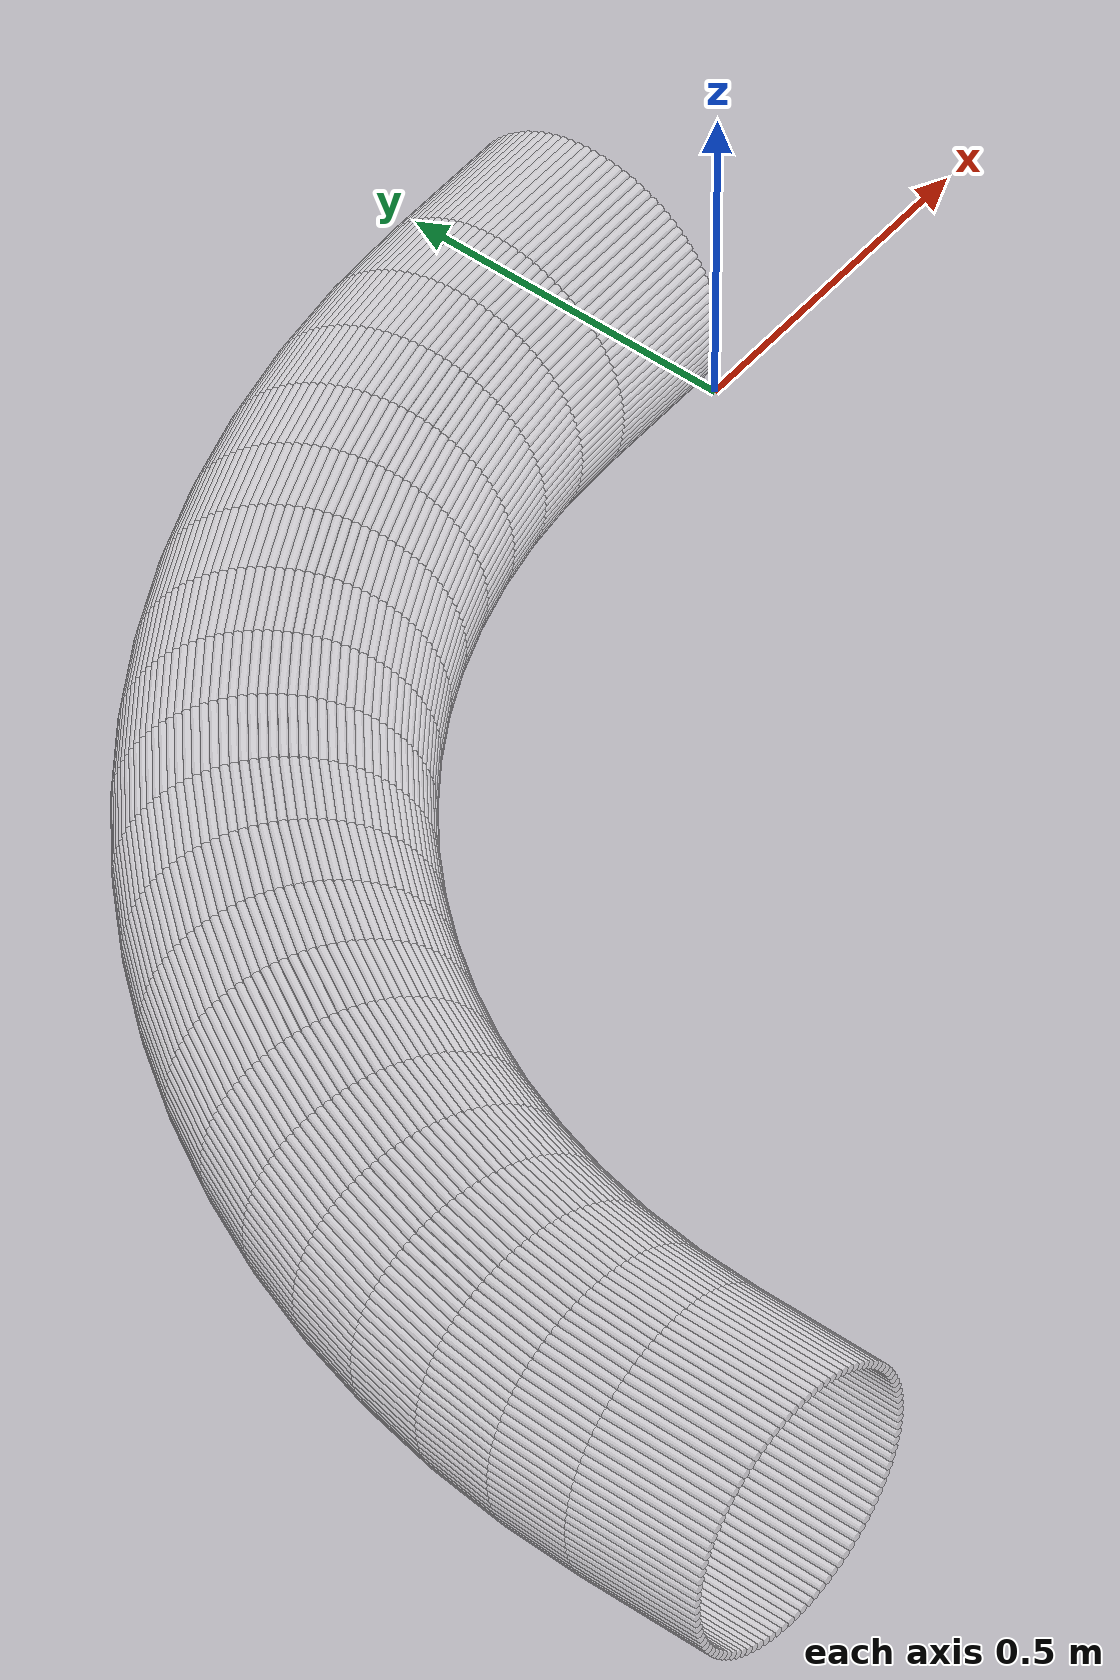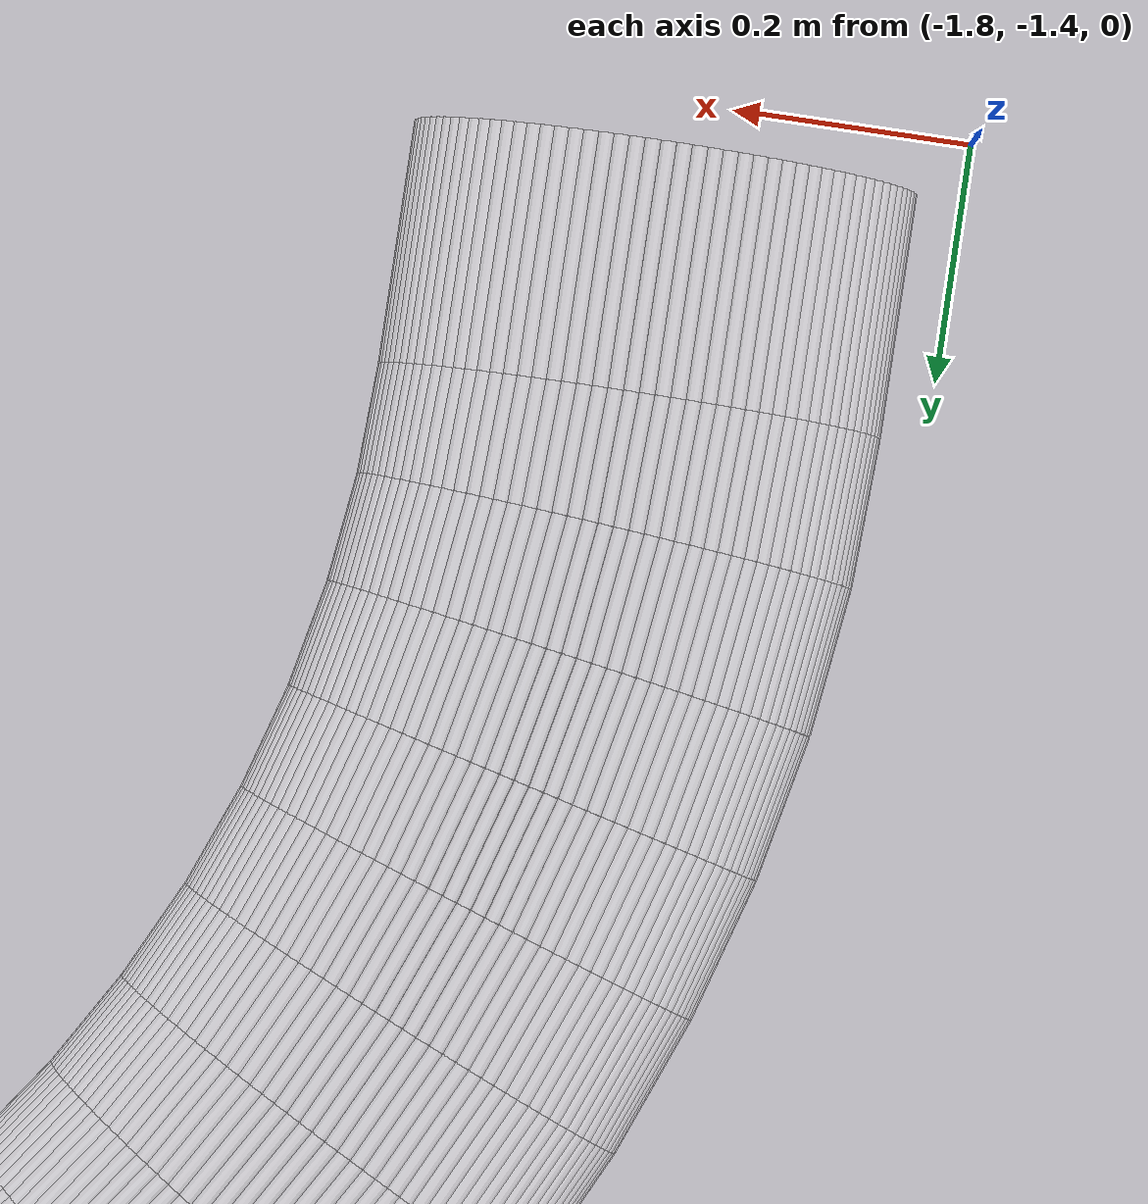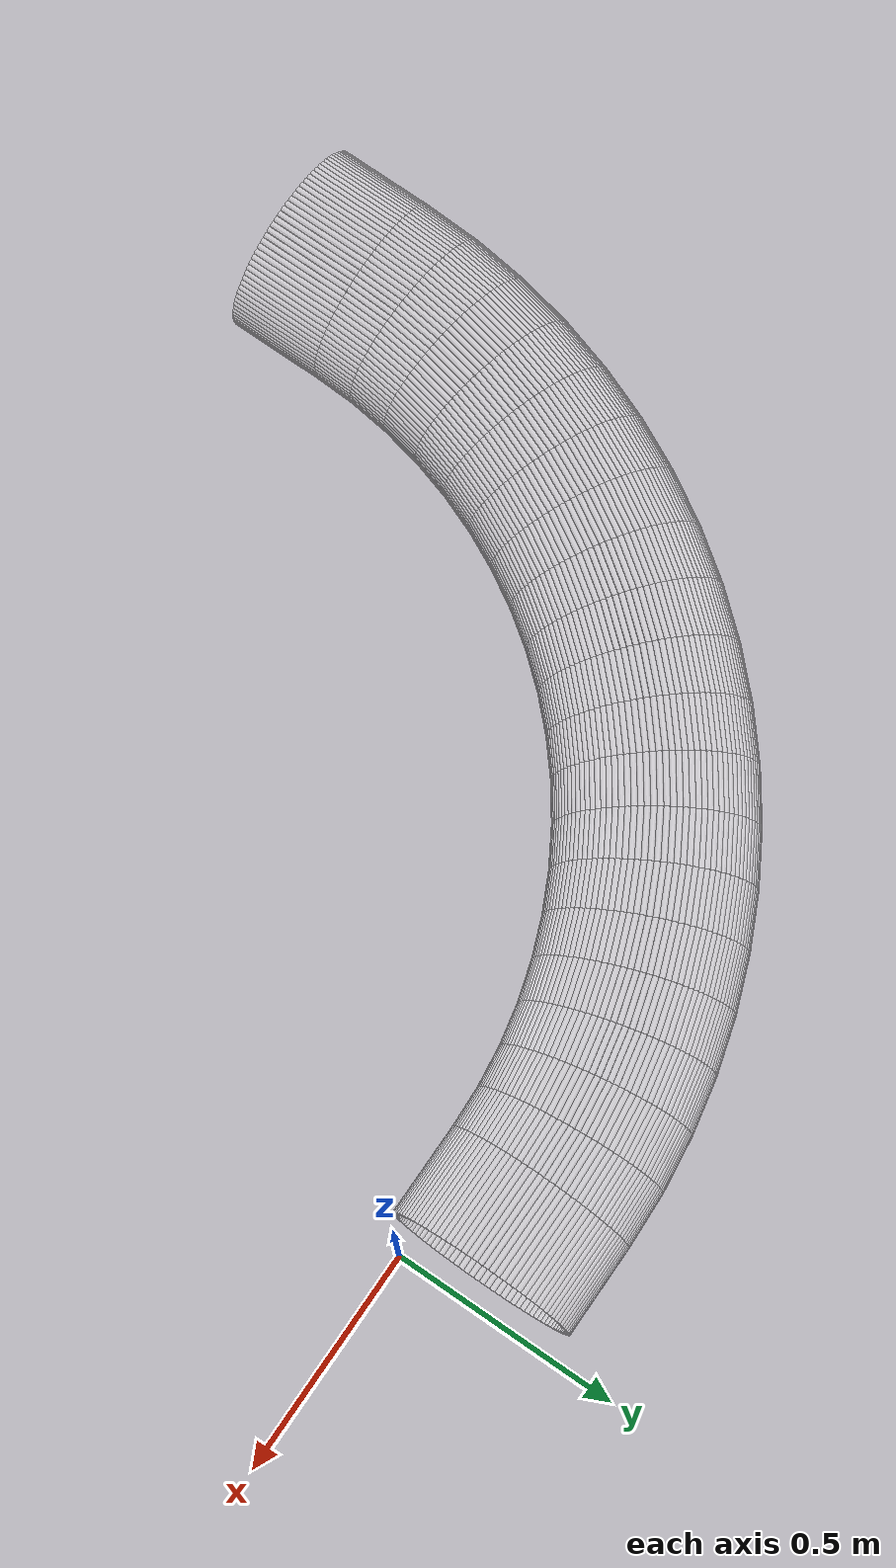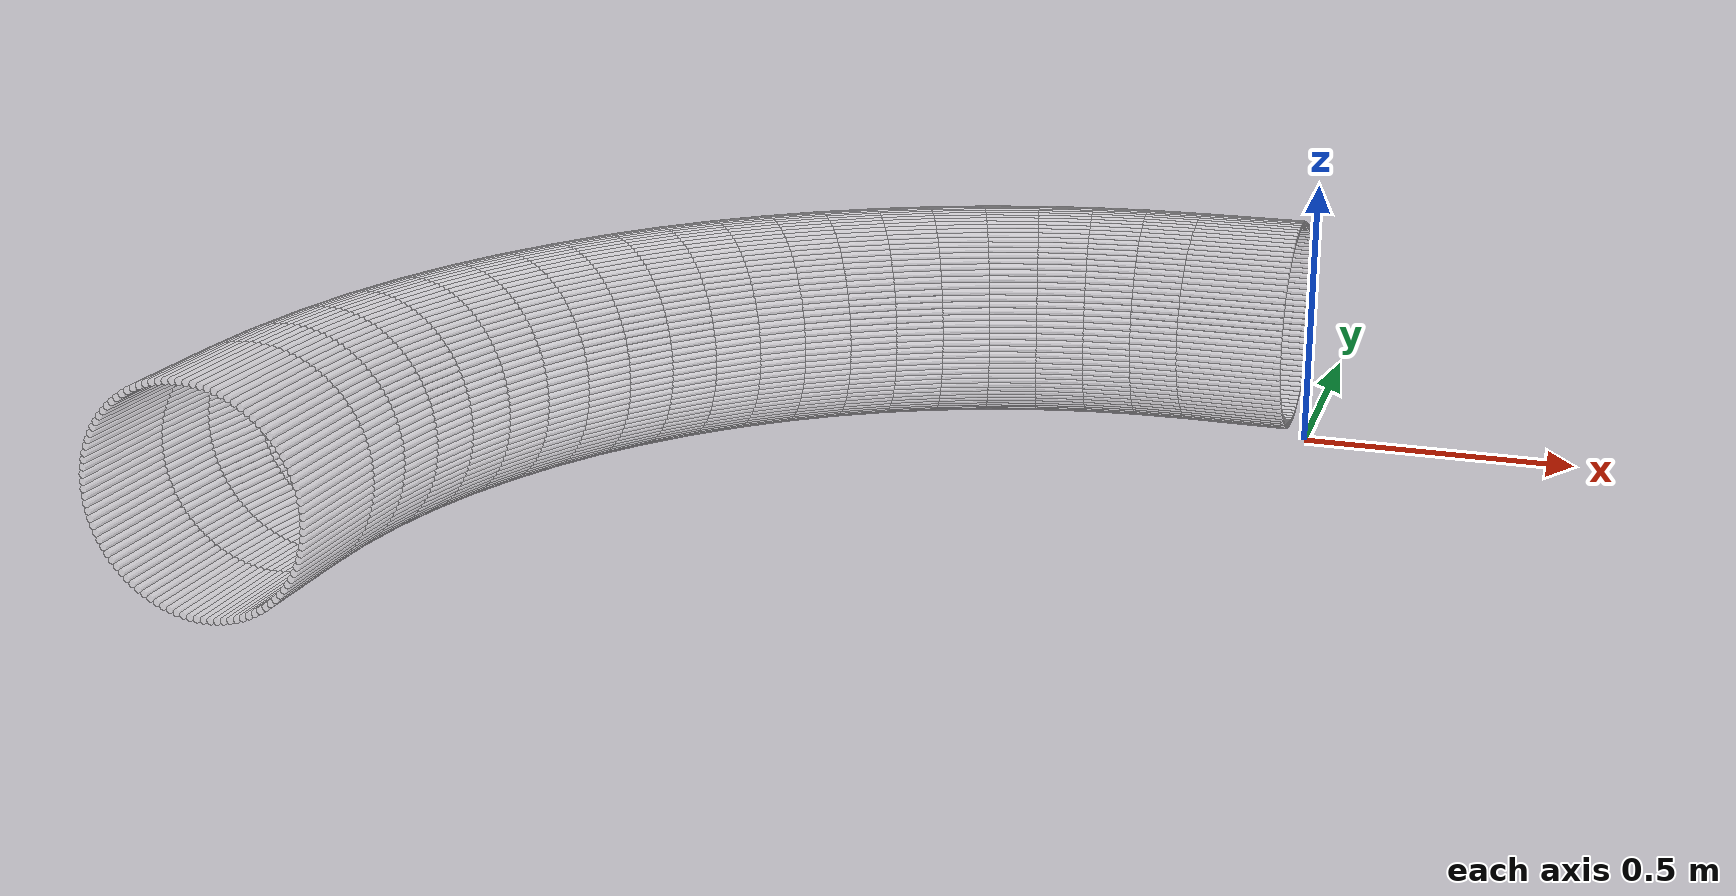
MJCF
<?xml version="1.0" encoding="utf-8"?>
<mujoco>
   <worldbody>
   <body pos="-0.25 -1.14 -0.02" euler="0 0 90">
      <geom euler=" 0 10 0 " fromto="1.5 -0.2 0.2 1.5 0 0.2" rgba="1 1 1 0.35"
            size="0.0062822"
            type="cylinder"/>
      <geom euler=" 0 20 0 " fromto="1.4996 -0.2 0.21256 1.4996 0 0.21256"
            rgba="1 1 1 0.35"
            size="0.0062822"
            type="cylinder"/>
      <geom euler=" 0 30 0 " fromto="1.4984 -0.2 0.22507 1.4984 0 0.22507"
            rgba="1 1 1 0.35"
            size="0.0062822"
            type="cylinder"/>
      <geom euler=" 0 40 0 " fromto="1.4965 -0.2 0.23748 1.4965 0 0.23748"
            rgba="1 1 1 0.35"
            size="0.0062822"
            type="cylinder"/>
      <geom euler=" 0 50 0 " fromto="1.4937 -0.2 0.24974 1.4937 0 0.24974"
            rgba="1 1 1 0.35"
            size="0.0062822"
            type="cylinder"/>
      <geom euler=" 0 60 0 " fromto="1.4902 -0.2 0.2618 1.4902 0 0.2618" rgba="1 1 1 0.35"
            size="0.0062822"
            type="cylinder"/>
      <geom euler=" 0 70 0 " fromto="1.486 -0.2 0.27362 1.486 0 0.27362" rgba="1 1 1 0.35"
            size="0.0062822"
            type="cylinder"/>
      <geom euler=" 0 80 0 " fromto="1.481 -0.2 0.28516 1.481 0 0.28516" rgba="1 1 1 0.35"
            size="0.0062822"
            type="cylinder"/>
      <geom euler=" 0 90 0 " fromto="1.4753 -0.2 0.29635 1.4753 0 0.29635"
            rgba="1 1 1 0.35"
            size="0.0062822"
            type="cylinder"/>
      <geom euler=" 0 100 0 " fromto="1.4689 -0.2 0.30717 1.4689 0 0.30717"
            rgba="1 1 1 0.35"
            size="0.0062822"
            type="cylinder"/>
      <geom euler=" 0 110 0 " fromto="1.4618 -0.2 0.31756 1.4618 0 0.31756"
            rgba="1 1 1 0.35"
            size="0.0062822"
            type="cylinder"/>
      <geom euler=" 0 120 0 " fromto="1.4541 -0.2 0.32748 1.4541 0 0.32748"
            rgba="1 1 1 0.35"
            size="0.0062822"
            type="cylinder"/>
      <geom euler=" 0 130 0 " fromto="1.4458 -0.2 0.33691 1.4458 0 0.33691"
            rgba="1 1 1 0.35"
            size="0.0062822"
            type="cylinder"/>
      <geom euler=" 0 140 0 " fromto="1.4369 -0.2 0.34579 1.4369 0 0.34579"
            rgba="1 1 1 0.35"
            size="0.0062822"
            type="cylinder"/>
      <geom euler=" 0 150 0 " fromto="1.4275 -0.2 0.3541 1.4275 0 0.3541" rgba="1 1 1 0.35"
            size="0.0062822"
            type="cylinder"/>
      <geom euler=" 0 160 0 " fromto="1.4176 -0.2 0.3618 1.4176 0 0.3618" rgba="1 1 1 0.35"
            size="0.0062822"
            type="cylinder"/>
      <geom euler=" 0 170 0 " fromto="1.4072 -0.2 0.36887 1.4072 0 0.36887"
            rgba="1 1 1 0.35"
            size="0.0062822"
            type="cylinder"/>
      <geom euler=" 0 180 0 " fromto="1.3964 -0.2 0.37526 1.3964 0 0.37526"
            rgba="1 1 1 0.35"
            size="0.0062822"
            type="cylinder"/>
      <geom euler=" 0 190 0 " fromto="1.3852 -0.2 0.38097 1.3852 0 0.38097"
            rgba="1 1 1 0.35"
            size="0.0062822"
            type="cylinder"/>
      <geom euler=" 0 200 0 " fromto="1.3736 -0.2 0.38596 1.3736 0 0.38596"
            rgba="1 1 1 0.35"
            size="0.0062822"
            type="cylinder"/>
      <geom euler=" 0 210 0 " fromto="1.3618 -0.2 0.39021 1.3618 0 0.39021"
            rgba="1 1 1 0.35"
            size="0.0062822"
            type="cylinder"/>
      <geom euler=" 0 220 0 " fromto="1.3497 -0.2 0.39372 1.3497 0 0.39372"
            rgba="1 1 1 0.35"
            size="0.0062822"
            type="cylinder"/>
      <geom euler=" 0 230 0 " fromto="1.3375 -0.2 0.39646 1.3375 0 0.39646"
            rgba="1 1 1 0.35"
            size="0.0062822"
            type="cylinder"/>
      <geom euler=" 0 240 0 " fromto="1.3251 -0.2 0.39842 1.3251 0 0.39842"
            rgba="1 1 1 0.35"
            size="0.0062822"
            type="cylinder"/>
      <geom euler=" 0 250 0 " fromto="1.3126 -0.2 0.39961 1.3126 0 0.39961"
            rgba="1 1 1 0.35"
            size="0.0062822"
            type="cylinder"/>
      <geom euler=" 0 260 0 " fromto="1.3 -0.2 0.4 1.3 0 0.4" rgba="1 1 1 0.35"
            size="0.0062822"
            type="cylinder"/>
      <geom euler=" 0 270 0 " fromto="1.2874 -0.2 0.39961 1.2874 0 0.39961"
            rgba="1 1 1 0.35"
            size="0.0062822"
            type="cylinder"/>
      <geom euler=" 0 280 0 " fromto="1.2749 -0.2 0.39842 1.2749 0 0.39842"
            rgba="1 1 1 0.35"
            size="0.0062822"
            type="cylinder"/>
      <geom euler=" 0 290 0 " fromto="1.2625 -0.2 0.39646 1.2625 0 0.39646"
            rgba="1 1 1 0.35"
            size="0.0062822"
            type="cylinder"/>
      <geom euler=" 0 300 0 " fromto="1.2503 -0.2 0.39372 1.2503 0 0.39372"
            rgba="1 1 1 0.35"
            size="0.0062822"
            type="cylinder"/>
      <geom euler=" 0 310 0 " fromto="1.2382 -0.2 0.39021 1.2382 0 0.39021"
            rgba="1 1 1 0.35"
            size="0.0062822"
            type="cylinder"/>
      <geom euler=" 0 320 0 " fromto="1.2264 -0.2 0.38596 1.2264 0 0.38596"
            rgba="1 1 1 0.35"
            size="0.0062822"
            type="cylinder"/>
      <geom euler=" 0 330 0 " fromto="1.2148 -0.2 0.38097 1.2148 0 0.38097"
            rgba="1 1 1 0.35"
            size="0.0062822"
            type="cylinder"/>
      <geom euler=" 0 340 0 " fromto="1.2036 -0.2 0.37526 1.2036 0 0.37526"
            rgba="1 1 1 0.35"
            size="0.0062822"
            type="cylinder"/>
      <geom euler=" 0 350 0 " fromto="1.1928 -0.2 0.36887 1.1928 0 0.36887"
            rgba="1 1 1 0.35"
            size="0.0062822"
            type="cylinder"/>
      <geom euler=" 0 360 0 " fromto="1.1824 -0.2 0.3618 1.1824 0 0.3618" rgba="1 1 1 0.35"
            size="0.0062822"
            type="cylinder"/>
      <geom euler=" 0 370 0 " fromto="1.1725 -0.2 0.3541 1.1725 0 0.3541" rgba="1 1 1 0.35"
            size="0.0062822"
            type="cylinder"/>
      <geom euler=" 0 380 0 " fromto="1.1631 -0.2 0.34579 1.1631 0 0.34579"
            rgba="1 1 1 0.35"
            size="0.0062822"
            type="cylinder"/>
      <geom euler=" 0 390 0 " fromto="1.1542 -0.2 0.33691 1.1542 0 0.33691"
            rgba="1 1 1 0.35"
            size="0.0062822"
            type="cylinder"/>
      <geom euler=" 0 400 0 " fromto="1.1459 -0.2 0.32748 1.1459 0 0.32748"
            rgba="1 1 1 0.35"
            size="0.0062822"
            type="cylinder"/>
      <geom euler=" 0 410 0 " fromto="1.1382 -0.2 0.31756 1.1382 0 0.31756"
            rgba="1 1 1 0.35"
            size="0.0062822"
            type="cylinder"/>
      <geom euler=" 0 420 0 " fromto="1.1311 -0.2 0.30717 1.1311 0 0.30717"
            rgba="1 1 1 0.35"
            size="0.0062822"
            type="cylinder"/>
      <geom euler=" 0 430 0 " fromto="1.1247 -0.2 0.29635 1.1247 0 0.29635"
            rgba="1 1 1 0.35"
            size="0.0062822"
            type="cylinder"/>
      <geom euler=" 0 440 0 " fromto="1.119 -0.2 0.28516 1.119 0 0.28516" rgba="1 1 1 0.35"
            size="0.0062822"
            type="cylinder"/>
      <geom euler=" 0 450 0 " fromto="1.114 -0.2 0.27362 1.114 0 0.27362" rgba="1 1 1 0.35"
            size="0.0062822"
            type="cylinder"/>
      <geom euler=" 0 460 0 " fromto="1.1098 -0.2 0.2618 1.1098 0 0.2618" rgba="1 1 1 0.35"
            size="0.0062822"
            type="cylinder"/>
      <geom euler=" 0 470 0 " fromto="1.1063 -0.2 0.24974 1.1063 0 0.24974"
            rgba="1 1 1 0.35"
            size="0.0062822"
            type="cylinder"/>
      <geom euler=" 0 480 0 " fromto="1.1035 -0.2 0.23748 1.1035 0 0.23748"
            rgba="1 1 1 0.35"
            size="0.0062822"
            type="cylinder"/>
      <geom euler=" 0 490 0 " fromto="1.1016 -0.2 0.22507 1.1016 0 0.22507"
            rgba="1 1 1 0.35"
            size="0.0062822"
            type="cylinder"/>
      <geom euler=" 0 500 0 " fromto="1.1004 -0.2 0.21256 1.1004 0 0.21256"
            rgba="1 1 1 0.35"
            size="0.0062822"
            type="cylinder"/>
      <geom euler=" 0 510 0 " fromto="1.1 -0.2 0.2 1.1 0 0.2" rgba="1 1 1 0.35"
            size="0.0062822"
            type="cylinder"/>
      <geom euler=" 0 520 0 " fromto="1.1004 -0.2 0.18744 1.1004 0 0.18744"
            rgba="1 1 1 0.35"
            size="0.0062822"
            type="cylinder"/>
      <geom euler=" 0 530 0 " fromto="1.1016 -0.2 0.17493 1.1016 0 0.17493"
            rgba="1 1 1 0.35"
            size="0.0062822"
            type="cylinder"/>
      <geom euler=" 0 540 0 " fromto="1.1035 -0.2 0.16252 1.1035 0 0.16252"
            rgba="1 1 1 0.35"
            size="0.0062822"
            type="cylinder"/>
      <geom euler=" 0 550 0 " fromto="1.1063 -0.2 0.15026 1.1063 0 0.15026"
            rgba="1 1 1 0.35"
            size="0.0062822"
            type="cylinder"/>
      <geom euler=" 0 560 0 " fromto="1.1098 -0.2 0.1382 1.1098 0 0.1382" rgba="1 1 1 0.35"
            size="0.0062822"
            type="cylinder"/>
      <geom euler=" 0 570 0 " fromto="1.114 -0.2 0.12638 1.114 0 0.12638" rgba="1 1 1 0.35"
            size="0.0062822"
            type="cylinder"/>
      <geom euler=" 0 580 0 " fromto="1.119 -0.2 0.11484 1.119 0 0.11484" rgba="1 1 1 0.35"
            size="0.0062822"
            type="cylinder"/>
      <geom euler=" 0 590 0 " fromto="1.1247 -0.2 0.10365 1.1247 0 0.10365"
            rgba="1 1 1 0.35"
            size="0.0062822"
            type="cylinder"/>
      <geom euler=" 0 600 0 " fromto="1.1311 -0.2 0.092835 1.1311 0 0.092835"
            rgba="1 1 1 0.35"
            size="0.0062822"
            type="cylinder"/>
      <geom euler=" 0 610 0 " fromto="1.1382 -0.2 0.082443 1.1382 0 0.082443"
            rgba="1 1 1 0.35"
            size="0.0062822"
            type="cylinder"/>
      <geom euler=" 0 620 0 " fromto="1.1459 -0.2 0.072515 1.1459 0 0.072515"
            rgba="1 1 1 0.35"
            size="0.0062822"
            type="cylinder"/>
      <geom euler=" 0 630 0 " fromto="1.1542 -0.2 0.063091 1.1542 0 0.063091"
            rgba="1 1 1 0.35"
            size="0.0062822"
            type="cylinder"/>
      <geom euler=" 0 640 0 " fromto="1.1631 -0.2 0.054206 1.1631 0 0.054206"
            rgba="1 1 1 0.35"
            size="0.0062822"
            type="cylinder"/>
      <geom euler=" 0 650 0 " fromto="1.1725 -0.2 0.045897 1.1725 0 0.045897"
            rgba="1 1 1 0.35"
            size="0.0062822"
            type="cylinder"/>
      <geom euler=" 0 660 0 " fromto="1.1824 -0.2 0.038197 1.1824 0 0.038197"
            rgba="1 1 1 0.35"
            size="0.0062822"
            type="cylinder"/>
      <geom euler=" 0 670 0 " fromto="1.1928 -0.2 0.031134 1.1928 0 0.031134"
            rgba="1 1 1 0.35"
            size="0.0062822"
            type="cylinder"/>
      <geom euler=" 0 680 0 " fromto="1.2036 -0.2 0.024739 1.2036 0 0.024739"
            rgba="1 1 1 0.35"
            size="0.0062822"
            type="cylinder"/>
      <geom euler=" 0 690 0 " fromto="1.2148 -0.2 0.019035 1.2148 0 0.019035"
            rgba="1 1 1 0.35"
            size="0.0062822"
            type="cylinder"/>
      <geom euler=" 0 700 0 " fromto="1.2264 -0.2 0.014045 1.2264 0 0.014045"
            rgba="1 1 1 0.35"
            size="0.0062822"
            type="cylinder"/>
      <geom euler=" 0 710 0 " fromto="1.2382 -0.2 0.0097887 1.2382 0 0.0097887"
            rgba="1 1 1 0.35"
            size="0.0062822"
            type="cylinder"/>
      <geom euler=" 0 720 0 " fromto="1.2503 -0.2 0.0062834 1.2503 0 0.0062834"
            rgba="1 1 1 0.35"
            size="0.0062822"
            type="cylinder"/>
      <geom euler=" 0 730 0 " fromto="1.2625 -0.2 0.0035425 1.2625 0 0.0035425"
            rgba="1 1 1 0.35"
            size="0.0062822"
            type="cylinder"/>
      <geom euler=" 0 740 0 " fromto="1.2749 -0.2 0.0015771 1.2749 0 0.0015771"
            rgba="1 1 1 0.35"
            size="0.0062822"
            type="cylinder"/>
      <geom euler=" 0 750 0 " fromto="1.2874 -0.2 0.00039465 1.2874 0 0.00039465"
            rgba="1 1 1 0.35"
            size="0.0062822"
            type="cylinder"/>
      <geom euler=" 0 760 0 " fromto="1.3 -0.2 0 1.3 0 0" rgba="1 1 1 0.35"
            size="0.0062822"
            type="cylinder"/>
      <geom euler=" 0 770 0 " fromto="1.3126 -0.2 0.00039465 1.3126 0 0.00039465"
            rgba="1 1 1 0.35"
            size="0.0062822"
            type="cylinder"/>
      <geom euler=" 0 780 0 " fromto="1.3251 -0.2 0.0015771 1.3251 0 0.0015771"
            rgba="1 1 1 0.35"
            size="0.0062822"
            type="cylinder"/>
      <geom euler=" 0 790 0 " fromto="1.3375 -0.2 0.0035425 1.3375 0 0.0035425"
            rgba="1 1 1 0.35"
            size="0.0062822"
            type="cylinder"/>
      <geom euler=" 0 800 0 " fromto="1.3497 -0.2 0.0062834 1.3497 0 0.0062834"
            rgba="1 1 1 0.35"
            size="0.0062822"
            type="cylinder"/>
      <geom euler=" 0 810 0 " fromto="1.3618 -0.2 0.0097887 1.3618 0 0.0097887"
            rgba="1 1 1 0.35"
            size="0.0062822"
            type="cylinder"/>
      <geom euler=" 0 820 0 " fromto="1.3736 -0.2 0.014045 1.3736 0 0.014045"
            rgba="1 1 1 0.35"
            size="0.0062822"
            type="cylinder"/>
      <geom euler=" 0 830 0 " fromto="1.3852 -0.2 0.019035 1.3852 0 0.019035"
            rgba="1 1 1 0.35"
            size="0.0062822"
            type="cylinder"/>
      <geom euler=" 0 840 0 " fromto="1.3964 -0.2 0.024739 1.3964 0 0.024739"
            rgba="1 1 1 0.35"
            size="0.0062822"
            type="cylinder"/>
      <geom euler=" 0 850 0 " fromto="1.4072 -0.2 0.031134 1.4072 0 0.031134"
            rgba="1 1 1 0.35"
            size="0.0062822"
            type="cylinder"/>
      <geom euler=" 0 860 0 " fromto="1.4176 -0.2 0.038197 1.4176 0 0.038197"
            rgba="1 1 1 0.35"
            size="0.0062822"
            type="cylinder"/>
      <geom euler=" 0 870 0 " fromto="1.4275 -0.2 0.045897 1.4275 0 0.045897"
            rgba="1 1 1 0.35"
            size="0.0062822"
            type="cylinder"/>
      <geom euler=" 0 880 0 " fromto="1.4369 -0.2 0.054206 1.4369 0 0.054206"
            rgba="1 1 1 0.35"
            size="0.0062822"
            type="cylinder"/>
      <geom euler=" 0 890 0 " fromto="1.4458 -0.2 0.063091 1.4458 0 0.063091"
            rgba="1 1 1 0.35"
            size="0.0062822"
            type="cylinder"/>
      <geom euler=" 0 900 0 " fromto="1.4541 -0.2 0.072515 1.4541 0 0.072515"
            rgba="1 1 1 0.35"
            size="0.0062822"
            type="cylinder"/>
      <geom euler=" 0 910 0 " fromto="1.4618 -0.2 0.082443 1.4618 0 0.082443"
            rgba="1 1 1 0.35"
            size="0.0062822"
            type="cylinder"/>
      <geom euler=" 0 920 0 " fromto="1.4689 -0.2 0.092835 1.4689 0 0.092835"
            rgba="1 1 1 0.35"
            size="0.0062822"
            type="cylinder"/>
      <geom euler=" 0 930 0 " fromto="1.4753 -0.2 0.10365 1.4753 0 0.10365"
            rgba="1 1 1 0.35"
            size="0.0062822"
            type="cylinder"/>
      <geom euler=" 0 940 0 " fromto="1.481 -0.2 0.11484 1.481 0 0.11484" rgba="1 1 1 0.35"
            size="0.0062822"
            type="cylinder"/>
      <geom euler=" 0 950 0 " fromto="1.486 -0.2 0.12638 1.486 0 0.12638" rgba="1 1 1 0.35"
            size="0.0062822"
            type="cylinder"/>
      <geom euler=" 0 960 0 " fromto="1.4902 -0.2 0.1382 1.4902 0 0.1382" rgba="1 1 1 0.35"
            size="0.0062822"
            type="cylinder"/>
      <geom euler=" 0 970 0 " fromto="1.4937 -0.2 0.15026 1.4937 0 0.15026"
            rgba="1 1 1 0.35"
            size="0.0062822"
            type="cylinder"/>
      <geom euler=" 0 980 0 " fromto="1.4965 -0.2 0.16252 1.4965 0 0.16252"
            rgba="1 1 1 0.35"
            size="0.0062822"
            type="cylinder"/>
      <geom euler=" 0 990 0 " fromto="1.4984 -0.2 0.17493 1.4984 0 0.17493"
            rgba="1 1 1 0.35"
            size="0.0062822"
            type="cylinder"/>
      <geom euler=" 0 1000 0 " fromto="1.4996 -0.2 0.18744 1.4996 0 0.18744"
            rgba="1 1 1 0.35"
            size="0.0062822"
            type="cylinder"/>
      <geom euler=" 0 10 0 " fromto="1.5 0 0.2 1.4949 0.12387 0.2" rgba="1 1 1 0.35"
            size="0.0062822"
            type="cylinder"/>
      <geom euler=" 0 20 0 " fromto="1.4996 0 0.21256 1.4945 0.12384 0.21256"
            rgba="1 1 1 0.35"
            size="0.0062822"
            type="cylinder"/>
      <geom euler=" 0 30 0 " fromto="1.4984 0 0.22507 1.4933 0.12374 0.22507"
            rgba="1 1 1 0.35"
            size="0.0062822"
            type="cylinder"/>
      <geom euler=" 0 40 0 " fromto="1.4965 0 0.23748 1.4913 0.12358 0.23748"
            rgba="1 1 1 0.35"
            size="0.0062822"
            type="cylinder"/>
      <geom euler=" 0 50 0 " fromto="1.4937 0 0.24974 1.4886 0.12335 0.24974"
            rgba="1 1 1 0.35"
            size="0.0062822"
            type="cylinder"/>
      <geom euler=" 0 60 0 " fromto="1.4902 0 0.2618 1.4851 0.12306 0.2618"
            rgba="1 1 1 0.35"
            size="0.0062822"
            type="cylinder"/>
      <geom euler=" 0 70 0 " fromto="1.486 0 0.27362 1.4809 0.12271 0.27362"
            rgba="1 1 1 0.35"
            size="0.0062822"
            type="cylinder"/>
      <geom euler=" 0 80 0 " fromto="1.481 0 0.28516 1.4759 0.1223 0.28516"
            rgba="1 1 1 0.35"
            size="0.0062822"
            type="cylinder"/>
      <geom euler=" 0 90 0 " fromto="1.4753 0 0.29635 1.4702 0.12183 0.29635"
            rgba="1 1 1 0.35"
            size="0.0062822"
            type="cylinder"/>
      <geom euler=" 0 100 0 " fromto="1.4689 0 0.30717 1.4638 0.1213 0.30717"
            rgba="1 1 1 0.35"
            size="0.0062822"
            type="cylinder"/>
      <geom euler=" 0 110 0 " fromto="1.4618 0 0.31756 1.4568 0.12071 0.31756"
            rgba="1 1 1 0.35"
            size="0.0062822"
            type="cylinder"/>
      <geom euler=" 0 120 0 " fromto="1.4541 0 0.32748 1.4491 0.12008 0.32748"
            rgba="1 1 1 0.35"
            size="0.0062822"
            type="cylinder"/>
      <geom euler=" 0 130 0 " fromto="1.4458 0 0.33691 1.4409 0.11939 0.33691"
            rgba="1 1 1 0.35"
            size="0.0062822"
            type="cylinder"/>
      <geom euler=" 0 140 0 " fromto="1.4369 0 0.34579 1.432 0.11866 0.34579"
            rgba="1 1 1 0.35"
            size="0.0062822"
            type="cylinder"/>
      <geom euler=" 0 150 0 " fromto="1.4275 0 0.3541 1.4226 0.11788 0.3541"
            rgba="1 1 1 0.35"
            size="0.0062822"
            type="cylinder"/>
      <geom euler=" 0 160 0 " fromto="1.4176 0 0.3618 1.4127 0.11706 0.3618"
            rgba="1 1 1 0.35"
            size="0.0062822"
            type="cylinder"/>
      <geom euler=" 0 170 0 " fromto="1.4072 0 0.36887 1.4024 0.1162 0.36887"
            rgba="1 1 1 0.35"
            size="0.0062822"
            type="cylinder"/>
      <geom euler=" 0 180 0 " fromto="1.3964 0 0.37526 1.3916 0.11531 0.37526"
            rgba="1 1 1 0.35"
            size="0.0062822"
            type="cylinder"/>
      <geom euler=" 0 190 0 " fromto="1.3852 0 0.38097 1.3804 0.11439 0.38097"
            rgba="1 1 1 0.35"
            size="0.0062822"
            type="cylinder"/>
      <geom euler=" 0 200 0 " fromto="1.3736 0 0.38596 1.3689 0.11343 0.38596"
            rgba="1 1 1 0.35"
            size="0.0062822"
            type="cylinder"/>
      <geom euler=" 0 210 0 " fromto="1.3618 0 0.39021 1.3572 0.11246 0.39021"
            rgba="1 1 1 0.35"
            size="0.0062822"
            type="cylinder"/>
      <geom euler=" 0 220 0 " fromto="1.3497 0 0.39372 1.3451 0.11146 0.39372"
            rgba="1 1 1 0.35"
            size="0.0062822"
            type="cylinder"/>
      <geom euler=" 0 230 0 " fromto="1.3375 0 0.39646 1.3329 0.11045 0.39646"
            rgba="1 1 1 0.35"
            size="0.0062822"
            type="cylinder"/>
      <geom euler=" 0 240 0 " fromto="1.3251 0 0.39842 1.3205 0.10942 0.39842"
            rgba="1 1 1 0.35"
            size="0.0062822"
            type="cylinder"/>
      <geom euler=" 0 250 0 " fromto="1.3126 0 0.39961 1.3081 0.10839 0.39961"
            rgba="1 1 1 0.35"
            size="0.0062822"
            type="cylinder"/>
      <geom euler=" 0 260 0 " fromto="1.3 0 0.4 1.2956 0.10735 0.4" rgba="1 1 1 0.35"
            size="0.0062822"
            type="cylinder"/>
      <geom euler=" 0 270 0 " fromto="1.2874 0 0.39961 1.283 0.10632 0.39961"
            rgba="1 1 1 0.35"
            size="0.0062822"
            type="cylinder"/>
      <geom euler=" 0 280 0 " fromto="1.2749 0 0.39842 1.2706 0.10528 0.39842"
            rgba="1 1 1 0.35"
            size="0.0062822"
            type="cylinder"/>
      <geom euler=" 0 290 0 " fromto="1.2625 0 0.39646 1.2582 0.10426 0.39646"
            rgba="1 1 1 0.35"
            size="0.0062822"
            type="cylinder"/>
      <geom euler=" 0 300 0 " fromto="1.2503 0 0.39372 1.246 0.10325 0.39372"
            rgba="1 1 1 0.35"
            size="0.0062822"
            type="cylinder"/>
      <geom euler=" 0 310 0 " fromto="1.2382 0 0.39021 1.234 0.10225 0.39021"
            rgba="1 1 1 0.35"
            size="0.0062822"
            type="cylinder"/>
      <geom euler=" 0 320 0 " fromto="1.2264 0 0.38596 1.2222 0.10127 0.38596"
            rgba="1 1 1 0.35"
            size="0.0062822"
            type="cylinder"/>
      <geom euler=" 0 330 0 " fromto="1.2148 0 0.38097 1.2107 0.10032 0.38097"
            rgba="1 1 1 0.35"
            size="0.0062822"
            type="cylinder"/>
      <geom euler=" 0 340 0 " fromto="1.2036 0 0.37526 1.1995 0.099397 0.37526"
            rgba="1 1 1 0.35"
            size="0.0062822"
            type="cylinder"/>
      <geom euler=" 0 350 0 " fromto="1.1928 0 0.36887 1.1888 0.098504 0.36887"
            rgba="1 1 1 0.35"
            size="0.0062822"
            type="cylinder"/>
      <geom euler=" 0 360 0 " fromto="1.1824 0 0.3618 1.1784 0.097645 0.3618"
            rgba="1 1 1 0.35"
            size="0.0062822"
            type="cylinder"/>
      <geom euler=" 0 370 0 " fromto="1.1725 0 0.3541 1.1685 0.096826 0.3541"
            rgba="1 1 1 0.35"
            size="0.0062822"
            type="cylinder"/>
      <geom euler=" 0 380 0 " fromto="1.1631 0 0.34579 1.1591 0.096047 0.34579"
            rgba="1 1 1 0.35"
            size="0.0062822"
            type="cylinder"/>
      <geom euler=" 0 390 0 " fromto="1.1542 0 0.33691 1.1503 0.095314 0.33691"
            rgba="1 1 1 0.35"
            size="0.0062822"
            type="cylinder"/>
      <geom euler=" 0 400 0 " fromto="1.1459 0 0.32748 1.142 0.094627 0.32748"
            rgba="1 1 1 0.35"
            size="0.0062822"
            type="cylinder"/>
      <geom euler=" 0 410 0 " fromto="1.1382 0 0.31756 1.1343 0.093992 0.31756"
            rgba="1 1 1 0.35"
            size="0.0062822"
            type="cylinder"/>
      <geom euler=" 0 420 0 " fromto="1.1311 0 0.30717 1.1273 0.093408 0.30717"
            rgba="1 1 1 0.35"
            size="0.0062822"
            type="cylinder"/>
      <geom euler=" 0 430 0 " fromto="1.1247 0 0.29635 1.1209 0.09288 0.29635"
            rgba="1 1 1 0.35"
            size="0.0062822"
            type="cylinder"/>
      <geom euler=" 0 440 0 " fromto="1.119 0 0.28516 1.1152 0.092409 0.28516"
            rgba="1 1 1 0.35"
            size="0.0062822"
            type="cylinder"/>
      <geom euler=" 0 450 0 " fromto="1.114 0 0.27362 1.1102 0.091997 0.27362"
            rgba="1 1 1 0.35"
            size="0.0062822"
            type="cylinder"/>
      <geom euler=" 0 460 0 " fromto="1.1098 0 0.2618 1.106 0.091646 0.2618"
            rgba="1 1 1 0.35"
            size="0.0062822"
            type="cylinder"/>
      <geom euler=" 0 470 0 " fromto="1.1063 0 0.24974 1.1025 0.091356 0.24974"
            rgba="1 1 1 0.35"
            size="0.0062822"
            type="cylinder"/>
      <geom euler=" 0 480 0 " fromto="1.1035 0 0.23748 1.0998 0.09113 0.23748"
            rgba="1 1 1 0.35"
            size="0.0062822"
            type="cylinder"/>
      <geom euler=" 0 490 0 " fromto="1.1016 0 0.22507 1.0978 0.090968 0.22507"
            rgba="1 1 1 0.35"
            size="0.0062822"
            type="cylinder"/>
      <geom euler=" 0 500 0 " fromto="1.1004 0 0.21256 1.0966 0.09087 0.21256"
            rgba="1 1 1 0.35"
            size="0.0062822"
            type="cylinder"/>
      <geom euler=" 0 510 0 " fromto="1.1 0 0.2 1.0962 0.090837 0.2" rgba="1 1 1 0.35"
            size="0.0062822"
            type="cylinder"/>
      <geom euler=" 0 520 0 " fromto="1.1004 0 0.18744 1.0966 0.09087 0.18744"
            rgba="1 1 1 0.35"
            size="0.0062822"
            type="cylinder"/>
      <geom euler=" 0 530 0 " fromto="1.1016 0 0.17493 1.0978 0.090968 0.17493"
            rgba="1 1 1 0.35"
            size="0.0062822"
            type="cylinder"/>
      <geom euler=" 0 540 0 " fromto="1.1035 0 0.16252 1.0998 0.09113 0.16252"
            rgba="1 1 1 0.35"
            size="0.0062822"
            type="cylinder"/>
      <geom euler=" 0 550 0 " fromto="1.1063 0 0.15026 1.1025 0.091356 0.15026"
            rgba="1 1 1 0.35"
            size="0.0062822"
            type="cylinder"/>
      <geom euler=" 0 560 0 " fromto="1.1098 0 0.1382 1.106 0.091646 0.1382"
            rgba="1 1 1 0.35"
            size="0.0062822"
            type="cylinder"/>
      <geom euler=" 0 570 0 " fromto="1.114 0 0.12638 1.1102 0.091997 0.12638"
            rgba="1 1 1 0.35"
            size="0.0062822"
            type="cylinder"/>
      <geom euler=" 0 580 0 " fromto="1.119 0 0.11484 1.1152 0.092409 0.11484"
            rgba="1 1 1 0.35"
            size="0.0062822"
            type="cylinder"/>
      <geom euler=" 0 590 0 " fromto="1.1247 0 0.10365 1.1209 0.09288 0.10365"
            rgba="1 1 1 0.35"
            size="0.0062822"
            type="cylinder"/>
      <geom euler=" 0 600 0 " fromto="1.1311 0 0.092835 1.1273 0.093408 0.092835"
            rgba="1 1 1 0.35"
            size="0.0062822"
            type="cylinder"/>
      <geom euler=" 0 610 0 " fromto="1.1382 0 0.082443 1.1343 0.093992 0.082443"
            rgba="1 1 1 0.35"
            size="0.0062822"
            type="cylinder"/>
      <geom euler=" 0 620 0 " fromto="1.1459 0 0.072515 1.142 0.094627 0.072515"
            rgba="1 1 1 0.35"
            size="0.0062822"
            type="cylinder"/>
      <geom euler=" 0 630 0 " fromto="1.1542 0 0.063091 1.1503 0.095314 0.063091"
            rgba="1 1 1 0.35"
            size="0.0062822"
            type="cylinder"/>
      <geom euler=" 0 640 0 " fromto="1.1631 0 0.054206 1.1591 0.096047 0.054206"
            rgba="1 1 1 0.35"
            size="0.0062822"
            type="cylinder"/>
      <geom euler=" 0 650 0 " fromto="1.1725 0 0.045897 1.1685 0.096826 0.045897"
            rgba="1 1 1 0.35"
            size="0.0062822"
            type="cylinder"/>
      <geom euler=" 0 660 0 " fromto="1.1824 0 0.038197 1.1784 0.097645 0.038197"
            rgba="1 1 1 0.35"
            size="0.0062822"
            type="cylinder"/>
      <geom euler=" 0 670 0 " fromto="1.1928 0 0.031134 1.1888 0.098504 0.031134"
            rgba="1 1 1 0.35"
            size="0.0062822"
            type="cylinder"/>
      <geom euler=" 0 680 0 " fromto="1.2036 0 0.024739 1.1995 0.099397 0.024739"
            rgba="1 1 1 0.35"
            size="0.0062822"
            type="cylinder"/>
      <geom euler=" 0 690 0 " fromto="1.2148 0 0.019035 1.2107 0.10032 0.019035"
            rgba="1 1 1 0.35"
            size="0.0062822"
            type="cylinder"/>
      <geom euler=" 0 700 0 " fromto="1.2264 0 0.014045 1.2222 0.10127 0.014045"
            rgba="1 1 1 0.35"
            size="0.0062822"
            type="cylinder"/>
      <geom euler=" 0 710 0 " fromto="1.2382 0 0.0097887 1.234 0.10225 0.0097887"
            rgba="1 1 1 0.35"
            size="0.0062822"
            type="cylinder"/>
      <geom euler=" 0 720 0 " fromto="1.2503 0 0.0062834 1.246 0.10325 0.0062834"
            rgba="1 1 1 0.35"
            size="0.0062822"
            type="cylinder"/>
      <geom euler=" 0 730 0 " fromto="1.2625 0 0.0035425 1.2582 0.10426 0.0035425"
            rgba="1 1 1 0.35"
            size="0.0062822"
            type="cylinder"/>
      <geom euler=" 0 740 0 " fromto="1.2749 0 0.0015771 1.2706 0.10528 0.0015771"
            rgba="1 1 1 0.35"
            size="0.0062822"
            type="cylinder"/>
      <geom euler=" 0 750 0 " fromto="1.2874 0 0.00039465 1.283 0.10632 0.00039465"
            rgba="1 1 1 0.35"
            size="0.0062822"
            type="cylinder"/>
      <geom euler=" 0 760 0 " fromto="1.3 0 0 1.2956 0.10735 0" rgba="1 1 1 0.35"
            size="0.0062822"
            type="cylinder"/>
      <geom euler=" 0 770 0 " fromto="1.3126 0 0.00039465 1.3081 0.10839 0.00039465"
            rgba="1 1 1 0.35"
            size="0.0062822"
            type="cylinder"/>
      <geom euler=" 0 780 0 " fromto="1.3251 0 0.0015771 1.3205 0.10942 0.0015771"
            rgba="1 1 1 0.35"
            size="0.0062822"
            type="cylinder"/>
      <geom euler=" 0 790 0 " fromto="1.3375 0 0.0035425 1.3329 0.11045 0.0035425"
            rgba="1 1 1 0.35"
            size="0.0062822"
            type="cylinder"/>
      <geom euler=" 0 800 0 " fromto="1.3497 0 0.0062834 1.3451 0.11146 0.0062834"
            rgba="1 1 1 0.35"
            size="0.0062822"
            type="cylinder"/>
      <geom euler=" 0 810 0 " fromto="1.3618 0 0.0097887 1.3572 0.11246 0.0097887"
            rgba="1 1 1 0.35"
            size="0.0062822"
            type="cylinder"/>
      <geom euler=" 0 820 0 " fromto="1.3736 0 0.014045 1.3689 0.11343 0.014045"
            rgba="1 1 1 0.35"
            size="0.0062822"
            type="cylinder"/>
      <geom euler=" 0 830 0 " fromto="1.3852 0 0.019035 1.3804 0.11439 0.019035"
            rgba="1 1 1 0.35"
            size="0.0062822"
            type="cylinder"/>
      <geom euler=" 0 840 0 " fromto="1.3964 0 0.024739 1.3916 0.11531 0.024739"
            rgba="1 1 1 0.35"
            size="0.0062822"
            type="cylinder"/>
      <geom euler=" 0 850 0 " fromto="1.4072 0 0.031134 1.4024 0.1162 0.031134"
            rgba="1 1 1 0.35"
            size="0.0062822"
            type="cylinder"/>
      <geom euler=" 0 860 0 " fromto="1.4176 0 0.038197 1.4127 0.11706 0.038197"
            rgba="1 1 1 0.35"
            size="0.0062822"
            type="cylinder"/>
      <geom euler=" 0 870 0 " fromto="1.4275 0 0.045897 1.4226 0.11788 0.045897"
            rgba="1 1 1 0.35"
            size="0.0062822"
            type="cylinder"/>
      <geom euler=" 0 880 0 " fromto="1.4369 0 0.054206 1.432 0.11866 0.054206"
            rgba="1 1 1 0.35"
            size="0.0062822"
            type="cylinder"/>
      <geom euler=" 0 890 0 " fromto="1.4458 0 0.063091 1.4409 0.11939 0.063091"
            rgba="1 1 1 0.35"
            size="0.0062822"
            type="cylinder"/>
      <geom euler=" 0 900 0 " fromto="1.4541 0 0.072515 1.4491 0.12008 0.072515"
            rgba="1 1 1 0.35"
            size="0.0062822"
            type="cylinder"/>
      <geom euler=" 0 910 0 " fromto="1.4618 0 0.082443 1.4568 0.12071 0.082443"
            rgba="1 1 1 0.35"
            size="0.0062822"
            type="cylinder"/>
      <geom euler=" 0 920 0 " fromto="1.4689 0 0.092835 1.4638 0.1213 0.092835"
            rgba="1 1 1 0.35"
            size="0.0062822"
            type="cylinder"/>
      <geom euler=" 0 930 0 " fromto="1.4753 0 0.10365 1.4702 0.12183 0.10365"
            rgba="1 1 1 0.35"
            size="0.0062822"
            type="cylinder"/>
      <geom euler=" 0 940 0 " fromto="1.481 0 0.11484 1.4759 0.1223 0.11484"
            rgba="1 1 1 0.35"
            size="0.0062822"
            type="cylinder"/>
      <geom euler=" 0 950 0 " fromto="1.486 0 0.12638 1.4809 0.12271 0.12638"
            rgba="1 1 1 0.35"
            size="0.0062822"
            type="cylinder"/>
      <geom euler=" 0 960 0 " fromto="1.4902 0 0.1382 1.4851 0.12306 0.1382"
            rgba="1 1 1 0.35"
            size="0.0062822"
            type="cylinder"/>
      <geom euler=" 0 970 0 " fromto="1.4937 0 0.15026 1.4886 0.12335 0.15026"
            rgba="1 1 1 0.35"
            size="0.0062822"
            type="cylinder"/>
      <geom euler=" 0 980 0 " fromto="1.4965 0 0.16252 1.4913 0.12358 0.16252"
            rgba="1 1 1 0.35"
            size="0.0062822"
            type="cylinder"/>
      <geom euler=" 0 990 0 " fromto="1.4984 0 0.17493 1.4933 0.12374 0.17493"
            rgba="1 1 1 0.35"
            size="0.0062822"
            type="cylinder"/>
      <geom euler=" 0 1000 0 " fromto="1.4996 0 0.18744 1.4945 0.12384 0.18744"
            rgba="1 1 1 0.35"
            size="0.0062822"
            type="cylinder"/>
      <geom euler=" 0 10 0 " fromto="1.4949 0.12387 0.2 1.4795 0.24689 0.2"
            rgba="1 1 1 0.35"
            size="0.0062822"
            type="cylinder"/>
      <geom euler=" 0 20 0 " fromto="1.4945 0.12384 0.21256 1.4792 0.24683 0.21256"
            rgba="1 1 1 0.35"
            size="0.0062822"
            type="cylinder"/>
      <geom euler=" 0 30 0 " fromto="1.4933 0.12374 0.22507 1.478 0.24663 0.22507"
            rgba="1 1 1 0.35"
            size="0.0062822"
            type="cylinder"/>
      <geom euler=" 0 40 0 " fromto="1.4913 0.12358 0.23748 1.476 0.24631 0.23748"
            rgba="1 1 1 0.35"
            size="0.0062822"
            type="cylinder"/>
      <geom euler=" 0 50 0 " fromto="1.4886 0.12335 0.24974 1.4733 0.24586 0.24974"
            rgba="1 1 1 0.35"
            size="0.0062822"
            type="cylinder"/>
      <geom euler=" 0 60 0 " fromto="1.4851 0.12306 0.2618 1.4699 0.24528 0.2618"
            rgba="1 1 1 0.35"
            size="0.0062822"
            type="cylinder"/>
      <geom euler=" 0 70 0 " fromto="1.4809 0.12271 0.27362 1.4657 0.24458 0.27362"
            rgba="1 1 1 0.35"
            size="0.0062822"
            type="cylinder"/>
      <geom euler=" 0 80 0 " fromto="1.4759 0.1223 0.28516 1.4608 0.24376 0.28516"
            rgba="1 1 1 0.35"
            size="0.0062822"
            type="cylinder"/>
      <geom euler=" 0 90 0 " fromto="1.4702 0.12183 0.29635 1.4551 0.24282 0.29635"
            rgba="1 1 1 0.35"
            size="0.0062822"
            type="cylinder"/>
      <geom euler=" 0 100 0 " fromto="1.4638 0.1213 0.30717 1.4488 0.24177 0.30717"
            rgba="1 1 1 0.35"
            size="0.0062822"
            type="cylinder"/>
      <geom euler=" 0 110 0 " fromto="1.4568 0.12071 0.31756 1.4419 0.2406 0.31756"
            rgba="1 1 1 0.35"
            size="0.0062822"
            type="cylinder"/>
      <geom euler=" 0 120 0 " fromto="1.4491 0.12008 0.32748 1.4343 0.23934 0.32748"
            rgba="1 1 1 0.35"
            size="0.0062822"
            type="cylinder"/>
      <geom euler=" 0 130 0 " fromto="1.4409 0.11939 0.33691 1.4261 0.23797 0.33691"
            rgba="1 1 1 0.35"
            size="0.0062822"
            type="cylinder"/>
      <geom euler=" 0 140 0 " fromto="1.432 0.11866 0.34579 1.4173 0.23651 0.34579"
            rgba="1 1 1 0.35"
            size="0.0062822"
            type="cylinder"/>
      <geom euler=" 0 150 0 " fromto="1.4226 0.11788 0.3541 1.408 0.23496 0.3541"
            rgba="1 1 1 0.35"
            size="0.0062822"
            type="cylinder"/>
      <geom euler=" 0 160 0 " fromto="1.4127 0.11706 0.3618 1.3982 0.23332 0.3618"
            rgba="1 1 1 0.35"
            size="0.0062822"
            type="cylinder"/>
      <geom euler=" 0 170 0 " fromto="1.4024 0.1162 0.36887 1.388 0.23161 0.36887"
            rgba="1 1 1 0.35"
            size="0.0062822"
            type="cylinder"/>
      <geom euler=" 0 180 0 " fromto="1.3916 0.11531 0.37526 1.3773 0.22983 0.37526"
            rgba="1 1 1 0.35"
            size="0.0062822"
            type="cylinder"/>
      <geom euler=" 0 190 0 " fromto="1.3804 0.11439 0.38097 1.3663 0.22799 0.38097"
            rgba="1 1 1 0.35"
            size="0.0062822"
            type="cylinder"/>
      <geom euler=" 0 200 0 " fromto="1.3689 0.11343 0.38596 1.3549 0.22609 0.38596"
            rgba="1 1 1 0.35"
            size="0.0062822"
            type="cylinder"/>
      <geom euler=" 0 210 0 " fromto="1.3572 0.11246 0.39021 1.3432 0.22415 0.39021"
            rgba="1 1 1 0.35"
            size="0.0062822"
            type="cylinder"/>
      <geom euler=" 0 220 0 " fromto="1.3451 0.11146 0.39372 1.3313 0.22216 0.39372"
            rgba="1 1 1 0.35"
            size="0.0062822"
            type="cylinder"/>
      <geom euler=" 0 230 0 " fromto="1.3329 0.11045 0.39646 1.3192 0.22014 0.39646"
            rgba="1 1 1 0.35"
            size="0.0062822"
            type="cylinder"/>
      <geom euler=" 0 240 0 " fromto="1.3205 0.10942 0.39842 1.307 0.2181 0.39842"
            rgba="1 1 1 0.35"
            size="0.0062822"
            type="cylinder"/>
      <geom euler=" 0 250 0 " fromto="1.3081 0.10839 0.39961 1.2947 0.21604 0.39961"
            rgba="1 1 1 0.35"
            size="0.0062822"
            type="cylinder"/>
      <geom euler=" 0 260 0 " fromto="1.2956 0.10735 0.4 1.2823 0.21397 0.4"
            rgba="1 1 1 0.35"
            size="0.0062822"
            type="cylinder"/>
      <geom euler=" 0 270 0 " fromto="1.283 0.10632 0.39961 1.2699 0.21191 0.39961"
            rgba="1 1 1 0.35"
            size="0.0062822"
            type="cylinder"/>
      <geom euler=" 0 280 0 " fromto="1.2706 0.10528 0.39842 1.2575 0.20985 0.39842"
            rgba="1 1 1 0.35"
            size="0.0062822"
            type="cylinder"/>
      <geom euler=" 0 290 0 " fromto="1.2582 0.10426 0.39646 1.2453 0.2078 0.39646"
            rgba="1 1 1 0.35"
            size="0.0062822"
            type="cylinder"/>
      <geom euler=" 0 300 0 " fromto="1.246 0.10325 0.39372 1.2332 0.20579 0.39372"
            rgba="1 1 1 0.35"
            size="0.0062822"
            type="cylinder"/>
      <geom euler=" 0 310 0 " fromto="1.234 0.10225 0.39021 1.2213 0.2038 0.39021"
            rgba="1 1 1 0.35"
            size="0.0062822"
            type="cylinder"/>
      <geom euler=" 0 320 0 " fromto="1.2222 0.10127 0.38596 1.2096 0.20185 0.38596"
            rgba="1 1 1 0.35"
            size="0.0062822"
            type="cylinder"/>
      <geom euler=" 0 330 0 " fromto="1.2107 0.10032 0.38097 1.1983 0.19996 0.38097"
            rgba="1 1 1 0.35"
            size="0.0062822"
            type="cylinder"/>
      <geom euler=" 0 340 0 " fromto="1.1995 0.099397 0.37526 1.1872 0.19811 0.37526"
            rgba="1 1 1 0.35"
            size="0.0062822"
            type="cylinder"/>
      <geom euler=" 0 350 0 " fromto="1.1888 0.098504 0.36887 1.1766 0.19633 0.36887"
            rgba="1 1 1 0.35"
            size="0.0062822"
            type="cylinder"/>
      <geom euler=" 0 360 0 " fromto="1.1784 0.097645 0.3618 1.1663 0.19462 0.3618"
            rgba="1 1 1 0.35"
            size="0.0062822"
            type="cylinder"/>
      <geom euler=" 0 370 0 " fromto="1.1685 0.096826 0.3541 1.1565 0.19299 0.3541"
            rgba="1 1 1 0.35"
            size="0.0062822"
            type="cylinder"/>
      <geom euler=" 0 380 0 " fromto="1.1591 0.096047 0.34579 1.1472 0.19144 0.34579"
            rgba="1 1 1 0.35"
            size="0.0062822"
            type="cylinder"/>
      <geom euler=" 0 390 0 " fromto="1.1503 0.095314 0.33691 1.1385 0.18998 0.33691"
            rgba="1 1 1 0.35"
            size="0.0062822"
            type="cylinder"/>
      <geom euler=" 0 400 0 " fromto="1.142 0.094627 0.32748 1.1303 0.18861 0.32748"
            rgba="1 1 1 0.35"
            size="0.0062822"
            type="cylinder"/>
      <geom euler=" 0 410 0 " fromto="1.1343 0.093992 0.31756 1.1227 0.18734 0.31756"
            rgba="1 1 1 0.35"
            size="0.0062822"
            type="cylinder"/>
      <geom euler=" 0 420 0 " fromto="1.1273 0.093408 0.30717 1.1157 0.18618 0.30717"
            rgba="1 1 1 0.35"
            size="0.0062822"
            type="cylinder"/>
      <geom euler=" 0 430 0 " fromto="1.1209 0.09288 0.29635 1.1094 0.18513 0.29635"
            rgba="1 1 1 0.35"
            size="0.0062822"
            type="cylinder"/>
      <geom euler=" 0 440 0 " fromto="1.1152 0.092409 0.28516 1.1038 0.18419 0.28516"
            rgba="1 1 1 0.35"
            size="0.0062822"
            type="cylinder"/>
      <geom euler=" 0 450 0 " fromto="1.1102 0.091997 0.27362 1.0989 0.18337 0.27362"
            rgba="1 1 1 0.35"
            size="0.0062822"
            type="cylinder"/>
      <geom euler=" 0 460 0 " fromto="1.106 0.091646 0.2618 1.0947 0.18267 0.2618"
            rgba="1 1 1 0.35"
            size="0.0062822"
            type="cylinder"/>
      <geom euler=" 0 470 0 " fromto="1.1025 0.091356 0.24974 1.0912 0.18209 0.24974"
            rgba="1 1 1 0.35"
            size="0.0062822"
            type="cylinder"/>
      <geom euler=" 0 480 0 " fromto="1.0998 0.09113 0.23748 1.0885 0.18164 0.23748"
            rgba="1 1 1 0.35"
            size="0.0062822"
            type="cylinder"/>
      <geom euler=" 0 490 0 " fromto="1.0978 0.090968 0.22507 1.0866 0.18131 0.22507"
            rgba="1 1 1 0.35"
            size="0.0062822"
            type="cylinder"/>
      <geom euler=" 0 500 0 " fromto="1.0966 0.09087 0.21256 1.0854 0.18112 0.21256"
            rgba="1 1 1 0.35"
            size="0.0062822"
            type="cylinder"/>
      <geom euler=" 0 510 0 " fromto="1.0962 0.090837 0.2 1.085 0.18105 0.2"
            rgba="1 1 1 0.35"
            size="0.0062822"
            type="cylinder"/>
      <geom euler=" 0 520 0 " fromto="1.0966 0.09087 0.18744 1.0854 0.18112 0.18744"
            rgba="1 1 1 0.35"
            size="0.0062822"
            type="cylinder"/>
      <geom euler=" 0 530 0 " fromto="1.0978 0.090968 0.17493 1.0866 0.18131 0.17493"
            rgba="1 1 1 0.35"
            size="0.0062822"
            type="cylinder"/>
      <geom euler=" 0 540 0 " fromto="1.0998 0.09113 0.16252 1.0885 0.18164 0.16252"
            rgba="1 1 1 0.35"
            size="0.0062822"
            type="cylinder"/>
      <geom euler=" 0 550 0 " fromto="1.1025 0.091356 0.15026 1.0912 0.18209 0.15026"
            rgba="1 1 1 0.35"
            size="0.0062822"
            type="cylinder"/>
      <geom euler=" 0 560 0 " fromto="1.106 0.091646 0.1382 1.0947 0.18267 0.1382"
            rgba="1 1 1 0.35"
            size="0.0062822"
            type="cylinder"/>
      <geom euler=" 0 570 0 " fromto="1.1102 0.091997 0.12638 1.0989 0.18337 0.12638"
            rgba="1 1 1 0.35"
            size="0.0062822"
            type="cylinder"/>
      <geom euler=" 0 580 0 " fromto="1.1152 0.092409 0.11484 1.1038 0.18419 0.11484"
            rgba="1 1 1 0.35"
            size="0.0062822"
            type="cylinder"/>
      <geom euler=" 0 590 0 " fromto="1.1209 0.09288 0.10365 1.1094 0.18513 0.10365"
            rgba="1 1 1 0.35"
            size="0.0062822"
            type="cylinder"/>
      <geom euler=" 0 600 0 " fromto="1.1273 0.093408 0.092835 1.1157 0.18618 0.092835"
            rgba="1 1 1 0.35"
            size="0.0062822"
            type="cylinder"/>
      <geom euler=" 0 610 0 " fromto="1.1343 0.093992 0.082443 1.1227 0.18734 0.082443"
            rgba="1 1 1 0.35"
            size="0.0062822"
            type="cylinder"/>
      <geom euler=" 0 620 0 " fromto="1.142 0.094627 0.072515 1.1303 0.18861 0.072515"
            rgba="1 1 1 0.35"
            size="0.0062822"
            type="cylinder"/>
      <geom euler=" 0 630 0 " fromto="1.1503 0.095314 0.063091 1.1385 0.18998 0.063091"
            rgba="1 1 1 0.35"
            size="0.0062822"
            type="cylinder"/>
      <geom euler=" 0 640 0 " fromto="1.1591 0.096047 0.054206 1.1472 0.19144 0.054206"
            rgba="1 1 1 0.35"
            size="0.0062822"
            type="cylinder"/>
      <geom euler=" 0 650 0 " fromto="1.1685 0.096826 0.045897 1.1565 0.19299 0.045897"
            rgba="1 1 1 0.35"
            size="0.0062822"
            type="cylinder"/>
      <geom euler=" 0 660 0 " fromto="1.1784 0.097645 0.038197 1.1663 0.19462 0.038197"
            rgba="1 1 1 0.35"
            size="0.0062822"
            type="cylinder"/>
      <geom euler=" 0 670 0 " fromto="1.1888 0.098504 0.031134 1.1766 0.19633 0.031134"
            rgba="1 1 1 0.35"
            size="0.0062822"
            type="cylinder"/>
      <geom euler=" 0 680 0 " fromto="1.1995 0.099397 0.024739 1.1872 0.19811 0.024739"
            rgba="1 1 1 0.35"
            size="0.0062822"
            type="cylinder"/>
      <geom euler=" 0 690 0 " fromto="1.2107 0.10032 0.019035 1.1983 0.19996 0.019035"
            rgba="1 1 1 0.35"
            size="0.0062822"
            type="cylinder"/>
      <geom euler=" 0 700 0 " fromto="1.2222 0.10127 0.014045 1.2096 0.20185 0.014045"
            rgba="1 1 1 0.35"
            size="0.0062822"
            type="cylinder"/>
      <geom euler=" 0 710 0 " fromto="1.234 0.10225 0.0097887 1.2213 0.2038 0.0097887"
            rgba="1 1 1 0.35"
            size="0.0062822"
            type="cylinder"/>
      <geom euler=" 0 720 0 " fromto="1.246 0.10325 0.0062834 1.2332 0.20579 0.0062834"
            rgba="1 1 1 0.35"
            size="0.0062822"
            type="cylinder"/>
      <geom euler=" 0 730 0 " fromto="1.2582 0.10426 0.0035425 1.2453 0.2078 0.0035425"
            rgba="1 1 1 0.35"
            size="0.0062822"
            type="cylinder"/>
      <geom euler=" 0 740 0 " fromto="1.2706 0.10528 0.0015771 1.2575 0.20985 0.0015771"
            rgba="1 1 1 0.35"
            size="0.0062822"
            type="cylinder"/>
      <geom euler=" 0 750 0 " fromto="1.283 0.10632 0.00039465 1.2699 0.21191 0.00039465"
            rgba="1 1 1 0.35"
            size="0.0062822"
            type="cylinder"/>
      <geom euler=" 0 760 0 " fromto="1.2956 0.10735 0 1.2823 0.21397 0" rgba="1 1 1 0.35"
            size="0.0062822"
            type="cylinder"/>
      <geom euler=" 0 770 0 " fromto="1.3081 0.10839 0.00039465 1.2947 0.21604 0.00039465"
            rgba="1 1 1 0.35"
            size="0.0062822"
            type="cylinder"/>
      <geom euler=" 0 780 0 " fromto="1.3205 0.10942 0.0015771 1.307 0.2181 0.0015771"
            rgba="1 1 1 0.35"
            size="0.0062822"
            type="cylinder"/>
      <geom euler=" 0 790 0 " fromto="1.3329 0.11045 0.0035425 1.3192 0.22014 0.0035425"
            rgba="1 1 1 0.35"
            size="0.0062822"
            type="cylinder"/>
      <geom euler=" 0 800 0 " fromto="1.3451 0.11146 0.0062834 1.3313 0.22216 0.0062834"
            rgba="1 1 1 0.35"
            size="0.0062822"
            type="cylinder"/>
      <geom euler=" 0 810 0 " fromto="1.3572 0.11246 0.0097887 1.3432 0.22415 0.0097887"
            rgba="1 1 1 0.35"
            size="0.0062822"
            type="cylinder"/>
      <geom euler=" 0 820 0 " fromto="1.3689 0.11343 0.014045 1.3549 0.22609 0.014045"
            rgba="1 1 1 0.35"
            size="0.0062822"
            type="cylinder"/>
      <geom euler=" 0 830 0 " fromto="1.3804 0.11439 0.019035 1.3663 0.22799 0.019035"
            rgba="1 1 1 0.35"
            size="0.0062822"
            type="cylinder"/>
      <geom euler=" 0 840 0 " fromto="1.3916 0.11531 0.024739 1.3773 0.22983 0.024739"
            rgba="1 1 1 0.35"
            size="0.0062822"
            type="cylinder"/>
      <geom euler=" 0 850 0 " fromto="1.4024 0.1162 0.031134 1.388 0.23161 0.031134"
            rgba="1 1 1 0.35"
            size="0.0062822"
            type="cylinder"/>
      <geom euler=" 0 860 0 " fromto="1.4127 0.11706 0.038197 1.3982 0.23332 0.038197"
            rgba="1 1 1 0.35"
            size="0.0062822"
            type="cylinder"/>
      <geom euler=" 0 870 0 " fromto="1.4226 0.11788 0.045897 1.408 0.23496 0.045897"
            rgba="1 1 1 0.35"
            size="0.0062822"
            type="cylinder"/>
      <geom euler=" 0 880 0 " fromto="1.432 0.11866 0.054206 1.4173 0.23651 0.054206"
            rgba="1 1 1 0.35"
            size="0.0062822"
            type="cylinder"/>
      <geom euler=" 0 890 0 " fromto="1.4409 0.11939 0.063091 1.4261 0.23797 0.063091"
            rgba="1 1 1 0.35"
            size="0.0062822"
            type="cylinder"/>
      <geom euler=" 0 900 0 " fromto="1.4491 0.12008 0.072515 1.4343 0.23934 0.072515"
            rgba="1 1 1 0.35"
            size="0.0062822"
            type="cylinder"/>
      <geom euler=" 0 910 0 " fromto="1.4568 0.12071 0.082443 1.4419 0.2406 0.082443"
            rgba="1 1 1 0.35"
            size="0.0062822"
            type="cylinder"/>
      <geom euler=" 0 920 0 " fromto="1.4638 0.1213 0.092835 1.4488 0.24177 0.092835"
            rgba="1 1 1 0.35"
            size="0.0062822"
            type="cylinder"/>
      <geom euler=" 0 930 0 " fromto="1.4702 0.12183 0.10365 1.4551 0.24282 0.10365"
            rgba="1 1 1 0.35"
            size="0.0062822"
            type="cylinder"/>
      <geom euler=" 0 940 0 " fromto="1.4759 0.1223 0.11484 1.4608 0.24376 0.11484"
            rgba="1 1 1 0.35"
            size="0.0062822"
            type="cylinder"/>
      <geom euler=" 0 950 0 " fromto="1.4809 0.12271 0.12638 1.4657 0.24458 0.12638"
            rgba="1 1 1 0.35"
            size="0.0062822"
            type="cylinder"/>
      <geom euler=" 0 960 0 " fromto="1.4851 0.12306 0.1382 1.4699 0.24528 0.1382"
            rgba="1 1 1 0.35"
            size="0.0062822"
            type="cylinder"/>
      <geom euler=" 0 970 0 " fromto="1.4886 0.12335 0.15026 1.4733 0.24586 0.15026"
            rgba="1 1 1 0.35"
            size="0.0062822"
            type="cylinder"/>
      <geom euler=" 0 980 0 " fromto="1.4913 0.12358 0.16252 1.476 0.24631 0.16252"
            rgba="1 1 1 0.35"
            size="0.0062822"
            type="cylinder"/>
      <geom euler=" 0 990 0 " fromto="1.4933 0.12374 0.17493 1.478 0.24663 0.17493"
            rgba="1 1 1 0.35"
            size="0.0062822"
            type="cylinder"/>
      <geom euler=" 0 1000 0 " fromto="1.4945 0.12384 0.18744 1.4792 0.24683 0.18744"
            rgba="1 1 1 0.35"
            size="0.0062822"
            type="cylinder"/>
      <geom euler=" 0 10 0 " fromto="1.4795 0.24689 0.2 1.4541 0.36823 0.2"
            rgba="1 1 1 0.35"
            size="0.0062822"
            type="cylinder"/>
      <geom euler=" 0 20 0 " fromto="1.4792 0.24683 0.21256 1.4537 0.36813 0.21256"
            rgba="1 1 1 0.35"
            size="0.0062822"
            type="cylinder"/>
      <geom euler=" 0 30 0 " fromto="1.478 0.24663 0.22507 1.4526 0.36784 0.22507"
            rgba="1 1 1 0.35"
            size="0.0062822"
            type="cylinder"/>
      <geom euler=" 0 40 0 " fromto="1.476 0.24631 0.23748 1.4507 0.36736 0.23748"
            rgba="1 1 1 0.35"
            size="0.0062822"
            type="cylinder"/>
      <geom euler=" 0 50 0 " fromto="1.4733 0.24586 0.24974 1.448 0.36669 0.24974"
            rgba="1 1 1 0.35"
            size="0.0062822"
            type="cylinder"/>
      <geom euler=" 0 60 0 " fromto="1.4699 0.24528 0.2618 1.4446 0.36583 0.2618"
            rgba="1 1 1 0.35"
            size="0.0062822"
            type="cylinder"/>
      <geom euler=" 0 70 0 " fromto="1.4657 0.24458 0.27362 1.4405 0.36478 0.27362"
            rgba="1 1 1 0.35"
            size="0.0062822"
            type="cylinder"/>
      <geom euler=" 0 80 0 " fromto="1.4608 0.24376 0.28516 1.4356 0.36356 0.28516"
            rgba="1 1 1 0.35"
            size="0.0062822"
            type="cylinder"/>
      <geom euler=" 0 90 0 " fromto="1.4551 0.24282 0.29635 1.4301 0.36216 0.29635"
            rgba="1 1 1 0.35"
            size="0.0062822"
            type="cylinder"/>
      <geom euler=" 0 100 0 " fromto="1.4488 0.24177 0.30717 1.4239 0.36059 0.30717"
            rgba="1 1 1 0.35"
            size="0.0062822"
            type="cylinder"/>
      <geom euler=" 0 110 0 " fromto="1.4419 0.2406 0.31756 1.4171 0.35885 0.31756"
            rgba="1 1 1 0.35"
            size="0.0062822"
            type="cylinder"/>
      <geom euler=" 0 120 0 " fromto="1.4343 0.23934 0.32748 1.4096 0.35696 0.32748"
            rgba="1 1 1 0.35"
            size="0.0062822"
            type="cylinder"/>
      <geom euler=" 0 130 0 " fromto="1.4261 0.23797 0.33691 1.4016 0.35492 0.33691"
            rgba="1 1 1 0.35"
            size="0.0062822"
            type="cylinder"/>
      <geom euler=" 0 140 0 " fromto="1.4173 0.23651 0.34579 1.3929 0.35274 0.34579"
            rgba="1 1 1 0.35"
            size="0.0062822"
            type="cylinder"/>
      <geom euler=" 0 150 0 " fromto="1.408 0.23496 0.3541 1.3838 0.35043 0.3541"
            rgba="1 1 1 0.35"
            size="0.0062822"
            type="cylinder"/>
      <geom euler=" 0 160 0 " fromto="1.3982 0.23332 0.3618 1.3742 0.34799 0.3618"
            rgba="1 1 1 0.35"
            size="0.0062822"
            type="cylinder"/>
      <geom euler=" 0 170 0 " fromto="1.388 0.23161 0.36887 1.3641 0.34544 0.36887"
            rgba="1 1 1 0.35"
            size="0.0062822"
            type="cylinder"/>
      <geom euler=" 0 180 0 " fromto="1.3773 0.22983 0.37526 1.3536 0.34278 0.37526"
            rgba="1 1 1 0.35"
            size="0.0062822"
            type="cylinder"/>
      <geom euler=" 0 190 0 " fromto="1.3663 0.22799 0.38097 1.3428 0.34004 0.38097"
            rgba="1 1 1 0.35"
            size="0.0062822"
            type="cylinder"/>
      <geom euler=" 0 200 0 " fromto="1.3549 0.22609 0.38596 1.3316 0.3372 0.38596"
            rgba="1 1 1 0.35"
            size="0.0062822"
            type="cylinder"/>
      <geom euler=" 0 210 0 " fromto="1.3432 0.22415 0.39021 1.3201 0.3343 0.39021"
            rgba="1 1 1 0.35"
            size="0.0062822"
            type="cylinder"/>
      <geom euler=" 0 220 0 " fromto="1.3313 0.22216 0.39372 1.3084 0.33134 0.39372"
            rgba="1 1 1 0.35"
            size="0.0062822"
            type="cylinder"/>
      <geom euler=" 0 230 0 " fromto="1.3192 0.22014 0.39646 1.2965 0.32833 0.39646"
            rgba="1 1 1 0.35"
            size="0.0062822"
            type="cylinder"/>
      <geom euler=" 0 240 0 " fromto="1.307 0.2181 0.39842 1.2845 0.32528 0.39842"
            rgba="1 1 1 0.35"
            size="0.0062822"
            type="cylinder"/>
      <geom euler=" 0 250 0 " fromto="1.2947 0.21604 0.39961 1.2724 0.32221 0.39961"
            rgba="1 1 1 0.35"
            size="0.0062822"
            type="cylinder"/>
      <geom euler=" 0 260 0 " fromto="1.2823 0.21397 0.4 1.2602 0.31913 0.4"
            rgba="1 1 1 0.35"
            size="0.0062822"
            type="cylinder"/>
      <geom euler=" 0 270 0 " fromto="1.2699 0.21191 0.39961 1.248 0.31605 0.39961"
            rgba="1 1 1 0.35"
            size="0.0062822"
            type="cylinder"/>
      <geom euler=" 0 280 0 " fromto="1.2575 0.20985 0.39842 1.2359 0.31298 0.39842"
            rgba="1 1 1 0.35"
            size="0.0062822"
            type="cylinder"/>
      <geom euler=" 0 290 0 " fromto="1.2453 0.2078 0.39646 1.2239 0.30993 0.39646"
            rgba="1 1 1 0.35"
            size="0.0062822"
            type="cylinder"/>
      <geom euler=" 0 300 0 " fromto="1.2332 0.20579 0.39372 1.212 0.30692 0.39372"
            rgba="1 1 1 0.35"
            size="0.0062822"
            type="cylinder"/>
      <geom euler=" 0 310 0 " fromto="1.2213 0.2038 0.39021 1.2003 0.30396 0.39021"
            rgba="1 1 1 0.35"
            size="0.0062822"
            type="cylinder"/>
      <geom euler=" 0 320 0 " fromto="1.2096 0.20185 0.38596 1.1888 0.30106 0.38596"
            rgba="1 1 1 0.35"
            size="0.0062822"
            type="cylinder"/>
      <geom euler=" 0 330 0 " fromto="1.1983 0.19996 0.38097 1.1777 0.29823 0.38097"
            rgba="1 1 1 0.35"
            size="0.0062822"
            type="cylinder"/>
      <geom euler=" 0 340 0 " fromto="1.1872 0.19811 0.37526 1.1668 0.29548 0.37526"
            rgba="1 1 1 0.35"
            size="0.0062822"
            type="cylinder"/>
      <geom euler=" 0 350 0 " fromto="1.1766 0.19633 0.36887 1.1563 0.29282 0.36887"
            rgba="1 1 1 0.35"
            size="0.0062822"
            type="cylinder"/>
      <geom euler=" 0 360 0 " fromto="1.1663 0.19462 0.3618 1.1463 0.29027 0.3618"
            rgba="1 1 1 0.35"
            size="0.0062822"
            type="cylinder"/>
      <geom euler=" 0 370 0 " fromto="1.1565 0.19299 0.3541 1.1366 0.28784 0.3541"
            rgba="1 1 1 0.35"
            size="0.0062822"
            type="cylinder"/>
      <geom euler=" 0 380 0 " fromto="1.1472 0.19144 0.34579 1.1275 0.28552 0.34579"
            rgba="1 1 1 0.35"
            size="0.0062822"
            type="cylinder"/>
      <geom euler=" 0 390 0 " fromto="1.1385 0.18998 0.33691 1.1189 0.28334 0.33691"
            rgba="1 1 1 0.35"
            size="0.0062822"
            type="cylinder"/>
      <geom euler=" 0 400 0 " fromto="1.1303 0.18861 0.32748 1.1108 0.2813 0.32748"
            rgba="1 1 1 0.35"
            size="0.0062822"
            type="cylinder"/>
      <geom euler=" 0 410 0 " fromto="1.1227 0.18734 0.31756 1.1034 0.27941 0.31756"
            rgba="1 1 1 0.35"
            size="0.0062822"
            type="cylinder"/>
      <geom euler=" 0 420 0 " fromto="1.1157 0.18618 0.30717 1.0965 0.27768 0.30717"
            rgba="1 1 1 0.35"
            size="0.0062822"
            type="cylinder"/>
      <geom euler=" 0 430 0 " fromto="1.1094 0.18513 0.29635 1.0903 0.27611 0.29635"
            rgba="1 1 1 0.35"
            size="0.0062822"
            type="cylinder"/>
      <geom euler=" 0 440 0 " fromto="1.1038 0.18419 0.28516 1.0848 0.27471 0.28516"
            rgba="1 1 1 0.35"
            size="0.0062822"
            type="cylinder"/>
      <geom euler=" 0 450 0 " fromto="1.0989 0.18337 0.27362 1.08 0.27348 0.27362"
            rgba="1 1 1 0.35"
            size="0.0062822"
            type="cylinder"/>
      <geom euler=" 0 460 0 " fromto="1.0947 0.18267 0.2618 1.0758 0.27244 0.2618"
            rgba="1 1 1 0.35"
            size="0.0062822"
            type="cylinder"/>
      <geom euler=" 0 470 0 " fromto="1.0912 0.18209 0.24974 1.0724 0.27158 0.24974"
            rgba="1 1 1 0.35"
            size="0.0062822"
            type="cylinder"/>
      <geom euler=" 0 480 0 " fromto="1.0885 0.18164 0.23748 1.0698 0.2709 0.23748"
            rgba="1 1 1 0.35"
            size="0.0062822"
            type="cylinder"/>
      <geom euler=" 0 490 0 " fromto="1.0866 0.18131 0.22507 1.0679 0.27042 0.22507"
            rgba="1 1 1 0.35"
            size="0.0062822"
            type="cylinder"/>
      <geom euler=" 0 500 0 " fromto="1.0854 0.18112 0.21256 1.0667 0.27013 0.21256"
            rgba="1 1 1 0.35"
            size="0.0062822"
            type="cylinder"/>
      <geom euler=" 0 510 0 " fromto="1.085 0.18105 0.2 1.0663 0.27003 0.2"
            rgba="1 1 1 0.35"
            size="0.0062822"
            type="cylinder"/>
      <geom euler=" 0 520 0 " fromto="1.0854 0.18112 0.18744 1.0667 0.27013 0.18744"
            rgba="1 1 1 0.35"
            size="0.0062822"
            type="cylinder"/>
      <geom euler=" 0 530 0 " fromto="1.0866 0.18131 0.17493 1.0679 0.27042 0.17493"
            rgba="1 1 1 0.35"
            size="0.0062822"
            type="cylinder"/>
      <geom euler=" 0 540 0 " fromto="1.0885 0.18164 0.16252 1.0698 0.2709 0.16252"
            rgba="1 1 1 0.35"
            size="0.0062822"
            type="cylinder"/>
      <geom euler=" 0 550 0 " fromto="1.0912 0.18209 0.15026 1.0724 0.27158 0.15026"
            rgba="1 1 1 0.35"
            size="0.0062822"
            type="cylinder"/>
      <geom euler=" 0 560 0 " fromto="1.0947 0.18267 0.1382 1.0758 0.27244 0.1382"
            rgba="1 1 1 0.35"
            size="0.0062822"
            type="cylinder"/>
      <geom euler=" 0 570 0 " fromto="1.0989 0.18337 0.12638 1.08 0.27348 0.12638"
            rgba="1 1 1 0.35"
            size="0.0062822"
            type="cylinder"/>
      <geom euler=" 0 580 0 " fromto="1.1038 0.18419 0.11484 1.0848 0.27471 0.11484"
            rgba="1 1 1 0.35"
            size="0.0062822"
            type="cylinder"/>
      <geom euler=" 0 590 0 " fromto="1.1094 0.18513 0.10365 1.0903 0.27611 0.10365"
            rgba="1 1 1 0.35"
            size="0.0062822"
            type="cylinder"/>
      <geom euler=" 0 600 0 " fromto="1.1157 0.18618 0.092835 1.0965 0.27768 0.092835"
            rgba="1 1 1 0.35"
            size="0.0062822"
            type="cylinder"/>
      <geom euler=" 0 610 0 " fromto="1.1227 0.18734 0.082443 1.1034 0.27941 0.082443"
            rgba="1 1 1 0.35"
            size="0.0062822"
            type="cylinder"/>
      <geom euler=" 0 620 0 " fromto="1.1303 0.18861 0.072515 1.1108 0.2813 0.072515"
            rgba="1 1 1 0.35"
            size="0.0062822"
            type="cylinder"/>
      <geom euler=" 0 630 0 " fromto="1.1385 0.18998 0.063091 1.1189 0.28334 0.063091"
            rgba="1 1 1 0.35"
            size="0.0062822"
            type="cylinder"/>
      <geom euler=" 0 640 0 " fromto="1.1472 0.19144 0.054206 1.1275 0.28552 0.054206"
            rgba="1 1 1 0.35"
            size="0.0062822"
            type="cylinder"/>
      <geom euler=" 0 650 0 " fromto="1.1565 0.19299 0.045897 1.1366 0.28784 0.045897"
            rgba="1 1 1 0.35"
            size="0.0062822"
            type="cylinder"/>
      <geom euler=" 0 660 0 " fromto="1.1663 0.19462 0.038197 1.1463 0.29027 0.038197"
            rgba="1 1 1 0.35"
            size="0.0062822"
            type="cylinder"/>
      <geom euler=" 0 670 0 " fromto="1.1766 0.19633 0.031134 1.1563 0.29282 0.031134"
            rgba="1 1 1 0.35"
            size="0.0062822"
            type="cylinder"/>
      <geom euler=" 0 680 0 " fromto="1.1872 0.19811 0.024739 1.1668 0.29548 0.024739"
            rgba="1 1 1 0.35"
            size="0.0062822"
            type="cylinder"/>
      <geom euler=" 0 690 0 " fromto="1.1983 0.19996 0.019035 1.1777 0.29823 0.019035"
            rgba="1 1 1 0.35"
            size="0.0062822"
            type="cylinder"/>
      <geom euler=" 0 700 0 " fromto="1.2096 0.20185 0.014045 1.1888 0.30106 0.014045"
            rgba="1 1 1 0.35"
            size="0.0062822"
            type="cylinder"/>
      <geom euler=" 0 710 0 " fromto="1.2213 0.2038 0.0097887 1.2003 0.30396 0.0097887"
            rgba="1 1 1 0.35"
            size="0.0062822"
            type="cylinder"/>
      <geom euler=" 0 720 0 " fromto="1.2332 0.20579 0.0062834 1.212 0.30692 0.0062834"
            rgba="1 1 1 0.35"
            size="0.0062822"
            type="cylinder"/>
      <geom euler=" 0 730 0 " fromto="1.2453 0.2078 0.0035425 1.2239 0.30993 0.0035425"
            rgba="1 1 1 0.35"
            size="0.0062822"
            type="cylinder"/>
      <geom euler=" 0 740 0 " fromto="1.2575 0.20985 0.0015771 1.2359 0.31298 0.0015771"
            rgba="1 1 1 0.35"
            size="0.0062822"
            type="cylinder"/>
      <geom euler=" 0 750 0 " fromto="1.2699 0.21191 0.00039465 1.248 0.31605 0.00039465"
            rgba="1 1 1 0.35"
            size="0.0062822"
            type="cylinder"/>
      <geom euler=" 0 760 0 " fromto="1.2823 0.21397 0 1.2602 0.31913 0" rgba="1 1 1 0.35"
            size="0.0062822"
            type="cylinder"/>
      <geom euler=" 0 770 0 " fromto="1.2947 0.21604 0.00039465 1.2724 0.32221 0.00039465"
            rgba="1 1 1 0.35"
            size="0.0062822"
            type="cylinder"/>
      <geom euler=" 0 780 0 " fromto="1.307 0.2181 0.0015771 1.2845 0.32528 0.0015771"
            rgba="1 1 1 0.35"
            size="0.0062822"
            type="cylinder"/>
      <geom euler=" 0 790 0 " fromto="1.3192 0.22014 0.0035425 1.2965 0.32833 0.0035425"
            rgba="1 1 1 0.35"
            size="0.0062822"
            type="cylinder"/>
      <geom euler=" 0 800 0 " fromto="1.3313 0.22216 0.0062834 1.3084 0.33134 0.0062834"
            rgba="1 1 1 0.35"
            size="0.0062822"
            type="cylinder"/>
      <geom euler=" 0 810 0 " fromto="1.3432 0.22415 0.0097887 1.3201 0.3343 0.0097887"
            rgba="1 1 1 0.35"
            size="0.0062822"
            type="cylinder"/>
      <geom euler=" 0 820 0 " fromto="1.3549 0.22609 0.014045 1.3316 0.3372 0.014045"
            rgba="1 1 1 0.35"
            size="0.0062822"
            type="cylinder"/>
      <geom euler=" 0 830 0 " fromto="1.3663 0.22799 0.019035 1.3428 0.34004 0.019035"
            rgba="1 1 1 0.35"
            size="0.0062822"
            type="cylinder"/>
      <geom euler=" 0 840 0 " fromto="1.3773 0.22983 0.024739 1.3536 0.34278 0.024739"
            rgba="1 1 1 0.35"
            size="0.0062822"
            type="cylinder"/>
      <geom euler=" 0 850 0 " fromto="1.388 0.23161 0.031134 1.3641 0.34544 0.031134"
            rgba="1 1 1 0.35"
            size="0.0062822"
            type="cylinder"/>
      <geom euler=" 0 860 0 " fromto="1.3982 0.23332 0.038197 1.3742 0.34799 0.038197"
            rgba="1 1 1 0.35"
            size="0.0062822"
            type="cylinder"/>
      <geom euler=" 0 870 0 " fromto="1.408 0.23496 0.045897 1.3838 0.35043 0.045897"
            rgba="1 1 1 0.35"
            size="0.0062822"
            type="cylinder"/>
      <geom euler=" 0 880 0 " fromto="1.4173 0.23651 0.054206 1.3929 0.35274 0.054206"
            rgba="1 1 1 0.35"
            size="0.0062822"
            type="cylinder"/>
      <geom euler=" 0 890 0 " fromto="1.4261 0.23797 0.063091 1.4016 0.35492 0.063091"
            rgba="1 1 1 0.35"
            size="0.0062822"
            type="cylinder"/>
      <geom euler=" 0 900 0 " fromto="1.4343 0.23934 0.072515 1.4096 0.35696 0.072515"
            rgba="1 1 1 0.35"
            size="0.0062822"
            type="cylinder"/>
      <geom euler=" 0 910 0 " fromto="1.4419 0.2406 0.082443 1.4171 0.35885 0.082443"
            rgba="1 1 1 0.35"
            size="0.0062822"
            type="cylinder"/>
      <geom euler=" 0 920 0 " fromto="1.4488 0.24177 0.092835 1.4239 0.36059 0.092835"
            rgba="1 1 1 0.35"
            size="0.0062822"
            type="cylinder"/>
      <geom euler=" 0 930 0 " fromto="1.4551 0.24282 0.10365 1.4301 0.36216 0.10365"
            rgba="1 1 1 0.35"
            size="0.0062822"
            type="cylinder"/>
      <geom euler=" 0 940 0 " fromto="1.4608 0.24376 0.11484 1.4356 0.36356 0.11484"
            rgba="1 1 1 0.35"
            size="0.0062822"
            type="cylinder"/>
      <geom euler=" 0 950 0 " fromto="1.4657 0.24458 0.12638 1.4405 0.36478 0.12638"
            rgba="1 1 1 0.35"
            size="0.0062822"
            type="cylinder"/>
      <geom euler=" 0 960 0 " fromto="1.4699 0.24528 0.1382 1.4446 0.36583 0.1382"
            rgba="1 1 1 0.35"
            size="0.0062822"
            type="cylinder"/>
      <geom euler=" 0 970 0 " fromto="1.4733 0.24586 0.15026 1.448 0.36669 0.15026"
            rgba="1 1 1 0.35"
            size="0.0062822"
            type="cylinder"/>
      <geom euler=" 0 980 0 " fromto="1.476 0.24631 0.16252 1.4507 0.36736 0.16252"
            rgba="1 1 1 0.35"
            size="0.0062822"
            type="cylinder"/>
      <geom euler=" 0 990 0 " fromto="1.478 0.24663 0.17493 1.4526 0.36784 0.17493"
            rgba="1 1 1 0.35"
            size="0.0062822"
            type="cylinder"/>
      <geom euler=" 0 1000 0 " fromto="1.4792 0.24683 0.18744 1.4537 0.36813 0.18744"
            rgba="1 1 1 0.35"
            size="0.0062822"
            type="cylinder"/>
      <geom euler=" 0 10 0 " fromto="1.4541 0.36823 0.2 1.4187 0.48705 0.2"
            rgba="1 1 1 0.35"
            size="0.0062822"
            type="cylinder"/>
      <geom euler=" 0 20 0 " fromto="1.4537 0.36813 0.21256 1.4184 0.48692 0.21256"
            rgba="1 1 1 0.35"
            size="0.0062822"
            type="cylinder"/>
      <geom euler=" 0 30 0 " fromto="1.4526 0.36784 0.22507 1.4172 0.48654 0.22507"
            rgba="1 1 1 0.35"
            size="0.0062822"
            type="cylinder"/>
      <geom euler=" 0 40 0 " fromto="1.4507 0.36736 0.23748 1.4154 0.4859 0.23748"
            rgba="1 1 1 0.35"
            size="0.0062822"
            type="cylinder"/>
      <geom euler=" 0 50 0 " fromto="1.448 0.36669 0.24974 1.4128 0.48501 0.24974"
            rgba="1 1 1 0.35"
            size="0.0062822"
            type="cylinder"/>
      <geom euler=" 0 60 0 " fromto="1.4446 0.36583 0.2618 1.4095 0.48387 0.2618"
            rgba="1 1 1 0.35"
            size="0.0062822"
            type="cylinder"/>
      <geom euler=" 0 70 0 " fromto="1.4405 0.36478 0.27362 1.4054 0.48249 0.27362"
            rgba="1 1 1 0.35"
            size="0.0062822"
            type="cylinder"/>
      <geom euler=" 0 80 0 " fromto="1.4356 0.36356 0.28516 1.4007 0.48087 0.28516"
            rgba="1 1 1 0.35"
            size="0.0062822"
            type="cylinder"/>
      <geom euler=" 0 90 0 " fromto="1.4301 0.36216 0.29635 1.3953 0.47902 0.29635"
            rgba="1 1 1 0.35"
            size="0.0062822"
            type="cylinder"/>
      <geom euler=" 0 100 0 " fromto="1.4239 0.36059 0.30717 1.3893 0.47694 0.30717"
            rgba="1 1 1 0.35"
            size="0.0062822"
            type="cylinder"/>
      <geom euler=" 0 110 0 " fromto="1.4171 0.35885 0.31756 1.3826 0.47465 0.31756"
            rgba="1 1 1 0.35"
            size="0.0062822"
            type="cylinder"/>
      <geom euler=" 0 120 0 " fromto="1.4096 0.35696 0.32748 1.3753 0.47215 0.32748"
            rgba="1 1 1 0.35"
            size="0.0062822"
            type="cylinder"/>
      <geom euler=" 0 130 0 " fromto="1.4016 0.35492 0.33691 1.3675 0.46945 0.33691"
            rgba="1 1 1 0.35"
            size="0.0062822"
            type="cylinder"/>
      <geom euler=" 0 140 0 " fromto="1.3929 0.35274 0.34579 1.3591 0.46656 0.34579"
            rgba="1 1 1 0.35"
            size="0.0062822"
            type="cylinder"/>
      <geom euler=" 0 150 0 " fromto="1.3838 0.35043 0.3541 1.3501 0.4635 0.3541"
            rgba="1 1 1 0.35"
            size="0.0062822"
            type="cylinder"/>
      <geom euler=" 0 160 0 " fromto="1.3742 0.34799 0.3618 1.3407 0.46028 0.3618"
            rgba="1 1 1 0.35"
            size="0.0062822"
            type="cylinder"/>
      <geom euler=" 0 170 0 " fromto="1.3641 0.34544 0.36887 1.3309 0.45691 0.36887"
            rgba="1 1 1 0.35"
            size="0.0062822"
            type="cylinder"/>
      <geom euler=" 0 180 0 " fromto="1.3536 0.34278 0.37526 1.3207 0.45339 0.37526"
            rgba="1 1 1 0.35"
            size="0.0062822"
            type="cylinder"/>
      <geom euler=" 0 190 0 " fromto="1.3428 0.34004 0.38097 1.3101 0.44976 0.38097"
            rgba="1 1 1 0.35"
            size="0.0062822"
            type="cylinder"/>
      <geom euler=" 0 200 0 " fromto="1.3316 0.3372 0.38596 1.2992 0.44602 0.38596"
            rgba="1 1 1 0.35"
            size="0.0062822"
            type="cylinder"/>
      <geom euler=" 0 210 0 " fromto="1.3201 0.3343 0.39021 1.288 0.44218 0.39021"
            rgba="1 1 1 0.35"
            size="0.0062822"
            type="cylinder"/>
      <geom euler=" 0 220 0 " fromto="1.3084 0.33134 0.39372 1.2766 0.43826 0.39372"
            rgba="1 1 1 0.35"
            size="0.0062822"
            type="cylinder"/>
      <geom euler=" 0 230 0 " fromto="1.2965 0.32833 0.39646 1.265 0.43428 0.39646"
            rgba="1 1 1 0.35"
            size="0.0062822"
            type="cylinder"/>
      <geom euler=" 0 240 0 " fromto="1.2845 0.32528 0.39842 1.2533 0.43025 0.39842"
            rgba="1 1 1 0.35"
            size="0.0062822"
            type="cylinder"/>
      <geom euler=" 0 250 0 " fromto="1.2724 0.32221 0.39961 1.2414 0.42619 0.39961"
            rgba="1 1 1 0.35"
            size="0.0062822"
            type="cylinder"/>
      <geom euler=" 0 260 0 " fromto="1.2602 0.31913 0.4 1.2296 0.42211 0.4"
            rgba="1 1 1 0.35"
            size="0.0062822"
            type="cylinder"/>
      <geom euler=" 0 270 0 " fromto="1.248 0.31605 0.39961 1.2177 0.41803 0.39961"
            rgba="1 1 1 0.35"
            size="0.0062822"
            type="cylinder"/>
      <geom euler=" 0 280 0 " fromto="1.2359 0.31298 0.39842 1.2059 0.41397 0.39842"
            rgba="1 1 1 0.35"
            size="0.0062822"
            type="cylinder"/>
      <geom euler=" 0 290 0 " fromto="1.2239 0.30993 0.39646 1.1941 0.40994 0.39646"
            rgba="1 1 1 0.35"
            size="0.0062822"
            type="cylinder"/>
      <geom euler=" 0 300 0 " fromto="1.212 0.30692 0.39372 1.1825 0.40596 0.39372"
            rgba="1 1 1 0.35"
            size="0.0062822"
            type="cylinder"/>
      <geom euler=" 0 310 0 " fromto="1.2003 0.30396 0.39021 1.1711 0.40204 0.39021"
            rgba="1 1 1 0.35"
            size="0.0062822"
            type="cylinder"/>
      <geom euler=" 0 320 0 " fromto="1.1888 0.30106 0.38596 1.1599 0.3982 0.38596"
            rgba="1 1 1 0.35"
            size="0.0062822"
            type="cylinder"/>
      <geom euler=" 0 330 0 " fromto="1.1777 0.29823 0.38097 1.149 0.39446 0.38097"
            rgba="1 1 1 0.35"
            size="0.0062822"
            type="cylinder"/>
      <geom euler=" 0 340 0 " fromto="1.1668 0.29548 0.37526 1.1384 0.39082 0.37526"
            rgba="1 1 1 0.35"
            size="0.0062822"
            type="cylinder"/>
      <geom euler=" 0 350 0 " fromto="1.1563 0.29282 0.36887 1.1282 0.38731 0.36887"
            rgba="1 1 1 0.35"
            size="0.0062822"
            type="cylinder"/>
      <geom euler=" 0 360 0 " fromto="1.1463 0.29027 0.3618 1.1184 0.38394 0.3618"
            rgba="1 1 1 0.35"
            size="0.0062822"
            type="cylinder"/>
      <geom euler=" 0 370 0 " fromto="1.1366 0.28784 0.3541 1.109 0.38072 0.3541"
            rgba="1 1 1 0.35"
            size="0.0062822"
            type="cylinder"/>
      <geom euler=" 0 380 0 " fromto="1.1275 0.28552 0.34579 1.1001 0.37765 0.34579"
            rgba="1 1 1 0.35"
            size="0.0062822"
            type="cylinder"/>
      <geom euler=" 0 390 0 " fromto="1.1189 0.28334 0.33691 1.0917 0.37477 0.33691"
            rgba="1 1 1 0.35"
            size="0.0062822"
            type="cylinder"/>
      <geom euler=" 0 400 0 " fromto="1.1108 0.2813 0.32748 1.0838 0.37207 0.32748"
            rgba="1 1 1 0.35"
            size="0.0062822"
            type="cylinder"/>
      <geom euler=" 0 410 0 " fromto="1.1034 0.27941 0.31756 1.0765 0.36957 0.31756"
            rgba="1 1 1 0.35"
            size="0.0062822"
            type="cylinder"/>
      <geom euler=" 0 420 0 " fromto="1.0965 0.27768 0.30717 1.0698 0.36728 0.30717"
            rgba="1 1 1 0.35"
            size="0.0062822"
            type="cylinder"/>
      <geom euler=" 0 430 0 " fromto="1.0903 0.27611 0.29635 1.0638 0.3652 0.29635"
            rgba="1 1 1 0.35"
            size="0.0062822"
            type="cylinder"/>
      <geom euler=" 0 440 0 " fromto="1.0848 0.27471 0.28516 1.0584 0.36335 0.28516"
            rgba="1 1 1 0.35"
            size="0.0062822"
            type="cylinder"/>
      <geom euler=" 0 450 0 " fromto="1.08 0.27348 0.27362 1.0537 0.36173 0.27362"
            rgba="1 1 1 0.35"
            size="0.0062822"
            type="cylinder"/>
      <geom euler=" 0 460 0 " fromto="1.0758 0.27244 0.2618 1.0497 0.36035 0.2618"
            rgba="1 1 1 0.35"
            size="0.0062822"
            type="cylinder"/>
      <geom euler=" 0 470 0 " fromto="1.0724 0.27158 0.24974 1.0463 0.35921 0.24974"
            rgba="1 1 1 0.35"
            size="0.0062822"
            type="cylinder"/>
      <geom euler=" 0 480 0 " fromto="1.0698 0.2709 0.23748 1.0437 0.35832 0.23748"
            rgba="1 1 1 0.35"
            size="0.0062822"
            type="cylinder"/>
      <geom euler=" 0 490 0 " fromto="1.0679 0.27042 0.22507 1.0419 0.35768 0.22507"
            rgba="1 1 1 0.35"
            size="0.0062822"
            type="cylinder"/>
      <geom euler=" 0 500 0 " fromto="1.0667 0.27013 0.21256 1.0408 0.3573 0.21256"
            rgba="1 1 1 0.35"
            size="0.0062822"
            type="cylinder"/>
      <geom euler=" 0 510 0 " fromto="1.0663 0.27003 0.2 1.0404 0.35717 0.2"
            rgba="1 1 1 0.35"
            size="0.0062822"
            type="cylinder"/>
      <geom euler=" 0 520 0 " fromto="1.0667 0.27013 0.18744 1.0408 0.3573 0.18744"
            rgba="1 1 1 0.35"
            size="0.0062822"
            type="cylinder"/>
      <geom euler=" 0 530 0 " fromto="1.0679 0.27042 0.17493 1.0419 0.35768 0.17493"
            rgba="1 1 1 0.35"
            size="0.0062822"
            type="cylinder"/>
      <geom euler=" 0 540 0 " fromto="1.0698 0.2709 0.16252 1.0437 0.35832 0.16252"
            rgba="1 1 1 0.35"
            size="0.0062822"
            type="cylinder"/>
      <geom euler=" 0 550 0 " fromto="1.0724 0.27158 0.15026 1.0463 0.35921 0.15026"
            rgba="1 1 1 0.35"
            size="0.0062822"
            type="cylinder"/>
      <geom euler=" 0 560 0 " fromto="1.0758 0.27244 0.1382 1.0497 0.36035 0.1382"
            rgba="1 1 1 0.35"
            size="0.0062822"
            type="cylinder"/>
      <geom euler=" 0 570 0 " fromto="1.08 0.27348 0.12638 1.0537 0.36173 0.12638"
            rgba="1 1 1 0.35"
            size="0.0062822"
            type="cylinder"/>
      <geom euler=" 0 580 0 " fromto="1.0848 0.27471 0.11484 1.0584 0.36335 0.11484"
            rgba="1 1 1 0.35"
            size="0.0062822"
            type="cylinder"/>
      <geom euler=" 0 590 0 " fromto="1.0903 0.27611 0.10365 1.0638 0.3652 0.10365"
            rgba="1 1 1 0.35"
            size="0.0062822"
            type="cylinder"/>
      <geom euler=" 0 600 0 " fromto="1.0965 0.27768 0.092835 1.0698 0.36728 0.092835"
            rgba="1 1 1 0.35"
            size="0.0062822"
            type="cylinder"/>
      <geom euler=" 0 610 0 " fromto="1.1034 0.27941 0.082443 1.0765 0.36957 0.082443"
            rgba="1 1 1 0.35"
            size="0.0062822"
            type="cylinder"/>
      <geom euler=" 0 620 0 " fromto="1.1108 0.2813 0.072515 1.0838 0.37207 0.072515"
            rgba="1 1 1 0.35"
            size="0.0062822"
            type="cylinder"/>
      <geom euler=" 0 630 0 " fromto="1.1189 0.28334 0.063091 1.0917 0.37477 0.063091"
            rgba="1 1 1 0.35"
            size="0.0062822"
            type="cylinder"/>
      <geom euler=" 0 640 0 " fromto="1.1275 0.28552 0.054206 1.1001 0.37765 0.054206"
            rgba="1 1 1 0.35"
            size="0.0062822"
            type="cylinder"/>
      <geom euler=" 0 650 0 " fromto="1.1366 0.28784 0.045897 1.109 0.38072 0.045897"
            rgba="1 1 1 0.35"
            size="0.0062822"
            type="cylinder"/>
      <geom euler=" 0 660 0 " fromto="1.1463 0.29027 0.038197 1.1184 0.38394 0.038197"
            rgba="1 1 1 0.35"
            size="0.0062822"
            type="cylinder"/>
      <geom euler=" 0 670 0 " fromto="1.1563 0.29282 0.031134 1.1282 0.38731 0.031134"
            rgba="1 1 1 0.35"
            size="0.0062822"
            type="cylinder"/>
      <geom euler=" 0 680 0 " fromto="1.1668 0.29548 0.024739 1.1384 0.39082 0.024739"
            rgba="1 1 1 0.35"
            size="0.0062822"
            type="cylinder"/>
      <geom euler=" 0 690 0 " fromto="1.1777 0.29823 0.019035 1.149 0.39446 0.019035"
            rgba="1 1 1 0.35"
            size="0.0062822"
            type="cylinder"/>
      <geom euler=" 0 700 0 " fromto="1.1888 0.30106 0.014045 1.1599 0.3982 0.014045"
            rgba="1 1 1 0.35"
            size="0.0062822"
            type="cylinder"/>
      <geom euler=" 0 710 0 " fromto="1.2003 0.30396 0.0097887 1.1711 0.40204 0.0097887"
            rgba="1 1 1 0.35"
            size="0.0062822"
            type="cylinder"/>
      <geom euler=" 0 720 0 " fromto="1.212 0.30692 0.0062834 1.1825 0.40596 0.0062834"
            rgba="1 1 1 0.35"
            size="0.0062822"
            type="cylinder"/>
      <geom euler=" 0 730 0 " fromto="1.2239 0.30993 0.0035425 1.1941 0.40994 0.0035425"
            rgba="1 1 1 0.35"
            size="0.0062822"
            type="cylinder"/>
      <geom euler=" 0 740 0 " fromto="1.2359 0.31298 0.0015771 1.2059 0.41397 0.0015771"
            rgba="1 1 1 0.35"
            size="0.0062822"
            type="cylinder"/>
      <geom euler=" 0 750 0 " fromto="1.248 0.31605 0.00039465 1.2177 0.41803 0.00039465"
            rgba="1 1 1 0.35"
            size="0.0062822"
            type="cylinder"/>
      <geom euler=" 0 760 0 " fromto="1.2602 0.31913 0 1.2296 0.42211 0" rgba="1 1 1 0.35"
            size="0.0062822"
            type="cylinder"/>
      <geom euler=" 0 770 0 " fromto="1.2724 0.32221 0.00039465 1.2414 0.42619 0.00039465"
            rgba="1 1 1 0.35"
            size="0.0062822"
            type="cylinder"/>
      <geom euler=" 0 780 0 " fromto="1.2845 0.32528 0.0015771 1.2533 0.43025 0.0015771"
            rgba="1 1 1 0.35"
            size="0.0062822"
            type="cylinder"/>
      <geom euler=" 0 790 0 " fromto="1.2965 0.32833 0.0035425 1.265 0.43428 0.0035425"
            rgba="1 1 1 0.35"
            size="0.0062822"
            type="cylinder"/>
      <geom euler=" 0 800 0 " fromto="1.3084 0.33134 0.0062834 1.2766 0.43826 0.0062834"
            rgba="1 1 1 0.35"
            size="0.0062822"
            type="cylinder"/>
      <geom euler=" 0 810 0 " fromto="1.3201 0.3343 0.0097887 1.288 0.44218 0.0097887"
            rgba="1 1 1 0.35"
            size="0.0062822"
            type="cylinder"/>
      <geom euler=" 0 820 0 " fromto="1.3316 0.3372 0.014045 1.2992 0.44602 0.014045"
            rgba="1 1 1 0.35"
            size="0.0062822"
            type="cylinder"/>
      <geom euler=" 0 830 0 " fromto="1.3428 0.34004 0.019035 1.3101 0.44976 0.019035"
            rgba="1 1 1 0.35"
            size="0.0062822"
            type="cylinder"/>
      <geom euler=" 0 840 0 " fromto="1.3536 0.34278 0.024739 1.3207 0.45339 0.024739"
            rgba="1 1 1 0.35"
            size="0.0062822"
            type="cylinder"/>
      <geom euler=" 0 850 0 " fromto="1.3641 0.34544 0.031134 1.3309 0.45691 0.031134"
            rgba="1 1 1 0.35"
            size="0.0062822"
            type="cylinder"/>
      <geom euler=" 0 860 0 " fromto="1.3742 0.34799 0.038197 1.3407 0.46028 0.038197"
            rgba="1 1 1 0.35"
            size="0.0062822"
            type="cylinder"/>
      <geom euler=" 0 870 0 " fromto="1.3838 0.35043 0.045897 1.3501 0.4635 0.045897"
            rgba="1 1 1 0.35"
            size="0.0062822"
            type="cylinder"/>
      <geom euler=" 0 880 0 " fromto="1.3929 0.35274 0.054206 1.3591 0.46656 0.054206"
            rgba="1 1 1 0.35"
            size="0.0062822"
            type="cylinder"/>
      <geom euler=" 0 890 0 " fromto="1.4016 0.35492 0.063091 1.3675 0.46945 0.063091"
            rgba="1 1 1 0.35"
            size="0.0062822"
            type="cylinder"/>
      <geom euler=" 0 900 0 " fromto="1.4096 0.35696 0.072515 1.3753 0.47215 0.072515"
            rgba="1 1 1 0.35"
            size="0.0062822"
            type="cylinder"/>
      <geom euler=" 0 910 0 " fromto="1.4171 0.35885 0.082443 1.3826 0.47465 0.082443"
            rgba="1 1 1 0.35"
            size="0.0062822"
            type="cylinder"/>
      <geom euler=" 0 920 0 " fromto="1.4239 0.36059 0.092835 1.3893 0.47694 0.092835"
            rgba="1 1 1 0.35"
            size="0.0062822"
            type="cylinder"/>
      <geom euler=" 0 930 0 " fromto="1.4301 0.36216 0.10365 1.3953 0.47902 0.10365"
            rgba="1 1 1 0.35"
            size="0.0062822"
            type="cylinder"/>
      <geom euler=" 0 940 0 " fromto="1.4356 0.36356 0.11484 1.4007 0.48087 0.11484"
            rgba="1 1 1 0.35"
            size="0.0062822"
            type="cylinder"/>
      <geom euler=" 0 950 0 " fromto="1.4405 0.36478 0.12638 1.4054 0.48249 0.12638"
            rgba="1 1 1 0.35"
            size="0.0062822"
            type="cylinder"/>
      <geom euler=" 0 960 0 " fromto="1.4446 0.36583 0.1382 1.4095 0.48387 0.1382"
            rgba="1 1 1 0.35"
            size="0.0062822"
            type="cylinder"/>
      <geom euler=" 0 970 0 " fromto="1.448 0.36669 0.15026 1.4128 0.48501 0.15026"
            rgba="1 1 1 0.35"
            size="0.0062822"
            type="cylinder"/>
      <geom euler=" 0 980 0 " fromto="1.4507 0.36736 0.16252 1.4154 0.4859 0.16252"
            rgba="1 1 1 0.35"
            size="0.0062822"
            type="cylinder"/>
      <geom euler=" 0 990 0 " fromto="1.4526 0.36784 0.17493 1.4172 0.48654 0.17493"
            rgba="1 1 1 0.35"
            size="0.0062822"
            type="cylinder"/>
      <geom euler=" 0 1000 0 " fromto="1.4537 0.36813 0.18744 1.4184 0.48692 0.18744"
            rgba="1 1 1 0.35"
            size="0.0062822"
            type="cylinder"/>
      <geom euler=" 0 10 0 " fromto="1.4187 0.48705 0.2 1.3737 0.60254 0.2"
            rgba="1 1 1 0.35"
            size="0.0062822"
            type="cylinder"/>
      <geom euler=" 0 20 0 " fromto="1.4184 0.48692 0.21256 1.3733 0.60238 0.21256"
            rgba="1 1 1 0.35"
            size="0.0062822"
            type="cylinder"/>
      <geom euler=" 0 30 0 " fromto="1.4172 0.48654 0.22507 1.3722 0.60191 0.22507"
            rgba="1 1 1 0.35"
            size="0.0062822"
            type="cylinder"/>
      <geom euler=" 0 40 0 " fromto="1.4154 0.4859 0.23748 1.3704 0.60112 0.23748"
            rgba="1 1 1 0.35"
            size="0.0062822"
            type="cylinder"/>
      <geom euler=" 0 50 0 " fromto="1.4128 0.48501 0.24974 1.3679 0.60002 0.24974"
            rgba="1 1 1 0.35"
            size="0.0062822"
            type="cylinder"/>
      <geom euler=" 0 60 0 " fromto="1.4095 0.48387 0.2618 1.3647 0.59861 0.2618"
            rgba="1 1 1 0.35"
            size="0.0062822"
            type="cylinder"/>
      <geom euler=" 0 70 0 " fromto="1.4054 0.48249 0.27362 1.3608 0.5969 0.27362"
            rgba="1 1 1 0.35"
            size="0.0062822"
            type="cylinder"/>
      <geom euler=" 0 80 0 " fromto="1.4007 0.48087 0.28516 1.3562 0.5949 0.28516"
            rgba="1 1 1 0.35"
            size="0.0062822"
            type="cylinder"/>
      <geom euler=" 0 90 0 " fromto="1.3953 0.47902 0.29635 1.351 0.59261 0.29635"
            rgba="1 1 1 0.35"
            size="0.0062822"
            type="cylinder"/>
      <geom euler=" 0 100 0 " fromto="1.3893 0.47694 0.30717 1.3451 0.59004 0.30717"
            rgba="1 1 1 0.35"
            size="0.0062822"
            type="cylinder"/>
      <geom euler=" 0 110 0 " fromto="1.3826 0.47465 0.31756 1.3387 0.5872 0.31756"
            rgba="1 1 1 0.35"
            size="0.0062822"
            type="cylinder"/>
      <geom euler=" 0 120 0 " fromto="1.3753 0.47215 0.32748 1.3316 0.58411 0.32748"
            rgba="1 1 1 0.35"
            size="0.0062822"
            type="cylinder"/>
      <geom euler=" 0 130 0 " fromto="1.3675 0.46945 0.33691 1.324 0.58077 0.33691"
            rgba="1 1 1 0.35"
            size="0.0062822"
            type="cylinder"/>
      <geom euler=" 0 140 0 " fromto="1.3591 0.46656 0.34579 1.3159 0.5772 0.34579"
            rgba="1 1 1 0.35"
            size="0.0062822"
            type="cylinder"/>
      <geom euler=" 0 150 0 " fromto="1.3501 0.4635 0.3541 1.3073 0.57341 0.3541"
            rgba="1 1 1 0.35"
            size="0.0062822"
            type="cylinder"/>
      <geom euler=" 0 160 0 " fromto="1.3407 0.46028 0.3618 1.2982 0.56943 0.3618"
            rgba="1 1 1 0.35"
            size="0.0062822"
            type="cylinder"/>
      <geom euler=" 0 170 0 " fromto="1.3309 0.45691 0.36887 1.2886 0.56525 0.36887"
            rgba="1 1 1 0.35"
            size="0.0062822"
            type="cylinder"/>
      <geom euler=" 0 180 0 " fromto="1.3207 0.45339 0.37526 1.2787 0.56091 0.37526"
            rgba="1 1 1 0.35"
            size="0.0062822"
            type="cylinder"/>
      <geom euler=" 0 190 0 " fromto="1.3101 0.44976 0.38097 1.2685 0.55641 0.38097"
            rgba="1 1 1 0.35"
            size="0.0062822"
            type="cylinder"/>
      <geom euler=" 0 200 0 " fromto="1.2992 0.44602 0.38596 1.2579 0.55178 0.38596"
            rgba="1 1 1 0.35"
            size="0.0062822"
            type="cylinder"/>
      <geom euler=" 0 210 0 " fromto="1.288 0.44218 0.39021 1.2471 0.54703 0.39021"
            rgba="1 1 1 0.35"
            size="0.0062822"
            type="cylinder"/>
      <geom euler=" 0 220 0 " fromto="1.2766 0.43826 0.39372 1.2361 0.54218 0.39372"
            rgba="1 1 1 0.35"
            size="0.0062822"
            type="cylinder"/>
      <geom euler=" 0 230 0 " fromto="1.265 0.43428 0.39646 1.2248 0.53726 0.39646"
            rgba="1 1 1 0.35"
            size="0.0062822"
            type="cylinder"/>
      <geom euler=" 0 240 0 " fromto="1.2533 0.43025 0.39842 1.2135 0.53227 0.39842"
            rgba="1 1 1 0.35"
            size="0.0062822"
            type="cylinder"/>
      <geom euler=" 0 250 0 " fromto="1.2414 0.42619 0.39961 1.202 0.52725 0.39961"
            rgba="1 1 1 0.35"
            size="0.0062822"
            type="cylinder"/>
      <geom euler=" 0 260 0 " fromto="1.2296 0.42211 0.4 1.1905 0.5222 0.4"
            rgba="1 1 1 0.35"
            size="0.0062822"
            type="cylinder"/>
      <geom euler=" 0 270 0 " fromto="1.2177 0.41803 0.39961 1.179 0.51716 0.39961"
            rgba="1 1 1 0.35"
            size="0.0062822"
            type="cylinder"/>
      <geom euler=" 0 280 0 " fromto="1.2059 0.41397 0.39842 1.1675 0.51213 0.39842"
            rgba="1 1 1 0.35"
            size="0.0062822"
            type="cylinder"/>
      <geom euler=" 0 290 0 " fromto="1.1941 0.40994 0.39646 1.1562 0.50715 0.39646"
            rgba="1 1 1 0.35"
            size="0.0062822"
            type="cylinder"/>
      <geom euler=" 0 300 0 " fromto="1.1825 0.40596 0.39372 1.145 0.50222 0.39372"
            rgba="1 1 1 0.35"
            size="0.0062822"
            type="cylinder"/>
      <geom euler=" 0 310 0 " fromto="1.1711 0.40204 0.39021 1.1339 0.49738 0.39021"
            rgba="1 1 1 0.35"
            size="0.0062822"
            type="cylinder"/>
      <geom euler=" 0 320 0 " fromto="1.1599 0.3982 0.38596 1.1231 0.49263 0.38596"
            rgba="1 1 1 0.35"
            size="0.0062822"
            type="cylinder"/>
      <geom euler=" 0 330 0 " fromto="1.149 0.39446 0.38097 1.1125 0.488 0.38097"
            rgba="1 1 1 0.35"
            size="0.0062822"
            type="cylinder"/>
      <geom euler=" 0 340 0 " fromto="1.1384 0.39082 0.37526 1.1023 0.4835 0.37526"
            rgba="1 1 1 0.35"
            size="0.0062822"
            type="cylinder"/>
      <geom euler=" 0 350 0 " fromto="1.1282 0.38731 0.36887 1.0924 0.47916 0.36887"
            rgba="1 1 1 0.35"
            size="0.0062822"
            type="cylinder"/>
      <geom euler=" 0 360 0 " fromto="1.1184 0.38394 0.3618 1.0828 0.47498 0.3618"
            rgba="1 1 1 0.35"
            size="0.0062822"
            type="cylinder"/>
      <geom euler=" 0 370 0 " fromto="1.109 0.38072 0.3541 1.0738 0.47099 0.3541"
            rgba="1 1 1 0.35"
            size="0.0062822"
            type="cylinder"/>
      <geom euler=" 0 380 0 " fromto="1.1001 0.37765 0.34579 1.0651 0.46721 0.34579"
            rgba="1 1 1 0.35"
            size="0.0062822"
            type="cylinder"/>
      <geom euler=" 0 390 0 " fromto="1.0917 0.37477 0.33691 1.057 0.46364 0.33691"
            rgba="1 1 1 0.35"
            size="0.0062822"
            type="cylinder"/>
      <geom euler=" 0 400 0 " fromto="1.0838 0.37207 0.32748 1.0494 0.4603 0.32748"
            rgba="1 1 1 0.35"
            size="0.0062822"
            type="cylinder"/>
      <geom euler=" 0 410 0 " fromto="1.0765 0.36957 0.31756 1.0423 0.45721 0.31756"
            rgba="1 1 1 0.35"
            size="0.0062822"
            type="cylinder"/>
      <geom euler=" 0 420 0 " fromto="1.0698 0.36728 0.30717 1.0359 0.45437 0.30717"
            rgba="1 1 1 0.35"
            size="0.0062822"
            type="cylinder"/>
      <geom euler=" 0 430 0 " fromto="1.0638 0.3652 0.29635 1.03 0.4518 0.29635"
            rgba="1 1 1 0.35"
            size="0.0062822"
            type="cylinder"/>
      <geom euler=" 0 440 0 " fromto="1.0584 0.36335 0.28516 1.0248 0.44951 0.28516"
            rgba="1 1 1 0.35"
            size="0.0062822"
            type="cylinder"/>
      <geom euler=" 0 450 0 " fromto="1.0537 0.36173 0.27362 1.0202 0.44751 0.27362"
            rgba="1 1 1 0.35"
            size="0.0062822"
            type="cylinder"/>
      <geom euler=" 0 460 0 " fromto="1.0497 0.36035 0.2618 1.0163 0.4458 0.2618"
            rgba="1 1 1 0.35"
            size="0.0062822"
            type="cylinder"/>
      <geom euler=" 0 470 0 " fromto="1.0463 0.35921 0.24974 1.0131 0.44439 0.24974"
            rgba="1 1 1 0.35"
            size="0.0062822"
            type="cylinder"/>
      <geom euler=" 0 480 0 " fromto="1.0437 0.35832 0.23748 1.0106 0.44329 0.23748"
            rgba="1 1 1 0.35"
            size="0.0062822"
            type="cylinder"/>
      <geom euler=" 0 490 0 " fromto="1.0419 0.35768 0.22507 1.0088 0.4425 0.22507"
            rgba="1 1 1 0.35"
            size="0.0062822"
            type="cylinder"/>
      <geom euler=" 0 500 0 " fromto="1.0408 0.3573 0.21256 1.0077 0.44202 0.21256"
            rgba="1 1 1 0.35"
            size="0.0062822"
            type="cylinder"/>
      <geom euler=" 0 510 0 " fromto="1.0404 0.35717 0.2 1.0074 0.44186 0.2"
            rgba="1 1 1 0.35"
            size="0.0062822"
            type="cylinder"/>
      <geom euler=" 0 520 0 " fromto="1.0408 0.3573 0.18744 1.0077 0.44202 0.18744"
            rgba="1 1 1 0.35"
            size="0.0062822"
            type="cylinder"/>
      <geom euler=" 0 530 0 " fromto="1.0419 0.35768 0.17493 1.0088 0.4425 0.17493"
            rgba="1 1 1 0.35"
            size="0.0062822"
            type="cylinder"/>
      <geom euler=" 0 540 0 " fromto="1.0437 0.35832 0.16252 1.0106 0.44329 0.16252"
            rgba="1 1 1 0.35"
            size="0.0062822"
            type="cylinder"/>
      <geom euler=" 0 550 0 " fromto="1.0463 0.35921 0.15026 1.0131 0.44439 0.15026"
            rgba="1 1 1 0.35"
            size="0.0062822"
            type="cylinder"/>
      <geom euler=" 0 560 0 " fromto="1.0497 0.36035 0.1382 1.0163 0.4458 0.1382"
            rgba="1 1 1 0.35"
            size="0.0062822"
            type="cylinder"/>
      <geom euler=" 0 570 0 " fromto="1.0537 0.36173 0.12638 1.0202 0.44751 0.12638"
            rgba="1 1 1 0.35"
            size="0.0062822"
            type="cylinder"/>
      <geom euler=" 0 580 0 " fromto="1.0584 0.36335 0.11484 1.0248 0.44951 0.11484"
            rgba="1 1 1 0.35"
            size="0.0062822"
            type="cylinder"/>
      <geom euler=" 0 590 0 " fromto="1.0638 0.3652 0.10365 1.03 0.4518 0.10365"
            rgba="1 1 1 0.35"
            size="0.0062822"
            type="cylinder"/>
      <geom euler=" 0 600 0 " fromto="1.0698 0.36728 0.092835 1.0359 0.45437 0.092835"
            rgba="1 1 1 0.35"
            size="0.0062822"
            type="cylinder"/>
      <geom euler=" 0 610 0 " fromto="1.0765 0.36957 0.082443 1.0423 0.45721 0.082443"
            rgba="1 1 1 0.35"
            size="0.0062822"
            type="cylinder"/>
      <geom euler=" 0 620 0 " fromto="1.0838 0.37207 0.072515 1.0494 0.4603 0.072515"
            rgba="1 1 1 0.35"
            size="0.0062822"
            type="cylinder"/>
      <geom euler=" 0 630 0 " fromto="1.0917 0.37477 0.063091 1.057 0.46364 0.063091"
            rgba="1 1 1 0.35"
            size="0.0062822"
            type="cylinder"/>
      <geom euler=" 0 640 0 " fromto="1.1001 0.37765 0.054206 1.0651 0.46721 0.054206"
            rgba="1 1 1 0.35"
            size="0.0062822"
            type="cylinder"/>
      <geom euler=" 0 650 0 " fromto="1.109 0.38072 0.045897 1.0738 0.47099 0.045897"
            rgba="1 1 1 0.35"
            size="0.0062822"
            type="cylinder"/>
      <geom euler=" 0 660 0 " fromto="1.1184 0.38394 0.038197 1.0828 0.47498 0.038197"
            rgba="1 1 1 0.35"
            size="0.0062822"
            type="cylinder"/>
      <geom euler=" 0 670 0 " fromto="1.1282 0.38731 0.031134 1.0924 0.47916 0.031134"
            rgba="1 1 1 0.35"
            size="0.0062822"
            type="cylinder"/>
      <geom euler=" 0 680 0 " fromto="1.1384 0.39082 0.024739 1.1023 0.4835 0.024739"
            rgba="1 1 1 0.35"
            size="0.0062822"
            type="cylinder"/>
      <geom euler=" 0 690 0 " fromto="1.149 0.39446 0.019035 1.1125 0.488 0.019035"
            rgba="1 1 1 0.35"
            size="0.0062822"
            type="cylinder"/>
      <geom euler=" 0 700 0 " fromto="1.1599 0.3982 0.014045 1.1231 0.49263 0.014045"
            rgba="1 1 1 0.35"
            size="0.0062822"
            type="cylinder"/>
      <geom euler=" 0 710 0 " fromto="1.1711 0.40204 0.0097887 1.1339 0.49738 0.0097887"
            rgba="1 1 1 0.35"
            size="0.0062822"
            type="cylinder"/>
      <geom euler=" 0 720 0 " fromto="1.1825 0.40596 0.0062834 1.145 0.50222 0.0062834"
            rgba="1 1 1 0.35"
            size="0.0062822"
            type="cylinder"/>
      <geom euler=" 0 730 0 " fromto="1.1941 0.40994 0.0035425 1.1562 0.50715 0.0035425"
            rgba="1 1 1 0.35"
            size="0.0062822"
            type="cylinder"/>
      <geom euler=" 0 740 0 " fromto="1.2059 0.41397 0.0015771 1.1675 0.51213 0.0015771"
            rgba="1 1 1 0.35"
            size="0.0062822"
            type="cylinder"/>
      <geom euler=" 0 750 0 " fromto="1.2177 0.41803 0.00039465 1.179 0.51716 0.00039465"
            rgba="1 1 1 0.35"
            size="0.0062822"
            type="cylinder"/>
      <geom euler=" 0 760 0 " fromto="1.2296 0.42211 0 1.1905 0.5222 0" rgba="1 1 1 0.35"
            size="0.0062822"
            type="cylinder"/>
      <geom euler=" 0 770 0 " fromto="1.2414 0.42619 0.00039465 1.202 0.52725 0.00039465"
            rgba="1 1 1 0.35"
            size="0.0062822"
            type="cylinder"/>
      <geom euler=" 0 780 0 " fromto="1.2533 0.43025 0.0015771 1.2135 0.53227 0.0015771"
            rgba="1 1 1 0.35"
            size="0.0062822"
            type="cylinder"/>
      <geom euler=" 0 790 0 " fromto="1.265 0.43428 0.0035425 1.2248 0.53726 0.0035425"
            rgba="1 1 1 0.35"
            size="0.0062822"
            type="cylinder"/>
      <geom euler=" 0 800 0 " fromto="1.2766 0.43826 0.0062834 1.2361 0.54218 0.0062834"
            rgba="1 1 1 0.35"
            size="0.0062822"
            type="cylinder"/>
      <geom euler=" 0 810 0 " fromto="1.288 0.44218 0.0097887 1.2471 0.54703 0.0097887"
            rgba="1 1 1 0.35"
            size="0.0062822"
            type="cylinder"/>
      <geom euler=" 0 820 0 " fromto="1.2992 0.44602 0.014045 1.2579 0.55178 0.014045"
            rgba="1 1 1 0.35"
            size="0.0062822"
            type="cylinder"/>
      <geom euler=" 0 830 0 " fromto="1.3101 0.44976 0.019035 1.2685 0.55641 0.019035"
            rgba="1 1 1 0.35"
            size="0.0062822"
            type="cylinder"/>
      <geom euler=" 0 840 0 " fromto="1.3207 0.45339 0.024739 1.2787 0.56091 0.024739"
            rgba="1 1 1 0.35"
            size="0.0062822"
            type="cylinder"/>
      <geom euler=" 0 850 0 " fromto="1.3309 0.45691 0.031134 1.2886 0.56525 0.031134"
            rgba="1 1 1 0.35"
            size="0.0062822"
            type="cylinder"/>
      <geom euler=" 0 860 0 " fromto="1.3407 0.46028 0.038197 1.2982 0.56943 0.038197"
            rgba="1 1 1 0.35"
            size="0.0062822"
            type="cylinder"/>
      <geom euler=" 0 870 0 " fromto="1.3501 0.4635 0.045897 1.3073 0.57341 0.045897"
            rgba="1 1 1 0.35"
            size="0.0062822"
            type="cylinder"/>
      <geom euler=" 0 880 0 " fromto="1.3591 0.46656 0.054206 1.3159 0.5772 0.054206"
            rgba="1 1 1 0.35"
            size="0.0062822"
            type="cylinder"/>
      <geom euler=" 0 890 0 " fromto="1.3675 0.46945 0.063091 1.324 0.58077 0.063091"
            rgba="1 1 1 0.35"
            size="0.0062822"
            type="cylinder"/>
      <geom euler=" 0 900 0 " fromto="1.3753 0.47215 0.072515 1.3316 0.58411 0.072515"
            rgba="1 1 1 0.35"
            size="0.0062822"
            type="cylinder"/>
      <geom euler=" 0 910 0 " fromto="1.3826 0.47465 0.082443 1.3387 0.5872 0.082443"
            rgba="1 1 1 0.35"
            size="0.0062822"
            type="cylinder"/>
      <geom euler=" 0 920 0 " fromto="1.3893 0.47694 0.092835 1.3451 0.59004 0.092835"
            rgba="1 1 1 0.35"
            size="0.0062822"
            type="cylinder"/>
      <geom euler=" 0 930 0 " fromto="1.3953 0.47902 0.10365 1.351 0.59261 0.10365"
            rgba="1 1 1 0.35"
            size="0.0062822"
            type="cylinder"/>
      <geom euler=" 0 940 0 " fromto="1.4007 0.48087 0.11484 1.3562 0.5949 0.11484"
            rgba="1 1 1 0.35"
            size="0.0062822"
            type="cylinder"/>
      <geom euler=" 0 950 0 " fromto="1.4054 0.48249 0.12638 1.3608 0.5969 0.12638"
            rgba="1 1 1 0.35"
            size="0.0062822"
            type="cylinder"/>
      <geom euler=" 0 960 0 " fromto="1.4095 0.48387 0.1382 1.3647 0.59861 0.1382"
            rgba="1 1 1 0.35"
            size="0.0062822"
            type="cylinder"/>
      <geom euler=" 0 970 0 " fromto="1.4128 0.48501 0.15026 1.3679 0.60002 0.15026"
            rgba="1 1 1 0.35"
            size="0.0062822"
            type="cylinder"/>
      <geom euler=" 0 980 0 " fromto="1.4154 0.4859 0.16252 1.3704 0.60112 0.16252"
            rgba="1 1 1 0.35"
            size="0.0062822"
            type="cylinder"/>
      <geom euler=" 0 990 0 " fromto="1.4172 0.48654 0.17493 1.3722 0.60191 0.17493"
            rgba="1 1 1 0.35"
            size="0.0062822"
            type="cylinder"/>
      <geom euler=" 0 1000 0 " fromto="1.4184 0.48692 0.18744 1.3733 0.60238 0.18744"
            rgba="1 1 1 0.35"
            size="0.0062822"
            type="cylinder"/>
      <geom euler=" 0 10 0 " fromto="1.3737 0.60254 0.2 1.3192 0.71392 0.2"
            rgba="1 1 1 0.35"
            size="0.0062822"
            type="cylinder"/>
      <geom euler=" 0 20 0 " fromto="1.3733 0.60238 0.21256 1.3189 0.71373 0.21256"
            rgba="1 1 1 0.35"
            size="0.0062822"
            type="cylinder"/>
      <geom euler=" 0 30 0 " fromto="1.3722 0.60191 0.22507 1.3178 0.71317 0.22507"
            rgba="1 1 1 0.35"
            size="0.0062822"
            type="cylinder"/>
      <geom euler=" 0 40 0 " fromto="1.3704 0.60112 0.23748 1.3161 0.71224 0.23748"
            rgba="1 1 1 0.35"
            size="0.0062822"
            type="cylinder"/>
      <geom euler=" 0 50 0 " fromto="1.3679 0.60002 0.24974 1.3137 0.71093 0.24974"
            rgba="1 1 1 0.35"
            size="0.0062822"
            type="cylinder"/>
      <geom euler=" 0 60 0 " fromto="1.3647 0.59861 0.2618 1.3106 0.70926 0.2618"
            rgba="1 1 1 0.35"
            size="0.0062822"
            type="cylinder"/>
      <geom euler=" 0 70 0 " fromto="1.3608 0.5969 0.27362 1.3069 0.70724 0.27362"
            rgba="1 1 1 0.35"
            size="0.0062822"
            type="cylinder"/>
      <geom euler=" 0 80 0 " fromto="1.3562 0.5949 0.28516 1.3025 0.70486 0.28516"
            rgba="1 1 1 0.35"
            size="0.0062822"
            type="cylinder"/>
      <geom euler=" 0 90 0 " fromto="1.351 0.59261 0.29635 1.2975 0.70215 0.29635"
            rgba="1 1 1 0.35"
            size="0.0062822"
            type="cylinder"/>
      <geom euler=" 0 100 0 " fromto="1.3451 0.59004 0.30717 1.2918 0.6991 0.30717"
            rgba="1 1 1 0.35"
            size="0.0062822"
            type="cylinder"/>
      <geom euler=" 0 110 0 " fromto="1.3387 0.5872 0.31756 1.2856 0.69574 0.31756"
            rgba="1 1 1 0.35"
            size="0.0062822"
            type="cylinder"/>
      <geom euler=" 0 120 0 " fromto="1.3316 0.58411 0.32748 1.2788 0.69208 0.32748"
            rgba="1 1 1 0.35"
            size="0.0062822"
            type="cylinder"/>
      <geom euler=" 0 130 0 " fromto="1.324 0.58077 0.33691 1.2715 0.68812 0.33691"
            rgba="1 1 1 0.35"
            size="0.0062822"
            type="cylinder"/>
      <geom euler=" 0 140 0 " fromto="1.3159 0.5772 0.34579 1.2637 0.68389 0.34579"
            rgba="1 1 1 0.35"
            size="0.0062822"
            type="cylinder"/>
      <geom euler=" 0 150 0 " fromto="1.3073 0.57341 0.3541 1.2554 0.67941 0.3541"
            rgba="1 1 1 0.35"
            size="0.0062822"
            type="cylinder"/>
      <geom euler=" 0 160 0 " fromto="1.2982 0.56943 0.3618 1.2467 0.67468 0.3618"
            rgba="1 1 1 0.35"
            size="0.0062822"
            type="cylinder"/>
      <geom euler=" 0 170 0 " fromto="1.2886 0.56525 0.36887 1.2376 0.66974 0.36887"
            rgba="1 1 1 0.35"
            size="0.0062822"
            type="cylinder"/>
      <geom euler=" 0 180 0 " fromto="1.2787 0.56091 0.37526 1.2281 0.66459 0.37526"
            rgba="1 1 1 0.35"
            size="0.0062822"
            type="cylinder"/>
      <geom euler=" 0 190 0 " fromto="1.2685 0.55641 0.38097 1.2182 0.65926 0.38097"
            rgba="1 1 1 0.35"
            size="0.0062822"
            type="cylinder"/>
      <geom euler=" 0 200 0 " fromto="1.2579 0.55178 0.38596 1.2081 0.65377 0.38596"
            rgba="1 1 1 0.35"
            size="0.0062822"
            type="cylinder"/>
      <geom euler=" 0 210 0 " fromto="1.2471 0.54703 0.39021 1.1977 0.64815 0.39021"
            rgba="1 1 1 0.35"
            size="0.0062822"
            type="cylinder"/>
      <geom euler=" 0 220 0 " fromto="1.2361 0.54218 0.39372 1.1871 0.6424 0.39372"
            rgba="1 1 1 0.35"
            size="0.0062822"
            type="cylinder"/>
      <geom euler=" 0 230 0 " fromto="1.2248 0.53726 0.39646 1.1763 0.63657 0.39646"
            rgba="1 1 1 0.35"
            size="0.0062822"
            type="cylinder"/>
      <geom euler=" 0 240 0 " fromto="1.2135 0.53227 0.39842 1.1654 0.63066 0.39842"
            rgba="1 1 1 0.35"
            size="0.0062822"
            type="cylinder"/>
      <geom euler=" 0 250 0 " fromto="1.202 0.52725 0.39961 1.1544 0.62471 0.39961"
            rgba="1 1 1 0.35"
            size="0.0062822"
            type="cylinder"/>
      <geom euler=" 0 260 0 " fromto="1.1905 0.5222 0.4 1.1433 0.61873 0.4"
            rgba="1 1 1 0.35"
            size="0.0062822"
            type="cylinder"/>
      <geom euler=" 0 270 0 " fromto="1.179 0.51716 0.39961 1.1323 0.61275 0.39961"
            rgba="1 1 1 0.35"
            size="0.0062822"
            type="cylinder"/>
      <geom euler=" 0 280 0 " fromto="1.1675 0.51213 0.39842 1.1213 0.6068 0.39842"
            rgba="1 1 1 0.35"
            size="0.0062822"
            type="cylinder"/>
      <geom euler=" 0 290 0 " fromto="1.1562 0.50715 0.39646 1.1104 0.60089 0.39646"
            rgba="1 1 1 0.35"
            size="0.0062822"
            type="cylinder"/>
      <geom euler=" 0 300 0 " fromto="1.145 0.50222 0.39372 1.0996 0.59506 0.39372"
            rgba="1 1 1 0.35"
            size="0.0062822"
            type="cylinder"/>
      <geom euler=" 0 310 0 " fromto="1.1339 0.49738 0.39021 1.089 0.58932 0.39021"
            rgba="1 1 1 0.35"
            size="0.0062822"
            type="cylinder"/>
      <geom euler=" 0 320 0 " fromto="1.1231 0.49263 0.38596 1.0786 0.58369 0.38596"
            rgba="1 1 1 0.35"
            size="0.0062822"
            type="cylinder"/>
      <geom euler=" 0 330 0 " fromto="1.1125 0.488 0.38097 1.0684 0.5782 0.38097"
            rgba="1 1 1 0.35"
            size="0.0062822"
            type="cylinder"/>
      <geom euler=" 0 340 0 " fromto="1.1023 0.4835 0.37526 1.0586 0.57287 0.37526"
            rgba="1 1 1 0.35"
            size="0.0062822"
            type="cylinder"/>
      <geom euler=" 0 350 0 " fromto="1.0924 0.47916 0.36887 1.0491 0.56773 0.36887"
            rgba="1 1 1 0.35"
            size="0.0062822"
            type="cylinder"/>
      <geom euler=" 0 360 0 " fromto="1.0828 0.47498 0.3618 1.0399 0.56278 0.3618"
            rgba="1 1 1 0.35"
            size="0.0062822"
            type="cylinder"/>
      <geom euler=" 0 370 0 " fromto="1.0738 0.47099 0.3541 1.0312 0.55806 0.3541"
            rgba="1 1 1 0.35"
            size="0.0062822"
            type="cylinder"/>
      <geom euler=" 0 380 0 " fromto="1.0651 0.46721 0.34579 1.0229 0.55357 0.34579"
            rgba="1 1 1 0.35"
            size="0.0062822"
            type="cylinder"/>
      <geom euler=" 0 390 0 " fromto="1.057 0.46364 0.33691 1.0151 0.54934 0.33691"
            rgba="1 1 1 0.35"
            size="0.0062822"
            type="cylinder"/>
      <geom euler=" 0 400 0 " fromto="1.0494 0.4603 0.32748 1.0078 0.54539 0.32748"
            rgba="1 1 1 0.35"
            size="0.0062822"
            type="cylinder"/>
      <geom euler=" 0 410 0 " fromto="1.0423 0.45721 0.31756 1.001 0.54172 0.31756"
            rgba="1 1 1 0.35"
            size="0.0062822"
            type="cylinder"/>
      <geom euler=" 0 420 0 " fromto="1.0359 0.45437 0.30717 0.9948 0.53836 0.30717"
            rgba="1 1 1 0.35"
            size="0.0062822"
            type="cylinder"/>
      <geom euler=" 0 430 0 " fromto="1.03 0.4518 0.29635 0.98918 0.53532 0.29635"
            rgba="1 1 1 0.35"
            size="0.0062822"
            type="cylinder"/>
      <geom euler=" 0 440 0 " fromto="1.0248 0.44951 0.28516 0.98416 0.5326 0.28516"
            rgba="1 1 1 0.35"
            size="0.0062822"
            type="cylinder"/>
      <geom euler=" 0 450 0 " fromto="1.0202 0.44751 0.27362 0.97977 0.53023 0.27362"
            rgba="1 1 1 0.35"
            size="0.0062822"
            type="cylinder"/>
      <geom euler=" 0 460 0 " fromto="1.0163 0.4458 0.2618 0.97603 0.5282 0.2618"
            rgba="1 1 1 0.35"
            size="0.0062822"
            type="cylinder"/>
      <geom euler=" 0 470 0 " fromto="1.0131 0.44439 0.24974 0.97295 0.52653 0.24974"
            rgba="1 1 1 0.35"
            size="0.0062822"
            type="cylinder"/>
      <geom euler=" 0 480 0 " fromto="1.0106 0.44329 0.23748 0.97054 0.52523 0.23748"
            rgba="1 1 1 0.35"
            size="0.0062822"
            type="cylinder"/>
      <geom euler=" 0 490 0 " fromto="1.0088 0.4425 0.22507 0.96881 0.52429 0.22507"
            rgba="1 1 1 0.35"
            size="0.0062822"
            type="cylinder"/>
      <geom euler=" 0 500 0 " fromto="1.0077 0.44202 0.21256 0.96777 0.52373 0.21256"
            rgba="1 1 1 0.35"
            size="0.0062822"
            type="cylinder"/>
      <geom euler=" 0 510 0 " fromto="1.0074 0.44186 0.2 0.96742 0.52354 0.2"
            rgba="1 1 1 0.35"
            size="0.0062822"
            type="cylinder"/>
      <geom euler=" 0 520 0 " fromto="1.0077 0.44202 0.18744 0.96777 0.52373 0.18744"
            rgba="1 1 1 0.35"
            size="0.0062822"
            type="cylinder"/>
      <geom euler=" 0 530 0 " fromto="1.0088 0.4425 0.17493 0.96881 0.52429 0.17493"
            rgba="1 1 1 0.35"
            size="0.0062822"
            type="cylinder"/>
      <geom euler=" 0 540 0 " fromto="1.0106 0.44329 0.16252 0.97054 0.52523 0.16252"
            rgba="1 1 1 0.35"
            size="0.0062822"
            type="cylinder"/>
      <geom euler=" 0 550 0 " fromto="1.0131 0.44439 0.15026 0.97295 0.52653 0.15026"
            rgba="1 1 1 0.35"
            size="0.0062822"
            type="cylinder"/>
      <geom euler=" 0 560 0 " fromto="1.0163 0.4458 0.1382 0.97603 0.5282 0.1382"
            rgba="1 1 1 0.35"
            size="0.0062822"
            type="cylinder"/>
      <geom euler=" 0 570 0 " fromto="1.0202 0.44751 0.12638 0.97977 0.53023 0.12638"
            rgba="1 1 1 0.35"
            size="0.0062822"
            type="cylinder"/>
      <geom euler=" 0 580 0 " fromto="1.0248 0.44951 0.11484 0.98416 0.5326 0.11484"
            rgba="1 1 1 0.35"
            size="0.0062822"
            type="cylinder"/>
      <geom euler=" 0 590 0 " fromto="1.03 0.4518 0.10365 0.98918 0.53532 0.10365"
            rgba="1 1 1 0.35"
            size="0.0062822"
            type="cylinder"/>
      <geom euler=" 0 600 0 " fromto="1.0359 0.45437 0.092835 0.9948 0.53836 0.092835"
            rgba="1 1 1 0.35"
            size="0.0062822"
            type="cylinder"/>
      <geom euler=" 0 610 0 " fromto="1.0423 0.45721 0.082443 1.001 0.54172 0.082443"
            rgba="1 1 1 0.35"
            size="0.0062822"
            type="cylinder"/>
      <geom euler=" 0 620 0 " fromto="1.0494 0.4603 0.072515 1.0078 0.54539 0.072515"
            rgba="1 1 1 0.35"
            size="0.0062822"
            type="cylinder"/>
      <geom euler=" 0 630 0 " fromto="1.057 0.46364 0.063091 1.0151 0.54934 0.063091"
            rgba="1 1 1 0.35"
            size="0.0062822"
            type="cylinder"/>
      <geom euler=" 0 640 0 " fromto="1.0651 0.46721 0.054206 1.0229 0.55357 0.054206"
            rgba="1 1 1 0.35"
            size="0.0062822"
            type="cylinder"/>
      <geom euler=" 0 650 0 " fromto="1.0738 0.47099 0.045897 1.0312 0.55806 0.045897"
            rgba="1 1 1 0.35"
            size="0.0062822"
            type="cylinder"/>
      <geom euler=" 0 660 0 " fromto="1.0828 0.47498 0.038197 1.0399 0.56278 0.038197"
            rgba="1 1 1 0.35"
            size="0.0062822"
            type="cylinder"/>
      <geom euler=" 0 670 0 " fromto="1.0924 0.47916 0.031134 1.0491 0.56773 0.031134"
            rgba="1 1 1 0.35"
            size="0.0062822"
            type="cylinder"/>
      <geom euler=" 0 680 0 " fromto="1.1023 0.4835 0.024739 1.0586 0.57287 0.024739"
            rgba="1 1 1 0.35"
            size="0.0062822"
            type="cylinder"/>
      <geom euler=" 0 690 0 " fromto="1.1125 0.488 0.019035 1.0684 0.5782 0.019035"
            rgba="1 1 1 0.35"
            size="0.0062822"
            type="cylinder"/>
      <geom euler=" 0 700 0 " fromto="1.1231 0.49263 0.014045 1.0786 0.58369 0.014045"
            rgba="1 1 1 0.35"
            size="0.0062822"
            type="cylinder"/>
      <geom euler=" 0 710 0 " fromto="1.1339 0.49738 0.0097887 1.089 0.58932 0.0097887"
            rgba="1 1 1 0.35"
            size="0.0062822"
            type="cylinder"/>
      <geom euler=" 0 720 0 " fromto="1.145 0.50222 0.0062834 1.0996 0.59506 0.0062834"
            rgba="1 1 1 0.35"
            size="0.0062822"
            type="cylinder"/>
      <geom euler=" 0 730 0 " fromto="1.1562 0.50715 0.0035425 1.1104 0.60089 0.0035425"
            rgba="1 1 1 0.35"
            size="0.0062822"
            type="cylinder"/>
      <geom euler=" 0 740 0 " fromto="1.1675 0.51213 0.0015771 1.1213 0.6068 0.0015771"
            rgba="1 1 1 0.35"
            size="0.0062822"
            type="cylinder"/>
      <geom euler=" 0 750 0 " fromto="1.179 0.51716 0.00039465 1.1323 0.61275 0.00039465"
            rgba="1 1 1 0.35"
            size="0.0062822"
            type="cylinder"/>
      <geom euler=" 0 760 0 " fromto="1.1905 0.5222 0 1.1433 0.61873 0" rgba="1 1 1 0.35"
            size="0.0062822"
            type="cylinder"/>
      <geom euler=" 0 770 0 " fromto="1.202 0.52725 0.00039465 1.1544 0.62471 0.00039465"
            rgba="1 1 1 0.35"
            size="0.0062822"
            type="cylinder"/>
      <geom euler=" 0 780 0 " fromto="1.2135 0.53227 0.0015771 1.1654 0.63066 0.0015771"
            rgba="1 1 1 0.35"
            size="0.0062822"
            type="cylinder"/>
      <geom euler=" 0 790 0 " fromto="1.2248 0.53726 0.0035425 1.1763 0.63657 0.0035425"
            rgba="1 1 1 0.35"
            size="0.0062822"
            type="cylinder"/>
      <geom euler=" 0 800 0 " fromto="1.2361 0.54218 0.0062834 1.1871 0.6424 0.0062834"
            rgba="1 1 1 0.35"
            size="0.0062822"
            type="cylinder"/>
      <geom euler=" 0 810 0 " fromto="1.2471 0.54703 0.0097887 1.1977 0.64815 0.0097887"
            rgba="1 1 1 0.35"
            size="0.0062822"
            type="cylinder"/>
      <geom euler=" 0 820 0 " fromto="1.2579 0.55178 0.014045 1.2081 0.65377 0.014045"
            rgba="1 1 1 0.35"
            size="0.0062822"
            type="cylinder"/>
      <geom euler=" 0 830 0 " fromto="1.2685 0.55641 0.019035 1.2182 0.65926 0.019035"
            rgba="1 1 1 0.35"
            size="0.0062822"
            type="cylinder"/>
      <geom euler=" 0 840 0 " fromto="1.2787 0.56091 0.024739 1.2281 0.66459 0.024739"
            rgba="1 1 1 0.35"
            size="0.0062822"
            type="cylinder"/>
      <geom euler=" 0 850 0 " fromto="1.2886 0.56525 0.031134 1.2376 0.66974 0.031134"
            rgba="1 1 1 0.35"
            size="0.0062822"
            type="cylinder"/>
      <geom euler=" 0 860 0 " fromto="1.2982 0.56943 0.038197 1.2467 0.67468 0.038197"
            rgba="1 1 1 0.35"
            size="0.0062822"
            type="cylinder"/>
      <geom euler=" 0 870 0 " fromto="1.3073 0.57341 0.045897 1.2554 0.67941 0.045897"
            rgba="1 1 1 0.35"
            size="0.0062822"
            type="cylinder"/>
      <geom euler=" 0 880 0 " fromto="1.3159 0.5772 0.054206 1.2637 0.68389 0.054206"
            rgba="1 1 1 0.35"
            size="0.0062822"
            type="cylinder"/>
      <geom euler=" 0 890 0 " fromto="1.324 0.58077 0.063091 1.2715 0.68812 0.063091"
            rgba="1 1 1 0.35"
            size="0.0062822"
            type="cylinder"/>
      <geom euler=" 0 900 0 " fromto="1.3316 0.58411 0.072515 1.2788 0.69208 0.072515"
            rgba="1 1 1 0.35"
            size="0.0062822"
            type="cylinder"/>
      <geom euler=" 0 910 0 " fromto="1.3387 0.5872 0.082443 1.2856 0.69574 0.082443"
            rgba="1 1 1 0.35"
            size="0.0062822"
            type="cylinder"/>
      <geom euler=" 0 920 0 " fromto="1.3451 0.59004 0.092835 1.2918 0.6991 0.092835"
            rgba="1 1 1 0.35"
            size="0.0062822"
            type="cylinder"/>
      <geom euler=" 0 930 0 " fromto="1.351 0.59261 0.10365 1.2975 0.70215 0.10365"
            rgba="1 1 1 0.35"
            size="0.0062822"
            type="cylinder"/>
      <geom euler=" 0 940 0 " fromto="1.3562 0.5949 0.11484 1.3025 0.70486 0.11484"
            rgba="1 1 1 0.35"
            size="0.0062822"
            type="cylinder"/>
      <geom euler=" 0 950 0 " fromto="1.3608 0.5969 0.12638 1.3069 0.70724 0.12638"
            rgba="1 1 1 0.35"
            size="0.0062822"
            type="cylinder"/>
      <geom euler=" 0 960 0 " fromto="1.3647 0.59861 0.1382 1.3106 0.70926 0.1382"
            rgba="1 1 1 0.35"
            size="0.0062822"
            type="cylinder"/>
      <geom euler=" 0 970 0 " fromto="1.3679 0.60002 0.15026 1.3137 0.71093 0.15026"
            rgba="1 1 1 0.35"
            size="0.0062822"
            type="cylinder"/>
      <geom euler=" 0 980 0 " fromto="1.3704 0.60112 0.16252 1.3161 0.71224 0.16252"
            rgba="1 1 1 0.35"
            size="0.0062822"
            type="cylinder"/>
      <geom euler=" 0 990 0 " fromto="1.3722 0.60191 0.17493 1.3178 0.71317 0.17493"
            rgba="1 1 1 0.35"
            size="0.0062822"
            type="cylinder"/>
      <geom euler=" 0 1000 0 " fromto="1.3733 0.60238 0.18744 1.3189 0.71373 0.18744"
            rgba="1 1 1 0.35"
            size="0.0062822"
            type="cylinder"/>
      <geom euler=" 0 10 0 " fromto="1.3192 0.71392 0.2 1.2557 0.82042 0.2"
            rgba="1 1 1 0.35"
            size="0.0062822"
            type="cylinder"/>
      <geom euler=" 0 20 0 " fromto="1.3189 0.71373 0.21256 1.2554 0.82021 0.21256"
            rgba="1 1 1 0.35"
            size="0.0062822"
            type="cylinder"/>
      <geom euler=" 0 30 0 " fromto="1.3178 0.71317 0.22507 1.2544 0.81956 0.22507"
            rgba="1 1 1 0.35"
            size="0.0062822"
            type="cylinder"/>
      <geom euler=" 0 40 0 " fromto="1.3161 0.71224 0.23748 1.2528 0.81848 0.23748"
            rgba="1 1 1 0.35"
            size="0.0062822"
            type="cylinder"/>
      <geom euler=" 0 50 0 " fromto="1.3137 0.71093 0.24974 1.2505 0.81699 0.24974"
            rgba="1 1 1 0.35"
            size="0.0062822"
            type="cylinder"/>
      <geom euler=" 0 60 0 " fromto="1.3106 0.70926 0.2618 1.2476 0.81507 0.2618"
            rgba="1 1 1 0.35"
            size="0.0062822"
            type="cylinder"/>
      <geom euler=" 0 70 0 " fromto="1.3069 0.70724 0.27362 1.244 0.81274 0.27362"
            rgba="1 1 1 0.35"
            size="0.0062822"
            type="cylinder"/>
      <geom euler=" 0 80 0 " fromto="1.3025 0.70486 0.28516 1.2398 0.81001 0.28516"
            rgba="1 1 1 0.35"
            size="0.0062822"
            type="cylinder"/>
      <geom euler=" 0 90 0 " fromto="1.2975 0.70215 0.29635 1.235 0.80689 0.29635"
            rgba="1 1 1 0.35"
            size="0.0062822"
            type="cylinder"/>
      <geom euler=" 0 100 0 " fromto="1.2918 0.6991 0.30717 1.2297 0.80339 0.30717"
            rgba="1 1 1 0.35"
            size="0.0062822"
            type="cylinder"/>
      <geom euler=" 0 110 0 " fromto="1.2856 0.69574 0.31756 1.2238 0.79953 0.31756"
            rgba="1 1 1 0.35"
            size="0.0062822"
            type="cylinder"/>
      <geom euler=" 0 120 0 " fromto="1.2788 0.69208 0.32748 1.2173 0.79532 0.32748"
            rgba="1 1 1 0.35"
            size="0.0062822"
            type="cylinder"/>
      <geom euler=" 0 130 0 " fromto="1.2715 0.68812 0.33691 1.2104 0.79077 0.33691"
            rgba="1 1 1 0.35"
            size="0.0062822"
            type="cylinder"/>
      <geom euler=" 0 140 0 " fromto="1.2637 0.68389 0.34579 1.2029 0.78591 0.34579"
            rgba="1 1 1 0.35"
            size="0.0062822"
            type="cylinder"/>
      <geom euler=" 0 150 0 " fromto="1.2554 0.67941 0.3541 1.195 0.78076 0.3541"
            rgba="1 1 1 0.35"
            size="0.0062822"
            type="cylinder"/>
      <geom euler=" 0 160 0 " fromto="1.2467 0.67468 0.3618 1.1867 0.77533 0.3618"
            rgba="1 1 1 0.35"
            size="0.0062822"
            type="cylinder"/>
      <geom euler=" 0 170 0 " fromto="1.2376 0.66974 0.36887 1.178 0.76965 0.36887"
            rgba="1 1 1 0.35"
            size="0.0062822"
            type="cylinder"/>
      <geom euler=" 0 180 0 " fromto="1.2281 0.66459 0.37526 1.169 0.76373 0.37526"
            rgba="1 1 1 0.35"
            size="0.0062822"
            type="cylinder"/>
      <geom euler=" 0 190 0 " fromto="1.2182 0.65926 0.38097 1.1596 0.75761 0.38097"
            rgba="1 1 1 0.35"
            size="0.0062822"
            type="cylinder"/>
      <geom euler=" 0 200 0 " fromto="1.2081 0.65377 0.38596 1.15 0.7513 0.38596"
            rgba="1 1 1 0.35"
            size="0.0062822"
            type="cylinder"/>
      <geom euler=" 0 210 0 " fromto="1.1977 0.64815 0.39021 1.1401 0.74484 0.39021"
            rgba="1 1 1 0.35"
            size="0.0062822"
            type="cylinder"/>
      <geom euler=" 0 220 0 " fromto="1.1871 0.6424 0.39372 1.13 0.73824 0.39372"
            rgba="1 1 1 0.35"
            size="0.0062822"
            type="cylinder"/>
      <geom euler=" 0 230 0 " fromto="1.1763 0.63657 0.39646 1.1197 0.73153 0.39646"
            rgba="1 1 1 0.35"
            size="0.0062822"
            type="cylinder"/>
      <geom euler=" 0 240 0 " fromto="1.1654 0.63066 0.39842 1.1093 0.72474 0.39842"
            rgba="1 1 1 0.35"
            size="0.0062822"
            type="cylinder"/>
      <geom euler=" 0 250 0 " fromto="1.1544 0.62471 0.39961 1.0988 0.7179 0.39961"
            rgba="1 1 1 0.35"
            size="0.0062822"
            type="cylinder"/>
      <geom euler=" 0 260 0 " fromto="1.1433 0.61873 0.4 1.0883 0.71103 0.4"
            rgba="1 1 1 0.35"
            size="0.0062822"
            type="cylinder"/>
      <geom euler=" 0 270 0 " fromto="1.1323 0.61275 0.39961 1.0778 0.70416 0.39961"
            rgba="1 1 1 0.35"
            size="0.0062822"
            type="cylinder"/>
      <geom euler=" 0 280 0 " fromto="1.1213 0.6068 0.39842 1.0673 0.69732 0.39842"
            rgba="1 1 1 0.35"
            size="0.0062822"
            type="cylinder"/>
      <geom euler=" 0 290 0 " fromto="1.1104 0.60089 0.39646 1.0569 0.69054 0.39646"
            rgba="1 1 1 0.35"
            size="0.0062822"
            type="cylinder"/>
      <geom euler=" 0 300 0 " fromto="1.0996 0.59506 0.39372 1.0467 0.68383 0.39372"
            rgba="1 1 1 0.35"
            size="0.0062822"
            type="cylinder"/>
      <geom euler=" 0 310 0 " fromto="1.089 0.58932 0.39021 1.0366 0.67723 0.39021"
            rgba="1 1 1 0.35"
            size="0.0062822"
            type="cylinder"/>
      <geom euler=" 0 320 0 " fromto="1.0786 0.58369 0.38596 1.0267 0.67076 0.38596"
            rgba="1 1 1 0.35"
            size="0.0062822"
            type="cylinder"/>
      <geom euler=" 0 330 0 " fromto="1.0684 0.5782 0.38097 1.017 0.66446 0.38097"
            rgba="1 1 1 0.35"
            size="0.0062822"
            type="cylinder"/>
      <geom euler=" 0 340 0 " fromto="1.0586 0.57287 0.37526 1.0077 0.65833 0.37526"
            rgba="1 1 1 0.35"
            size="0.0062822"
            type="cylinder"/>
      <geom euler=" 0 350 0 " fromto="1.0491 0.56773 0.36887 0.9986 0.65242 0.36887"
            rgba="1 1 1 0.35"
            size="0.0062822"
            type="cylinder"/>
      <geom euler=" 0 360 0 " fromto="1.0399 0.56278 0.3618 0.9899 0.64673 0.3618"
            rgba="1 1 1 0.35"
            size="0.0062822"
            type="cylinder"/>
      <geom euler=" 0 370 0 " fromto="1.0312 0.55806 0.3541 0.98159 0.64131 0.3541"
            rgba="1 1 1 0.35"
            size="0.0062822"
            type="cylinder"/>
      <geom euler=" 0 380 0 " fromto="1.0229 0.55357 0.34579 0.9737 0.63615 0.34579"
            rgba="1 1 1 0.35"
            size="0.0062822"
            type="cylinder"/>
      <geom euler=" 0 390 0 " fromto="1.0151 0.54934 0.33691 0.96626 0.63129 0.33691"
            rgba="1 1 1 0.35"
            size="0.0062822"
            type="cylinder"/>
      <geom euler=" 0 400 0 " fromto="1.0078 0.54539 0.32748 0.95931 0.62675 0.32748"
            rgba="1 1 1 0.35"
            size="0.0062822"
            type="cylinder"/>
      <geom euler=" 0 410 0 " fromto="1.001 0.54172 0.31756 0.95286 0.62253 0.31756"
            rgba="1 1 1 0.35"
            size="0.0062822"
            type="cylinder"/>
      <geom euler=" 0 420 0 " fromto="0.9948 0.53836 0.30717 0.94695 0.61867 0.30717"
            rgba="1 1 1 0.35"
            size="0.0062822"
            type="cylinder"/>
      <geom euler=" 0 430 0 " fromto="0.98918 0.53532 0.29635 0.94159 0.61517 0.29635"
            rgba="1 1 1 0.35"
            size="0.0062822"
            type="cylinder"/>
      <geom euler=" 0 440 0 " fromto="0.98416 0.5326 0.28516 0.93682 0.61205 0.28516"
            rgba="1 1 1 0.35"
            size="0.0062822"
            type="cylinder"/>
      <geom euler=" 0 450 0 " fromto="0.97977 0.53023 0.27362 0.93264 0.60932 0.27362"
            rgba="1 1 1 0.35"
            size="0.0062822"
            type="cylinder"/>
      <geom euler=" 0 460 0 " fromto="0.97603 0.5282 0.2618 0.92908 0.607 0.2618"
            rgba="1 1 1 0.35"
            size="0.0062822"
            type="cylinder"/>
      <geom euler=" 0 470 0 " fromto="0.97295 0.52653 0.24974 0.92614 0.60508 0.24974"
            rgba="1 1 1 0.35"
            size="0.0062822"
            type="cylinder"/>
      <geom euler=" 0 480 0 " fromto="0.97054 0.52523 0.23748 0.92385 0.60358 0.23748"
            rgba="1 1 1 0.35"
            size="0.0062822"
            type="cylinder"/>
      <geom euler=" 0 490 0 " fromto="0.96881 0.52429 0.22507 0.9222 0.60251 0.22507"
            rgba="1 1 1 0.35"
            size="0.0062822"
            type="cylinder"/>
      <geom euler=" 0 500 0 " fromto="0.96777 0.52373 0.21256 0.92121 0.60186 0.21256"
            rgba="1 1 1 0.35"
            size="0.0062822"
            type="cylinder"/>
      <geom euler=" 0 510 0 " fromto="0.96742 0.52354 0.2 0.92088 0.60164 0.2"
            rgba="1 1 1 0.35"
            size="0.0062822"
            type="cylinder"/>
      <geom euler=" 0 520 0 " fromto="0.96777 0.52373 0.18744 0.92121 0.60186 0.18744"
            rgba="1 1 1 0.35"
            size="0.0062822"
            type="cylinder"/>
      <geom euler=" 0 530 0 " fromto="0.96881 0.52429 0.17493 0.9222 0.60251 0.17493"
            rgba="1 1 1 0.35"
            size="0.0062822"
            type="cylinder"/>
      <geom euler=" 0 540 0 " fromto="0.97054 0.52523 0.16252 0.92385 0.60358 0.16252"
            rgba="1 1 1 0.35"
            size="0.0062822"
            type="cylinder"/>
      <geom euler=" 0 550 0 " fromto="0.97295 0.52653 0.15026 0.92614 0.60508 0.15026"
            rgba="1 1 1 0.35"
            size="0.0062822"
            type="cylinder"/>
      <geom euler=" 0 560 0 " fromto="0.97603 0.5282 0.1382 0.92908 0.607 0.1382"
            rgba="1 1 1 0.35"
            size="0.0062822"
            type="cylinder"/>
      <geom euler=" 0 570 0 " fromto="0.97977 0.53023 0.12638 0.93264 0.60932 0.12638"
            rgba="1 1 1 0.35"
            size="0.0062822"
            type="cylinder"/>
      <geom euler=" 0 580 0 " fromto="0.98416 0.5326 0.11484 0.93682 0.61205 0.11484"
            rgba="1 1 1 0.35"
            size="0.0062822"
            type="cylinder"/>
      <geom euler=" 0 590 0 " fromto="0.98918 0.53532 0.10365 0.94159 0.61517 0.10365"
            rgba="1 1 1 0.35"
            size="0.0062822"
            type="cylinder"/>
      <geom euler=" 0 600 0 " fromto="0.9948 0.53836 0.092835 0.94695 0.61867 0.092835"
            rgba="1 1 1 0.35"
            size="0.0062822"
            type="cylinder"/>
      <geom euler=" 0 610 0 " fromto="1.001 0.54172 0.082443 0.95286 0.62253 0.082443"
            rgba="1 1 1 0.35"
            size="0.0062822"
            type="cylinder"/>
      <geom euler=" 0 620 0 " fromto="1.0078 0.54539 0.072515 0.95931 0.62675 0.072515"
            rgba="1 1 1 0.35"
            size="0.0062822"
            type="cylinder"/>
      <geom euler=" 0 630 0 " fromto="1.0151 0.54934 0.063091 0.96626 0.63129 0.063091"
            rgba="1 1 1 0.35"
            size="0.0062822"
            type="cylinder"/>
      <geom euler=" 0 640 0 " fromto="1.0229 0.55357 0.054206 0.9737 0.63615 0.054206"
            rgba="1 1 1 0.35"
            size="0.0062822"
            type="cylinder"/>
      <geom euler=" 0 650 0 " fromto="1.0312 0.55806 0.045897 0.98159 0.64131 0.045897"
            rgba="1 1 1 0.35"
            size="0.0062822"
            type="cylinder"/>
      <geom euler=" 0 660 0 " fromto="1.0399 0.56278 0.038197 0.9899 0.64673 0.038197"
            rgba="1 1 1 0.35"
            size="0.0062822"
            type="cylinder"/>
      <geom euler=" 0 670 0 " fromto="1.0491 0.56773 0.031134 0.9986 0.65242 0.031134"
            rgba="1 1 1 0.35"
            size="0.0062822"
            type="cylinder"/>
      <geom euler=" 0 680 0 " fromto="1.0586 0.57287 0.024739 1.0077 0.65833 0.024739"
            rgba="1 1 1 0.35"
            size="0.0062822"
            type="cylinder"/>
      <geom euler=" 0 690 0 " fromto="1.0684 0.5782 0.019035 1.017 0.66446 0.019035"
            rgba="1 1 1 0.35"
            size="0.0062822"
            type="cylinder"/>
      <geom euler=" 0 700 0 " fromto="1.0786 0.58369 0.014045 1.0267 0.67076 0.014045"
            rgba="1 1 1 0.35"
            size="0.0062822"
            type="cylinder"/>
      <geom euler=" 0 710 0 " fromto="1.089 0.58932 0.0097887 1.0366 0.67723 0.0097887"
            rgba="1 1 1 0.35"
            size="0.0062822"
            type="cylinder"/>
      <geom euler=" 0 720 0 " fromto="1.0996 0.59506 0.0062834 1.0467 0.68383 0.0062834"
            rgba="1 1 1 0.35"
            size="0.0062822"
            type="cylinder"/>
      <geom euler=" 0 730 0 " fromto="1.1104 0.60089 0.0035425 1.0569 0.69054 0.0035425"
            rgba="1 1 1 0.35"
            size="0.0062822"
            type="cylinder"/>
      <geom euler=" 0 740 0 " fromto="1.1213 0.6068 0.0015771 1.0673 0.69732 0.0015771"
            rgba="1 1 1 0.35"
            size="0.0062822"
            type="cylinder"/>
      <geom euler=" 0 750 0 " fromto="1.1323 0.61275 0.00039465 1.0778 0.70416 0.00039465"
            rgba="1 1 1 0.35"
            size="0.0062822"
            type="cylinder"/>
      <geom euler=" 0 760 0 " fromto="1.1433 0.61873 0 1.0883 0.71103 0" rgba="1 1 1 0.35"
            size="0.0062822"
            type="cylinder"/>
      <geom euler=" 0 770 0 " fromto="1.1544 0.62471 0.00039465 1.0988 0.7179 0.00039465"
            rgba="1 1 1 0.35"
            size="0.0062822"
            type="cylinder"/>
      <geom euler=" 0 780 0 " fromto="1.1654 0.63066 0.0015771 1.1093 0.72474 0.0015771"
            rgba="1 1 1 0.35"
            size="0.0062822"
            type="cylinder"/>
      <geom euler=" 0 790 0 " fromto="1.1763 0.63657 0.0035425 1.1197 0.73153 0.0035425"
            rgba="1 1 1 0.35"
            size="0.0062822"
            type="cylinder"/>
      <geom euler=" 0 800 0 " fromto="1.1871 0.6424 0.0062834 1.13 0.73824 0.0062834"
            rgba="1 1 1 0.35"
            size="0.0062822"
            type="cylinder"/>
      <geom euler=" 0 810 0 " fromto="1.1977 0.64815 0.0097887 1.1401 0.74484 0.0097887"
            rgba="1 1 1 0.35"
            size="0.0062822"
            type="cylinder"/>
      <geom euler=" 0 820 0 " fromto="1.2081 0.65377 0.014045 1.15 0.7513 0.014045"
            rgba="1 1 1 0.35"
            size="0.0062822"
            type="cylinder"/>
      <geom euler=" 0 830 0 " fromto="1.2182 0.65926 0.019035 1.1596 0.75761 0.019035"
            rgba="1 1 1 0.35"
            size="0.0062822"
            type="cylinder"/>
      <geom euler=" 0 840 0 " fromto="1.2281 0.66459 0.024739 1.169 0.76373 0.024739"
            rgba="1 1 1 0.35"
            size="0.0062822"
            type="cylinder"/>
      <geom euler=" 0 850 0 " fromto="1.2376 0.66974 0.031134 1.178 0.76965 0.031134"
            rgba="1 1 1 0.35"
            size="0.0062822"
            type="cylinder"/>
      <geom euler=" 0 860 0 " fromto="1.2467 0.67468 0.038197 1.1867 0.77533 0.038197"
            rgba="1 1 1 0.35"
            size="0.0062822"
            type="cylinder"/>
      <geom euler=" 0 870 0 " fromto="1.2554 0.67941 0.045897 1.195 0.78076 0.045897"
            rgba="1 1 1 0.35"
            size="0.0062822"
            type="cylinder"/>
      <geom euler=" 0 880 0 " fromto="1.2637 0.68389 0.054206 1.2029 0.78591 0.054206"
            rgba="1 1 1 0.35"
            size="0.0062822"
            type="cylinder"/>
      <geom euler=" 0 890 0 " fromto="1.2715 0.68812 0.063091 1.2104 0.79077 0.063091"
            rgba="1 1 1 0.35"
            size="0.0062822"
            type="cylinder"/>
      <geom euler=" 0 900 0 " fromto="1.2788 0.69208 0.072515 1.2173 0.79532 0.072515"
            rgba="1 1 1 0.35"
            size="0.0062822"
            type="cylinder"/>
      <geom euler=" 0 910 0 " fromto="1.2856 0.69574 0.082443 1.2238 0.79953 0.082443"
            rgba="1 1 1 0.35"
            size="0.0062822"
            type="cylinder"/>
      <geom euler=" 0 920 0 " fromto="1.2918 0.6991 0.092835 1.2297 0.80339 0.092835"
            rgba="1 1 1 0.35"
            size="0.0062822"
            type="cylinder"/>
      <geom euler=" 0 930 0 " fromto="1.2975 0.70215 0.10365 1.235 0.80689 0.10365"
            rgba="1 1 1 0.35"
            size="0.0062822"
            type="cylinder"/>
      <geom euler=" 0 940 0 " fromto="1.3025 0.70486 0.11484 1.2398 0.81001 0.11484"
            rgba="1 1 1 0.35"
            size="0.0062822"
            type="cylinder"/>
      <geom euler=" 0 950 0 " fromto="1.3069 0.70724 0.12638 1.244 0.81274 0.12638"
            rgba="1 1 1 0.35"
            size="0.0062822"
            type="cylinder"/>
      <geom euler=" 0 960 0 " fromto="1.3106 0.70926 0.1382 1.2476 0.81507 0.1382"
            rgba="1 1 1 0.35"
            size="0.0062822"
            type="cylinder"/>
      <geom euler=" 0 970 0 " fromto="1.3137 0.71093 0.15026 1.2505 0.81699 0.15026"
            rgba="1 1 1 0.35"
            size="0.0062822"
            type="cylinder"/>
      <geom euler=" 0 980 0 " fromto="1.3161 0.71224 0.16252 1.2528 0.81848 0.16252"
            rgba="1 1 1 0.35"
            size="0.0062822"
            type="cylinder"/>
      <geom euler=" 0 990 0 " fromto="1.3178 0.71317 0.17493 1.2544 0.81956 0.17493"
            rgba="1 1 1 0.35"
            size="0.0062822"
            type="cylinder"/>
      <geom euler=" 0 1000 0 " fromto="1.3189 0.71373 0.18744 1.2554 0.82021 0.18744"
            rgba="1 1 1 0.35"
            size="0.0062822"
            type="cylinder"/>
      <geom euler=" 0 10 0 " fromto="1.2557 0.82042 0.2 1.1837 0.92132 0.2"
            rgba="1 1 1 0.35"
            size="0.0062822"
            type="cylinder"/>
      <geom euler=" 0 20 0 " fromto="1.2554 0.82021 0.21256 1.1834 0.92108 0.21256"
            rgba="1 1 1 0.35"
            size="0.0062822"
            type="cylinder"/>
      <geom euler=" 0 30 0 " fromto="1.2544 0.81956 0.22507 1.1825 0.92035 0.22507"
            rgba="1 1 1 0.35"
            size="0.0062822"
            type="cylinder"/>
      <geom euler=" 0 40 0 " fromto="1.2528 0.81848 0.23748 1.1809 0.91914 0.23748"
            rgba="1 1 1 0.35"
            size="0.0062822"
            type="cylinder"/>
      <geom euler=" 0 50 0 " fromto="1.2505 0.81699 0.24974 1.1788 0.91746 0.24974"
            rgba="1 1 1 0.35"
            size="0.0062822"
            type="cylinder"/>
      <geom euler=" 0 60 0 " fromto="1.2476 0.81507 0.2618 1.176 0.91531 0.2618"
            rgba="1 1 1 0.35"
            size="0.0062822"
            type="cylinder"/>
      <geom euler=" 0 70 0 " fromto="1.244 0.81274 0.27362 1.1726 0.91269 0.27362"
            rgba="1 1 1 0.35"
            size="0.0062822"
            type="cylinder"/>
      <geom euler=" 0 80 0 " fromto="1.2398 0.81001 0.28516 1.1687 0.90963 0.28516"
            rgba="1 1 1 0.35"
            size="0.0062822"
            type="cylinder"/>
      <geom euler=" 0 90 0 " fromto="1.235 0.80689 0.29635 1.1642 0.90612 0.29635"
            rgba="1 1 1 0.35"
            size="0.0062822"
            type="cylinder"/>
      <geom euler=" 0 100 0 " fromto="1.2297 0.80339 0.30717 1.1591 0.9022 0.30717"
            rgba="1 1 1 0.35"
            size="0.0062822"
            type="cylinder"/>
      <geom euler=" 0 110 0 " fromto="1.2238 0.79953 0.31756 1.1536 0.89786 0.31756"
            rgba="1 1 1 0.35"
            size="0.0062822"
            type="cylinder"/>
      <geom euler=" 0 120 0 " fromto="1.2173 0.79532 0.32748 1.1475 0.89313 0.32748"
            rgba="1 1 1 0.35"
            size="0.0062822"
            type="cylinder"/>
      <geom euler=" 0 130 0 " fromto="1.2104 0.79077 0.33691 1.1409 0.88802 0.33691"
            rgba="1 1 1 0.35"
            size="0.0062822"
            type="cylinder"/>
      <geom euler=" 0 140 0 " fromto="1.2029 0.78591 0.34579 1.1339 0.88257 0.34579"
            rgba="1 1 1 0.35"
            size="0.0062822"
            type="cylinder"/>
      <geom euler=" 0 150 0 " fromto="1.195 0.78076 0.3541 1.1265 0.87678 0.3541"
            rgba="1 1 1 0.35"
            size="0.0062822"
            type="cylinder"/>
      <geom euler=" 0 160 0 " fromto="1.1867 0.77533 0.3618 1.1187 0.87068 0.3618"
            rgba="1 1 1 0.35"
            size="0.0062822"
            type="cylinder"/>
      <geom euler=" 0 170 0 " fromto="1.178 0.76965 0.36887 1.1105 0.8643 0.36887"
            rgba="1 1 1 0.35"
            size="0.0062822"
            type="cylinder"/>
      <geom euler=" 0 180 0 " fromto="1.169 0.76373 0.37526 1.1019 0.85766 0.37526"
            rgba="1 1 1 0.35"
            size="0.0062822"
            type="cylinder"/>
      <geom euler=" 0 190 0 " fromto="1.1596 0.75761 0.38097 1.0931 0.85078 0.38097"
            rgba="1 1 1 0.35"
            size="0.0062822"
            type="cylinder"/>
      <geom euler=" 0 200 0 " fromto="1.15 0.7513 0.38596 1.084 0.8437 0.38596"
            rgba="1 1 1 0.35"
            size="0.0062822"
            type="cylinder"/>
      <geom euler=" 0 210 0 " fromto="1.1401 0.74484 0.39021 1.0747 0.83644 0.39021"
            rgba="1 1 1 0.35"
            size="0.0062822"
            type="cylinder"/>
      <geom euler=" 0 220 0 " fromto="1.13 0.73824 0.39372 1.0651 0.82903 0.39372"
            rgba="1 1 1 0.35"
            size="0.0062822"
            type="cylinder"/>
      <geom euler=" 0 230 0 " fromto="1.1197 0.73153 0.39646 1.0555 0.82149 0.39646"
            rgba="1 1 1 0.35"
            size="0.0062822"
            type="cylinder"/>
      <geom euler=" 0 240 0 " fromto="1.1093 0.72474 0.39842 1.0457 0.81387 0.39842"
            rgba="1 1 1 0.35"
            size="0.0062822"
            type="cylinder"/>
      <geom euler=" 0 250 0 " fromto="1.0988 0.7179 0.39961 1.0358 0.80619 0.39961"
            rgba="1 1 1 0.35"
            size="0.0062822"
            type="cylinder"/>
      <geom euler=" 0 260 0 " fromto="1.0883 0.71103 0.4 1.0259 0.79848 0.4"
            rgba="1 1 1 0.35"
            size="0.0062822"
            type="cylinder"/>
      <geom euler=" 0 270 0 " fromto="1.0778 0.70416 0.39961 1.016 0.79076 0.39961"
            rgba="1 1 1 0.35"
            size="0.0062822"
            type="cylinder"/>
      <geom euler=" 0 280 0 " fromto="1.0673 0.69732 0.39842 1.0061 0.78308 0.39842"
            rgba="1 1 1 0.35"
            size="0.0062822"
            type="cylinder"/>
      <geom euler=" 0 290 0 " fromto="1.0569 0.69054 0.39646 0.99631 0.77546 0.39646"
            rgba="1 1 1 0.35"
            size="0.0062822"
            type="cylinder"/>
      <geom euler=" 0 300 0 " fromto="1.0467 0.68383 0.39372 0.98663 0.76793 0.39372"
            rgba="1 1 1 0.35"
            size="0.0062822"
            type="cylinder"/>
      <geom euler=" 0 310 0 " fromto="1.0366 0.67723 0.39021 0.97711 0.76052 0.39021"
            rgba="1 1 1 0.35"
            size="0.0062822"
            type="cylinder"/>
      <geom euler=" 0 320 0 " fromto="1.0267 0.67076 0.38596 0.96778 0.75326 0.38596"
            rgba="1 1 1 0.35"
            size="0.0062822"
            type="cylinder"/>
      <geom euler=" 0 330 0 " fromto="1.017 0.66446 0.38097 0.95868 0.74617 0.38097"
            rgba="1 1 1 0.35"
            size="0.0062822"
            type="cylinder"/>
      <geom euler=" 0 340 0 " fromto="1.0077 0.65833 0.37526 0.94985 0.7393 0.37526"
            rgba="1 1 1 0.35"
            size="0.0062822"
            type="cylinder"/>
      <geom euler=" 0 350 0 " fromto="0.9986 0.65242 0.36887 0.94131 0.73265 0.36887"
            rgba="1 1 1 0.35"
            size="0.0062822"
            type="cylinder"/>
      <geom euler=" 0 360 0 " fromto="0.9899 0.64673 0.3618 0.93311 0.72627 0.3618"
            rgba="1 1 1 0.35"
            size="0.0062822"
            type="cylinder"/>
      <geom euler=" 0 370 0 " fromto="0.98159 0.64131 0.3541 0.92528 0.72017 0.3541"
            rgba="1 1 1 0.35"
            size="0.0062822"
            type="cylinder"/>
      <geom euler=" 0 380 0 " fromto="0.9737 0.63615 0.34579 0.91784 0.71439 0.34579"
            rgba="1 1 1 0.35"
            size="0.0062822"
            type="cylinder"/>
      <geom euler=" 0 390 0 " fromto="0.96626 0.63129 0.33691 0.91083 0.70893 0.33691"
            rgba="1 1 1 0.35"
            size="0.0062822"
            type="cylinder"/>
      <geom euler=" 0 400 0 " fromto="0.95931 0.62675 0.32748 0.90427 0.70382 0.32748"
            rgba="1 1 1 0.35"
            size="0.0062822"
            type="cylinder"/>
      <geom euler=" 0 410 0 " fromto="0.95286 0.62253 0.31756 0.8982 0.69909 0.31756"
            rgba="1 1 1 0.35"
            size="0.0062822"
            type="cylinder"/>
      <geom euler=" 0 420 0 " fromto="0.94695 0.61867 0.30717 0.89262 0.69476 0.30717"
            rgba="1 1 1 0.35"
            size="0.0062822"
            type="cylinder"/>
      <geom euler=" 0 430 0 " fromto="0.94159 0.61517 0.29635 0.88758 0.69083 0.29635"
            rgba="1 1 1 0.35"
            size="0.0062822"
            type="cylinder"/>
      <geom euler=" 0 440 0 " fromto="0.93682 0.61205 0.28516 0.88308 0.68733 0.28516"
            rgba="1 1 1 0.35"
            size="0.0062822"
            type="cylinder"/>
      <geom euler=" 0 450 0 " fromto="0.93264 0.60932 0.27362 0.87914 0.68426 0.27362"
            rgba="1 1 1 0.35"
            size="0.0062822"
            type="cylinder"/>
      <geom euler=" 0 460 0 " fromto="0.92908 0.607 0.2618 0.87578 0.68165 0.2618"
            rgba="1 1 1 0.35"
            size="0.0062822"
            type="cylinder"/>
      <geom euler=" 0 470 0 " fromto="0.92614 0.60508 0.24974 0.87301 0.67949 0.24974"
            rgba="1 1 1 0.35"
            size="0.0062822"
            type="cylinder"/>
      <geom euler=" 0 480 0 " fromto="0.92385 0.60358 0.23748 0.87085 0.67781 0.23748"
            rgba="1 1 1 0.35"
            size="0.0062822"
            type="cylinder"/>
      <geom euler=" 0 490 0 " fromto="0.9222 0.60251 0.22507 0.8693 0.6766 0.22507"
            rgba="1 1 1 0.35"
            size="0.0062822"
            type="cylinder"/>
      <geom euler=" 0 500 0 " fromto="0.92121 0.60186 0.21256 0.86837 0.67588 0.21256"
            rgba="1 1 1 0.35"
            size="0.0062822"
            type="cylinder"/>
      <geom euler=" 0 510 0 " fromto="0.92088 0.60164 0.2 0.86805 0.67563 0.2"
            rgba="1 1 1 0.35"
            size="0.0062822"
            type="cylinder"/>
      <geom euler=" 0 520 0 " fromto="0.92121 0.60186 0.18744 0.86837 0.67588 0.18744"
            rgba="1 1 1 0.35"
            size="0.0062822"
            type="cylinder"/>
      <geom euler=" 0 530 0 " fromto="0.9222 0.60251 0.17493 0.8693 0.6766 0.17493"
            rgba="1 1 1 0.35"
            size="0.0062822"
            type="cylinder"/>
      <geom euler=" 0 540 0 " fromto="0.92385 0.60358 0.16252 0.87085 0.67781 0.16252"
            rgba="1 1 1 0.35"
            size="0.0062822"
            type="cylinder"/>
      <geom euler=" 0 550 0 " fromto="0.92614 0.60508 0.15026 0.87301 0.67949 0.15026"
            rgba="1 1 1 0.35"
            size="0.0062822"
            type="cylinder"/>
      <geom euler=" 0 560 0 " fromto="0.92908 0.607 0.1382 0.87578 0.68165 0.1382"
            rgba="1 1 1 0.35"
            size="0.0062822"
            type="cylinder"/>
      <geom euler=" 0 570 0 " fromto="0.93264 0.60932 0.12638 0.87914 0.68426 0.12638"
            rgba="1 1 1 0.35"
            size="0.0062822"
            type="cylinder"/>
      <geom euler=" 0 580 0 " fromto="0.93682 0.61205 0.11484 0.88308 0.68733 0.11484"
            rgba="1 1 1 0.35"
            size="0.0062822"
            type="cylinder"/>
      <geom euler=" 0 590 0 " fromto="0.94159 0.61517 0.10365 0.88758 0.69083 0.10365"
            rgba="1 1 1 0.35"
            size="0.0062822"
            type="cylinder"/>
      <geom euler=" 0 600 0 " fromto="0.94695 0.61867 0.092835 0.89262 0.69476 0.092835"
            rgba="1 1 1 0.35"
            size="0.0062822"
            type="cylinder"/>
      <geom euler=" 0 610 0 " fromto="0.95286 0.62253 0.082443 0.8982 0.69909 0.082443"
            rgba="1 1 1 0.35"
            size="0.0062822"
            type="cylinder"/>
      <geom euler=" 0 620 0 " fromto="0.95931 0.62675 0.072515 0.90427 0.70382 0.072515"
            rgba="1 1 1 0.35"
            size="0.0062822"
            type="cylinder"/>
      <geom euler=" 0 630 0 " fromto="0.96626 0.63129 0.063091 0.91083 0.70893 0.063091"
            rgba="1 1 1 0.35"
            size="0.0062822"
            type="cylinder"/>
      <geom euler=" 0 640 0 " fromto="0.9737 0.63615 0.054206 0.91784 0.71439 0.054206"
            rgba="1 1 1 0.35"
            size="0.0062822"
            type="cylinder"/>
      <geom euler=" 0 650 0 " fromto="0.98159 0.64131 0.045897 0.92528 0.72017 0.045897"
            rgba="1 1 1 0.35"
            size="0.0062822"
            type="cylinder"/>
      <geom euler=" 0 660 0 " fromto="0.9899 0.64673 0.038197 0.93311 0.72627 0.038197"
            rgba="1 1 1 0.35"
            size="0.0062822"
            type="cylinder"/>
      <geom euler=" 0 670 0 " fromto="0.9986 0.65242 0.031134 0.94131 0.73265 0.031134"
            rgba="1 1 1 0.35"
            size="0.0062822"
            type="cylinder"/>
      <geom euler=" 0 680 0 " fromto="1.0077 0.65833 0.024739 0.94985 0.7393 0.024739"
            rgba="1 1 1 0.35"
            size="0.0062822"
            type="cylinder"/>
      <geom euler=" 0 690 0 " fromto="1.017 0.66446 0.019035 0.95868 0.74617 0.019035"
            rgba="1 1 1 0.35"
            size="0.0062822"
            type="cylinder"/>
      <geom euler=" 0 700 0 " fromto="1.0267 0.67076 0.014045 0.96778 0.75326 0.014045"
            rgba="1 1 1 0.35"
            size="0.0062822"
            type="cylinder"/>
      <geom euler=" 0 710 0 " fromto="1.0366 0.67723 0.0097887 0.97711 0.76052 0.0097887"
            rgba="1 1 1 0.35"
            size="0.0062822"
            type="cylinder"/>
      <geom euler=" 0 720 0 " fromto="1.0467 0.68383 0.0062834 0.98663 0.76793 0.0062834"
            rgba="1 1 1 0.35"
            size="0.0062822"
            type="cylinder"/>
      <geom euler=" 0 730 0 " fromto="1.0569 0.69054 0.0035425 0.99631 0.77546 0.0035425"
            rgba="1 1 1 0.35"
            size="0.0062822"
            type="cylinder"/>
      <geom euler=" 0 740 0 " fromto="1.0673 0.69732 0.0015771 1.0061 0.78308 0.0015771"
            rgba="1 1 1 0.35"
            size="0.0062822"
            type="cylinder"/>
      <geom euler=" 0 750 0 " fromto="1.0778 0.70416 0.00039465 1.016 0.79076 0.00039465"
            rgba="1 1 1 0.35"
            size="0.0062822"
            type="cylinder"/>
      <geom euler=" 0 760 0 " fromto="1.0883 0.71103 0 1.0259 0.79848 0" rgba="1 1 1 0.35"
            size="0.0062822"
            type="cylinder"/>
      <geom euler=" 0 770 0 " fromto="1.0988 0.7179 0.00039465 1.0358 0.80619 0.00039465"
            rgba="1 1 1 0.35"
            size="0.0062822"
            type="cylinder"/>
      <geom euler=" 0 780 0 " fromto="1.1093 0.72474 0.0015771 1.0457 0.81387 0.0015771"
            rgba="1 1 1 0.35"
            size="0.0062822"
            type="cylinder"/>
      <geom euler=" 0 790 0 " fromto="1.1197 0.73153 0.0035425 1.0555 0.82149 0.0035425"
            rgba="1 1 1 0.35"
            size="0.0062822"
            type="cylinder"/>
      <geom euler=" 0 800 0 " fromto="1.13 0.73824 0.0062834 1.0651 0.82903 0.0062834"
            rgba="1 1 1 0.35"
            size="0.0062822"
            type="cylinder"/>
      <geom euler=" 0 810 0 " fromto="1.1401 0.74484 0.0097887 1.0747 0.83644 0.0097887"
            rgba="1 1 1 0.35"
            size="0.0062822"
            type="cylinder"/>
      <geom euler=" 0 820 0 " fromto="1.15 0.7513 0.014045 1.084 0.8437 0.014045"
            rgba="1 1 1 0.35"
            size="0.0062822"
            type="cylinder"/>
      <geom euler=" 0 830 0 " fromto="1.1596 0.75761 0.019035 1.0931 0.85078 0.019035"
            rgba="1 1 1 0.35"
            size="0.0062822"
            type="cylinder"/>
      <geom euler=" 0 840 0 " fromto="1.169 0.76373 0.024739 1.1019 0.85766 0.024739"
            rgba="1 1 1 0.35"
            size="0.0062822"
            type="cylinder"/>
      <geom euler=" 0 850 0 " fromto="1.178 0.76965 0.031134 1.1105 0.8643 0.031134"
            rgba="1 1 1 0.35"
            size="0.0062822"
            type="cylinder"/>
      <geom euler=" 0 860 0 " fromto="1.1867 0.77533 0.038197 1.1187 0.87068 0.038197"
            rgba="1 1 1 0.35"
            size="0.0062822"
            type="cylinder"/>
      <geom euler=" 0 870 0 " fromto="1.195 0.78076 0.045897 1.1265 0.87678 0.045897"
            rgba="1 1 1 0.35"
            size="0.0062822"
            type="cylinder"/>
      <geom euler=" 0 880 0 " fromto="1.2029 0.78591 0.054206 1.1339 0.88257 0.054206"
            rgba="1 1 1 0.35"
            size="0.0062822"
            type="cylinder"/>
      <geom euler=" 0 890 0 " fromto="1.2104 0.79077 0.063091 1.1409 0.88802 0.063091"
            rgba="1 1 1 0.35"
            size="0.0062822"
            type="cylinder"/>
      <geom euler=" 0 900 0 " fromto="1.2173 0.79532 0.072515 1.1475 0.89313 0.072515"
            rgba="1 1 1 0.35"
            size="0.0062822"
            type="cylinder"/>
      <geom euler=" 0 910 0 " fromto="1.2238 0.79953 0.082443 1.1536 0.89786 0.082443"
            rgba="1 1 1 0.35"
            size="0.0062822"
            type="cylinder"/>
      <geom euler=" 0 920 0 " fromto="1.2297 0.80339 0.092835 1.1591 0.9022 0.092835"
            rgba="1 1 1 0.35"
            size="0.0062822"
            type="cylinder"/>
      <geom euler=" 0 930 0 " fromto="1.235 0.80689 0.10365 1.1642 0.90612 0.10365"
            rgba="1 1 1 0.35"
            size="0.0062822"
            type="cylinder"/>
      <geom euler=" 0 940 0 " fromto="1.2398 0.81001 0.11484 1.1687 0.90963 0.11484"
            rgba="1 1 1 0.35"
            size="0.0062822"
            type="cylinder"/>
      <geom euler=" 0 950 0 " fromto="1.244 0.81274 0.12638 1.1726 0.91269 0.12638"
            rgba="1 1 1 0.35"
            size="0.0062822"
            type="cylinder"/>
      <geom euler=" 0 960 0 " fromto="1.2476 0.81507 0.1382 1.176 0.91531 0.1382"
            rgba="1 1 1 0.35"
            size="0.0062822"
            type="cylinder"/>
      <geom euler=" 0 970 0 " fromto="1.2505 0.81699 0.15026 1.1788 0.91746 0.15026"
            rgba="1 1 1 0.35"
            size="0.0062822"
            type="cylinder"/>
      <geom euler=" 0 980 0 " fromto="1.2528 0.81848 0.16252 1.1809 0.91914 0.16252"
            rgba="1 1 1 0.35"
            size="0.0062822"
            type="cylinder"/>
      <geom euler=" 0 990 0 " fromto="1.2544 0.81956 0.17493 1.1825 0.92035 0.17493"
            rgba="1 1 1 0.35"
            size="0.0062822"
            type="cylinder"/>
      <geom euler=" 0 1000 0 " fromto="1.2554 0.82021 0.18744 1.1834 0.92108 0.18744"
            rgba="1 1 1 0.35"
            size="0.0062822"
            type="cylinder"/>
      <geom euler=" 0 10 0 " fromto="1.1837 0.92132 0.2 1.1036 1.0159 0.2"
            rgba="1 1 1 0.35"
            size="0.0062822"
            type="cylinder"/>
      <geom euler=" 0 20 0 " fromto="1.1834 0.92108 0.21256 1.1033 1.0157 0.21256"
            rgba="1 1 1 0.35"
            size="0.0062822"
            type="cylinder"/>
      <geom euler=" 0 30 0 " fromto="1.1825 0.92035 0.22507 1.1024 1.0149 0.22507"
            rgba="1 1 1 0.35"
            size="0.0062822"
            type="cylinder"/>
      <geom euler=" 0 40 0 " fromto="1.1809 0.91914 0.23748 1.101 1.0135 0.23748"
            rgba="1 1 1 0.35"
            size="0.0062822"
            type="cylinder"/>
      <geom euler=" 0 50 0 " fromto="1.1788 0.91746 0.24974 1.099 1.0117 0.24974"
            rgba="1 1 1 0.35"
            size="0.0062822"
            type="cylinder"/>
      <geom euler=" 0 60 0 " fromto="1.176 0.91531 0.2618 1.0964 1.0093 0.2618"
            rgba="1 1 1 0.35"
            size="0.0062822"
            type="cylinder"/>
      <geom euler=" 0 70 0 " fromto="1.1726 0.91269 0.27362 1.0933 1.0064 0.27362"
            rgba="1 1 1 0.35"
            size="0.0062822"
            type="cylinder"/>
      <geom euler=" 0 80 0 " fromto="1.1687 0.90963 0.28516 1.0896 1.003 0.28516"
            rgba="1 1 1 0.35"
            size="0.0062822"
            type="cylinder"/>
      <geom euler=" 0 90 0 " fromto="1.1642 0.90612 0.29635 1.0854 0.99917 0.29635"
            rgba="1 1 1 0.35"
            size="0.0062822"
            type="cylinder"/>
      <geom euler=" 0 100 0 " fromto="1.1591 0.9022 0.30717 1.0807 0.99484 0.30717"
            rgba="1 1 1 0.35"
            size="0.0062822"
            type="cylinder"/>
      <geom euler=" 0 110 0 " fromto="1.1536 0.89786 0.31756 1.0755 0.99005 0.31756"
            rgba="1 1 1 0.35"
            size="0.0062822"
            type="cylinder"/>
      <geom euler=" 0 120 0 " fromto="1.1475 0.89313 0.32748 1.0698 0.98484 0.32748"
            rgba="1 1 1 0.35"
            size="0.0062822"
            type="cylinder"/>
      <geom euler=" 0 130 0 " fromto="1.1409 0.88802 0.33691 1.0637 0.97921 0.33691"
            rgba="1 1 1 0.35"
            size="0.0062822"
            type="cylinder"/>
      <geom euler=" 0 140 0 " fromto="1.1339 0.88257 0.34579 1.0572 0.97319 0.34579"
            rgba="1 1 1 0.35"
            size="0.0062822"
            type="cylinder"/>
      <geom euler=" 0 150 0 " fromto="1.1265 0.87678 0.3541 1.0502 0.96681 0.3541"
            rgba="1 1 1 0.35"
            size="0.0062822"
            type="cylinder"/>
      <geom euler=" 0 160 0 " fromto="1.1187 0.87068 0.3618 1.0429 0.96009 0.3618"
            rgba="1 1 1 0.35"
            size="0.0062822"
            type="cylinder"/>
      <geom euler=" 0 170 0 " fromto="1.1105 0.8643 0.36887 1.0353 0.95305 0.36887"
            rgba="1 1 1 0.35"
            size="0.0062822"
            type="cylinder"/>
      <geom euler=" 0 180 0 " fromto="1.1019 0.85766 0.37526 1.0273 0.94572 0.37526"
            rgba="1 1 1 0.35"
            size="0.0062822"
            type="cylinder"/>
      <geom euler=" 0 190 0 " fromto="1.0931 0.85078 0.38097 1.0191 0.93814 0.38097"
            rgba="1 1 1 0.35"
            size="0.0062822"
            type="cylinder"/>
      <geom euler=" 0 200 0 " fromto="1.084 0.8437 0.38596 1.0106 0.93033 0.38596"
            rgba="1 1 1 0.35"
            size="0.0062822"
            type="cylinder"/>
      <geom euler=" 0 210 0 " fromto="1.0747 0.83644 0.39021 1.0019 0.92232 0.39021"
            rgba="1 1 1 0.35"
            size="0.0062822"
            type="cylinder"/>
      <geom euler=" 0 220 0 " fromto="1.0651 0.82903 0.39372 0.99303 0.91415 0.39372"
            rgba="1 1 1 0.35"
            size="0.0062822"
            type="cylinder"/>
      <geom euler=" 0 230 0 " fromto="1.0555 0.82149 0.39646 0.98401 0.90585 0.39646"
            rgba="1 1 1 0.35"
            size="0.0062822"
            type="cylinder"/>
      <geom euler=" 0 240 0 " fromto="1.0457 0.81387 0.39842 0.97488 0.89744 0.39842"
            rgba="1 1 1 0.35"
            size="0.0062822"
            type="cylinder"/>
      <geom euler=" 0 250 0 " fromto="1.0358 0.80619 0.39961 0.96568 0.88897 0.39961"
            rgba="1 1 1 0.35"
            size="0.0062822"
            type="cylinder"/>
      <geom euler=" 0 260 0 " fromto="1.0259 0.79848 0.4 0.95644 0.88047 0.4"
            rgba="1 1 1 0.35"
            size="0.0062822"
            type="cylinder"/>
      <geom euler=" 0 270 0 " fromto="1.016 0.79076 0.39961 0.9472 0.87196 0.39961"
            rgba="1 1 1 0.35"
            size="0.0062822"
            type="cylinder"/>
      <geom euler=" 0 280 0 " fromto="1.0061 0.78308 0.39842 0.938 0.86349 0.39842"
            rgba="1 1 1 0.35"
            size="0.0062822"
            type="cylinder"/>
      <geom euler=" 0 290 0 " fromto="0.99631 0.77546 0.39646 0.92887 0.85508 0.39646"
            rgba="1 1 1 0.35"
            size="0.0062822"
            type="cylinder"/>
      <geom euler=" 0 300 0 " fromto="0.98663 0.76793 0.39372 0.91985 0.84678 0.39372"
            rgba="1 1 1 0.35"
            size="0.0062822"
            type="cylinder"/>
      <geom euler=" 0 310 0 " fromto="0.97711 0.76052 0.39021 0.91097 0.83861 0.39021"
            rgba="1 1 1 0.35"
            size="0.0062822"
            type="cylinder"/>
      <geom euler=" 0 320 0 " fromto="0.96778 0.75326 0.38596 0.90227 0.8306 0.38596"
            rgba="1 1 1 0.35"
            size="0.0062822"
            type="cylinder"/>
      <geom euler=" 0 330 0 " fromto="0.95868 0.74617 0.38097 0.89379 0.82279 0.38097"
            rgba="1 1 1 0.35"
            size="0.0062822"
            type="cylinder"/>
      <geom euler=" 0 340 0 " fromto="0.94985 0.7393 0.37526 0.88555 0.81521 0.37526"
            rgba="1 1 1 0.35"
            size="0.0062822"
            type="cylinder"/>
      <geom euler=" 0 350 0 " fromto="0.94131 0.73265 0.36887 0.8776 0.80788 0.36887"
            rgba="1 1 1 0.35"
            size="0.0062822"
            type="cylinder"/>
      <geom euler=" 0 360 0 " fromto="0.93311 0.72627 0.3618 0.86995 0.80085 0.3618"
            rgba="1 1 1 0.35"
            size="0.0062822"
            type="cylinder"/>
      <geom euler=" 0 370 0 " fromto="0.92528 0.72017 0.3541 0.86265 0.79412 0.3541"
            rgba="1 1 1 0.35"
            size="0.0062822"
            type="cylinder"/>
      <geom euler=" 0 380 0 " fromto="0.91784 0.71439 0.34579 0.85571 0.78774 0.34579"
            rgba="1 1 1 0.35"
            size="0.0062822"
            type="cylinder"/>
      <geom euler=" 0 390 0 " fromto="0.91083 0.70893 0.33691 0.84918 0.78172 0.33691"
            rgba="1 1 1 0.35"
            size="0.0062822"
            type="cylinder"/>
      <geom euler=" 0 400 0 " fromto="0.90427 0.70382 0.32748 0.84306 0.7761 0.32748"
            rgba="1 1 1 0.35"
            size="0.0062822"
            type="cylinder"/>
      <geom euler=" 0 410 0 " fromto="0.8982 0.69909 0.31756 0.8374 0.77088 0.31756"
            rgba="1 1 1 0.35"
            size="0.0062822"
            type="cylinder"/>
      <geom euler=" 0 420 0 " fromto="0.89262 0.69476 0.30717 0.8322 0.7661 0.30717"
            rgba="1 1 1 0.35"
            size="0.0062822"
            type="cylinder"/>
      <geom euler=" 0 430 0 " fromto="0.88758 0.69083 0.29635 0.8275 0.76176 0.29635"
            rgba="1 1 1 0.35"
            size="0.0062822"
            type="cylinder"/>
      <geom euler=" 0 440 0 " fromto="0.88308 0.68733 0.28516 0.8233 0.7579 0.28516"
            rgba="1 1 1 0.35"
            size="0.0062822"
            type="cylinder"/>
      <geom euler=" 0 450 0 " fromto="0.87914 0.68426 0.27362 0.81963 0.75452 0.27362"
            rgba="1 1 1 0.35"
            size="0.0062822"
            type="cylinder"/>
      <geom euler=" 0 460 0 " fromto="0.87578 0.68165 0.2618 0.8165 0.75164 0.2618"
            rgba="1 1 1 0.35"
            size="0.0062822"
            type="cylinder"/>
      <geom euler=" 0 470 0 " fromto="0.87301 0.67949 0.24974 0.81392 0.74927 0.24974"
            rgba="1 1 1 0.35"
            size="0.0062822"
            type="cylinder"/>
      <geom euler=" 0 480 0 " fromto="0.87085 0.67781 0.23748 0.8119 0.74741 0.23748"
            rgba="1 1 1 0.35"
            size="0.0062822"
            type="cylinder"/>
      <geom euler=" 0 490 0 " fromto="0.8693 0.6766 0.22507 0.81046 0.74608 0.22507"
            rgba="1 1 1 0.35"
            size="0.0062822"
            type="cylinder"/>
      <geom euler=" 0 500 0 " fromto="0.86837 0.67588 0.21256 0.80959 0.74528 0.21256"
            rgba="1 1 1 0.35"
            size="0.0062822"
            type="cylinder"/>
      <geom euler=" 0 510 0 " fromto="0.86805 0.67563 0.2 0.8093 0.74501 0.2"
            rgba="1 1 1 0.35"
            size="0.0062822"
            type="cylinder"/>
      <geom euler=" 0 520 0 " fromto="0.86837 0.67588 0.18744 0.80959 0.74528 0.18744"
            rgba="1 1 1 0.35"
            size="0.0062822"
            type="cylinder"/>
      <geom euler=" 0 530 0 " fromto="0.8693 0.6766 0.17493 0.81046 0.74608 0.17493"
            rgba="1 1 1 0.35"
            size="0.0062822"
            type="cylinder"/>
      <geom euler=" 0 540 0 " fromto="0.87085 0.67781 0.16252 0.8119 0.74741 0.16252"
            rgba="1 1 1 0.35"
            size="0.0062822"
            type="cylinder"/>
      <geom euler=" 0 550 0 " fromto="0.87301 0.67949 0.15026 0.81392 0.74927 0.15026"
            rgba="1 1 1 0.35"
            size="0.0062822"
            type="cylinder"/>
      <geom euler=" 0 560 0 " fromto="0.87578 0.68165 0.1382 0.8165 0.75164 0.1382"
            rgba="1 1 1 0.35"
            size="0.0062822"
            type="cylinder"/>
      <geom euler=" 0 570 0 " fromto="0.87914 0.68426 0.12638 0.81963 0.75452 0.12638"
            rgba="1 1 1 0.35"
            size="0.0062822"
            type="cylinder"/>
      <geom euler=" 0 580 0 " fromto="0.88308 0.68733 0.11484 0.8233 0.7579 0.11484"
            rgba="1 1 1 0.35"
            size="0.0062822"
            type="cylinder"/>
      <geom euler=" 0 590 0 " fromto="0.88758 0.69083 0.10365 0.8275 0.76176 0.10365"
            rgba="1 1 1 0.35"
            size="0.0062822"
            type="cylinder"/>
      <geom euler=" 0 600 0 " fromto="0.89262 0.69476 0.092835 0.8322 0.7661 0.092835"
            rgba="1 1 1 0.35"
            size="0.0062822"
            type="cylinder"/>
      <geom euler=" 0 610 0 " fromto="0.8982 0.69909 0.082443 0.8374 0.77088 0.082443"
            rgba="1 1 1 0.35"
            size="0.0062822"
            type="cylinder"/>
      <geom euler=" 0 620 0 " fromto="0.90427 0.70382 0.072515 0.84306 0.7761 0.072515"
            rgba="1 1 1 0.35"
            size="0.0062822"
            type="cylinder"/>
      <geom euler=" 0 630 0 " fromto="0.91083 0.70893 0.063091 0.84918 0.78172 0.063091"
            rgba="1 1 1 0.35"
            size="0.0062822"
            type="cylinder"/>
      <geom euler=" 0 640 0 " fromto="0.91784 0.71439 0.054206 0.85571 0.78774 0.054206"
            rgba="1 1 1 0.35"
            size="0.0062822"
            type="cylinder"/>
      <geom euler=" 0 650 0 " fromto="0.92528 0.72017 0.045897 0.86265 0.79412 0.045897"
            rgba="1 1 1 0.35"
            size="0.0062822"
            type="cylinder"/>
      <geom euler=" 0 660 0 " fromto="0.93311 0.72627 0.038197 0.86995 0.80085 0.038197"
            rgba="1 1 1 0.35"
            size="0.0062822"
            type="cylinder"/>
      <geom euler=" 0 670 0 " fromto="0.94131 0.73265 0.031134 0.8776 0.80788 0.031134"
            rgba="1 1 1 0.35"
            size="0.0062822"
            type="cylinder"/>
      <geom euler=" 0 680 0 " fromto="0.94985 0.7393 0.024739 0.88555 0.81521 0.024739"
            rgba="1 1 1 0.35"
            size="0.0062822"
            type="cylinder"/>
      <geom euler=" 0 690 0 " fromto="0.95868 0.74617 0.019035 0.89379 0.82279 0.019035"
            rgba="1 1 1 0.35"
            size="0.0062822"
            type="cylinder"/>
      <geom euler=" 0 700 0 " fromto="0.96778 0.75326 0.014045 0.90227 0.8306 0.014045"
            rgba="1 1 1 0.35"
            size="0.0062822"
            type="cylinder"/>
      <geom euler=" 0 710 0 " fromto="0.97711 0.76052 0.0097887 0.91097 0.83861 0.0097887"
            rgba="1 1 1 0.35"
            size="0.0062822"
            type="cylinder"/>
      <geom euler=" 0 720 0 " fromto="0.98663 0.76793 0.0062834 0.91985 0.84678 0.0062834"
            rgba="1 1 1 0.35"
            size="0.0062822"
            type="cylinder"/>
      <geom euler=" 0 730 0 " fromto="0.99631 0.77546 0.0035425 0.92887 0.85508 0.0035425"
            rgba="1 1 1 0.35"
            size="0.0062822"
            type="cylinder"/>
      <geom euler=" 0 740 0 " fromto="1.0061 0.78308 0.0015771 0.938 0.86349 0.0015771"
            rgba="1 1 1 0.35"
            size="0.0062822"
            type="cylinder"/>
      <geom euler=" 0 750 0 " fromto="1.016 0.79076 0.00039465 0.9472 0.87196 0.00039465"
            rgba="1 1 1 0.35"
            size="0.0062822"
            type="cylinder"/>
      <geom euler=" 0 760 0 " fromto="1.0259 0.79848 0 0.95644 0.88047 0" rgba="1 1 1 0.35"
            size="0.0062822"
            type="cylinder"/>
      <geom euler=" 0 770 0 " fromto="1.0358 0.80619 0.00039465 0.96568 0.88897 0.00039465"
            rgba="1 1 1 0.35"
            size="0.0062822"
            type="cylinder"/>
      <geom euler=" 0 780 0 " fromto="1.0457 0.81387 0.0015771 0.97488 0.89744 0.0015771"
            rgba="1 1 1 0.35"
            size="0.0062822"
            type="cylinder"/>
      <geom euler=" 0 790 0 " fromto="1.0555 0.82149 0.0035425 0.98401 0.90585 0.0035425"
            rgba="1 1 1 0.35"
            size="0.0062822"
            type="cylinder"/>
      <geom euler=" 0 800 0 " fromto="1.0651 0.82903 0.0062834 0.99303 0.91415 0.0062834"
            rgba="1 1 1 0.35"
            size="0.0062822"
            type="cylinder"/>
      <geom euler=" 0 810 0 " fromto="1.0747 0.83644 0.0097887 1.0019 0.92232 0.0097887"
            rgba="1 1 1 0.35"
            size="0.0062822"
            type="cylinder"/>
      <geom euler=" 0 820 0 " fromto="1.084 0.8437 0.014045 1.0106 0.93033 0.014045"
            rgba="1 1 1 0.35"
            size="0.0062822"
            type="cylinder"/>
      <geom euler=" 0 830 0 " fromto="1.0931 0.85078 0.019035 1.0191 0.93814 0.019035"
            rgba="1 1 1 0.35"
            size="0.0062822"
            type="cylinder"/>
      <geom euler=" 0 840 0 " fromto="1.1019 0.85766 0.024739 1.0273 0.94572 0.024739"
            rgba="1 1 1 0.35"
            size="0.0062822"
            type="cylinder"/>
      <geom euler=" 0 850 0 " fromto="1.1105 0.8643 0.031134 1.0353 0.95305 0.031134"
            rgba="1 1 1 0.35"
            size="0.0062822"
            type="cylinder"/>
      <geom euler=" 0 860 0 " fromto="1.1187 0.87068 0.038197 1.0429 0.96009 0.038197"
            rgba="1 1 1 0.35"
            size="0.0062822"
            type="cylinder"/>
      <geom euler=" 0 870 0 " fromto="1.1265 0.87678 0.045897 1.0502 0.96681 0.045897"
            rgba="1 1 1 0.35"
            size="0.0062822"
            type="cylinder"/>
      <geom euler=" 0 880 0 " fromto="1.1339 0.88257 0.054206 1.0572 0.97319 0.054206"
            rgba="1 1 1 0.35"
            size="0.0062822"
            type="cylinder"/>
      <geom euler=" 0 890 0 " fromto="1.1409 0.88802 0.063091 1.0637 0.97921 0.063091"
            rgba="1 1 1 0.35"
            size="0.0062822"
            type="cylinder"/>
      <geom euler=" 0 900 0 " fromto="1.1475 0.89313 0.072515 1.0698 0.98484 0.072515"
            rgba="1 1 1 0.35"
            size="0.0062822"
            type="cylinder"/>
      <geom euler=" 0 910 0 " fromto="1.1536 0.89786 0.082443 1.0755 0.99005 0.082443"
            rgba="1 1 1 0.35"
            size="0.0062822"
            type="cylinder"/>
      <geom euler=" 0 920 0 " fromto="1.1591 0.9022 0.092835 1.0807 0.99484 0.092835"
            rgba="1 1 1 0.35"
            size="0.0062822"
            type="cylinder"/>
      <geom euler=" 0 930 0 " fromto="1.1642 0.90612 0.10365 1.0854 0.99917 0.10365"
            rgba="1 1 1 0.35"
            size="0.0062822"
            type="cylinder"/>
      <geom euler=" 0 940 0 " fromto="1.1687 0.90963 0.11484 1.0896 1.003 0.11484"
            rgba="1 1 1 0.35"
            size="0.0062822"
            type="cylinder"/>
      <geom euler=" 0 950 0 " fromto="1.1726 0.91269 0.12638 1.0933 1.0064 0.12638"
            rgba="1 1 1 0.35"
            size="0.0062822"
            type="cylinder"/>
      <geom euler=" 0 960 0 " fromto="1.176 0.91531 0.1382 1.0964 1.0093 0.1382"
            rgba="1 1 1 0.35"
            size="0.0062822"
            type="cylinder"/>
      <geom euler=" 0 970 0 " fromto="1.1788 0.91746 0.15026 1.099 1.0117 0.15026"
            rgba="1 1 1 0.35"
            size="0.0062822"
            type="cylinder"/>
      <geom euler=" 0 980 0 " fromto="1.1809 0.91914 0.16252 1.101 1.0135 0.16252"
            rgba="1 1 1 0.35"
            size="0.0062822"
            type="cylinder"/>
      <geom euler=" 0 990 0 " fromto="1.1825 0.92035 0.17493 1.1024 1.0149 0.17493"
            rgba="1 1 1 0.35"
            size="0.0062822"
            type="cylinder"/>
      <geom euler=" 0 1000 0 " fromto="1.1834 0.92108 0.18744 1.1033 1.0157 0.18744"
            rgba="1 1 1 0.35"
            size="0.0062822"
            type="cylinder"/>
      <geom euler=" 0 10 0 " fromto="1.1036 1.0159 0.2 1.0159 1.1036 0.2" rgba="1 1 1 0.35"
            size="0.0062822"
            type="cylinder"/>
      <geom euler=" 0 20 0 " fromto="1.1033 1.0157 0.21256 1.0157 1.1033 0.21256"
            rgba="1 1 1 0.35"
            size="0.0062822"
            type="cylinder"/>
      <geom euler=" 0 30 0 " fromto="1.1024 1.0149 0.22507 1.0149 1.1024 0.22507"
            rgba="1 1 1 0.35"
            size="0.0062822"
            type="cylinder"/>
      <geom euler=" 0 40 0 " fromto="1.101 1.0135 0.23748 1.0135 1.101 0.23748"
            rgba="1 1 1 0.35"
            size="0.0062822"
            type="cylinder"/>
      <geom euler=" 0 50 0 " fromto="1.099 1.0117 0.24974 1.0117 1.099 0.24974"
            rgba="1 1 1 0.35"
            size="0.0062822"
            type="cylinder"/>
      <geom euler=" 0 60 0 " fromto="1.0964 1.0093 0.2618 1.0093 1.0964 0.2618"
            rgba="1 1 1 0.35"
            size="0.0062822"
            type="cylinder"/>
      <geom euler=" 0 70 0 " fromto="1.0933 1.0064 0.27362 1.0064 1.0933 0.27362"
            rgba="1 1 1 0.35"
            size="0.0062822"
            type="cylinder"/>
      <geom euler=" 0 80 0 " fromto="1.0896 1.003 0.28516 1.003 1.0896 0.28516"
            rgba="1 1 1 0.35"
            size="0.0062822"
            type="cylinder"/>
      <geom euler=" 0 90 0 " fromto="1.0854 0.99917 0.29635 0.99917 1.0854 0.29635"
            rgba="1 1 1 0.35"
            size="0.0062822"
            type="cylinder"/>
      <geom euler=" 0 100 0 " fromto="1.0807 0.99484 0.30717 0.99484 1.0807 0.30717"
            rgba="1 1 1 0.35"
            size="0.0062822"
            type="cylinder"/>
      <geom euler=" 0 110 0 " fromto="1.0755 0.99005 0.31756 0.99005 1.0755 0.31756"
            rgba="1 1 1 0.35"
            size="0.0062822"
            type="cylinder"/>
      <geom euler=" 0 120 0 " fromto="1.0698 0.98484 0.32748 0.98484 1.0698 0.32748"
            rgba="1 1 1 0.35"
            size="0.0062822"
            type="cylinder"/>
      <geom euler=" 0 130 0 " fromto="1.0637 0.97921 0.33691 0.97921 1.0637 0.33691"
            rgba="1 1 1 0.35"
            size="0.0062822"
            type="cylinder"/>
      <geom euler=" 0 140 0 " fromto="1.0572 0.97319 0.34579 0.97319 1.0572 0.34579"
            rgba="1 1 1 0.35"
            size="0.0062822"
            type="cylinder"/>
      <geom euler=" 0 150 0 " fromto="1.0502 0.96681 0.3541 0.96681 1.0502 0.3541"
            rgba="1 1 1 0.35"
            size="0.0062822"
            type="cylinder"/>
      <geom euler=" 0 160 0 " fromto="1.0429 0.96009 0.3618 0.96009 1.0429 0.3618"
            rgba="1 1 1 0.35"
            size="0.0062822"
            type="cylinder"/>
      <geom euler=" 0 170 0 " fromto="1.0353 0.95305 0.36887 0.95305 1.0353 0.36887"
            rgba="1 1 1 0.35"
            size="0.0062822"
            type="cylinder"/>
      <geom euler=" 0 180 0 " fromto="1.0273 0.94572 0.37526 0.94572 1.0273 0.37526"
            rgba="1 1 1 0.35"
            size="0.0062822"
            type="cylinder"/>
      <geom euler=" 0 190 0 " fromto="1.0191 0.93814 0.38097 0.93814 1.0191 0.38097"
            rgba="1 1 1 0.35"
            size="0.0062822"
            type="cylinder"/>
      <geom euler=" 0 200 0 " fromto="1.0106 0.93033 0.38596 0.93033 1.0106 0.38596"
            rgba="1 1 1 0.35"
            size="0.0062822"
            type="cylinder"/>
      <geom euler=" 0 210 0 " fromto="1.0019 0.92232 0.39021 0.92232 1.0019 0.39021"
            rgba="1 1 1 0.35"
            size="0.0062822"
            type="cylinder"/>
      <geom euler=" 0 220 0 " fromto="0.99303 0.91415 0.39372 0.91415 0.99303 0.39372"
            rgba="1 1 1 0.35"
            size="0.0062822"
            type="cylinder"/>
      <geom euler=" 0 230 0 " fromto="0.98401 0.90585 0.39646 0.90585 0.98401 0.39646"
            rgba="1 1 1 0.35"
            size="0.0062822"
            type="cylinder"/>
      <geom euler=" 0 240 0 " fromto="0.97488 0.89744 0.39842 0.89744 0.97488 0.39842"
            rgba="1 1 1 0.35"
            size="0.0062822"
            type="cylinder"/>
      <geom euler=" 0 250 0 " fromto="0.96568 0.88897 0.39961 0.88897 0.96568 0.39961"
            rgba="1 1 1 0.35"
            size="0.0062822"
            type="cylinder"/>
      <geom euler=" 0 260 0 " fromto="0.95644 0.88047 0.4 0.88047 0.95644 0.4"
            rgba="1 1 1 0.35"
            size="0.0062822"
            type="cylinder"/>
      <geom euler=" 0 270 0 " fromto="0.9472 0.87196 0.39961 0.87196 0.9472 0.39961"
            rgba="1 1 1 0.35"
            size="0.0062822"
            type="cylinder"/>
      <geom euler=" 0 280 0 " fromto="0.938 0.86349 0.39842 0.86349 0.938 0.39842"
            rgba="1 1 1 0.35"
            size="0.0062822"
            type="cylinder"/>
      <geom euler=" 0 290 0 " fromto="0.92887 0.85508 0.39646 0.85508 0.92887 0.39646"
            rgba="1 1 1 0.35"
            size="0.0062822"
            type="cylinder"/>
      <geom euler=" 0 300 0 " fromto="0.91985 0.84678 0.39372 0.84678 0.91985 0.39372"
            rgba="1 1 1 0.35"
            size="0.0062822"
            type="cylinder"/>
      <geom euler=" 0 310 0 " fromto="0.91097 0.83861 0.39021 0.83861 0.91097 0.39021"
            rgba="1 1 1 0.35"
            size="0.0062822"
            type="cylinder"/>
      <geom euler=" 0 320 0 " fromto="0.90227 0.8306 0.38596 0.8306 0.90227 0.38596"
            rgba="1 1 1 0.35"
            size="0.0062822"
            type="cylinder"/>
      <geom euler=" 0 330 0 " fromto="0.89379 0.82279 0.38097 0.82279 0.89379 0.38097"
            rgba="1 1 1 0.35"
            size="0.0062822"
            type="cylinder"/>
      <geom euler=" 0 340 0 " fromto="0.88555 0.81521 0.37526 0.81521 0.88555 0.37526"
            rgba="1 1 1 0.35"
            size="0.0062822"
            type="cylinder"/>
      <geom euler=" 0 350 0 " fromto="0.8776 0.80788 0.36887 0.80788 0.8776 0.36887"
            rgba="1 1 1 0.35"
            size="0.0062822"
            type="cylinder"/>
      <geom euler=" 0 360 0 " fromto="0.86995 0.80085 0.3618 0.80085 0.86995 0.3618"
            rgba="1 1 1 0.35"
            size="0.0062822"
            type="cylinder"/>
      <geom euler=" 0 370 0 " fromto="0.86265 0.79412 0.3541 0.79412 0.86265 0.3541"
            rgba="1 1 1 0.35"
            size="0.0062822"
            type="cylinder"/>
      <geom euler=" 0 380 0 " fromto="0.85571 0.78774 0.34579 0.78774 0.85571 0.34579"
            rgba="1 1 1 0.35"
            size="0.0062822"
            type="cylinder"/>
      <geom euler=" 0 390 0 " fromto="0.84918 0.78172 0.33691 0.78172 0.84918 0.33691"
            rgba="1 1 1 0.35"
            size="0.0062822"
            type="cylinder"/>
      <geom euler=" 0 400 0 " fromto="0.84306 0.7761 0.32748 0.7761 0.84306 0.32748"
            rgba="1 1 1 0.35"
            size="0.0062822"
            type="cylinder"/>
      <geom euler=" 0 410 0 " fromto="0.8374 0.77088 0.31756 0.77088 0.8374 0.31756"
            rgba="1 1 1 0.35"
            size="0.0062822"
            type="cylinder"/>
      <geom euler=" 0 420 0 " fromto="0.8322 0.7661 0.30717 0.7661 0.8322 0.30717"
            rgba="1 1 1 0.35"
            size="0.0062822"
            type="cylinder"/>
      <geom euler=" 0 430 0 " fromto="0.8275 0.76176 0.29635 0.76176 0.8275 0.29635"
            rgba="1 1 1 0.35"
            size="0.0062822"
            type="cylinder"/>
      <geom euler=" 0 440 0 " fromto="0.8233 0.7579 0.28516 0.7579 0.8233 0.28516"
            rgba="1 1 1 0.35"
            size="0.0062822"
            type="cylinder"/>
      <geom euler=" 0 450 0 " fromto="0.81963 0.75452 0.27362 0.75452 0.81963 0.27362"
            rgba="1 1 1 0.35"
            size="0.0062822"
            type="cylinder"/>
      <geom euler=" 0 460 0 " fromto="0.8165 0.75164 0.2618 0.75164 0.8165 0.2618"
            rgba="1 1 1 0.35"
            size="0.0062822"
            type="cylinder"/>
      <geom euler=" 0 470 0 " fromto="0.81392 0.74927 0.24974 0.74927 0.81392 0.24974"
            rgba="1 1 1 0.35"
            size="0.0062822"
            type="cylinder"/>
      <geom euler=" 0 480 0 " fromto="0.8119 0.74741 0.23748 0.74741 0.8119 0.23748"
            rgba="1 1 1 0.35"
            size="0.0062822"
            type="cylinder"/>
      <geom euler=" 0 490 0 " fromto="0.81046 0.74608 0.22507 0.74608 0.81046 0.22507"
            rgba="1 1 1 0.35"
            size="0.0062822"
            type="cylinder"/>
      <geom euler=" 0 500 0 " fromto="0.80959 0.74528 0.21256 0.74528 0.80959 0.21256"
            rgba="1 1 1 0.35"
            size="0.0062822"
            type="cylinder"/>
      <geom euler=" 0 510 0 " fromto="0.8093 0.74501 0.2 0.74501 0.8093 0.2"
            rgba="1 1 1 0.35"
            size="0.0062822"
            type="cylinder"/>
      <geom euler=" 0 520 0 " fromto="0.80959 0.74528 0.18744 0.74528 0.80959 0.18744"
            rgba="1 1 1 0.35"
            size="0.0062822"
            type="cylinder"/>
      <geom euler=" 0 530 0 " fromto="0.81046 0.74608 0.17493 0.74608 0.81046 0.17493"
            rgba="1 1 1 0.35"
            size="0.0062822"
            type="cylinder"/>
      <geom euler=" 0 540 0 " fromto="0.8119 0.74741 0.16252 0.74741 0.8119 0.16252"
            rgba="1 1 1 0.35"
            size="0.0062822"
            type="cylinder"/>
      <geom euler=" 0 550 0 " fromto="0.81392 0.74927 0.15026 0.74927 0.81392 0.15026"
            rgba="1 1 1 0.35"
            size="0.0062822"
            type="cylinder"/>
      <geom euler=" 0 560 0 " fromto="0.8165 0.75164 0.1382 0.75164 0.8165 0.1382"
            rgba="1 1 1 0.35"
            size="0.0062822"
            type="cylinder"/>
      <geom euler=" 0 570 0 " fromto="0.81963 0.75452 0.12638 0.75452 0.81963 0.12638"
            rgba="1 1 1 0.35"
            size="0.0062822"
            type="cylinder"/>
      <geom euler=" 0 580 0 " fromto="0.8233 0.7579 0.11484 0.7579 0.8233 0.11484"
            rgba="1 1 1 0.35"
            size="0.0062822"
            type="cylinder"/>
      <geom euler=" 0 590 0 " fromto="0.8275 0.76176 0.10365 0.76176 0.8275 0.10365"
            rgba="1 1 1 0.35"
            size="0.0062822"
            type="cylinder"/>
      <geom euler=" 0 600 0 " fromto="0.8322 0.7661 0.092835 0.7661 0.8322 0.092835"
            rgba="1 1 1 0.35"
            size="0.0062822"
            type="cylinder"/>
      <geom euler=" 0 610 0 " fromto="0.8374 0.77088 0.082443 0.77088 0.8374 0.082443"
            rgba="1 1 1 0.35"
            size="0.0062822"
            type="cylinder"/>
      <geom euler=" 0 620 0 " fromto="0.84306 0.7761 0.072515 0.7761 0.84306 0.072515"
            rgba="1 1 1 0.35"
            size="0.0062822"
            type="cylinder"/>
      <geom euler=" 0 630 0 " fromto="0.84918 0.78172 0.063091 0.78172 0.84918 0.063091"
            rgba="1 1 1 0.35"
            size="0.0062822"
            type="cylinder"/>
      <geom euler=" 0 640 0 " fromto="0.85571 0.78774 0.054206 0.78774 0.85571 0.054206"
            rgba="1 1 1 0.35"
            size="0.0062822"
            type="cylinder"/>
      <geom euler=" 0 650 0 " fromto="0.86265 0.79412 0.045897 0.79412 0.86265 0.045897"
            rgba="1 1 1 0.35"
            size="0.0062822"
            type="cylinder"/>
      <geom euler=" 0 660 0 " fromto="0.86995 0.80085 0.038197 0.80085 0.86995 0.038197"
            rgba="1 1 1 0.35"
            size="0.0062822"
            type="cylinder"/>
      <geom euler=" 0 670 0 " fromto="0.8776 0.80788 0.031134 0.80788 0.8776 0.031134"
            rgba="1 1 1 0.35"
            size="0.0062822"
            type="cylinder"/>
      <geom euler=" 0 680 0 " fromto="0.88555 0.81521 0.024739 0.81521 0.88555 0.024739"
            rgba="1 1 1 0.35"
            size="0.0062822"
            type="cylinder"/>
      <geom euler=" 0 690 0 " fromto="0.89379 0.82279 0.019035 0.82279 0.89379 0.019035"
            rgba="1 1 1 0.35"
            size="0.0062822"
            type="cylinder"/>
      <geom euler=" 0 700 0 " fromto="0.90227 0.8306 0.014045 0.8306 0.90227 0.014045"
            rgba="1 1 1 0.35"
            size="0.0062822"
            type="cylinder"/>
      <geom euler=" 0 710 0 " fromto="0.91097 0.83861 0.0097887 0.83861 0.91097 0.0097887"
            rgba="1 1 1 0.35"
            size="0.0062822"
            type="cylinder"/>
      <geom euler=" 0 720 0 " fromto="0.91985 0.84678 0.0062834 0.84678 0.91985 0.0062834"
            rgba="1 1 1 0.35"
            size="0.0062822"
            type="cylinder"/>
      <geom euler=" 0 730 0 " fromto="0.92887 0.85508 0.0035425 0.85508 0.92887 0.0035425"
            rgba="1 1 1 0.35"
            size="0.0062822"
            type="cylinder"/>
      <geom euler=" 0 740 0 " fromto="0.938 0.86349 0.0015771 0.86349 0.938 0.0015771"
            rgba="1 1 1 0.35"
            size="0.0062822"
            type="cylinder"/>
      <geom euler=" 0 750 0 " fromto="0.9472 0.87196 0.00039465 0.87196 0.9472 0.00039465"
            rgba="1 1 1 0.35"
            size="0.0062822"
            type="cylinder"/>
      <geom euler=" 0 760 0 " fromto="0.95644 0.88047 0 0.88047 0.95644 0"
            rgba="1 1 1 0.35"
            size="0.0062822"
            type="cylinder"/>
      <geom euler=" 0 770 0 "
            fromto="0.96568 0.88897 0.00039465 0.88897 0.96568 0.00039465"
            rgba="1 1 1 0.35"
            size="0.0062822"
            type="cylinder"/>
      <geom euler=" 0 780 0 " fromto="0.97488 0.89744 0.0015771 0.89744 0.97488 0.0015771"
            rgba="1 1 1 0.35"
            size="0.0062822"
            type="cylinder"/>
      <geom euler=" 0 790 0 " fromto="0.98401 0.90585 0.0035425 0.90585 0.98401 0.0035425"
            rgba="1 1 1 0.35"
            size="0.0062822"
            type="cylinder"/>
      <geom euler=" 0 800 0 " fromto="0.99303 0.91415 0.0062834 0.91415 0.99303 0.0062834"
            rgba="1 1 1 0.35"
            size="0.0062822"
            type="cylinder"/>
      <geom euler=" 0 810 0 " fromto="1.0019 0.92232 0.0097887 0.92232 1.0019 0.0097887"
            rgba="1 1 1 0.35"
            size="0.0062822"
            type="cylinder"/>
      <geom euler=" 0 820 0 " fromto="1.0106 0.93033 0.014045 0.93033 1.0106 0.014045"
            rgba="1 1 1 0.35"
            size="0.0062822"
            type="cylinder"/>
      <geom euler=" 0 830 0 " fromto="1.0191 0.93814 0.019035 0.93814 1.0191 0.019035"
            rgba="1 1 1 0.35"
            size="0.0062822"
            type="cylinder"/>
      <geom euler=" 0 840 0 " fromto="1.0273 0.94572 0.024739 0.94572 1.0273 0.024739"
            rgba="1 1 1 0.35"
            size="0.0062822"
            type="cylinder"/>
      <geom euler=" 0 850 0 " fromto="1.0353 0.95305 0.031134 0.95305 1.0353 0.031134"
            rgba="1 1 1 0.35"
            size="0.0062822"
            type="cylinder"/>
      <geom euler=" 0 860 0 " fromto="1.0429 0.96009 0.038197 0.96009 1.0429 0.038197"
            rgba="1 1 1 0.35"
            size="0.0062822"
            type="cylinder"/>
      <geom euler=" 0 870 0 " fromto="1.0502 0.96681 0.045897 0.96681 1.0502 0.045897"
            rgba="1 1 1 0.35"
            size="0.0062822"
            type="cylinder"/>
      <geom euler=" 0 880 0 " fromto="1.0572 0.97319 0.054206 0.97319 1.0572 0.054206"
            rgba="1 1 1 0.35"
            size="0.0062822"
            type="cylinder"/>
      <geom euler=" 0 890 0 " fromto="1.0637 0.97921 0.063091 0.97921 1.0637 0.063091"
            rgba="1 1 1 0.35"
            size="0.0062822"
            type="cylinder"/>
      <geom euler=" 0 900 0 " fromto="1.0698 0.98484 0.072515 0.98484 1.0698 0.072515"
            rgba="1 1 1 0.35"
            size="0.0062822"
            type="cylinder"/>
      <geom euler=" 0 910 0 " fromto="1.0755 0.99005 0.082443 0.99005 1.0755 0.082443"
            rgba="1 1 1 0.35"
            size="0.0062822"
            type="cylinder"/>
      <geom euler=" 0 920 0 " fromto="1.0807 0.99484 0.092835 0.99484 1.0807 0.092835"
            rgba="1 1 1 0.35"
            size="0.0062822"
            type="cylinder"/>
      <geom euler=" 0 930 0 " fromto="1.0854 0.99917 0.10365 0.99917 1.0854 0.10365"
            rgba="1 1 1 0.35"
            size="0.0062822"
            type="cylinder"/>
      <geom euler=" 0 940 0 " fromto="1.0896 1.003 0.11484 1.003 1.0896 0.11484"
            rgba="1 1 1 0.35"
            size="0.0062822"
            type="cylinder"/>
      <geom euler=" 0 950 0 " fromto="1.0933 1.0064 0.12638 1.0064 1.0933 0.12638"
            rgba="1 1 1 0.35"
            size="0.0062822"
            type="cylinder"/>
      <geom euler=" 0 960 0 " fromto="1.0964 1.0093 0.1382 1.0093 1.0964 0.1382"
            rgba="1 1 1 0.35"
            size="0.0062822"
            type="cylinder"/>
      <geom euler=" 0 970 0 " fromto="1.099 1.0117 0.15026 1.0117 1.099 0.15026"
            rgba="1 1 1 0.35"
            size="0.0062822"
            type="cylinder"/>
      <geom euler=" 0 980 0 " fromto="1.101 1.0135 0.16252 1.0135 1.101 0.16252"
            rgba="1 1 1 0.35"
            size="0.0062822"
            type="cylinder"/>
      <geom euler=" 0 990 0 " fromto="1.1024 1.0149 0.17493 1.0149 1.1024 0.17493"
            rgba="1 1 1 0.35"
            size="0.0062822"
            type="cylinder"/>
      <geom euler=" 0 1000 0 " fromto="1.1033 1.0157 0.18744 1.0157 1.1033 0.18744"
            rgba="1 1 1 0.35"
            size="0.0062822"
            type="cylinder"/>
      <geom euler=" 0 10 0 " fromto="1.0159 1.1036 0.2 0.92132 1.1837 0.2"
            rgba="1 1 1 0.35"
            size="0.0062822"
            type="cylinder"/>
      <geom euler=" 0 20 0 " fromto="1.0157 1.1033 0.21256 0.92108 1.1834 0.21256"
            rgba="1 1 1 0.35"
            size="0.0062822"
            type="cylinder"/>
      <geom euler=" 0 30 0 " fromto="1.0149 1.1024 0.22507 0.92035 1.1825 0.22507"
            rgba="1 1 1 0.35"
            size="0.0062822"
            type="cylinder"/>
      <geom euler=" 0 40 0 " fromto="1.0135 1.101 0.23748 0.91914 1.1809 0.23748"
            rgba="1 1 1 0.35"
            size="0.0062822"
            type="cylinder"/>
      <geom euler=" 0 50 0 " fromto="1.0117 1.099 0.24974 0.91746 1.1788 0.24974"
            rgba="1 1 1 0.35"
            size="0.0062822"
            type="cylinder"/>
      <geom euler=" 0 60 0 " fromto="1.0093 1.0964 0.2618 0.91531 1.176 0.2618"
            rgba="1 1 1 0.35"
            size="0.0062822"
            type="cylinder"/>
      <geom euler=" 0 70 0 " fromto="1.0064 1.0933 0.27362 0.91269 1.1726 0.27362"
            rgba="1 1 1 0.35"
            size="0.0062822"
            type="cylinder"/>
      <geom euler=" 0 80 0 " fromto="1.003 1.0896 0.28516 0.90963 1.1687 0.28516"
            rgba="1 1 1 0.35"
            size="0.0062822"
            type="cylinder"/>
      <geom euler=" 0 90 0 " fromto="0.99917 1.0854 0.29635 0.90612 1.1642 0.29635"
            rgba="1 1 1 0.35"
            size="0.0062822"
            type="cylinder"/>
      <geom euler=" 0 100 0 " fromto="0.99484 1.0807 0.30717 0.9022 1.1591 0.30717"
            rgba="1 1 1 0.35"
            size="0.0062822"
            type="cylinder"/>
      <geom euler=" 0 110 0 " fromto="0.99005 1.0755 0.31756 0.89786 1.1536 0.31756"
            rgba="1 1 1 0.35"
            size="0.0062822"
            type="cylinder"/>
      <geom euler=" 0 120 0 " fromto="0.98484 1.0698 0.32748 0.89313 1.1475 0.32748"
            rgba="1 1 1 0.35"
            size="0.0062822"
            type="cylinder"/>
      <geom euler=" 0 130 0 " fromto="0.97921 1.0637 0.33691 0.88802 1.1409 0.33691"
            rgba="1 1 1 0.35"
            size="0.0062822"
            type="cylinder"/>
      <geom euler=" 0 140 0 " fromto="0.97319 1.0572 0.34579 0.88257 1.1339 0.34579"
            rgba="1 1 1 0.35"
            size="0.0062822"
            type="cylinder"/>
      <geom euler=" 0 150 0 " fromto="0.96681 1.0502 0.3541 0.87678 1.1265 0.3541"
            rgba="1 1 1 0.35"
            size="0.0062822"
            type="cylinder"/>
      <geom euler=" 0 160 0 " fromto="0.96009 1.0429 0.3618 0.87068 1.1187 0.3618"
            rgba="1 1 1 0.35"
            size="0.0062822"
            type="cylinder"/>
      <geom euler=" 0 170 0 " fromto="0.95305 1.0353 0.36887 0.8643 1.1105 0.36887"
            rgba="1 1 1 0.35"
            size="0.0062822"
            type="cylinder"/>
      <geom euler=" 0 180 0 " fromto="0.94572 1.0273 0.37526 0.85766 1.1019 0.37526"
            rgba="1 1 1 0.35"
            size="0.0062822"
            type="cylinder"/>
      <geom euler=" 0 190 0 " fromto="0.93814 1.0191 0.38097 0.85078 1.0931 0.38097"
            rgba="1 1 1 0.35"
            size="0.0062822"
            type="cylinder"/>
      <geom euler=" 0 200 0 " fromto="0.93033 1.0106 0.38596 0.8437 1.084 0.38596"
            rgba="1 1 1 0.35"
            size="0.0062822"
            type="cylinder"/>
      <geom euler=" 0 210 0 " fromto="0.92232 1.0019 0.39021 0.83644 1.0747 0.39021"
            rgba="1 1 1 0.35"
            size="0.0062822"
            type="cylinder"/>
      <geom euler=" 0 220 0 " fromto="0.91415 0.99303 0.39372 0.82903 1.0651 0.39372"
            rgba="1 1 1 0.35"
            size="0.0062822"
            type="cylinder"/>
      <geom euler=" 0 230 0 " fromto="0.90585 0.98401 0.39646 0.82149 1.0555 0.39646"
            rgba="1 1 1 0.35"
            size="0.0062822"
            type="cylinder"/>
      <geom euler=" 0 240 0 " fromto="0.89744 0.97488 0.39842 0.81387 1.0457 0.39842"
            rgba="1 1 1 0.35"
            size="0.0062822"
            type="cylinder"/>
      <geom euler=" 0 250 0 " fromto="0.88897 0.96568 0.39961 0.80619 1.0358 0.39961"
            rgba="1 1 1 0.35"
            size="0.0062822"
            type="cylinder"/>
      <geom euler=" 0 260 0 " fromto="0.88047 0.95644 0.4 0.79848 1.0259 0.4"
            rgba="1 1 1 0.35"
            size="0.0062822"
            type="cylinder"/>
      <geom euler=" 0 270 0 " fromto="0.87196 0.9472 0.39961 0.79076 1.016 0.39961"
            rgba="1 1 1 0.35"
            size="0.0062822"
            type="cylinder"/>
      <geom euler=" 0 280 0 " fromto="0.86349 0.938 0.39842 0.78308 1.0061 0.39842"
            rgba="1 1 1 0.35"
            size="0.0062822"
            type="cylinder"/>
      <geom euler=" 0 290 0 " fromto="0.85508 0.92887 0.39646 0.77546 0.99631 0.39646"
            rgba="1 1 1 0.35"
            size="0.0062822"
            type="cylinder"/>
      <geom euler=" 0 300 0 " fromto="0.84678 0.91985 0.39372 0.76793 0.98663 0.39372"
            rgba="1 1 1 0.35"
            size="0.0062822"
            type="cylinder"/>
      <geom euler=" 0 310 0 " fromto="0.83861 0.91097 0.39021 0.76052 0.97711 0.39021"
            rgba="1 1 1 0.35"
            size="0.0062822"
            type="cylinder"/>
      <geom euler=" 0 320 0 " fromto="0.8306 0.90227 0.38596 0.75326 0.96778 0.38596"
            rgba="1 1 1 0.35"
            size="0.0062822"
            type="cylinder"/>
      <geom euler=" 0 330 0 " fromto="0.82279 0.89379 0.38097 0.74617 0.95868 0.38097"
            rgba="1 1 1 0.35"
            size="0.0062822"
            type="cylinder"/>
      <geom euler=" 0 340 0 " fromto="0.81521 0.88555 0.37526 0.7393 0.94985 0.37526"
            rgba="1 1 1 0.35"
            size="0.0062822"
            type="cylinder"/>
      <geom euler=" 0 350 0 " fromto="0.80788 0.8776 0.36887 0.73265 0.94131 0.36887"
            rgba="1 1 1 0.35"
            size="0.0062822"
            type="cylinder"/>
      <geom euler=" 0 360 0 " fromto="0.80085 0.86995 0.3618 0.72627 0.93311 0.3618"
            rgba="1 1 1 0.35"
            size="0.0062822"
            type="cylinder"/>
      <geom euler=" 0 370 0 " fromto="0.79412 0.86265 0.3541 0.72017 0.92528 0.3541"
            rgba="1 1 1 0.35"
            size="0.0062822"
            type="cylinder"/>
      <geom euler=" 0 380 0 " fromto="0.78774 0.85571 0.34579 0.71439 0.91784 0.34579"
            rgba="1 1 1 0.35"
            size="0.0062822"
            type="cylinder"/>
      <geom euler=" 0 390 0 " fromto="0.78172 0.84918 0.33691 0.70893 0.91083 0.33691"
            rgba="1 1 1 0.35"
            size="0.0062822"
            type="cylinder"/>
      <geom euler=" 0 400 0 " fromto="0.7761 0.84306 0.32748 0.70382 0.90427 0.32748"
            rgba="1 1 1 0.35"
            size="0.0062822"
            type="cylinder"/>
      <geom euler=" 0 410 0 " fromto="0.77088 0.8374 0.31756 0.69909 0.8982 0.31756"
            rgba="1 1 1 0.35"
            size="0.0062822"
            type="cylinder"/>
      <geom euler=" 0 420 0 " fromto="0.7661 0.8322 0.30717 0.69476 0.89262 0.30717"
            rgba="1 1 1 0.35"
            size="0.0062822"
            type="cylinder"/>
      <geom euler=" 0 430 0 " fromto="0.76176 0.8275 0.29635 0.69083 0.88758 0.29635"
            rgba="1 1 1 0.35"
            size="0.0062822"
            type="cylinder"/>
      <geom euler=" 0 440 0 " fromto="0.7579 0.8233 0.28516 0.68733 0.88308 0.28516"
            rgba="1 1 1 0.35"
            size="0.0062822"
            type="cylinder"/>
      <geom euler=" 0 450 0 " fromto="0.75452 0.81963 0.27362 0.68426 0.87914 0.27362"
            rgba="1 1 1 0.35"
            size="0.0062822"
            type="cylinder"/>
      <geom euler=" 0 460 0 " fromto="0.75164 0.8165 0.2618 0.68165 0.87578 0.2618"
            rgba="1 1 1 0.35"
            size="0.0062822"
            type="cylinder"/>
      <geom euler=" 0 470 0 " fromto="0.74927 0.81392 0.24974 0.67949 0.87301 0.24974"
            rgba="1 1 1 0.35"
            size="0.0062822"
            type="cylinder"/>
      <geom euler=" 0 480 0 " fromto="0.74741 0.8119 0.23748 0.67781 0.87085 0.23748"
            rgba="1 1 1 0.35"
            size="0.0062822"
            type="cylinder"/>
      <geom euler=" 0 490 0 " fromto="0.74608 0.81046 0.22507 0.6766 0.8693 0.22507"
            rgba="1 1 1 0.35"
            size="0.0062822"
            type="cylinder"/>
      <geom euler=" 0 500 0 " fromto="0.74528 0.80959 0.21256 0.67588 0.86837 0.21256"
            rgba="1 1 1 0.35"
            size="0.0062822"
            type="cylinder"/>
      <geom euler=" 0 510 0 " fromto="0.74501 0.8093 0.2 0.67563 0.86805 0.2"
            rgba="1 1 1 0.35"
            size="0.0062822"
            type="cylinder"/>
      <geom euler=" 0 520 0 " fromto="0.74528 0.80959 0.18744 0.67588 0.86837 0.18744"
            rgba="1 1 1 0.35"
            size="0.0062822"
            type="cylinder"/>
      <geom euler=" 0 530 0 " fromto="0.74608 0.81046 0.17493 0.6766 0.8693 0.17493"
            rgba="1 1 1 0.35"
            size="0.0062822"
            type="cylinder"/>
      <geom euler=" 0 540 0 " fromto="0.74741 0.8119 0.16252 0.67781 0.87085 0.16252"
            rgba="1 1 1 0.35"
            size="0.0062822"
            type="cylinder"/>
      <geom euler=" 0 550 0 " fromto="0.74927 0.81392 0.15026 0.67949 0.87301 0.15026"
            rgba="1 1 1 0.35"
            size="0.0062822"
            type="cylinder"/>
      <geom euler=" 0 560 0 " fromto="0.75164 0.8165 0.1382 0.68165 0.87578 0.1382"
            rgba="1 1 1 0.35"
            size="0.0062822"
            type="cylinder"/>
      <geom euler=" 0 570 0 " fromto="0.75452 0.81963 0.12638 0.68426 0.87914 0.12638"
            rgba="1 1 1 0.35"
            size="0.0062822"
            type="cylinder"/>
      <geom euler=" 0 580 0 " fromto="0.7579 0.8233 0.11484 0.68733 0.88308 0.11484"
            rgba="1 1 1 0.35"
            size="0.0062822"
            type="cylinder"/>
      <geom euler=" 0 590 0 " fromto="0.76176 0.8275 0.10365 0.69083 0.88758 0.10365"
            rgba="1 1 1 0.35"
            size="0.0062822"
            type="cylinder"/>
      <geom euler=" 0 600 0 " fromto="0.7661 0.8322 0.092835 0.69476 0.89262 0.092835"
            rgba="1 1 1 0.35"
            size="0.0062822"
            type="cylinder"/>
      <geom euler=" 0 610 0 " fromto="0.77088 0.8374 0.082443 0.69909 0.8982 0.082443"
            rgba="1 1 1 0.35"
            size="0.0062822"
            type="cylinder"/>
      <geom euler=" 0 620 0 " fromto="0.7761 0.84306 0.072515 0.70382 0.90427 0.072515"
            rgba="1 1 1 0.35"
            size="0.0062822"
            type="cylinder"/>
      <geom euler=" 0 630 0 " fromto="0.78172 0.84918 0.063091 0.70893 0.91083 0.063091"
            rgba="1 1 1 0.35"
            size="0.0062822"
            type="cylinder"/>
      <geom euler=" 0 640 0 " fromto="0.78774 0.85571 0.054206 0.71439 0.91784 0.054206"
            rgba="1 1 1 0.35"
            size="0.0062822"
            type="cylinder"/>
      <geom euler=" 0 650 0 " fromto="0.79412 0.86265 0.045897 0.72017 0.92528 0.045897"
            rgba="1 1 1 0.35"
            size="0.0062822"
            type="cylinder"/>
      <geom euler=" 0 660 0 " fromto="0.80085 0.86995 0.038197 0.72627 0.93311 0.038197"
            rgba="1 1 1 0.35"
            size="0.0062822"
            type="cylinder"/>
      <geom euler=" 0 670 0 " fromto="0.80788 0.8776 0.031134 0.73265 0.94131 0.031134"
            rgba="1 1 1 0.35"
            size="0.0062822"
            type="cylinder"/>
      <geom euler=" 0 680 0 " fromto="0.81521 0.88555 0.024739 0.7393 0.94985 0.024739"
            rgba="1 1 1 0.35"
            size="0.0062822"
            type="cylinder"/>
      <geom euler=" 0 690 0 " fromto="0.82279 0.89379 0.019035 0.74617 0.95868 0.019035"
            rgba="1 1 1 0.35"
            size="0.0062822"
            type="cylinder"/>
      <geom euler=" 0 700 0 " fromto="0.8306 0.90227 0.014045 0.75326 0.96778 0.014045"
            rgba="1 1 1 0.35"
            size="0.0062822"
            type="cylinder"/>
      <geom euler=" 0 710 0 " fromto="0.83861 0.91097 0.0097887 0.76052 0.97711 0.0097887"
            rgba="1 1 1 0.35"
            size="0.0062822"
            type="cylinder"/>
      <geom euler=" 0 720 0 " fromto="0.84678 0.91985 0.0062834 0.76793 0.98663 0.0062834"
            rgba="1 1 1 0.35"
            size="0.0062822"
            type="cylinder"/>
      <geom euler=" 0 730 0 " fromto="0.85508 0.92887 0.0035425 0.77546 0.99631 0.0035425"
            rgba="1 1 1 0.35"
            size="0.0062822"
            type="cylinder"/>
      <geom euler=" 0 740 0 " fromto="0.86349 0.938 0.0015771 0.78308 1.0061 0.0015771"
            rgba="1 1 1 0.35"
            size="0.0062822"
            type="cylinder"/>
      <geom euler=" 0 750 0 " fromto="0.87196 0.9472 0.00039465 0.79076 1.016 0.00039465"
            rgba="1 1 1 0.35"
            size="0.0062822"
            type="cylinder"/>
      <geom euler=" 0 760 0 " fromto="0.88047 0.95644 0 0.79848 1.0259 0" rgba="1 1 1 0.35"
            size="0.0062822"
            type="cylinder"/>
      <geom euler=" 0 770 0 " fromto="0.88897 0.96568 0.00039465 0.80619 1.0358 0.00039465"
            rgba="1 1 1 0.35"
            size="0.0062822"
            type="cylinder"/>
      <geom euler=" 0 780 0 " fromto="0.89744 0.97488 0.0015771 0.81387 1.0457 0.0015771"
            rgba="1 1 1 0.35"
            size="0.0062822"
            type="cylinder"/>
      <geom euler=" 0 790 0 " fromto="0.90585 0.98401 0.0035425 0.82149 1.0555 0.0035425"
            rgba="1 1 1 0.35"
            size="0.0062822"
            type="cylinder"/>
      <geom euler=" 0 800 0 " fromto="0.91415 0.99303 0.0062834 0.82903 1.0651 0.0062834"
            rgba="1 1 1 0.35"
            size="0.0062822"
            type="cylinder"/>
      <geom euler=" 0 810 0 " fromto="0.92232 1.0019 0.0097887 0.83644 1.0747 0.0097887"
            rgba="1 1 1 0.35"
            size="0.0062822"
            type="cylinder"/>
      <geom euler=" 0 820 0 " fromto="0.93033 1.0106 0.014045 0.8437 1.084 0.014045"
            rgba="1 1 1 0.35"
            size="0.0062822"
            type="cylinder"/>
      <geom euler=" 0 830 0 " fromto="0.93814 1.0191 0.019035 0.85078 1.0931 0.019035"
            rgba="1 1 1 0.35"
            size="0.0062822"
            type="cylinder"/>
      <geom euler=" 0 840 0 " fromto="0.94572 1.0273 0.024739 0.85766 1.1019 0.024739"
            rgba="1 1 1 0.35"
            size="0.0062822"
            type="cylinder"/>
      <geom euler=" 0 850 0 " fromto="0.95305 1.0353 0.031134 0.8643 1.1105 0.031134"
            rgba="1 1 1 0.35"
            size="0.0062822"
            type="cylinder"/>
      <geom euler=" 0 860 0 " fromto="0.96009 1.0429 0.038197 0.87068 1.1187 0.038197"
            rgba="1 1 1 0.35"
            size="0.0062822"
            type="cylinder"/>
      <geom euler=" 0 870 0 " fromto="0.96681 1.0502 0.045897 0.87678 1.1265 0.045897"
            rgba="1 1 1 0.35"
            size="0.0062822"
            type="cylinder"/>
      <geom euler=" 0 880 0 " fromto="0.97319 1.0572 0.054206 0.88257 1.1339 0.054206"
            rgba="1 1 1 0.35"
            size="0.0062822"
            type="cylinder"/>
      <geom euler=" 0 890 0 " fromto="0.97921 1.0637 0.063091 0.88802 1.1409 0.063091"
            rgba="1 1 1 0.35"
            size="0.0062822"
            type="cylinder"/>
      <geom euler=" 0 900 0 " fromto="0.98484 1.0698 0.072515 0.89313 1.1475 0.072515"
            rgba="1 1 1 0.35"
            size="0.0062822"
            type="cylinder"/>
      <geom euler=" 0 910 0 " fromto="0.99005 1.0755 0.082443 0.89786 1.1536 0.082443"
            rgba="1 1 1 0.35"
            size="0.0062822"
            type="cylinder"/>
      <geom euler=" 0 920 0 " fromto="0.99484 1.0807 0.092835 0.9022 1.1591 0.092835"
            rgba="1 1 1 0.35"
            size="0.0062822"
            type="cylinder"/>
      <geom euler=" 0 930 0 " fromto="0.99917 1.0854 0.10365 0.90612 1.1642 0.10365"
            rgba="1 1 1 0.35"
            size="0.0062822"
            type="cylinder"/>
      <geom euler=" 0 940 0 " fromto="1.003 1.0896 0.11484 0.90963 1.1687 0.11484"
            rgba="1 1 1 0.35"
            size="0.0062822"
            type="cylinder"/>
      <geom euler=" 0 950 0 " fromto="1.0064 1.0933 0.12638 0.91269 1.1726 0.12638"
            rgba="1 1 1 0.35"
            size="0.0062822"
            type="cylinder"/>
      <geom euler=" 0 960 0 " fromto="1.0093 1.0964 0.1382 0.91531 1.176 0.1382"
            rgba="1 1 1 0.35"
            size="0.0062822"
            type="cylinder"/>
      <geom euler=" 0 970 0 " fromto="1.0117 1.099 0.15026 0.91746 1.1788 0.15026"
            rgba="1 1 1 0.35"
            size="0.0062822"
            type="cylinder"/>
      <geom euler=" 0 980 0 " fromto="1.0135 1.101 0.16252 0.91914 1.1809 0.16252"
            rgba="1 1 1 0.35"
            size="0.0062822"
            type="cylinder"/>
      <geom euler=" 0 990 0 " fromto="1.0149 1.1024 0.17493 0.92035 1.1825 0.17493"
            rgba="1 1 1 0.35"
            size="0.0062822"
            type="cylinder"/>
      <geom euler=" 0 1000 0 " fromto="1.0157 1.1033 0.18744 0.92108 1.1834 0.18744"
            rgba="1 1 1 0.35"
            size="0.0062822"
            type="cylinder"/>
      <geom euler=" 0 10 0 " fromto="0.92132 1.1837 0.2 0.82042 1.2557 0.2"
            rgba="1 1 1 0.35"
            size="0.0062822"
            type="cylinder"/>
      <geom euler=" 0 20 0 " fromto="0.92108 1.1834 0.21256 0.82021 1.2554 0.21256"
            rgba="1 1 1 0.35"
            size="0.0062822"
            type="cylinder"/>
      <geom euler=" 0 30 0 " fromto="0.92035 1.1825 0.22507 0.81956 1.2544 0.22507"
            rgba="1 1 1 0.35"
            size="0.0062822"
            type="cylinder"/>
      <geom euler=" 0 40 0 " fromto="0.91914 1.1809 0.23748 0.81848 1.2528 0.23748"
            rgba="1 1 1 0.35"
            size="0.0062822"
            type="cylinder"/>
      <geom euler=" 0 50 0 " fromto="0.91746 1.1788 0.24974 0.81699 1.2505 0.24974"
            rgba="1 1 1 0.35"
            size="0.0062822"
            type="cylinder"/>
      <geom euler=" 0 60 0 " fromto="0.91531 1.176 0.2618 0.81507 1.2476 0.2618"
            rgba="1 1 1 0.35"
            size="0.0062822"
            type="cylinder"/>
      <geom euler=" 0 70 0 " fromto="0.91269 1.1726 0.27362 0.81274 1.244 0.27362"
            rgba="1 1 1 0.35"
            size="0.0062822"
            type="cylinder"/>
      <geom euler=" 0 80 0 " fromto="0.90963 1.1687 0.28516 0.81001 1.2398 0.28516"
            rgba="1 1 1 0.35"
            size="0.0062822"
            type="cylinder"/>
      <geom euler=" 0 90 0 " fromto="0.90612 1.1642 0.29635 0.80689 1.235 0.29635"
            rgba="1 1 1 0.35"
            size="0.0062822"
            type="cylinder"/>
      <geom euler=" 0 100 0 " fromto="0.9022 1.1591 0.30717 0.80339 1.2297 0.30717"
            rgba="1 1 1 0.35"
            size="0.0062822"
            type="cylinder"/>
      <geom euler=" 0 110 0 " fromto="0.89786 1.1536 0.31756 0.79953 1.2238 0.31756"
            rgba="1 1 1 0.35"
            size="0.0062822"
            type="cylinder"/>
      <geom euler=" 0 120 0 " fromto="0.89313 1.1475 0.32748 0.79532 1.2173 0.32748"
            rgba="1 1 1 0.35"
            size="0.0062822"
            type="cylinder"/>
      <geom euler=" 0 130 0 " fromto="0.88802 1.1409 0.33691 0.79077 1.2104 0.33691"
            rgba="1 1 1 0.35"
            size="0.0062822"
            type="cylinder"/>
      <geom euler=" 0 140 0 " fromto="0.88257 1.1339 0.34579 0.78591 1.2029 0.34579"
            rgba="1 1 1 0.35"
            size="0.0062822"
            type="cylinder"/>
      <geom euler=" 0 150 0 " fromto="0.87678 1.1265 0.3541 0.78076 1.195 0.3541"
            rgba="1 1 1 0.35"
            size="0.0062822"
            type="cylinder"/>
      <geom euler=" 0 160 0 " fromto="0.87068 1.1187 0.3618 0.77533 1.1867 0.3618"
            rgba="1 1 1 0.35"
            size="0.0062822"
            type="cylinder"/>
      <geom euler=" 0 170 0 " fromto="0.8643 1.1105 0.36887 0.76965 1.178 0.36887"
            rgba="1 1 1 0.35"
            size="0.0062822"
            type="cylinder"/>
      <geom euler=" 0 180 0 " fromto="0.85766 1.1019 0.37526 0.76373 1.169 0.37526"
            rgba="1 1 1 0.35"
            size="0.0062822"
            type="cylinder"/>
      <geom euler=" 0 190 0 " fromto="0.85078 1.0931 0.38097 0.75761 1.1596 0.38097"
            rgba="1 1 1 0.35"
            size="0.0062822"
            type="cylinder"/>
      <geom euler=" 0 200 0 " fromto="0.8437 1.084 0.38596 0.7513 1.15 0.38596"
            rgba="1 1 1 0.35"
            size="0.0062822"
            type="cylinder"/>
      <geom euler=" 0 210 0 " fromto="0.83644 1.0747 0.39021 0.74484 1.1401 0.39021"
            rgba="1 1 1 0.35"
            size="0.0062822"
            type="cylinder"/>
      <geom euler=" 0 220 0 " fromto="0.82903 1.0651 0.39372 0.73824 1.13 0.39372"
            rgba="1 1 1 0.35"
            size="0.0062822"
            type="cylinder"/>
      <geom euler=" 0 230 0 " fromto="0.82149 1.0555 0.39646 0.73153 1.1197 0.39646"
            rgba="1 1 1 0.35"
            size="0.0062822"
            type="cylinder"/>
      <geom euler=" 0 240 0 " fromto="0.81387 1.0457 0.39842 0.72474 1.1093 0.39842"
            rgba="1 1 1 0.35"
            size="0.0062822"
            type="cylinder"/>
      <geom euler=" 0 250 0 " fromto="0.80619 1.0358 0.39961 0.7179 1.0988 0.39961"
            rgba="1 1 1 0.35"
            size="0.0062822"
            type="cylinder"/>
      <geom euler=" 0 260 0 " fromto="0.79848 1.0259 0.4 0.71103 1.0883 0.4"
            rgba="1 1 1 0.35"
            size="0.0062822"
            type="cylinder"/>
      <geom euler=" 0 270 0 " fromto="0.79076 1.016 0.39961 0.70416 1.0778 0.39961"
            rgba="1 1 1 0.35"
            size="0.0062822"
            type="cylinder"/>
      <geom euler=" 0 280 0 " fromto="0.78308 1.0061 0.39842 0.69732 1.0673 0.39842"
            rgba="1 1 1 0.35"
            size="0.0062822"
            type="cylinder"/>
      <geom euler=" 0 290 0 " fromto="0.77546 0.99631 0.39646 0.69054 1.0569 0.39646"
            rgba="1 1 1 0.35"
            size="0.0062822"
            type="cylinder"/>
      <geom euler=" 0 300 0 " fromto="0.76793 0.98663 0.39372 0.68383 1.0467 0.39372"
            rgba="1 1 1 0.35"
            size="0.0062822"
            type="cylinder"/>
      <geom euler=" 0 310 0 " fromto="0.76052 0.97711 0.39021 0.67723 1.0366 0.39021"
            rgba="1 1 1 0.35"
            size="0.0062822"
            type="cylinder"/>
      <geom euler=" 0 320 0 " fromto="0.75326 0.96778 0.38596 0.67076 1.0267 0.38596"
            rgba="1 1 1 0.35"
            size="0.0062822"
            type="cylinder"/>
      <geom euler=" 0 330 0 " fromto="0.74617 0.95868 0.38097 0.66446 1.017 0.38097"
            rgba="1 1 1 0.35"
            size="0.0062822"
            type="cylinder"/>
      <geom euler=" 0 340 0 " fromto="0.7393 0.94985 0.37526 0.65833 1.0077 0.37526"
            rgba="1 1 1 0.35"
            size="0.0062822"
            type="cylinder"/>
      <geom euler=" 0 350 0 " fromto="0.73265 0.94131 0.36887 0.65242 0.9986 0.36887"
            rgba="1 1 1 0.35"
            size="0.0062822"
            type="cylinder"/>
      <geom euler=" 0 360 0 " fromto="0.72627 0.93311 0.3618 0.64673 0.9899 0.3618"
            rgba="1 1 1 0.35"
            size="0.0062822"
            type="cylinder"/>
      <geom euler=" 0 370 0 " fromto="0.72017 0.92528 0.3541 0.64131 0.98159 0.3541"
            rgba="1 1 1 0.35"
            size="0.0062822"
            type="cylinder"/>
      <geom euler=" 0 380 0 " fromto="0.71439 0.91784 0.34579 0.63615 0.9737 0.34579"
            rgba="1 1 1 0.35"
            size="0.0062822"
            type="cylinder"/>
      <geom euler=" 0 390 0 " fromto="0.70893 0.91083 0.33691 0.63129 0.96626 0.33691"
            rgba="1 1 1 0.35"
            size="0.0062822"
            type="cylinder"/>
      <geom euler=" 0 400 0 " fromto="0.70382 0.90427 0.32748 0.62675 0.95931 0.32748"
            rgba="1 1 1 0.35"
            size="0.0062822"
            type="cylinder"/>
      <geom euler=" 0 410 0 " fromto="0.69909 0.8982 0.31756 0.62253 0.95286 0.31756"
            rgba="1 1 1 0.35"
            size="0.0062822"
            type="cylinder"/>
      <geom euler=" 0 420 0 " fromto="0.69476 0.89262 0.30717 0.61867 0.94695 0.30717"
            rgba="1 1 1 0.35"
            size="0.0062822"
            type="cylinder"/>
      <geom euler=" 0 430 0 " fromto="0.69083 0.88758 0.29635 0.61517 0.94159 0.29635"
            rgba="1 1 1 0.35"
            size="0.0062822"
            type="cylinder"/>
      <geom euler=" 0 440 0 " fromto="0.68733 0.88308 0.28516 0.61205 0.93682 0.28516"
            rgba="1 1 1 0.35"
            size="0.0062822"
            type="cylinder"/>
      <geom euler=" 0 450 0 " fromto="0.68426 0.87914 0.27362 0.60932 0.93264 0.27362"
            rgba="1 1 1 0.35"
            size="0.0062822"
            type="cylinder"/>
      <geom euler=" 0 460 0 " fromto="0.68165 0.87578 0.2618 0.607 0.92908 0.2618"
            rgba="1 1 1 0.35"
            size="0.0062822"
            type="cylinder"/>
      <geom euler=" 0 470 0 " fromto="0.67949 0.87301 0.24974 0.60508 0.92614 0.24974"
            rgba="1 1 1 0.35"
            size="0.0062822"
            type="cylinder"/>
      <geom euler=" 0 480 0 " fromto="0.67781 0.87085 0.23748 0.60358 0.92385 0.23748"
            rgba="1 1 1 0.35"
            size="0.0062822"
            type="cylinder"/>
      <geom euler=" 0 490 0 " fromto="0.6766 0.8693 0.22507 0.60251 0.9222 0.22507"
            rgba="1 1 1 0.35"
            size="0.0062822"
            type="cylinder"/>
      <geom euler=" 0 500 0 " fromto="0.67588 0.86837 0.21256 0.60186 0.92121 0.21256"
            rgba="1 1 1 0.35"
            size="0.0062822"
            type="cylinder"/>
      <geom euler=" 0 510 0 " fromto="0.67563 0.86805 0.2 0.60164 0.92088 0.2"
            rgba="1 1 1 0.35"
            size="0.0062822"
            type="cylinder"/>
      <geom euler=" 0 520 0 " fromto="0.67588 0.86837 0.18744 0.60186 0.92121 0.18744"
            rgba="1 1 1 0.35"
            size="0.0062822"
            type="cylinder"/>
      <geom euler=" 0 530 0 " fromto="0.6766 0.8693 0.17493 0.60251 0.9222 0.17493"
            rgba="1 1 1 0.35"
            size="0.0062822"
            type="cylinder"/>
      <geom euler=" 0 540 0 " fromto="0.67781 0.87085 0.16252 0.60358 0.92385 0.16252"
            rgba="1 1 1 0.35"
            size="0.0062822"
            type="cylinder"/>
      <geom euler=" 0 550 0 " fromto="0.67949 0.87301 0.15026 0.60508 0.92614 0.15026"
            rgba="1 1 1 0.35"
            size="0.0062822"
            type="cylinder"/>
      <geom euler=" 0 560 0 " fromto="0.68165 0.87578 0.1382 0.607 0.92908 0.1382"
            rgba="1 1 1 0.35"
            size="0.0062822"
            type="cylinder"/>
      <geom euler=" 0 570 0 " fromto="0.68426 0.87914 0.12638 0.60932 0.93264 0.12638"
            rgba="1 1 1 0.35"
            size="0.0062822"
            type="cylinder"/>
      <geom euler=" 0 580 0 " fromto="0.68733 0.88308 0.11484 0.61205 0.93682 0.11484"
            rgba="1 1 1 0.35"
            size="0.0062822"
            type="cylinder"/>
      <geom euler=" 0 590 0 " fromto="0.69083 0.88758 0.10365 0.61517 0.94159 0.10365"
            rgba="1 1 1 0.35"
            size="0.0062822"
            type="cylinder"/>
      <geom euler=" 0 600 0 " fromto="0.69476 0.89262 0.092835 0.61867 0.94695 0.092835"
            rgba="1 1 1 0.35"
            size="0.0062822"
            type="cylinder"/>
      <geom euler=" 0 610 0 " fromto="0.69909 0.8982 0.082443 0.62253 0.95286 0.082443"
            rgba="1 1 1 0.35"
            size="0.0062822"
            type="cylinder"/>
      <geom euler=" 0 620 0 " fromto="0.70382 0.90427 0.072515 0.62675 0.95931 0.072515"
            rgba="1 1 1 0.35"
            size="0.0062822"
            type="cylinder"/>
      <geom euler=" 0 630 0 " fromto="0.70893 0.91083 0.063091 0.63129 0.96626 0.063091"
            rgba="1 1 1 0.35"
            size="0.0062822"
            type="cylinder"/>
      <geom euler=" 0 640 0 " fromto="0.71439 0.91784 0.054206 0.63615 0.9737 0.054206"
            rgba="1 1 1 0.35"
            size="0.0062822"
            type="cylinder"/>
      <geom euler=" 0 650 0 " fromto="0.72017 0.92528 0.045897 0.64131 0.98159 0.045897"
            rgba="1 1 1 0.35"
            size="0.0062822"
            type="cylinder"/>
      <geom euler=" 0 660 0 " fromto="0.72627 0.93311 0.038197 0.64673 0.9899 0.038197"
            rgba="1 1 1 0.35"
            size="0.0062822"
            type="cylinder"/>
      <geom euler=" 0 670 0 " fromto="0.73265 0.94131 0.031134 0.65242 0.9986 0.031134"
            rgba="1 1 1 0.35"
            size="0.0062822"
            type="cylinder"/>
      <geom euler=" 0 680 0 " fromto="0.7393 0.94985 0.024739 0.65833 1.0077 0.024739"
            rgba="1 1 1 0.35"
            size="0.0062822"
            type="cylinder"/>
      <geom euler=" 0 690 0 " fromto="0.74617 0.95868 0.019035 0.66446 1.017 0.019035"
            rgba="1 1 1 0.35"
            size="0.0062822"
            type="cylinder"/>
      <geom euler=" 0 700 0 " fromto="0.75326 0.96778 0.014045 0.67076 1.0267 0.014045"
            rgba="1 1 1 0.35"
            size="0.0062822"
            type="cylinder"/>
      <geom euler=" 0 710 0 " fromto="0.76052 0.97711 0.0097887 0.67723 1.0366 0.0097887"
            rgba="1 1 1 0.35"
            size="0.0062822"
            type="cylinder"/>
      <geom euler=" 0 720 0 " fromto="0.76793 0.98663 0.0062834 0.68383 1.0467 0.0062834"
            rgba="1 1 1 0.35"
            size="0.0062822"
            type="cylinder"/>
      <geom euler=" 0 730 0 " fromto="0.77546 0.99631 0.0035425 0.69054 1.0569 0.0035425"
            rgba="1 1 1 0.35"
            size="0.0062822"
            type="cylinder"/>
      <geom euler=" 0 740 0 " fromto="0.78308 1.0061 0.0015771 0.69732 1.0673 0.0015771"
            rgba="1 1 1 0.35"
            size="0.0062822"
            type="cylinder"/>
      <geom euler=" 0 750 0 " fromto="0.79076 1.016 0.00039465 0.70416 1.0778 0.00039465"
            rgba="1 1 1 0.35"
            size="0.0062822"
            type="cylinder"/>
      <geom euler=" 0 760 0 " fromto="0.79848 1.0259 0 0.71103 1.0883 0" rgba="1 1 1 0.35"
            size="0.0062822"
            type="cylinder"/>
      <geom euler=" 0 770 0 " fromto="0.80619 1.0358 0.00039465 0.7179 1.0988 0.00039465"
            rgba="1 1 1 0.35"
            size="0.0062822"
            type="cylinder"/>
      <geom euler=" 0 780 0 " fromto="0.81387 1.0457 0.0015771 0.72474 1.1093 0.0015771"
            rgba="1 1 1 0.35"
            size="0.0062822"
            type="cylinder"/>
      <geom euler=" 0 790 0 " fromto="0.82149 1.0555 0.0035425 0.73153 1.1197 0.0035425"
            rgba="1 1 1 0.35"
            size="0.0062822"
            type="cylinder"/>
      <geom euler=" 0 800 0 " fromto="0.82903 1.0651 0.0062834 0.73824 1.13 0.0062834"
            rgba="1 1 1 0.35"
            size="0.0062822"
            type="cylinder"/>
      <geom euler=" 0 810 0 " fromto="0.83644 1.0747 0.0097887 0.74484 1.1401 0.0097887"
            rgba="1 1 1 0.35"
            size="0.0062822"
            type="cylinder"/>
      <geom euler=" 0 820 0 " fromto="0.8437 1.084 0.014045 0.7513 1.15 0.014045"
            rgba="1 1 1 0.35"
            size="0.0062822"
            type="cylinder"/>
      <geom euler=" 0 830 0 " fromto="0.85078 1.0931 0.019035 0.75761 1.1596 0.019035"
            rgba="1 1 1 0.35"
            size="0.0062822"
            type="cylinder"/>
      <geom euler=" 0 840 0 " fromto="0.85766 1.1019 0.024739 0.76373 1.169 0.024739"
            rgba="1 1 1 0.35"
            size="0.0062822"
            type="cylinder"/>
      <geom euler=" 0 850 0 " fromto="0.8643 1.1105 0.031134 0.76965 1.178 0.031134"
            rgba="1 1 1 0.35"
            size="0.0062822"
            type="cylinder"/>
      <geom euler=" 0 860 0 " fromto="0.87068 1.1187 0.038197 0.77533 1.1867 0.038197"
            rgba="1 1 1 0.35"
            size="0.0062822"
            type="cylinder"/>
      <geom euler=" 0 870 0 " fromto="0.87678 1.1265 0.045897 0.78076 1.195 0.045897"
            rgba="1 1 1 0.35"
            size="0.0062822"
            type="cylinder"/>
      <geom euler=" 0 880 0 " fromto="0.88257 1.1339 0.054206 0.78591 1.2029 0.054206"
            rgba="1 1 1 0.35"
            size="0.0062822"
            type="cylinder"/>
      <geom euler=" 0 890 0 " fromto="0.88802 1.1409 0.063091 0.79077 1.2104 0.063091"
            rgba="1 1 1 0.35"
            size="0.0062822"
            type="cylinder"/>
      <geom euler=" 0 900 0 " fromto="0.89313 1.1475 0.072515 0.79532 1.2173 0.072515"
            rgba="1 1 1 0.35"
            size="0.0062822"
            type="cylinder"/>
      <geom euler=" 0 910 0 " fromto="0.89786 1.1536 0.082443 0.79953 1.2238 0.082443"
            rgba="1 1 1 0.35"
            size="0.0062822"
            type="cylinder"/>
      <geom euler=" 0 920 0 " fromto="0.9022 1.1591 0.092835 0.80339 1.2297 0.092835"
            rgba="1 1 1 0.35"
            size="0.0062822"
            type="cylinder"/>
      <geom euler=" 0 930 0 " fromto="0.90612 1.1642 0.10365 0.80689 1.235 0.10365"
            rgba="1 1 1 0.35"
            size="0.0062822"
            type="cylinder"/>
      <geom euler=" 0 940 0 " fromto="0.90963 1.1687 0.11484 0.81001 1.2398 0.11484"
            rgba="1 1 1 0.35"
            size="0.0062822"
            type="cylinder"/>
      <geom euler=" 0 950 0 " fromto="0.91269 1.1726 0.12638 0.81274 1.244 0.12638"
            rgba="1 1 1 0.35"
            size="0.0062822"
            type="cylinder"/>
      <geom euler=" 0 960 0 " fromto="0.91531 1.176 0.1382 0.81507 1.2476 0.1382"
            rgba="1 1 1 0.35"
            size="0.0062822"
            type="cylinder"/>
      <geom euler=" 0 970 0 " fromto="0.91746 1.1788 0.15026 0.81699 1.2505 0.15026"
            rgba="1 1 1 0.35"
            size="0.0062822"
            type="cylinder"/>
      <geom euler=" 0 980 0 " fromto="0.91914 1.1809 0.16252 0.81848 1.2528 0.16252"
            rgba="1 1 1 0.35"
            size="0.0062822"
            type="cylinder"/>
      <geom euler=" 0 990 0 " fromto="0.92035 1.1825 0.17493 0.81956 1.2544 0.17493"
            rgba="1 1 1 0.35"
            size="0.0062822"
            type="cylinder"/>
      <geom euler=" 0 1000 0 " fromto="0.92108 1.1834 0.18744 0.82021 1.2554 0.18744"
            rgba="1 1 1 0.35"
            size="0.0062822"
            type="cylinder"/>
      <geom euler=" 0 10 0 " fromto="0.82042 1.2557 0.2 0.71392 1.3192 0.2"
            rgba="1 1 1 0.35"
            size="0.0062822"
            type="cylinder"/>
      <geom euler=" 0 20 0 " fromto="0.82021 1.2554 0.21256 0.71373 1.3189 0.21256"
            rgba="1 1 1 0.35"
            size="0.0062822"
            type="cylinder"/>
      <geom euler=" 0 30 0 " fromto="0.81956 1.2544 0.22507 0.71317 1.3178 0.22507"
            rgba="1 1 1 0.35"
            size="0.0062822"
            type="cylinder"/>
      <geom euler=" 0 40 0 " fromto="0.81848 1.2528 0.23748 0.71224 1.3161 0.23748"
            rgba="1 1 1 0.35"
            size="0.0062822"
            type="cylinder"/>
      <geom euler=" 0 50 0 " fromto="0.81699 1.2505 0.24974 0.71093 1.3137 0.24974"
            rgba="1 1 1 0.35"
            size="0.0062822"
            type="cylinder"/>
      <geom euler=" 0 60 0 " fromto="0.81507 1.2476 0.2618 0.70926 1.3106 0.2618"
            rgba="1 1 1 0.35"
            size="0.0062822"
            type="cylinder"/>
      <geom euler=" 0 70 0 " fromto="0.81274 1.244 0.27362 0.70724 1.3069 0.27362"
            rgba="1 1 1 0.35"
            size="0.0062822"
            type="cylinder"/>
      <geom euler=" 0 80 0 " fromto="0.81001 1.2398 0.28516 0.70486 1.3025 0.28516"
            rgba="1 1 1 0.35"
            size="0.0062822"
            type="cylinder"/>
      <geom euler=" 0 90 0 " fromto="0.80689 1.235 0.29635 0.70215 1.2975 0.29635"
            rgba="1 1 1 0.35"
            size="0.0062822"
            type="cylinder"/>
      <geom euler=" 0 100 0 " fromto="0.80339 1.2297 0.30717 0.6991 1.2918 0.30717"
            rgba="1 1 1 0.35"
            size="0.0062822"
            type="cylinder"/>
      <geom euler=" 0 110 0 " fromto="0.79953 1.2238 0.31756 0.69574 1.2856 0.31756"
            rgba="1 1 1 0.35"
            size="0.0062822"
            type="cylinder"/>
      <geom euler=" 0 120 0 " fromto="0.79532 1.2173 0.32748 0.69208 1.2788 0.32748"
            rgba="1 1 1 0.35"
            size="0.0062822"
            type="cylinder"/>
      <geom euler=" 0 130 0 " fromto="0.79077 1.2104 0.33691 0.68812 1.2715 0.33691"
            rgba="1 1 1 0.35"
            size="0.0062822"
            type="cylinder"/>
      <geom euler=" 0 140 0 " fromto="0.78591 1.2029 0.34579 0.68389 1.2637 0.34579"
            rgba="1 1 1 0.35"
            size="0.0062822"
            type="cylinder"/>
      <geom euler=" 0 150 0 " fromto="0.78076 1.195 0.3541 0.67941 1.2554 0.3541"
            rgba="1 1 1 0.35"
            size="0.0062822"
            type="cylinder"/>
      <geom euler=" 0 160 0 " fromto="0.77533 1.1867 0.3618 0.67468 1.2467 0.3618"
            rgba="1 1 1 0.35"
            size="0.0062822"
            type="cylinder"/>
      <geom euler=" 0 170 0 " fromto="0.76965 1.178 0.36887 0.66974 1.2376 0.36887"
            rgba="1 1 1 0.35"
            size="0.0062822"
            type="cylinder"/>
      <geom euler=" 0 180 0 " fromto="0.76373 1.169 0.37526 0.66459 1.2281 0.37526"
            rgba="1 1 1 0.35"
            size="0.0062822"
            type="cylinder"/>
      <geom euler=" 0 190 0 " fromto="0.75761 1.1596 0.38097 0.65926 1.2182 0.38097"
            rgba="1 1 1 0.35"
            size="0.0062822"
            type="cylinder"/>
      <geom euler=" 0 200 0 " fromto="0.7513 1.15 0.38596 0.65377 1.2081 0.38596"
            rgba="1 1 1 0.35"
            size="0.0062822"
            type="cylinder"/>
      <geom euler=" 0 210 0 " fromto="0.74484 1.1401 0.39021 0.64815 1.1977 0.39021"
            rgba="1 1 1 0.35"
            size="0.0062822"
            type="cylinder"/>
      <geom euler=" 0 220 0 " fromto="0.73824 1.13 0.39372 0.6424 1.1871 0.39372"
            rgba="1 1 1 0.35"
            size="0.0062822"
            type="cylinder"/>
      <geom euler=" 0 230 0 " fromto="0.73153 1.1197 0.39646 0.63657 1.1763 0.39646"
            rgba="1 1 1 0.35"
            size="0.0062822"
            type="cylinder"/>
      <geom euler=" 0 240 0 " fromto="0.72474 1.1093 0.39842 0.63066 1.1654 0.39842"
            rgba="1 1 1 0.35"
            size="0.0062822"
            type="cylinder"/>
      <geom euler=" 0 250 0 " fromto="0.7179 1.0988 0.39961 0.62471 1.1544 0.39961"
            rgba="1 1 1 0.35"
            size="0.0062822"
            type="cylinder"/>
      <geom euler=" 0 260 0 " fromto="0.71103 1.0883 0.4 0.61873 1.1433 0.4"
            rgba="1 1 1 0.35"
            size="0.0062822"
            type="cylinder"/>
      <geom euler=" 0 270 0 " fromto="0.70416 1.0778 0.39961 0.61275 1.1323 0.39961"
            rgba="1 1 1 0.35"
            size="0.0062822"
            type="cylinder"/>
      <geom euler=" 0 280 0 " fromto="0.69732 1.0673 0.39842 0.6068 1.1213 0.39842"
            rgba="1 1 1 0.35"
            size="0.0062822"
            type="cylinder"/>
      <geom euler=" 0 290 0 " fromto="0.69054 1.0569 0.39646 0.60089 1.1104 0.39646"
            rgba="1 1 1 0.35"
            size="0.0062822"
            type="cylinder"/>
      <geom euler=" 0 300 0 " fromto="0.68383 1.0467 0.39372 0.59506 1.0996 0.39372"
            rgba="1 1 1 0.35"
            size="0.0062822"
            type="cylinder"/>
      <geom euler=" 0 310 0 " fromto="0.67723 1.0366 0.39021 0.58932 1.089 0.39021"
            rgba="1 1 1 0.35"
            size="0.0062822"
            type="cylinder"/>
      <geom euler=" 0 320 0 " fromto="0.67076 1.0267 0.38596 0.58369 1.0786 0.38596"
            rgba="1 1 1 0.35"
            size="0.0062822"
            type="cylinder"/>
      <geom euler=" 0 330 0 " fromto="0.66446 1.017 0.38097 0.5782 1.0684 0.38097"
            rgba="1 1 1 0.35"
            size="0.0062822"
            type="cylinder"/>
      <geom euler=" 0 340 0 " fromto="0.65833 1.0077 0.37526 0.57287 1.0586 0.37526"
            rgba="1 1 1 0.35"
            size="0.0062822"
            type="cylinder"/>
      <geom euler=" 0 350 0 " fromto="0.65242 0.9986 0.36887 0.56773 1.0491 0.36887"
            rgba="1 1 1 0.35"
            size="0.0062822"
            type="cylinder"/>
      <geom euler=" 0 360 0 " fromto="0.64673 0.9899 0.3618 0.56278 1.0399 0.3618"
            rgba="1 1 1 0.35"
            size="0.0062822"
            type="cylinder"/>
      <geom euler=" 0 370 0 " fromto="0.64131 0.98159 0.3541 0.55806 1.0312 0.3541"
            rgba="1 1 1 0.35"
            size="0.0062822"
            type="cylinder"/>
      <geom euler=" 0 380 0 " fromto="0.63615 0.9737 0.34579 0.55357 1.0229 0.34579"
            rgba="1 1 1 0.35"
            size="0.0062822"
            type="cylinder"/>
      <geom euler=" 0 390 0 " fromto="0.63129 0.96626 0.33691 0.54934 1.0151 0.33691"
            rgba="1 1 1 0.35"
            size="0.0062822"
            type="cylinder"/>
      <geom euler=" 0 400 0 " fromto="0.62675 0.95931 0.32748 0.54539 1.0078 0.32748"
            rgba="1 1 1 0.35"
            size="0.0062822"
            type="cylinder"/>
      <geom euler=" 0 410 0 " fromto="0.62253 0.95286 0.31756 0.54172 1.001 0.31756"
            rgba="1 1 1 0.35"
            size="0.0062822"
            type="cylinder"/>
      <geom euler=" 0 420 0 " fromto="0.61867 0.94695 0.30717 0.53836 0.9948 0.30717"
            rgba="1 1 1 0.35"
            size="0.0062822"
            type="cylinder"/>
      <geom euler=" 0 430 0 " fromto="0.61517 0.94159 0.29635 0.53532 0.98918 0.29635"
            rgba="1 1 1 0.35"
            size="0.0062822"
            type="cylinder"/>
      <geom euler=" 0 440 0 " fromto="0.61205 0.93682 0.28516 0.5326 0.98416 0.28516"
            rgba="1 1 1 0.35"
            size="0.0062822"
            type="cylinder"/>
      <geom euler=" 0 450 0 " fromto="0.60932 0.93264 0.27362 0.53023 0.97977 0.27362"
            rgba="1 1 1 0.35"
            size="0.0062822"
            type="cylinder"/>
      <geom euler=" 0 460 0 " fromto="0.607 0.92908 0.2618 0.5282 0.97603 0.2618"
            rgba="1 1 1 0.35"
            size="0.0062822"
            type="cylinder"/>
      <geom euler=" 0 470 0 " fromto="0.60508 0.92614 0.24974 0.52653 0.97295 0.24974"
            rgba="1 1 1 0.35"
            size="0.0062822"
            type="cylinder"/>
      <geom euler=" 0 480 0 " fromto="0.60358 0.92385 0.23748 0.52523 0.97054 0.23748"
            rgba="1 1 1 0.35"
            size="0.0062822"
            type="cylinder"/>
      <geom euler=" 0 490 0 " fromto="0.60251 0.9222 0.22507 0.52429 0.96881 0.22507"
            rgba="1 1 1 0.35"
            size="0.0062822"
            type="cylinder"/>
      <geom euler=" 0 500 0 " fromto="0.60186 0.92121 0.21256 0.52373 0.96777 0.21256"
            rgba="1 1 1 0.35"
            size="0.0062822"
            type="cylinder"/>
      <geom euler=" 0 510 0 " fromto="0.60164 0.92088 0.2 0.52354 0.96742 0.2"
            rgba="1 1 1 0.35"
            size="0.0062822"
            type="cylinder"/>
      <geom euler=" 0 520 0 " fromto="0.60186 0.92121 0.18744 0.52373 0.96777 0.18744"
            rgba="1 1 1 0.35"
            size="0.0062822"
            type="cylinder"/>
      <geom euler=" 0 530 0 " fromto="0.60251 0.9222 0.17493 0.52429 0.96881 0.17493"
            rgba="1 1 1 0.35"
            size="0.0062822"
            type="cylinder"/>
      <geom euler=" 0 540 0 " fromto="0.60358 0.92385 0.16252 0.52523 0.97054 0.16252"
            rgba="1 1 1 0.35"
            size="0.0062822"
            type="cylinder"/>
      <geom euler=" 0 550 0 " fromto="0.60508 0.92614 0.15026 0.52653 0.97295 0.15026"
            rgba="1 1 1 0.35"
            size="0.0062822"
            type="cylinder"/>
      <geom euler=" 0 560 0 " fromto="0.607 0.92908 0.1382 0.5282 0.97603 0.1382"
            rgba="1 1 1 0.35"
            size="0.0062822"
            type="cylinder"/>
      <geom euler=" 0 570 0 " fromto="0.60932 0.93264 0.12638 0.53023 0.97977 0.12638"
            rgba="1 1 1 0.35"
            size="0.0062822"
            type="cylinder"/>
      <geom euler=" 0 580 0 " fromto="0.61205 0.93682 0.11484 0.5326 0.98416 0.11484"
            rgba="1 1 1 0.35"
            size="0.0062822"
            type="cylinder"/>
      <geom euler=" 0 590 0 " fromto="0.61517 0.94159 0.10365 0.53532 0.98918 0.10365"
            rgba="1 1 1 0.35"
            size="0.0062822"
            type="cylinder"/>
      <geom euler=" 0 600 0 " fromto="0.61867 0.94695 0.092835 0.53836 0.9948 0.092835"
            rgba="1 1 1 0.35"
            size="0.0062822"
            type="cylinder"/>
      <geom euler=" 0 610 0 " fromto="0.62253 0.95286 0.082443 0.54172 1.001 0.082443"
            rgba="1 1 1 0.35"
            size="0.0062822"
            type="cylinder"/>
      <geom euler=" 0 620 0 " fromto="0.62675 0.95931 0.072515 0.54539 1.0078 0.072515"
            rgba="1 1 1 0.35"
            size="0.0062822"
            type="cylinder"/>
      <geom euler=" 0 630 0 " fromto="0.63129 0.96626 0.063091 0.54934 1.0151 0.063091"
            rgba="1 1 1 0.35"
            size="0.0062822"
            type="cylinder"/>
      <geom euler=" 0 640 0 " fromto="0.63615 0.9737 0.054206 0.55357 1.0229 0.054206"
            rgba="1 1 1 0.35"
            size="0.0062822"
            type="cylinder"/>
      <geom euler=" 0 650 0 " fromto="0.64131 0.98159 0.045897 0.55806 1.0312 0.045897"
            rgba="1 1 1 0.35"
            size="0.0062822"
            type="cylinder"/>
      <geom euler=" 0 660 0 " fromto="0.64673 0.9899 0.038197 0.56278 1.0399 0.038197"
            rgba="1 1 1 0.35"
            size="0.0062822"
            type="cylinder"/>
      <geom euler=" 0 670 0 " fromto="0.65242 0.9986 0.031134 0.56773 1.0491 0.031134"
            rgba="1 1 1 0.35"
            size="0.0062822"
            type="cylinder"/>
      <geom euler=" 0 680 0 " fromto="0.65833 1.0077 0.024739 0.57287 1.0586 0.024739"
            rgba="1 1 1 0.35"
            size="0.0062822"
            type="cylinder"/>
      <geom euler=" 0 690 0 " fromto="0.66446 1.017 0.019035 0.5782 1.0684 0.019035"
            rgba="1 1 1 0.35"
            size="0.0062822"
            type="cylinder"/>
      <geom euler=" 0 700 0 " fromto="0.67076 1.0267 0.014045 0.58369 1.0786 0.014045"
            rgba="1 1 1 0.35"
            size="0.0062822"
            type="cylinder"/>
      <geom euler=" 0 710 0 " fromto="0.67723 1.0366 0.0097887 0.58932 1.089 0.0097887"
            rgba="1 1 1 0.35"
            size="0.0062822"
            type="cylinder"/>
      <geom euler=" 0 720 0 " fromto="0.68383 1.0467 0.0062834 0.59506 1.0996 0.0062834"
            rgba="1 1 1 0.35"
            size="0.0062822"
            type="cylinder"/>
      <geom euler=" 0 730 0 " fromto="0.69054 1.0569 0.0035425 0.60089 1.1104 0.0035425"
            rgba="1 1 1 0.35"
            size="0.0062822"
            type="cylinder"/>
      <geom euler=" 0 740 0 " fromto="0.69732 1.0673 0.0015771 0.6068 1.1213 0.0015771"
            rgba="1 1 1 0.35"
            size="0.0062822"
            type="cylinder"/>
      <geom euler=" 0 750 0 " fromto="0.70416 1.0778 0.00039465 0.61275 1.1323 0.00039465"
            rgba="1 1 1 0.35"
            size="0.0062822"
            type="cylinder"/>
      <geom euler=" 0 760 0 " fromto="0.71103 1.0883 0 0.61873 1.1433 0" rgba="1 1 1 0.35"
            size="0.0062822"
            type="cylinder"/>
      <geom euler=" 0 770 0 " fromto="0.7179 1.0988 0.00039465 0.62471 1.1544 0.00039465"
            rgba="1 1 1 0.35"
            size="0.0062822"
            type="cylinder"/>
      <geom euler=" 0 780 0 " fromto="0.72474 1.1093 0.0015771 0.63066 1.1654 0.0015771"
            rgba="1 1 1 0.35"
            size="0.0062822"
            type="cylinder"/>
      <geom euler=" 0 790 0 " fromto="0.73153 1.1197 0.0035425 0.63657 1.1763 0.0035425"
            rgba="1 1 1 0.35"
            size="0.0062822"
            type="cylinder"/>
      <geom euler=" 0 800 0 " fromto="0.73824 1.13 0.0062834 0.6424 1.1871 0.0062834"
            rgba="1 1 1 0.35"
            size="0.0062822"
            type="cylinder"/>
      <geom euler=" 0 810 0 " fromto="0.74484 1.1401 0.0097887 0.64815 1.1977 0.0097887"
            rgba="1 1 1 0.35"
            size="0.0062822"
            type="cylinder"/>
      <geom euler=" 0 820 0 " fromto="0.7513 1.15 0.014045 0.65377 1.2081 0.014045"
            rgba="1 1 1 0.35"
            size="0.0062822"
            type="cylinder"/>
      <geom euler=" 0 830 0 " fromto="0.75761 1.1596 0.019035 0.65926 1.2182 0.019035"
            rgba="1 1 1 0.35"
            size="0.0062822"
            type="cylinder"/>
      <geom euler=" 0 840 0 " fromto="0.76373 1.169 0.024739 0.66459 1.2281 0.024739"
            rgba="1 1 1 0.35"
            size="0.0062822"
            type="cylinder"/>
      <geom euler=" 0 850 0 " fromto="0.76965 1.178 0.031134 0.66974 1.2376 0.031134"
            rgba="1 1 1 0.35"
            size="0.0062822"
            type="cylinder"/>
      <geom euler=" 0 860 0 " fromto="0.77533 1.1867 0.038197 0.67468 1.2467 0.038197"
            rgba="1 1 1 0.35"
            size="0.0062822"
            type="cylinder"/>
      <geom euler=" 0 870 0 " fromto="0.78076 1.195 0.045897 0.67941 1.2554 0.045897"
            rgba="1 1 1 0.35"
            size="0.0062822"
            type="cylinder"/>
      <geom euler=" 0 880 0 " fromto="0.78591 1.2029 0.054206 0.68389 1.2637 0.054206"
            rgba="1 1 1 0.35"
            size="0.0062822"
            type="cylinder"/>
      <geom euler=" 0 890 0 " fromto="0.79077 1.2104 0.063091 0.68812 1.2715 0.063091"
            rgba="1 1 1 0.35"
            size="0.0062822"
            type="cylinder"/>
      <geom euler=" 0 900 0 " fromto="0.79532 1.2173 0.072515 0.69208 1.2788 0.072515"
            rgba="1 1 1 0.35"
            size="0.0062822"
            type="cylinder"/>
      <geom euler=" 0 910 0 " fromto="0.79953 1.2238 0.082443 0.69574 1.2856 0.082443"
            rgba="1 1 1 0.35"
            size="0.0062822"
            type="cylinder"/>
      <geom euler=" 0 920 0 " fromto="0.80339 1.2297 0.092835 0.6991 1.2918 0.092835"
            rgba="1 1 1 0.35"
            size="0.0062822"
            type="cylinder"/>
      <geom euler=" 0 930 0 " fromto="0.80689 1.235 0.10365 0.70215 1.2975 0.10365"
            rgba="1 1 1 0.35"
            size="0.0062822"
            type="cylinder"/>
      <geom euler=" 0 940 0 " fromto="0.81001 1.2398 0.11484 0.70486 1.3025 0.11484"
            rgba="1 1 1 0.35"
            size="0.0062822"
            type="cylinder"/>
      <geom euler=" 0 950 0 " fromto="0.81274 1.244 0.12638 0.70724 1.3069 0.12638"
            rgba="1 1 1 0.35"
            size="0.0062822"
            type="cylinder"/>
      <geom euler=" 0 960 0 " fromto="0.81507 1.2476 0.1382 0.70926 1.3106 0.1382"
            rgba="1 1 1 0.35"
            size="0.0062822"
            type="cylinder"/>
      <geom euler=" 0 970 0 " fromto="0.81699 1.2505 0.15026 0.71093 1.3137 0.15026"
            rgba="1 1 1 0.35"
            size="0.0062822"
            type="cylinder"/>
      <geom euler=" 0 980 0 " fromto="0.81848 1.2528 0.16252 0.71224 1.3161 0.16252"
            rgba="1 1 1 0.35"
            size="0.0062822"
            type="cylinder"/>
      <geom euler=" 0 990 0 " fromto="0.81956 1.2544 0.17493 0.71317 1.3178 0.17493"
            rgba="1 1 1 0.35"
            size="0.0062822"
            type="cylinder"/>
      <geom euler=" 0 1000 0 " fromto="0.82021 1.2554 0.18744 0.71373 1.3189 0.18744"
            rgba="1 1 1 0.35"
            size="0.0062822"
            type="cylinder"/>
      <geom euler=" 0 10 0 " fromto="0.71392 1.3192 0.2 0.60254 1.3737 0.2"
            rgba="1 1 1 0.35"
            size="0.0062822"
            type="cylinder"/>
      <geom euler=" 0 20 0 " fromto="0.71373 1.3189 0.21256 0.60238 1.3733 0.21256"
            rgba="1 1 1 0.35"
            size="0.0062822"
            type="cylinder"/>
      <geom euler=" 0 30 0 " fromto="0.71317 1.3178 0.22507 0.60191 1.3722 0.22507"
            rgba="1 1 1 0.35"
            size="0.0062822"
            type="cylinder"/>
      <geom euler=" 0 40 0 " fromto="0.71224 1.3161 0.23748 0.60112 1.3704 0.23748"
            rgba="1 1 1 0.35"
            size="0.0062822"
            type="cylinder"/>
      <geom euler=" 0 50 0 " fromto="0.71093 1.3137 0.24974 0.60002 1.3679 0.24974"
            rgba="1 1 1 0.35"
            size="0.0062822"
            type="cylinder"/>
      <geom euler=" 0 60 0 " fromto="0.70926 1.3106 0.2618 0.59861 1.3647 0.2618"
            rgba="1 1 1 0.35"
            size="0.0062822"
            type="cylinder"/>
      <geom euler=" 0 70 0 " fromto="0.70724 1.3069 0.27362 0.5969 1.3608 0.27362"
            rgba="1 1 1 0.35"
            size="0.0062822"
            type="cylinder"/>
      <geom euler=" 0 80 0 " fromto="0.70486 1.3025 0.28516 0.5949 1.3562 0.28516"
            rgba="1 1 1 0.35"
            size="0.0062822"
            type="cylinder"/>
      <geom euler=" 0 90 0 " fromto="0.70215 1.2975 0.29635 0.59261 1.351 0.29635"
            rgba="1 1 1 0.35"
            size="0.0062822"
            type="cylinder"/>
      <geom euler=" 0 100 0 " fromto="0.6991 1.2918 0.30717 0.59004 1.3451 0.30717"
            rgba="1 1 1 0.35"
            size="0.0062822"
            type="cylinder"/>
      <geom euler=" 0 110 0 " fromto="0.69574 1.2856 0.31756 0.5872 1.3387 0.31756"
            rgba="1 1 1 0.35"
            size="0.0062822"
            type="cylinder"/>
      <geom euler=" 0 120 0 " fromto="0.69208 1.2788 0.32748 0.58411 1.3316 0.32748"
            rgba="1 1 1 0.35"
            size="0.0062822"
            type="cylinder"/>
      <geom euler=" 0 130 0 " fromto="0.68812 1.2715 0.33691 0.58077 1.324 0.33691"
            rgba="1 1 1 0.35"
            size="0.0062822"
            type="cylinder"/>
      <geom euler=" 0 140 0 " fromto="0.68389 1.2637 0.34579 0.5772 1.3159 0.34579"
            rgba="1 1 1 0.35"
            size="0.0062822"
            type="cylinder"/>
      <geom euler=" 0 150 0 " fromto="0.67941 1.2554 0.3541 0.57341 1.3073 0.3541"
            rgba="1 1 1 0.35"
            size="0.0062822"
            type="cylinder"/>
      <geom euler=" 0 160 0 " fromto="0.67468 1.2467 0.3618 0.56943 1.2982 0.3618"
            rgba="1 1 1 0.35"
            size="0.0062822"
            type="cylinder"/>
      <geom euler=" 0 170 0 " fromto="0.66974 1.2376 0.36887 0.56525 1.2886 0.36887"
            rgba="1 1 1 0.35"
            size="0.0062822"
            type="cylinder"/>
      <geom euler=" 0 180 0 " fromto="0.66459 1.2281 0.37526 0.56091 1.2787 0.37526"
            rgba="1 1 1 0.35"
            size="0.0062822"
            type="cylinder"/>
      <geom euler=" 0 190 0 " fromto="0.65926 1.2182 0.38097 0.55641 1.2685 0.38097"
            rgba="1 1 1 0.35"
            size="0.0062822"
            type="cylinder"/>
      <geom euler=" 0 200 0 " fromto="0.65377 1.2081 0.38596 0.55178 1.2579 0.38596"
            rgba="1 1 1 0.35"
            size="0.0062822"
            type="cylinder"/>
      <geom euler=" 0 210 0 " fromto="0.64815 1.1977 0.39021 0.54703 1.2471 0.39021"
            rgba="1 1 1 0.35"
            size="0.0062822"
            type="cylinder"/>
      <geom euler=" 0 220 0 " fromto="0.6424 1.1871 0.39372 0.54218 1.2361 0.39372"
            rgba="1 1 1 0.35"
            size="0.0062822"
            type="cylinder"/>
      <geom euler=" 0 230 0 " fromto="0.63657 1.1763 0.39646 0.53726 1.2248 0.39646"
            rgba="1 1 1 0.35"
            size="0.0062822"
            type="cylinder"/>
      <geom euler=" 0 240 0 " fromto="0.63066 1.1654 0.39842 0.53227 1.2135 0.39842"
            rgba="1 1 1 0.35"
            size="0.0062822"
            type="cylinder"/>
      <geom euler=" 0 250 0 " fromto="0.62471 1.1544 0.39961 0.52725 1.202 0.39961"
            rgba="1 1 1 0.35"
            size="0.0062822"
            type="cylinder"/>
      <geom euler=" 0 260 0 " fromto="0.61873 1.1433 0.4 0.5222 1.1905 0.4"
            rgba="1 1 1 0.35"
            size="0.0062822"
            type="cylinder"/>
      <geom euler=" 0 270 0 " fromto="0.61275 1.1323 0.39961 0.51716 1.179 0.39961"
            rgba="1 1 1 0.35"
            size="0.0062822"
            type="cylinder"/>
      <geom euler=" 0 280 0 " fromto="0.6068 1.1213 0.39842 0.51213 1.1675 0.39842"
            rgba="1 1 1 0.35"
            size="0.0062822"
            type="cylinder"/>
      <geom euler=" 0 290 0 " fromto="0.60089 1.1104 0.39646 0.50715 1.1562 0.39646"
            rgba="1 1 1 0.35"
            size="0.0062822"
            type="cylinder"/>
      <geom euler=" 0 300 0 " fromto="0.59506 1.0996 0.39372 0.50222 1.145 0.39372"
            rgba="1 1 1 0.35"
            size="0.0062822"
            type="cylinder"/>
      <geom euler=" 0 310 0 " fromto="0.58932 1.089 0.39021 0.49738 1.1339 0.39021"
            rgba="1 1 1 0.35"
            size="0.0062822"
            type="cylinder"/>
      <geom euler=" 0 320 0 " fromto="0.58369 1.0786 0.38596 0.49263 1.1231 0.38596"
            rgba="1 1 1 0.35"
            size="0.0062822"
            type="cylinder"/>
      <geom euler=" 0 330 0 " fromto="0.5782 1.0684 0.38097 0.488 1.1125 0.38097"
            rgba="1 1 1 0.35"
            size="0.0062822"
            type="cylinder"/>
      <geom euler=" 0 340 0 " fromto="0.57287 1.0586 0.37526 0.4835 1.1023 0.37526"
            rgba="1 1 1 0.35"
            size="0.0062822"
            type="cylinder"/>
      <geom euler=" 0 350 0 " fromto="0.56773 1.0491 0.36887 0.47916 1.0924 0.36887"
            rgba="1 1 1 0.35"
            size="0.0062822"
            type="cylinder"/>
      <geom euler=" 0 360 0 " fromto="0.56278 1.0399 0.3618 0.47498 1.0828 0.3618"
            rgba="1 1 1 0.35"
            size="0.0062822"
            type="cylinder"/>
      <geom euler=" 0 370 0 " fromto="0.55806 1.0312 0.3541 0.47099 1.0738 0.3541"
            rgba="1 1 1 0.35"
            size="0.0062822"
            type="cylinder"/>
      <geom euler=" 0 380 0 " fromto="0.55357 1.0229 0.34579 0.46721 1.0651 0.34579"
            rgba="1 1 1 0.35"
            size="0.0062822"
            type="cylinder"/>
      <geom euler=" 0 390 0 " fromto="0.54934 1.0151 0.33691 0.46364 1.057 0.33691"
            rgba="1 1 1 0.35"
            size="0.0062822"
            type="cylinder"/>
      <geom euler=" 0 400 0 " fromto="0.54539 1.0078 0.32748 0.4603 1.0494 0.32748"
            rgba="1 1 1 0.35"
            size="0.0062822"
            type="cylinder"/>
      <geom euler=" 0 410 0 " fromto="0.54172 1.001 0.31756 0.45721 1.0423 0.31756"
            rgba="1 1 1 0.35"
            size="0.0062822"
            type="cylinder"/>
      <geom euler=" 0 420 0 " fromto="0.53836 0.9948 0.30717 0.45437 1.0359 0.30717"
            rgba="1 1 1 0.35"
            size="0.0062822"
            type="cylinder"/>
      <geom euler=" 0 430 0 " fromto="0.53532 0.98918 0.29635 0.4518 1.03 0.29635"
            rgba="1 1 1 0.35"
            size="0.0062822"
            type="cylinder"/>
      <geom euler=" 0 440 0 " fromto="0.5326 0.98416 0.28516 0.44951 1.0248 0.28516"
            rgba="1 1 1 0.35"
            size="0.0062822"
            type="cylinder"/>
      <geom euler=" 0 450 0 " fromto="0.53023 0.97977 0.27362 0.44751 1.0202 0.27362"
            rgba="1 1 1 0.35"
            size="0.0062822"
            type="cylinder"/>
      <geom euler=" 0 460 0 " fromto="0.5282 0.97603 0.2618 0.4458 1.0163 0.2618"
            rgba="1 1 1 0.35"
            size="0.0062822"
            type="cylinder"/>
      <geom euler=" 0 470 0 " fromto="0.52653 0.97295 0.24974 0.44439 1.0131 0.24974"
            rgba="1 1 1 0.35"
            size="0.0062822"
            type="cylinder"/>
      <geom euler=" 0 480 0 " fromto="0.52523 0.97054 0.23748 0.44329 1.0106 0.23748"
            rgba="1 1 1 0.35"
            size="0.0062822"
            type="cylinder"/>
      <geom euler=" 0 490 0 " fromto="0.52429 0.96881 0.22507 0.4425 1.0088 0.22507"
            rgba="1 1 1 0.35"
            size="0.0062822"
            type="cylinder"/>
      <geom euler=" 0 500 0 " fromto="0.52373 0.96777 0.21256 0.44202 1.0077 0.21256"
            rgba="1 1 1 0.35"
            size="0.0062822"
            type="cylinder"/>
      <geom euler=" 0 510 0 " fromto="0.52354 0.96742 0.2 0.44186 1.0074 0.2"
            rgba="1 1 1 0.35"
            size="0.0062822"
            type="cylinder"/>
      <geom euler=" 0 520 0 " fromto="0.52373 0.96777 0.18744 0.44202 1.0077 0.18744"
            rgba="1 1 1 0.35"
            size="0.0062822"
            type="cylinder"/>
      <geom euler=" 0 530 0 " fromto="0.52429 0.96881 0.17493 0.4425 1.0088 0.17493"
            rgba="1 1 1 0.35"
            size="0.0062822"
            type="cylinder"/>
      <geom euler=" 0 540 0 " fromto="0.52523 0.97054 0.16252 0.44329 1.0106 0.16252"
            rgba="1 1 1 0.35"
            size="0.0062822"
            type="cylinder"/>
      <geom euler=" 0 550 0 " fromto="0.52653 0.97295 0.15026 0.44439 1.0131 0.15026"
            rgba="1 1 1 0.35"
            size="0.0062822"
            type="cylinder"/>
      <geom euler=" 0 560 0 " fromto="0.5282 0.97603 0.1382 0.4458 1.0163 0.1382"
            rgba="1 1 1 0.35"
            size="0.0062822"
            type="cylinder"/>
      <geom euler=" 0 570 0 " fromto="0.53023 0.97977 0.12638 0.44751 1.0202 0.12638"
            rgba="1 1 1 0.35"
            size="0.0062822"
            type="cylinder"/>
      <geom euler=" 0 580 0 " fromto="0.5326 0.98416 0.11484 0.44951 1.0248 0.11484"
            rgba="1 1 1 0.35"
            size="0.0062822"
            type="cylinder"/>
      <geom euler=" 0 590 0 " fromto="0.53532 0.98918 0.10365 0.4518 1.03 0.10365"
            rgba="1 1 1 0.35"
            size="0.0062822"
            type="cylinder"/>
      <geom euler=" 0 600 0 " fromto="0.53836 0.9948 0.092835 0.45437 1.0359 0.092835"
            rgba="1 1 1 0.35"
            size="0.0062822"
            type="cylinder"/>
      <geom euler=" 0 610 0 " fromto="0.54172 1.001 0.082443 0.45721 1.0423 0.082443"
            rgba="1 1 1 0.35"
            size="0.0062822"
            type="cylinder"/>
      <geom euler=" 0 620 0 " fromto="0.54539 1.0078 0.072515 0.4603 1.0494 0.072515"
            rgba="1 1 1 0.35"
            size="0.0062822"
            type="cylinder"/>
      <geom euler=" 0 630 0 " fromto="0.54934 1.0151 0.063091 0.46364 1.057 0.063091"
            rgba="1 1 1 0.35"
            size="0.0062822"
            type="cylinder"/>
      <geom euler=" 0 640 0 " fromto="0.55357 1.0229 0.054206 0.46721 1.0651 0.054206"
            rgba="1 1 1 0.35"
            size="0.0062822"
            type="cylinder"/>
      <geom euler=" 0 650 0 " fromto="0.55806 1.0312 0.045897 0.47099 1.0738 0.045897"
            rgba="1 1 1 0.35"
            size="0.0062822"
            type="cylinder"/>
      <geom euler=" 0 660 0 " fromto="0.56278 1.0399 0.038197 0.47498 1.0828 0.038197"
            rgba="1 1 1 0.35"
            size="0.0062822"
            type="cylinder"/>
      <geom euler=" 0 670 0 " fromto="0.56773 1.0491 0.031134 0.47916 1.0924 0.031134"
            rgba="1 1 1 0.35"
            size="0.0062822"
            type="cylinder"/>
      <geom euler=" 0 680 0 " fromto="0.57287 1.0586 0.024739 0.4835 1.1023 0.024739"
            rgba="1 1 1 0.35"
            size="0.0062822"
            type="cylinder"/>
      <geom euler=" 0 690 0 " fromto="0.5782 1.0684 0.019035 0.488 1.1125 0.019035"
            rgba="1 1 1 0.35"
            size="0.0062822"
            type="cylinder"/>
      <geom euler=" 0 700 0 " fromto="0.58369 1.0786 0.014045 0.49263 1.1231 0.014045"
            rgba="1 1 1 0.35"
            size="0.0062822"
            type="cylinder"/>
      <geom euler=" 0 710 0 " fromto="0.58932 1.089 0.0097887 0.49738 1.1339 0.0097887"
            rgba="1 1 1 0.35"
            size="0.0062822"
            type="cylinder"/>
      <geom euler=" 0 720 0 " fromto="0.59506 1.0996 0.0062834 0.50222 1.145 0.0062834"
            rgba="1 1 1 0.35"
            size="0.0062822"
            type="cylinder"/>
      <geom euler=" 0 730 0 " fromto="0.60089 1.1104 0.0035425 0.50715 1.1562 0.0035425"
            rgba="1 1 1 0.35"
            size="0.0062822"
            type="cylinder"/>
      <geom euler=" 0 740 0 " fromto="0.6068 1.1213 0.0015771 0.51213 1.1675 0.0015771"
            rgba="1 1 1 0.35"
            size="0.0062822"
            type="cylinder"/>
      <geom euler=" 0 750 0 " fromto="0.61275 1.1323 0.00039465 0.51716 1.179 0.00039465"
            rgba="1 1 1 0.35"
            size="0.0062822"
            type="cylinder"/>
      <geom euler=" 0 760 0 " fromto="0.61873 1.1433 0 0.5222 1.1905 0" rgba="1 1 1 0.35"
            size="0.0062822"
            type="cylinder"/>
      <geom euler=" 0 770 0 " fromto="0.62471 1.1544 0.00039465 0.52725 1.202 0.00039465"
            rgba="1 1 1 0.35"
            size="0.0062822"
            type="cylinder"/>
      <geom euler=" 0 780 0 " fromto="0.63066 1.1654 0.0015771 0.53227 1.2135 0.0015771"
            rgba="1 1 1 0.35"
            size="0.0062822"
            type="cylinder"/>
      <geom euler=" 0 790 0 " fromto="0.63657 1.1763 0.0035425 0.53726 1.2248 0.0035425"
            rgba="1 1 1 0.35"
            size="0.0062822"
            type="cylinder"/>
      <geom euler=" 0 800 0 " fromto="0.6424 1.1871 0.0062834 0.54218 1.2361 0.0062834"
            rgba="1 1 1 0.35"
            size="0.0062822"
            type="cylinder"/>
      <geom euler=" 0 810 0 " fromto="0.64815 1.1977 0.0097887 0.54703 1.2471 0.0097887"
            rgba="1 1 1 0.35"
            size="0.0062822"
            type="cylinder"/>
      <geom euler=" 0 820 0 " fromto="0.65377 1.2081 0.014045 0.55178 1.2579 0.014045"
            rgba="1 1 1 0.35"
            size="0.0062822"
            type="cylinder"/>
      <geom euler=" 0 830 0 " fromto="0.65926 1.2182 0.019035 0.55641 1.2685 0.019035"
            rgba="1 1 1 0.35"
            size="0.0062822"
            type="cylinder"/>
      <geom euler=" 0 840 0 " fromto="0.66459 1.2281 0.024739 0.56091 1.2787 0.024739"
            rgba="1 1 1 0.35"
            size="0.0062822"
            type="cylinder"/>
      <geom euler=" 0 850 0 " fromto="0.66974 1.2376 0.031134 0.56525 1.2886 0.031134"
            rgba="1 1 1 0.35"
            size="0.0062822"
            type="cylinder"/>
      <geom euler=" 0 860 0 " fromto="0.67468 1.2467 0.038197 0.56943 1.2982 0.038197"
            rgba="1 1 1 0.35"
            size="0.0062822"
            type="cylinder"/>
      <geom euler=" 0 870 0 " fromto="0.67941 1.2554 0.045897 0.57341 1.3073 0.045897"
            rgba="1 1 1 0.35"
            size="0.0062822"
            type="cylinder"/>
      <geom euler=" 0 880 0 " fromto="0.68389 1.2637 0.054206 0.5772 1.3159 0.054206"
            rgba="1 1 1 0.35"
            size="0.0062822"
            type="cylinder"/>
      <geom euler=" 0 890 0 " fromto="0.68812 1.2715 0.063091 0.58077 1.324 0.063091"
            rgba="1 1 1 0.35"
            size="0.0062822"
            type="cylinder"/>
      <geom euler=" 0 900 0 " fromto="0.69208 1.2788 0.072515 0.58411 1.3316 0.072515"
            rgba="1 1 1 0.35"
            size="0.0062822"
            type="cylinder"/>
      <geom euler=" 0 910 0 " fromto="0.69574 1.2856 0.082443 0.5872 1.3387 0.082443"
            rgba="1 1 1 0.35"
            size="0.0062822"
            type="cylinder"/>
      <geom euler=" 0 920 0 " fromto="0.6991 1.2918 0.092835 0.59004 1.3451 0.092835"
            rgba="1 1 1 0.35"
            size="0.0062822"
            type="cylinder"/>
      <geom euler=" 0 930 0 " fromto="0.70215 1.2975 0.10365 0.59261 1.351 0.10365"
            rgba="1 1 1 0.35"
            size="0.0062822"
            type="cylinder"/>
      <geom euler=" 0 940 0 " fromto="0.70486 1.3025 0.11484 0.5949 1.3562 0.11484"
            rgba="1 1 1 0.35"
            size="0.0062822"
            type="cylinder"/>
      <geom euler=" 0 950 0 " fromto="0.70724 1.3069 0.12638 0.5969 1.3608 0.12638"
            rgba="1 1 1 0.35"
            size="0.0062822"
            type="cylinder"/>
      <geom euler=" 0 960 0 " fromto="0.70926 1.3106 0.1382 0.59861 1.3647 0.1382"
            rgba="1 1 1 0.35"
            size="0.0062822"
            type="cylinder"/>
      <geom euler=" 0 970 0 " fromto="0.71093 1.3137 0.15026 0.60002 1.3679 0.15026"
            rgba="1 1 1 0.35"
            size="0.0062822"
            type="cylinder"/>
      <geom euler=" 0 980 0 " fromto="0.71224 1.3161 0.16252 0.60112 1.3704 0.16252"
            rgba="1 1 1 0.35"
            size="0.0062822"
            type="cylinder"/>
      <geom euler=" 0 990 0 " fromto="0.71317 1.3178 0.17493 0.60191 1.3722 0.17493"
            rgba="1 1 1 0.35"
            size="0.0062822"
            type="cylinder"/>
      <geom euler=" 0 1000 0 " fromto="0.71373 1.3189 0.18744 0.60238 1.3733 0.18744"
            rgba="1 1 1 0.35"
            size="0.0062822"
            type="cylinder"/>
      <geom euler=" 0 10 0 " fromto="0.60254 1.3737 0.2 0.48705 1.4187 0.2"
            rgba="1 1 1 0.35"
            size="0.0062822"
            type="cylinder"/>
      <geom euler=" 0 20 0 " fromto="0.60238 1.3733 0.21256 0.48692 1.4184 0.21256"
            rgba="1 1 1 0.35"
            size="0.0062822"
            type="cylinder"/>
      <geom euler=" 0 30 0 " fromto="0.60191 1.3722 0.22507 0.48654 1.4172 0.22507"
            rgba="1 1 1 0.35"
            size="0.0062822"
            type="cylinder"/>
      <geom euler=" 0 40 0 " fromto="0.60112 1.3704 0.23748 0.4859 1.4154 0.23748"
            rgba="1 1 1 0.35"
            size="0.0062822"
            type="cylinder"/>
      <geom euler=" 0 50 0 " fromto="0.60002 1.3679 0.24974 0.48501 1.4128 0.24974"
            rgba="1 1 1 0.35"
            size="0.0062822"
            type="cylinder"/>
      <geom euler=" 0 60 0 " fromto="0.59861 1.3647 0.2618 0.48387 1.4095 0.2618"
            rgba="1 1 1 0.35"
            size="0.0062822"
            type="cylinder"/>
      <geom euler=" 0 70 0 " fromto="0.5969 1.3608 0.27362 0.48249 1.4054 0.27362"
            rgba="1 1 1 0.35"
            size="0.0062822"
            type="cylinder"/>
      <geom euler=" 0 80 0 " fromto="0.5949 1.3562 0.28516 0.48087 1.4007 0.28516"
            rgba="1 1 1 0.35"
            size="0.0062822"
            type="cylinder"/>
      <geom euler=" 0 90 0 " fromto="0.59261 1.351 0.29635 0.47902 1.3953 0.29635"
            rgba="1 1 1 0.35"
            size="0.0062822"
            type="cylinder"/>
      <geom euler=" 0 100 0 " fromto="0.59004 1.3451 0.30717 0.47694 1.3893 0.30717"
            rgba="1 1 1 0.35"
            size="0.0062822"
            type="cylinder"/>
      <geom euler=" 0 110 0 " fromto="0.5872 1.3387 0.31756 0.47465 1.3826 0.31756"
            rgba="1 1 1 0.35"
            size="0.0062822"
            type="cylinder"/>
      <geom euler=" 0 120 0 " fromto="0.58411 1.3316 0.32748 0.47215 1.3753 0.32748"
            rgba="1 1 1 0.35"
            size="0.0062822"
            type="cylinder"/>
      <geom euler=" 0 130 0 " fromto="0.58077 1.324 0.33691 0.46945 1.3675 0.33691"
            rgba="1 1 1 0.35"
            size="0.0062822"
            type="cylinder"/>
      <geom euler=" 0 140 0 " fromto="0.5772 1.3159 0.34579 0.46656 1.3591 0.34579"
            rgba="1 1 1 0.35"
            size="0.0062822"
            type="cylinder"/>
      <geom euler=" 0 150 0 " fromto="0.57341 1.3073 0.3541 0.4635 1.3501 0.3541"
            rgba="1 1 1 0.35"
            size="0.0062822"
            type="cylinder"/>
      <geom euler=" 0 160 0 " fromto="0.56943 1.2982 0.3618 0.46028 1.3407 0.3618"
            rgba="1 1 1 0.35"
            size="0.0062822"
            type="cylinder"/>
      <geom euler=" 0 170 0 " fromto="0.56525 1.2886 0.36887 0.45691 1.3309 0.36887"
            rgba="1 1 1 0.35"
            size="0.0062822"
            type="cylinder"/>
      <geom euler=" 0 180 0 " fromto="0.56091 1.2787 0.37526 0.45339 1.3207 0.37526"
            rgba="1 1 1 0.35"
            size="0.0062822"
            type="cylinder"/>
      <geom euler=" 0 190 0 " fromto="0.55641 1.2685 0.38097 0.44976 1.3101 0.38097"
            rgba="1 1 1 0.35"
            size="0.0062822"
            type="cylinder"/>
      <geom euler=" 0 200 0 " fromto="0.55178 1.2579 0.38596 0.44602 1.2992 0.38596"
            rgba="1 1 1 0.35"
            size="0.0062822"
            type="cylinder"/>
      <geom euler=" 0 210 0 " fromto="0.54703 1.2471 0.39021 0.44218 1.288 0.39021"
            rgba="1 1 1 0.35"
            size="0.0062822"
            type="cylinder"/>
      <geom euler=" 0 220 0 " fromto="0.54218 1.2361 0.39372 0.43826 1.2766 0.39372"
            rgba="1 1 1 0.35"
            size="0.0062822"
            type="cylinder"/>
      <geom euler=" 0 230 0 " fromto="0.53726 1.2248 0.39646 0.43428 1.265 0.39646"
            rgba="1 1 1 0.35"
            size="0.0062822"
            type="cylinder"/>
      <geom euler=" 0 240 0 " fromto="0.53227 1.2135 0.39842 0.43025 1.2533 0.39842"
            rgba="1 1 1 0.35"
            size="0.0062822"
            type="cylinder"/>
      <geom euler=" 0 250 0 " fromto="0.52725 1.202 0.39961 0.42619 1.2414 0.39961"
            rgba="1 1 1 0.35"
            size="0.0062822"
            type="cylinder"/>
      <geom euler=" 0 260 0 " fromto="0.5222 1.1905 0.4 0.42211 1.2296 0.4"
            rgba="1 1 1 0.35"
            size="0.0062822"
            type="cylinder"/>
      <geom euler=" 0 270 0 " fromto="0.51716 1.179 0.39961 0.41803 1.2177 0.39961"
            rgba="1 1 1 0.35"
            size="0.0062822"
            type="cylinder"/>
      <geom euler=" 0 280 0 " fromto="0.51213 1.1675 0.39842 0.41397 1.2059 0.39842"
            rgba="1 1 1 0.35"
            size="0.0062822"
            type="cylinder"/>
      <geom euler=" 0 290 0 " fromto="0.50715 1.1562 0.39646 0.40994 1.1941 0.39646"
            rgba="1 1 1 0.35"
            size="0.0062822"
            type="cylinder"/>
      <geom euler=" 0 300 0 " fromto="0.50222 1.145 0.39372 0.40596 1.1825 0.39372"
            rgba="1 1 1 0.35"
            size="0.0062822"
            type="cylinder"/>
      <geom euler=" 0 310 0 " fromto="0.49738 1.1339 0.39021 0.40204 1.1711 0.39021"
            rgba="1 1 1 0.35"
            size="0.0062822"
            type="cylinder"/>
      <geom euler=" 0 320 0 " fromto="0.49263 1.1231 0.38596 0.3982 1.1599 0.38596"
            rgba="1 1 1 0.35"
            size="0.0062822"
            type="cylinder"/>
      <geom euler=" 0 330 0 " fromto="0.488 1.1125 0.38097 0.39446 1.149 0.38097"
            rgba="1 1 1 0.35"
            size="0.0062822"
            type="cylinder"/>
      <geom euler=" 0 340 0 " fromto="0.4835 1.1023 0.37526 0.39082 1.1384 0.37526"
            rgba="1 1 1 0.35"
            size="0.0062822"
            type="cylinder"/>
      <geom euler=" 0 350 0 " fromto="0.47916 1.0924 0.36887 0.38731 1.1282 0.36887"
            rgba="1 1 1 0.35"
            size="0.0062822"
            type="cylinder"/>
      <geom euler=" 0 360 0 " fromto="0.47498 1.0828 0.3618 0.38394 1.1184 0.3618"
            rgba="1 1 1 0.35"
            size="0.0062822"
            type="cylinder"/>
      <geom euler=" 0 370 0 " fromto="0.47099 1.0738 0.3541 0.38072 1.109 0.3541"
            rgba="1 1 1 0.35"
            size="0.0062822"
            type="cylinder"/>
      <geom euler=" 0 380 0 " fromto="0.46721 1.0651 0.34579 0.37765 1.1001 0.34579"
            rgba="1 1 1 0.35"
            size="0.0062822"
            type="cylinder"/>
      <geom euler=" 0 390 0 " fromto="0.46364 1.057 0.33691 0.37477 1.0917 0.33691"
            rgba="1 1 1 0.35"
            size="0.0062822"
            type="cylinder"/>
      <geom euler=" 0 400 0 " fromto="0.4603 1.0494 0.32748 0.37207 1.0838 0.32748"
            rgba="1 1 1 0.35"
            size="0.0062822"
            type="cylinder"/>
      <geom euler=" 0 410 0 " fromto="0.45721 1.0423 0.31756 0.36957 1.0765 0.31756"
            rgba="1 1 1 0.35"
            size="0.0062822"
            type="cylinder"/>
      <geom euler=" 0 420 0 " fromto="0.45437 1.0359 0.30717 0.36728 1.0698 0.30717"
            rgba="1 1 1 0.35"
            size="0.0062822"
            type="cylinder"/>
      <geom euler=" 0 430 0 " fromto="0.4518 1.03 0.29635 0.3652 1.0638 0.29635"
            rgba="1 1 1 0.35"
            size="0.0062822"
            type="cylinder"/>
      <geom euler=" 0 440 0 " fromto="0.44951 1.0248 0.28516 0.36335 1.0584 0.28516"
            rgba="1 1 1 0.35"
            size="0.0062822"
            type="cylinder"/>
      <geom euler=" 0 450 0 " fromto="0.44751 1.0202 0.27362 0.36173 1.0537 0.27362"
            rgba="1 1 1 0.35"
            size="0.0062822"
            type="cylinder"/>
      <geom euler=" 0 460 0 " fromto="0.4458 1.0163 0.2618 0.36035 1.0497 0.2618"
            rgba="1 1 1 0.35"
            size="0.0062822"
            type="cylinder"/>
      <geom euler=" 0 470 0 " fromto="0.44439 1.0131 0.24974 0.35921 1.0463 0.24974"
            rgba="1 1 1 0.35"
            size="0.0062822"
            type="cylinder"/>
      <geom euler=" 0 480 0 " fromto="0.44329 1.0106 0.23748 0.35832 1.0437 0.23748"
            rgba="1 1 1 0.35"
            size="0.0062822"
            type="cylinder"/>
      <geom euler=" 0 490 0 " fromto="0.4425 1.0088 0.22507 0.35768 1.0419 0.22507"
            rgba="1 1 1 0.35"
            size="0.0062822"
            type="cylinder"/>
      <geom euler=" 0 500 0 " fromto="0.44202 1.0077 0.21256 0.3573 1.0408 0.21256"
            rgba="1 1 1 0.35"
            size="0.0062822"
            type="cylinder"/>
      <geom euler=" 0 510 0 " fromto="0.44186 1.0074 0.2 0.35717 1.0404 0.2"
            rgba="1 1 1 0.35"
            size="0.0062822"
            type="cylinder"/>
      <geom euler=" 0 520 0 " fromto="0.44202 1.0077 0.18744 0.3573 1.0408 0.18744"
            rgba="1 1 1 0.35"
            size="0.0062822"
            type="cylinder"/>
      <geom euler=" 0 530 0 " fromto="0.4425 1.0088 0.17493 0.35768 1.0419 0.17493"
            rgba="1 1 1 0.35"
            size="0.0062822"
            type="cylinder"/>
      <geom euler=" 0 540 0 " fromto="0.44329 1.0106 0.16252 0.35832 1.0437 0.16252"
            rgba="1 1 1 0.35"
            size="0.0062822"
            type="cylinder"/>
      <geom euler=" 0 550 0 " fromto="0.44439 1.0131 0.15026 0.35921 1.0463 0.15026"
            rgba="1 1 1 0.35"
            size="0.0062822"
            type="cylinder"/>
      <geom euler=" 0 560 0 " fromto="0.4458 1.0163 0.1382 0.36035 1.0497 0.1382"
            rgba="1 1 1 0.35"
            size="0.0062822"
            type="cylinder"/>
      <geom euler=" 0 570 0 " fromto="0.44751 1.0202 0.12638 0.36173 1.0537 0.12638"
            rgba="1 1 1 0.35"
            size="0.0062822"
            type="cylinder"/>
      <geom euler=" 0 580 0 " fromto="0.44951 1.0248 0.11484 0.36335 1.0584 0.11484"
            rgba="1 1 1 0.35"
            size="0.0062822"
            type="cylinder"/>
      <geom euler=" 0 590 0 " fromto="0.4518 1.03 0.10365 0.3652 1.0638 0.10365"
            rgba="1 1 1 0.35"
            size="0.0062822"
            type="cylinder"/>
      <geom euler=" 0 600 0 " fromto="0.45437 1.0359 0.092835 0.36728 1.0698 0.092835"
            rgba="1 1 1 0.35"
            size="0.0062822"
            type="cylinder"/>
      <geom euler=" 0 610 0 " fromto="0.45721 1.0423 0.082443 0.36957 1.0765 0.082443"
            rgba="1 1 1 0.35"
            size="0.0062822"
            type="cylinder"/>
      <geom euler=" 0 620 0 " fromto="0.4603 1.0494 0.072515 0.37207 1.0838 0.072515"
            rgba="1 1 1 0.35"
            size="0.0062822"
            type="cylinder"/>
      <geom euler=" 0 630 0 " fromto="0.46364 1.057 0.063091 0.37477 1.0917 0.063091"
            rgba="1 1 1 0.35"
            size="0.0062822"
            type="cylinder"/>
      <geom euler=" 0 640 0 " fromto="0.46721 1.0651 0.054206 0.37765 1.1001 0.054206"
            rgba="1 1 1 0.35"
            size="0.0062822"
            type="cylinder"/>
      <geom euler=" 0 650 0 " fromto="0.47099 1.0738 0.045897 0.38072 1.109 0.045897"
            rgba="1 1 1 0.35"
            size="0.0062822"
            type="cylinder"/>
      <geom euler=" 0 660 0 " fromto="0.47498 1.0828 0.038197 0.38394 1.1184 0.038197"
            rgba="1 1 1 0.35"
            size="0.0062822"
            type="cylinder"/>
      <geom euler=" 0 670 0 " fromto="0.47916 1.0924 0.031134 0.38731 1.1282 0.031134"
            rgba="1 1 1 0.35"
            size="0.0062822"
            type="cylinder"/>
      <geom euler=" 0 680 0 " fromto="0.4835 1.1023 0.024739 0.39082 1.1384 0.024739"
            rgba="1 1 1 0.35"
            size="0.0062822"
            type="cylinder"/>
      <geom euler=" 0 690 0 " fromto="0.488 1.1125 0.019035 0.39446 1.149 0.019035"
            rgba="1 1 1 0.35"
            size="0.0062822"
            type="cylinder"/>
      <geom euler=" 0 700 0 " fromto="0.49263 1.1231 0.014045 0.3982 1.1599 0.014045"
            rgba="1 1 1 0.35"
            size="0.0062822"
            type="cylinder"/>
      <geom euler=" 0 710 0 " fromto="0.49738 1.1339 0.0097887 0.40204 1.1711 0.0097887"
            rgba="1 1 1 0.35"
            size="0.0062822"
            type="cylinder"/>
      <geom euler=" 0 720 0 " fromto="0.50222 1.145 0.0062834 0.40596 1.1825 0.0062834"
            rgba="1 1 1 0.35"
            size="0.0062822"
            type="cylinder"/>
      <geom euler=" 0 730 0 " fromto="0.50715 1.1562 0.0035425 0.40994 1.1941 0.0035425"
            rgba="1 1 1 0.35"
            size="0.0062822"
            type="cylinder"/>
      <geom euler=" 0 740 0 " fromto="0.51213 1.1675 0.0015771 0.41397 1.2059 0.0015771"
            rgba="1 1 1 0.35"
            size="0.0062822"
            type="cylinder"/>
      <geom euler=" 0 750 0 " fromto="0.51716 1.179 0.00039465 0.41803 1.2177 0.00039465"
            rgba="1 1 1 0.35"
            size="0.0062822"
            type="cylinder"/>
      <geom euler=" 0 760 0 " fromto="0.5222 1.1905 0 0.42211 1.2296 0" rgba="1 1 1 0.35"
            size="0.0062822"
            type="cylinder"/>
      <geom euler=" 0 770 0 " fromto="0.52725 1.202 0.00039465 0.42619 1.2414 0.00039465"
            rgba="1 1 1 0.35"
            size="0.0062822"
            type="cylinder"/>
      <geom euler=" 0 780 0 " fromto="0.53227 1.2135 0.0015771 0.43025 1.2533 0.0015771"
            rgba="1 1 1 0.35"
            size="0.0062822"
            type="cylinder"/>
      <geom euler=" 0 790 0 " fromto="0.53726 1.2248 0.0035425 0.43428 1.265 0.0035425"
            rgba="1 1 1 0.35"
            size="0.0062822"
            type="cylinder"/>
      <geom euler=" 0 800 0 " fromto="0.54218 1.2361 0.0062834 0.43826 1.2766 0.0062834"
            rgba="1 1 1 0.35"
            size="0.0062822"
            type="cylinder"/>
      <geom euler=" 0 810 0 " fromto="0.54703 1.2471 0.0097887 0.44218 1.288 0.0097887"
            rgba="1 1 1 0.35"
            size="0.0062822"
            type="cylinder"/>
      <geom euler=" 0 820 0 " fromto="0.55178 1.2579 0.014045 0.44602 1.2992 0.014045"
            rgba="1 1 1 0.35"
            size="0.0062822"
            type="cylinder"/>
      <geom euler=" 0 830 0 " fromto="0.55641 1.2685 0.019035 0.44976 1.3101 0.019035"
            rgba="1 1 1 0.35"
            size="0.0062822"
            type="cylinder"/>
      <geom euler=" 0 840 0 " fromto="0.56091 1.2787 0.024739 0.45339 1.3207 0.024739"
            rgba="1 1 1 0.35"
            size="0.0062822"
            type="cylinder"/>
      <geom euler=" 0 850 0 " fromto="0.56525 1.2886 0.031134 0.45691 1.3309 0.031134"
            rgba="1 1 1 0.35"
            size="0.0062822"
            type="cylinder"/>
      <geom euler=" 0 860 0 " fromto="0.56943 1.2982 0.038197 0.46028 1.3407 0.038197"
            rgba="1 1 1 0.35"
            size="0.0062822"
            type="cylinder"/>
      <geom euler=" 0 870 0 " fromto="0.57341 1.3073 0.045897 0.4635 1.3501 0.045897"
            rgba="1 1 1 0.35"
            size="0.0062822"
            type="cylinder"/>
      <geom euler=" 0 880 0 " fromto="0.5772 1.3159 0.054206 0.46656 1.3591 0.054206"
            rgba="1 1 1 0.35"
            size="0.0062822"
            type="cylinder"/>
      <geom euler=" 0 890 0 " fromto="0.58077 1.324 0.063091 0.46945 1.3675 0.063091"
            rgba="1 1 1 0.35"
            size="0.0062822"
            type="cylinder"/>
      <geom euler=" 0 900 0 " fromto="0.58411 1.3316 0.072515 0.47215 1.3753 0.072515"
            rgba="1 1 1 0.35"
            size="0.0062822"
            type="cylinder"/>
      <geom euler=" 0 910 0 " fromto="0.5872 1.3387 0.082443 0.47465 1.3826 0.082443"
            rgba="1 1 1 0.35"
            size="0.0062822"
            type="cylinder"/>
      <geom euler=" 0 920 0 " fromto="0.59004 1.3451 0.092835 0.47694 1.3893 0.092835"
            rgba="1 1 1 0.35"
            size="0.0062822"
            type="cylinder"/>
      <geom euler=" 0 930 0 " fromto="0.59261 1.351 0.10365 0.47902 1.3953 0.10365"
            rgba="1 1 1 0.35"
            size="0.0062822"
            type="cylinder"/>
      <geom euler=" 0 940 0 " fromto="0.5949 1.3562 0.11484 0.48087 1.4007 0.11484"
            rgba="1 1 1 0.35"
            size="0.0062822"
            type="cylinder"/>
      <geom euler=" 0 950 0 " fromto="0.5969 1.3608 0.12638 0.48249 1.4054 0.12638"
            rgba="1 1 1 0.35"
            size="0.0062822"
            type="cylinder"/>
      <geom euler=" 0 960 0 " fromto="0.59861 1.3647 0.1382 0.48387 1.4095 0.1382"
            rgba="1 1 1 0.35"
            size="0.0062822"
            type="cylinder"/>
      <geom euler=" 0 970 0 " fromto="0.60002 1.3679 0.15026 0.48501 1.4128 0.15026"
            rgba="1 1 1 0.35"
            size="0.0062822"
            type="cylinder"/>
      <geom euler=" 0 980 0 " fromto="0.60112 1.3704 0.16252 0.4859 1.4154 0.16252"
            rgba="1 1 1 0.35"
            size="0.0062822"
            type="cylinder"/>
      <geom euler=" 0 990 0 " fromto="0.60191 1.3722 0.17493 0.48654 1.4172 0.17493"
            rgba="1 1 1 0.35"
            size="0.0062822"
            type="cylinder"/>
      <geom euler=" 0 1000 0 " fromto="0.60238 1.3733 0.18744 0.48692 1.4184 0.18744"
            rgba="1 1 1 0.35"
            size="0.0062822"
            type="cylinder"/>
      <geom euler=" 0 10 0 " fromto="0.48705 1.4187 0.2 0.36823 1.4541 0.2"
            rgba="1 1 1 0.35"
            size="0.0062822"
            type="cylinder"/>
      <geom euler=" 0 20 0 " fromto="0.48692 1.4184 0.21256 0.36813 1.4537 0.21256"
            rgba="1 1 1 0.35"
            size="0.0062822"
            type="cylinder"/>
      <geom euler=" 0 30 0 " fromto="0.48654 1.4172 0.22507 0.36784 1.4526 0.22507"
            rgba="1 1 1 0.35"
            size="0.0062822"
            type="cylinder"/>
      <geom euler=" 0 40 0 " fromto="0.4859 1.4154 0.23748 0.36736 1.4507 0.23748"
            rgba="1 1 1 0.35"
            size="0.0062822"
            type="cylinder"/>
      <geom euler=" 0 50 0 " fromto="0.48501 1.4128 0.24974 0.36669 1.448 0.24974"
            rgba="1 1 1 0.35"
            size="0.0062822"
            type="cylinder"/>
      <geom euler=" 0 60 0 " fromto="0.48387 1.4095 0.2618 0.36583 1.4446 0.2618"
            rgba="1 1 1 0.35"
            size="0.0062822"
            type="cylinder"/>
      <geom euler=" 0 70 0 " fromto="0.48249 1.4054 0.27362 0.36478 1.4405 0.27362"
            rgba="1 1 1 0.35"
            size="0.0062822"
            type="cylinder"/>
      <geom euler=" 0 80 0 " fromto="0.48087 1.4007 0.28516 0.36356 1.4356 0.28516"
            rgba="1 1 1 0.35"
            size="0.0062822"
            type="cylinder"/>
      <geom euler=" 0 90 0 " fromto="0.47902 1.3953 0.29635 0.36216 1.4301 0.29635"
            rgba="1 1 1 0.35"
            size="0.0062822"
            type="cylinder"/>
      <geom euler=" 0 100 0 " fromto="0.47694 1.3893 0.30717 0.36059 1.4239 0.30717"
            rgba="1 1 1 0.35"
            size="0.0062822"
            type="cylinder"/>
      <geom euler=" 0 110 0 " fromto="0.47465 1.3826 0.31756 0.35885 1.4171 0.31756"
            rgba="1 1 1 0.35"
            size="0.0062822"
            type="cylinder"/>
      <geom euler=" 0 120 0 " fromto="0.47215 1.3753 0.32748 0.35696 1.4096 0.32748"
            rgba="1 1 1 0.35"
            size="0.0062822"
            type="cylinder"/>
      <geom euler=" 0 130 0 " fromto="0.46945 1.3675 0.33691 0.35492 1.4016 0.33691"
            rgba="1 1 1 0.35"
            size="0.0062822"
            type="cylinder"/>
      <geom euler=" 0 140 0 " fromto="0.46656 1.3591 0.34579 0.35274 1.3929 0.34579"
            rgba="1 1 1 0.35"
            size="0.0062822"
            type="cylinder"/>
      <geom euler=" 0 150 0 " fromto="0.4635 1.3501 0.3541 0.35043 1.3838 0.3541"
            rgba="1 1 1 0.35"
            size="0.0062822"
            type="cylinder"/>
      <geom euler=" 0 160 0 " fromto="0.46028 1.3407 0.3618 0.34799 1.3742 0.3618"
            rgba="1 1 1 0.35"
            size="0.0062822"
            type="cylinder"/>
      <geom euler=" 0 170 0 " fromto="0.45691 1.3309 0.36887 0.34544 1.3641 0.36887"
            rgba="1 1 1 0.35"
            size="0.0062822"
            type="cylinder"/>
      <geom euler=" 0 180 0 " fromto="0.45339 1.3207 0.37526 0.34278 1.3536 0.37526"
            rgba="1 1 1 0.35"
            size="0.0062822"
            type="cylinder"/>
      <geom euler=" 0 190 0 " fromto="0.44976 1.3101 0.38097 0.34004 1.3428 0.38097"
            rgba="1 1 1 0.35"
            size="0.0062822"
            type="cylinder"/>
      <geom euler=" 0 200 0 " fromto="0.44602 1.2992 0.38596 0.3372 1.3316 0.38596"
            rgba="1 1 1 0.35"
            size="0.0062822"
            type="cylinder"/>
      <geom euler=" 0 210 0 " fromto="0.44218 1.288 0.39021 0.3343 1.3201 0.39021"
            rgba="1 1 1 0.35"
            size="0.0062822"
            type="cylinder"/>
      <geom euler=" 0 220 0 " fromto="0.43826 1.2766 0.39372 0.33134 1.3084 0.39372"
            rgba="1 1 1 0.35"
            size="0.0062822"
            type="cylinder"/>
      <geom euler=" 0 230 0 " fromto="0.43428 1.265 0.39646 0.32833 1.2965 0.39646"
            rgba="1 1 1 0.35"
            size="0.0062822"
            type="cylinder"/>
      <geom euler=" 0 240 0 " fromto="0.43025 1.2533 0.39842 0.32528 1.2845 0.39842"
            rgba="1 1 1 0.35"
            size="0.0062822"
            type="cylinder"/>
      <geom euler=" 0 250 0 " fromto="0.42619 1.2414 0.39961 0.32221 1.2724 0.39961"
            rgba="1 1 1 0.35"
            size="0.0062822"
            type="cylinder"/>
      <geom euler=" 0 260 0 " fromto="0.42211 1.2296 0.4 0.31913 1.2602 0.4"
            rgba="1 1 1 0.35"
            size="0.0062822"
            type="cylinder"/>
      <geom euler=" 0 270 0 " fromto="0.41803 1.2177 0.39961 0.31605 1.248 0.39961"
            rgba="1 1 1 0.35"
            size="0.0062822"
            type="cylinder"/>
      <geom euler=" 0 280 0 " fromto="0.41397 1.2059 0.39842 0.31298 1.2359 0.39842"
            rgba="1 1 1 0.35"
            size="0.0062822"
            type="cylinder"/>
      <geom euler=" 0 290 0 " fromto="0.40994 1.1941 0.39646 0.30993 1.2239 0.39646"
            rgba="1 1 1 0.35"
            size="0.0062822"
            type="cylinder"/>
      <geom euler=" 0 300 0 " fromto="0.40596 1.1825 0.39372 0.30692 1.212 0.39372"
            rgba="1 1 1 0.35"
            size="0.0062822"
            type="cylinder"/>
      <geom euler=" 0 310 0 " fromto="0.40204 1.1711 0.39021 0.30396 1.2003 0.39021"
            rgba="1 1 1 0.35"
            size="0.0062822"
            type="cylinder"/>
      <geom euler=" 0 320 0 " fromto="0.3982 1.1599 0.38596 0.30106 1.1888 0.38596"
            rgba="1 1 1 0.35"
            size="0.0062822"
            type="cylinder"/>
      <geom euler=" 0 330 0 " fromto="0.39446 1.149 0.38097 0.29823 1.1777 0.38097"
            rgba="1 1 1 0.35"
            size="0.0062822"
            type="cylinder"/>
      <geom euler=" 0 340 0 " fromto="0.39082 1.1384 0.37526 0.29548 1.1668 0.37526"
            rgba="1 1 1 0.35"
            size="0.0062822"
            type="cylinder"/>
      <geom euler=" 0 350 0 " fromto="0.38731 1.1282 0.36887 0.29282 1.1563 0.36887"
            rgba="1 1 1 0.35"
            size="0.0062822"
            type="cylinder"/>
      <geom euler=" 0 360 0 " fromto="0.38394 1.1184 0.3618 0.29027 1.1463 0.3618"
            rgba="1 1 1 0.35"
            size="0.0062822"
            type="cylinder"/>
      <geom euler=" 0 370 0 " fromto="0.38072 1.109 0.3541 0.28784 1.1366 0.3541"
            rgba="1 1 1 0.35"
            size="0.0062822"
            type="cylinder"/>
      <geom euler=" 0 380 0 " fromto="0.37765 1.1001 0.34579 0.28552 1.1275 0.34579"
            rgba="1 1 1 0.35"
            size="0.0062822"
            type="cylinder"/>
      <geom euler=" 0 390 0 " fromto="0.37477 1.0917 0.33691 0.28334 1.1189 0.33691"
            rgba="1 1 1 0.35"
            size="0.0062822"
            type="cylinder"/>
      <geom euler=" 0 400 0 " fromto="0.37207 1.0838 0.32748 0.2813 1.1108 0.32748"
            rgba="1 1 1 0.35"
            size="0.0062822"
            type="cylinder"/>
      <geom euler=" 0 410 0 " fromto="0.36957 1.0765 0.31756 0.27941 1.1034 0.31756"
            rgba="1 1 1 0.35"
            size="0.0062822"
            type="cylinder"/>
      <geom euler=" 0 420 0 " fromto="0.36728 1.0698 0.30717 0.27768 1.0965 0.30717"
            rgba="1 1 1 0.35"
            size="0.0062822"
            type="cylinder"/>
      <geom euler=" 0 430 0 " fromto="0.3652 1.0638 0.29635 0.27611 1.0903 0.29635"
            rgba="1 1 1 0.35"
            size="0.0062822"
            type="cylinder"/>
      <geom euler=" 0 440 0 " fromto="0.36335 1.0584 0.28516 0.27471 1.0848 0.28516"
            rgba="1 1 1 0.35"
            size="0.0062822"
            type="cylinder"/>
      <geom euler=" 0 450 0 " fromto="0.36173 1.0537 0.27362 0.27348 1.08 0.27362"
            rgba="1 1 1 0.35"
            size="0.0062822"
            type="cylinder"/>
      <geom euler=" 0 460 0 " fromto="0.36035 1.0497 0.2618 0.27244 1.0758 0.2618"
            rgba="1 1 1 0.35"
            size="0.0062822"
            type="cylinder"/>
      <geom euler=" 0 470 0 " fromto="0.35921 1.0463 0.24974 0.27158 1.0724 0.24974"
            rgba="1 1 1 0.35"
            size="0.0062822"
            type="cylinder"/>
      <geom euler=" 0 480 0 " fromto="0.35832 1.0437 0.23748 0.2709 1.0698 0.23748"
            rgba="1 1 1 0.35"
            size="0.0062822"
            type="cylinder"/>
      <geom euler=" 0 490 0 " fromto="0.35768 1.0419 0.22507 0.27042 1.0679 0.22507"
            rgba="1 1 1 0.35"
            size="0.0062822"
            type="cylinder"/>
      <geom euler=" 0 500 0 " fromto="0.3573 1.0408 0.21256 0.27013 1.0667 0.21256"
            rgba="1 1 1 0.35"
            size="0.0062822"
            type="cylinder"/>
      <geom euler=" 0 510 0 " fromto="0.35717 1.0404 0.2 0.27003 1.0663 0.2"
            rgba="1 1 1 0.35"
            size="0.0062822"
            type="cylinder"/>
      <geom euler=" 0 520 0 " fromto="0.3573 1.0408 0.18744 0.27013 1.0667 0.18744"
            rgba="1 1 1 0.35"
            size="0.0062822"
            type="cylinder"/>
      <geom euler=" 0 530 0 " fromto="0.35768 1.0419 0.17493 0.27042 1.0679 0.17493"
            rgba="1 1 1 0.35"
            size="0.0062822"
            type="cylinder"/>
      <geom euler=" 0 540 0 " fromto="0.35832 1.0437 0.16252 0.2709 1.0698 0.16252"
            rgba="1 1 1 0.35"
            size="0.0062822"
            type="cylinder"/>
      <geom euler=" 0 550 0 " fromto="0.35921 1.0463 0.15026 0.27158 1.0724 0.15026"
            rgba="1 1 1 0.35"
            size="0.0062822"
            type="cylinder"/>
      <geom euler=" 0 560 0 " fromto="0.36035 1.0497 0.1382 0.27244 1.0758 0.1382"
            rgba="1 1 1 0.35"
            size="0.0062822"
            type="cylinder"/>
      <geom euler=" 0 570 0 " fromto="0.36173 1.0537 0.12638 0.27348 1.08 0.12638"
            rgba="1 1 1 0.35"
            size="0.0062822"
            type="cylinder"/>
      <geom euler=" 0 580 0 " fromto="0.36335 1.0584 0.11484 0.27471 1.0848 0.11484"
            rgba="1 1 1 0.35"
            size="0.0062822"
            type="cylinder"/>
      <geom euler=" 0 590 0 " fromto="0.3652 1.0638 0.10365 0.27611 1.0903 0.10365"
            rgba="1 1 1 0.35"
            size="0.0062822"
            type="cylinder"/>
      <geom euler=" 0 600 0 " fromto="0.36728 1.0698 0.092835 0.27768 1.0965 0.092835"
            rgba="1 1 1 0.35"
            size="0.0062822"
            type="cylinder"/>
      <geom euler=" 0 610 0 " fromto="0.36957 1.0765 0.082443 0.27941 1.1034 0.082443"
            rgba="1 1 1 0.35"
            size="0.0062822"
            type="cylinder"/>
      <geom euler=" 0 620 0 " fromto="0.37207 1.0838 0.072515 0.2813 1.1108 0.072515"
            rgba="1 1 1 0.35"
            size="0.0062822"
            type="cylinder"/>
      <geom euler=" 0 630 0 " fromto="0.37477 1.0917 0.063091 0.28334 1.1189 0.063091"
            rgba="1 1 1 0.35"
            size="0.0062822"
            type="cylinder"/>
      <geom euler=" 0 640 0 " fromto="0.37765 1.1001 0.054206 0.28552 1.1275 0.054206"
            rgba="1 1 1 0.35"
            size="0.0062822"
            type="cylinder"/>
      <geom euler=" 0 650 0 " fromto="0.38072 1.109 0.045897 0.28784 1.1366 0.045897"
            rgba="1 1 1 0.35"
            size="0.0062822"
            type="cylinder"/>
      <geom euler=" 0 660 0 " fromto="0.38394 1.1184 0.038197 0.29027 1.1463 0.038197"
            rgba="1 1 1 0.35"
            size="0.0062822"
            type="cylinder"/>
      <geom euler=" 0 670 0 " fromto="0.38731 1.1282 0.031134 0.29282 1.1563 0.031134"
            rgba="1 1 1 0.35"
            size="0.0062822"
            type="cylinder"/>
      <geom euler=" 0 680 0 " fromto="0.39082 1.1384 0.024739 0.29548 1.1668 0.024739"
            rgba="1 1 1 0.35"
            size="0.0062822"
            type="cylinder"/>
      <geom euler=" 0 690 0 " fromto="0.39446 1.149 0.019035 0.29823 1.1777 0.019035"
            rgba="1 1 1 0.35"
            size="0.0062822"
            type="cylinder"/>
      <geom euler=" 0 700 0 " fromto="0.3982 1.1599 0.014045 0.30106 1.1888 0.014045"
            rgba="1 1 1 0.35"
            size="0.0062822"
            type="cylinder"/>
      <geom euler=" 0 710 0 " fromto="0.40204 1.1711 0.0097887 0.30396 1.2003 0.0097887"
            rgba="1 1 1 0.35"
            size="0.0062822"
            type="cylinder"/>
      <geom euler=" 0 720 0 " fromto="0.40596 1.1825 0.0062834 0.30692 1.212 0.0062834"
            rgba="1 1 1 0.35"
            size="0.0062822"
            type="cylinder"/>
      <geom euler=" 0 730 0 " fromto="0.40994 1.1941 0.0035425 0.30993 1.2239 0.0035425"
            rgba="1 1 1 0.35"
            size="0.0062822"
            type="cylinder"/>
      <geom euler=" 0 740 0 " fromto="0.41397 1.2059 0.0015771 0.31298 1.2359 0.0015771"
            rgba="1 1 1 0.35"
            size="0.0062822"
            type="cylinder"/>
      <geom euler=" 0 750 0 " fromto="0.41803 1.2177 0.00039465 0.31605 1.248 0.00039465"
            rgba="1 1 1 0.35"
            size="0.0062822"
            type="cylinder"/>
      <geom euler=" 0 760 0 " fromto="0.42211 1.2296 0 0.31913 1.2602 0" rgba="1 1 1 0.35"
            size="0.0062822"
            type="cylinder"/>
      <geom euler=" 0 770 0 " fromto="0.42619 1.2414 0.00039465 0.32221 1.2724 0.00039465"
            rgba="1 1 1 0.35"
            size="0.0062822"
            type="cylinder"/>
      <geom euler=" 0 780 0 " fromto="0.43025 1.2533 0.0015771 0.32528 1.2845 0.0015771"
            rgba="1 1 1 0.35"
            size="0.0062822"
            type="cylinder"/>
      <geom euler=" 0 790 0 " fromto="0.43428 1.265 0.0035425 0.32833 1.2965 0.0035425"
            rgba="1 1 1 0.35"
            size="0.0062822"
            type="cylinder"/>
      <geom euler=" 0 800 0 " fromto="0.43826 1.2766 0.0062834 0.33134 1.3084 0.0062834"
            rgba="1 1 1 0.35"
            size="0.0062822"
            type="cylinder"/>
      <geom euler=" 0 810 0 " fromto="0.44218 1.288 0.0097887 0.3343 1.3201 0.0097887"
            rgba="1 1 1 0.35"
            size="0.0062822"
            type="cylinder"/>
      <geom euler=" 0 820 0 " fromto="0.44602 1.2992 0.014045 0.3372 1.3316 0.014045"
            rgba="1 1 1 0.35"
            size="0.0062822"
            type="cylinder"/>
      <geom euler=" 0 830 0 " fromto="0.44976 1.3101 0.019035 0.34004 1.3428 0.019035"
            rgba="1 1 1 0.35"
            size="0.0062822"
            type="cylinder"/>
      <geom euler=" 0 840 0 " fromto="0.45339 1.3207 0.024739 0.34278 1.3536 0.024739"
            rgba="1 1 1 0.35"
            size="0.0062822"
            type="cylinder"/>
      <geom euler=" 0 850 0 " fromto="0.45691 1.3309 0.031134 0.34544 1.3641 0.031134"
            rgba="1 1 1 0.35"
            size="0.0062822"
            type="cylinder"/>
      <geom euler=" 0 860 0 " fromto="0.46028 1.3407 0.038197 0.34799 1.3742 0.038197"
            rgba="1 1 1 0.35"
            size="0.0062822"
            type="cylinder"/>
      <geom euler=" 0 870 0 " fromto="0.4635 1.3501 0.045897 0.35043 1.3838 0.045897"
            rgba="1 1 1 0.35"
            size="0.0062822"
            type="cylinder"/>
      <geom euler=" 0 880 0 " fromto="0.46656 1.3591 0.054206 0.35274 1.3929 0.054206"
            rgba="1 1 1 0.35"
            size="0.0062822"
            type="cylinder"/>
      <geom euler=" 0 890 0 " fromto="0.46945 1.3675 0.063091 0.35492 1.4016 0.063091"
            rgba="1 1 1 0.35"
            size="0.0062822"
            type="cylinder"/>
      <geom euler=" 0 900 0 " fromto="0.47215 1.3753 0.072515 0.35696 1.4096 0.072515"
            rgba="1 1 1 0.35"
            size="0.0062822"
            type="cylinder"/>
      <geom euler=" 0 910 0 " fromto="0.47465 1.3826 0.082443 0.35885 1.4171 0.082443"
            rgba="1 1 1 0.35"
            size="0.0062822"
            type="cylinder"/>
      <geom euler=" 0 920 0 " fromto="0.47694 1.3893 0.092835 0.36059 1.4239 0.092835"
            rgba="1 1 1 0.35"
            size="0.0062822"
            type="cylinder"/>
      <geom euler=" 0 930 0 " fromto="0.47902 1.3953 0.10365 0.36216 1.4301 0.10365"
            rgba="1 1 1 0.35"
            size="0.0062822"
            type="cylinder"/>
      <geom euler=" 0 940 0 " fromto="0.48087 1.4007 0.11484 0.36356 1.4356 0.11484"
            rgba="1 1 1 0.35"
            size="0.0062822"
            type="cylinder"/>
      <geom euler=" 0 950 0 " fromto="0.48249 1.4054 0.12638 0.36478 1.4405 0.12638"
            rgba="1 1 1 0.35"
            size="0.0062822"
            type="cylinder"/>
      <geom euler=" 0 960 0 " fromto="0.48387 1.4095 0.1382 0.36583 1.4446 0.1382"
            rgba="1 1 1 0.35"
            size="0.0062822"
            type="cylinder"/>
      <geom euler=" 0 970 0 " fromto="0.48501 1.4128 0.15026 0.36669 1.448 0.15026"
            rgba="1 1 1 0.35"
            size="0.0062822"
            type="cylinder"/>
      <geom euler=" 0 980 0 " fromto="0.4859 1.4154 0.16252 0.36736 1.4507 0.16252"
            rgba="1 1 1 0.35"
            size="0.0062822"
            type="cylinder"/>
      <geom euler=" 0 990 0 " fromto="0.48654 1.4172 0.17493 0.36784 1.4526 0.17493"
            rgba="1 1 1 0.35"
            size="0.0062822"
            type="cylinder"/>
      <geom euler=" 0 1000 0 " fromto="0.48692 1.4184 0.18744 0.36813 1.4537 0.18744"
            rgba="1 1 1 0.35"
            size="0.0062822"
            type="cylinder"/>
      <geom euler=" 0 10 0 " fromto="0.36823 1.4541 0.2 0.24689 1.4795 0.2"
            rgba="1 1 1 0.35"
            size="0.0062822"
            type="cylinder"/>
      <geom euler=" 0 20 0 " fromto="0.36813 1.4537 0.21256 0.24683 1.4792 0.21256"
            rgba="1 1 1 0.35"
            size="0.0062822"
            type="cylinder"/>
      <geom euler=" 0 30 0 " fromto="0.36784 1.4526 0.22507 0.24663 1.478 0.22507"
            rgba="1 1 1 0.35"
            size="0.0062822"
            type="cylinder"/>
      <geom euler=" 0 40 0 " fromto="0.36736 1.4507 0.23748 0.24631 1.476 0.23748"
            rgba="1 1 1 0.35"
            size="0.0062822"
            type="cylinder"/>
      <geom euler=" 0 50 0 " fromto="0.36669 1.448 0.24974 0.24586 1.4733 0.24974"
            rgba="1 1 1 0.35"
            size="0.0062822"
            type="cylinder"/>
      <geom euler=" 0 60 0 " fromto="0.36583 1.4446 0.2618 0.24528 1.4699 0.2618"
            rgba="1 1 1 0.35"
            size="0.0062822"
            type="cylinder"/>
      <geom euler=" 0 70 0 " fromto="0.36478 1.4405 0.27362 0.24458 1.4657 0.27362"
            rgba="1 1 1 0.35"
            size="0.0062822"
            type="cylinder"/>
      <geom euler=" 0 80 0 " fromto="0.36356 1.4356 0.28516 0.24376 1.4608 0.28516"
            rgba="1 1 1 0.35"
            size="0.0062822"
            type="cylinder"/>
      <geom euler=" 0 90 0 " fromto="0.36216 1.4301 0.29635 0.24282 1.4551 0.29635"
            rgba="1 1 1 0.35"
            size="0.0062822"
            type="cylinder"/>
      <geom euler=" 0 100 0 " fromto="0.36059 1.4239 0.30717 0.24177 1.4488 0.30717"
            rgba="1 1 1 0.35"
            size="0.0062822"
            type="cylinder"/>
      <geom euler=" 0 110 0 " fromto="0.35885 1.4171 0.31756 0.2406 1.4419 0.31756"
            rgba="1 1 1 0.35"
            size="0.0062822"
            type="cylinder"/>
      <geom euler=" 0 120 0 " fromto="0.35696 1.4096 0.32748 0.23934 1.4343 0.32748"
            rgba="1 1 1 0.35"
            size="0.0062822"
            type="cylinder"/>
      <geom euler=" 0 130 0 " fromto="0.35492 1.4016 0.33691 0.23797 1.4261 0.33691"
            rgba="1 1 1 0.35"
            size="0.0062822"
            type="cylinder"/>
      <geom euler=" 0 140 0 " fromto="0.35274 1.3929 0.34579 0.23651 1.4173 0.34579"
            rgba="1 1 1 0.35"
            size="0.0062822"
            type="cylinder"/>
      <geom euler=" 0 150 0 " fromto="0.35043 1.3838 0.3541 0.23496 1.408 0.3541"
            rgba="1 1 1 0.35"
            size="0.0062822"
            type="cylinder"/>
      <geom euler=" 0 160 0 " fromto="0.34799 1.3742 0.3618 0.23332 1.3982 0.3618"
            rgba="1 1 1 0.35"
            size="0.0062822"
            type="cylinder"/>
      <geom euler=" 0 170 0 " fromto="0.34544 1.3641 0.36887 0.23161 1.388 0.36887"
            rgba="1 1 1 0.35"
            size="0.0062822"
            type="cylinder"/>
      <geom euler=" 0 180 0 " fromto="0.34278 1.3536 0.37526 0.22983 1.3773 0.37526"
            rgba="1 1 1 0.35"
            size="0.0062822"
            type="cylinder"/>
      <geom euler=" 0 190 0 " fromto="0.34004 1.3428 0.38097 0.22799 1.3663 0.38097"
            rgba="1 1 1 0.35"
            size="0.0062822"
            type="cylinder"/>
      <geom euler=" 0 200 0 " fromto="0.3372 1.3316 0.38596 0.22609 1.3549 0.38596"
            rgba="1 1 1 0.35"
            size="0.0062822"
            type="cylinder"/>
      <geom euler=" 0 210 0 " fromto="0.3343 1.3201 0.39021 0.22415 1.3432 0.39021"
            rgba="1 1 1 0.35"
            size="0.0062822"
            type="cylinder"/>
      <geom euler=" 0 220 0 " fromto="0.33134 1.3084 0.39372 0.22216 1.3313 0.39372"
            rgba="1 1 1 0.35"
            size="0.0062822"
            type="cylinder"/>
      <geom euler=" 0 230 0 " fromto="0.32833 1.2965 0.39646 0.22014 1.3192 0.39646"
            rgba="1 1 1 0.35"
            size="0.0062822"
            type="cylinder"/>
      <geom euler=" 0 240 0 " fromto="0.32528 1.2845 0.39842 0.2181 1.307 0.39842"
            rgba="1 1 1 0.35"
            size="0.0062822"
            type="cylinder"/>
      <geom euler=" 0 250 0 " fromto="0.32221 1.2724 0.39961 0.21604 1.2947 0.39961"
            rgba="1 1 1 0.35"
            size="0.0062822"
            type="cylinder"/>
      <geom euler=" 0 260 0 " fromto="0.31913 1.2602 0.4 0.21397 1.2823 0.4"
            rgba="1 1 1 0.35"
            size="0.0062822"
            type="cylinder"/>
      <geom euler=" 0 270 0 " fromto="0.31605 1.248 0.39961 0.21191 1.2699 0.39961"
            rgba="1 1 1 0.35"
            size="0.0062822"
            type="cylinder"/>
      <geom euler=" 0 280 0 " fromto="0.31298 1.2359 0.39842 0.20985 1.2575 0.39842"
            rgba="1 1 1 0.35"
            size="0.0062822"
            type="cylinder"/>
      <geom euler=" 0 290 0 " fromto="0.30993 1.2239 0.39646 0.2078 1.2453 0.39646"
            rgba="1 1 1 0.35"
            size="0.0062822"
            type="cylinder"/>
      <geom euler=" 0 300 0 " fromto="0.30692 1.212 0.39372 0.20579 1.2332 0.39372"
            rgba="1 1 1 0.35"
            size="0.0062822"
            type="cylinder"/>
      <geom euler=" 0 310 0 " fromto="0.30396 1.2003 0.39021 0.2038 1.2213 0.39021"
            rgba="1 1 1 0.35"
            size="0.0062822"
            type="cylinder"/>
      <geom euler=" 0 320 0 " fromto="0.30106 1.1888 0.38596 0.20185 1.2096 0.38596"
            rgba="1 1 1 0.35"
            size="0.0062822"
            type="cylinder"/>
      <geom euler=" 0 330 0 " fromto="0.29823 1.1777 0.38097 0.19996 1.1983 0.38097"
            rgba="1 1 1 0.35"
            size="0.0062822"
            type="cylinder"/>
      <geom euler=" 0 340 0 " fromto="0.29548 1.1668 0.37526 0.19811 1.1872 0.37526"
            rgba="1 1 1 0.35"
            size="0.0062822"
            type="cylinder"/>
      <geom euler=" 0 350 0 " fromto="0.29282 1.1563 0.36887 0.19633 1.1766 0.36887"
            rgba="1 1 1 0.35"
            size="0.0062822"
            type="cylinder"/>
      <geom euler=" 0 360 0 " fromto="0.29027 1.1463 0.3618 0.19462 1.1663 0.3618"
            rgba="1 1 1 0.35"
            size="0.0062822"
            type="cylinder"/>
      <geom euler=" 0 370 0 " fromto="0.28784 1.1366 0.3541 0.19299 1.1565 0.3541"
            rgba="1 1 1 0.35"
            size="0.0062822"
            type="cylinder"/>
      <geom euler=" 0 380 0 " fromto="0.28552 1.1275 0.34579 0.19144 1.1472 0.34579"
            rgba="1 1 1 0.35"
            size="0.0062822"
            type="cylinder"/>
      <geom euler=" 0 390 0 " fromto="0.28334 1.1189 0.33691 0.18998 1.1385 0.33691"
            rgba="1 1 1 0.35"
            size="0.0062822"
            type="cylinder"/>
      <geom euler=" 0 400 0 " fromto="0.2813 1.1108 0.32748 0.18861 1.1303 0.32748"
            rgba="1 1 1 0.35"
            size="0.0062822"
            type="cylinder"/>
      <geom euler=" 0 410 0 " fromto="0.27941 1.1034 0.31756 0.18734 1.1227 0.31756"
            rgba="1 1 1 0.35"
            size="0.0062822"
            type="cylinder"/>
      <geom euler=" 0 420 0 " fromto="0.27768 1.0965 0.30717 0.18618 1.1157 0.30717"
            rgba="1 1 1 0.35"
            size="0.0062822"
            type="cylinder"/>
      <geom euler=" 0 430 0 " fromto="0.27611 1.0903 0.29635 0.18513 1.1094 0.29635"
            rgba="1 1 1 0.35"
            size="0.0062822"
            type="cylinder"/>
      <geom euler=" 0 440 0 " fromto="0.27471 1.0848 0.28516 0.18419 1.1038 0.28516"
            rgba="1 1 1 0.35"
            size="0.0062822"
            type="cylinder"/>
      <geom euler=" 0 450 0 " fromto="0.27348 1.08 0.27362 0.18337 1.0989 0.27362"
            rgba="1 1 1 0.35"
            size="0.0062822"
            type="cylinder"/>
      <geom euler=" 0 460 0 " fromto="0.27244 1.0758 0.2618 0.18267 1.0947 0.2618"
            rgba="1 1 1 0.35"
            size="0.0062822"
            type="cylinder"/>
      <geom euler=" 0 470 0 " fromto="0.27158 1.0724 0.24974 0.18209 1.0912 0.24974"
            rgba="1 1 1 0.35"
            size="0.0062822"
            type="cylinder"/>
      <geom euler=" 0 480 0 " fromto="0.2709 1.0698 0.23748 0.18164 1.0885 0.23748"
            rgba="1 1 1 0.35"
            size="0.0062822"
            type="cylinder"/>
      <geom euler=" 0 490 0 " fromto="0.27042 1.0679 0.22507 0.18131 1.0866 0.22507"
            rgba="1 1 1 0.35"
            size="0.0062822"
            type="cylinder"/>
      <geom euler=" 0 500 0 " fromto="0.27013 1.0667 0.21256 0.18112 1.0854 0.21256"
            rgba="1 1 1 0.35"
            size="0.0062822"
            type="cylinder"/>
      <geom euler=" 0 510 0 " fromto="0.27003 1.0663 0.2 0.18105 1.085 0.2"
            rgba="1 1 1 0.35"
            size="0.0062822"
            type="cylinder"/>
      <geom euler=" 0 520 0 " fromto="0.27013 1.0667 0.18744 0.18112 1.0854 0.18744"
            rgba="1 1 1 0.35"
            size="0.0062822"
            type="cylinder"/>
      <geom euler=" 0 530 0 " fromto="0.27042 1.0679 0.17493 0.18131 1.0866 0.17493"
            rgba="1 1 1 0.35"
            size="0.0062822"
            type="cylinder"/>
      <geom euler=" 0 540 0 " fromto="0.2709 1.0698 0.16252 0.18164 1.0885 0.16252"
            rgba="1 1 1 0.35"
            size="0.0062822"
            type="cylinder"/>
      <geom euler=" 0 550 0 " fromto="0.27158 1.0724 0.15026 0.18209 1.0912 0.15026"
            rgba="1 1 1 0.35"
            size="0.0062822"
            type="cylinder"/>
      <geom euler=" 0 560 0 " fromto="0.27244 1.0758 0.1382 0.18267 1.0947 0.1382"
            rgba="1 1 1 0.35"
            size="0.0062822"
            type="cylinder"/>
      <geom euler=" 0 570 0 " fromto="0.27348 1.08 0.12638 0.18337 1.0989 0.12638"
            rgba="1 1 1 0.35"
            size="0.0062822"
            type="cylinder"/>
      <geom euler=" 0 580 0 " fromto="0.27471 1.0848 0.11484 0.18419 1.1038 0.11484"
            rgba="1 1 1 0.35"
            size="0.0062822"
            type="cylinder"/>
      <geom euler=" 0 590 0 " fromto="0.27611 1.0903 0.10365 0.18513 1.1094 0.10365"
            rgba="1 1 1 0.35"
            size="0.0062822"
            type="cylinder"/>
      <geom euler=" 0 600 0 " fromto="0.27768 1.0965 0.092835 0.18618 1.1157 0.092835"
            rgba="1 1 1 0.35"
            size="0.0062822"
            type="cylinder"/>
      <geom euler=" 0 610 0 " fromto="0.27941 1.1034 0.082443 0.18734 1.1227 0.082443"
            rgba="1 1 1 0.35"
            size="0.0062822"
            type="cylinder"/>
      <geom euler=" 0 620 0 " fromto="0.2813 1.1108 0.072515 0.18861 1.1303 0.072515"
            rgba="1 1 1 0.35"
            size="0.0062822"
            type="cylinder"/>
      <geom euler=" 0 630 0 " fromto="0.28334 1.1189 0.063091 0.18998 1.1385 0.063091"
            rgba="1 1 1 0.35"
            size="0.0062822"
            type="cylinder"/>
      <geom euler=" 0 640 0 " fromto="0.28552 1.1275 0.054206 0.19144 1.1472 0.054206"
            rgba="1 1 1 0.35"
            size="0.0062822"
            type="cylinder"/>
      <geom euler=" 0 650 0 " fromto="0.28784 1.1366 0.045897 0.19299 1.1565 0.045897"
            rgba="1 1 1 0.35"
            size="0.0062822"
            type="cylinder"/>
      <geom euler=" 0 660 0 " fromto="0.29027 1.1463 0.038197 0.19462 1.1663 0.038197"
            rgba="1 1 1 0.35"
            size="0.0062822"
            type="cylinder"/>
      <geom euler=" 0 670 0 " fromto="0.29282 1.1563 0.031134 0.19633 1.1766 0.031134"
            rgba="1 1 1 0.35"
            size="0.0062822"
            type="cylinder"/>
      <geom euler=" 0 680 0 " fromto="0.29548 1.1668 0.024739 0.19811 1.1872 0.024739"
            rgba="1 1 1 0.35"
            size="0.0062822"
            type="cylinder"/>
      <geom euler=" 0 690 0 " fromto="0.29823 1.1777 0.019035 0.19996 1.1983 0.019035"
            rgba="1 1 1 0.35"
            size="0.0062822"
            type="cylinder"/>
      <geom euler=" 0 700 0 " fromto="0.30106 1.1888 0.014045 0.20185 1.2096 0.014045"
            rgba="1 1 1 0.35"
            size="0.0062822"
            type="cylinder"/>
      <geom euler=" 0 710 0 " fromto="0.30396 1.2003 0.0097887 0.2038 1.2213 0.0097887"
            rgba="1 1 1 0.35"
            size="0.0062822"
            type="cylinder"/>
      <geom euler=" 0 720 0 " fromto="0.30692 1.212 0.0062834 0.20579 1.2332 0.0062834"
            rgba="1 1 1 0.35"
            size="0.0062822"
            type="cylinder"/>
      <geom euler=" 0 730 0 " fromto="0.30993 1.2239 0.0035425 0.2078 1.2453 0.0035425"
            rgba="1 1 1 0.35"
            size="0.0062822"
            type="cylinder"/>
      <geom euler=" 0 740 0 " fromto="0.31298 1.2359 0.0015771 0.20985 1.2575 0.0015771"
            rgba="1 1 1 0.35"
            size="0.0062822"
            type="cylinder"/>
      <geom euler=" 0 750 0 " fromto="0.31605 1.248 0.00039465 0.21191 1.2699 0.00039465"
            rgba="1 1 1 0.35"
            size="0.0062822"
            type="cylinder"/>
      <geom euler=" 0 760 0 " fromto="0.31913 1.2602 0 0.21397 1.2823 0" rgba="1 1 1 0.35"
            size="0.0062822"
            type="cylinder"/>
      <geom euler=" 0 770 0 " fromto="0.32221 1.2724 0.00039465 0.21604 1.2947 0.00039465"
            rgba="1 1 1 0.35"
            size="0.0062822"
            type="cylinder"/>
      <geom euler=" 0 780 0 " fromto="0.32528 1.2845 0.0015771 0.2181 1.307 0.0015771"
            rgba="1 1 1 0.35"
            size="0.0062822"
            type="cylinder"/>
      <geom euler=" 0 790 0 " fromto="0.32833 1.2965 0.0035425 0.22014 1.3192 0.0035425"
            rgba="1 1 1 0.35"
            size="0.0062822"
            type="cylinder"/>
      <geom euler=" 0 800 0 " fromto="0.33134 1.3084 0.0062834 0.22216 1.3313 0.0062834"
            rgba="1 1 1 0.35"
            size="0.0062822"
            type="cylinder"/>
      <geom euler=" 0 810 0 " fromto="0.3343 1.3201 0.0097887 0.22415 1.3432 0.0097887"
            rgba="1 1 1 0.35"
            size="0.0062822"
            type="cylinder"/>
      <geom euler=" 0 820 0 " fromto="0.3372 1.3316 0.014045 0.22609 1.3549 0.014045"
            rgba="1 1 1 0.35"
            size="0.0062822"
            type="cylinder"/>
      <geom euler=" 0 830 0 " fromto="0.34004 1.3428 0.019035 0.22799 1.3663 0.019035"
            rgba="1 1 1 0.35"
            size="0.0062822"
            type="cylinder"/>
      <geom euler=" 0 840 0 " fromto="0.34278 1.3536 0.024739 0.22983 1.3773 0.024739"
            rgba="1 1 1 0.35"
            size="0.0062822"
            type="cylinder"/>
      <geom euler=" 0 850 0 " fromto="0.34544 1.3641 0.031134 0.23161 1.388 0.031134"
            rgba="1 1 1 0.35"
            size="0.0062822"
            type="cylinder"/>
      <geom euler=" 0 860 0 " fromto="0.34799 1.3742 0.038197 0.23332 1.3982 0.038197"
            rgba="1 1 1 0.35"
            size="0.0062822"
            type="cylinder"/>
      <geom euler=" 0 870 0 " fromto="0.35043 1.3838 0.045897 0.23496 1.408 0.045897"
            rgba="1 1 1 0.35"
            size="0.0062822"
            type="cylinder"/>
      <geom euler=" 0 880 0 " fromto="0.35274 1.3929 0.054206 0.23651 1.4173 0.054206"
            rgba="1 1 1 0.35"
            size="0.0062822"
            type="cylinder"/>
      <geom euler=" 0 890 0 " fromto="0.35492 1.4016 0.063091 0.23797 1.4261 0.063091"
            rgba="1 1 1 0.35"
            size="0.0062822"
            type="cylinder"/>
      <geom euler=" 0 900 0 " fromto="0.35696 1.4096 0.072515 0.23934 1.4343 0.072515"
            rgba="1 1 1 0.35"
            size="0.0062822"
            type="cylinder"/>
      <geom euler=" 0 910 0 " fromto="0.35885 1.4171 0.082443 0.2406 1.4419 0.082443"
            rgba="1 1 1 0.35"
            size="0.0062822"
            type="cylinder"/>
      <geom euler=" 0 920 0 " fromto="0.36059 1.4239 0.092835 0.24177 1.4488 0.092835"
            rgba="1 1 1 0.35"
            size="0.0062822"
            type="cylinder"/>
      <geom euler=" 0 930 0 " fromto="0.36216 1.4301 0.10365 0.24282 1.4551 0.10365"
            rgba="1 1 1 0.35"
            size="0.0062822"
            type="cylinder"/>
      <geom euler=" 0 940 0 " fromto="0.36356 1.4356 0.11484 0.24376 1.4608 0.11484"
            rgba="1 1 1 0.35"
            size="0.0062822"
            type="cylinder"/>
      <geom euler=" 0 950 0 " fromto="0.36478 1.4405 0.12638 0.24458 1.4657 0.12638"
            rgba="1 1 1 0.35"
            size="0.0062822"
            type="cylinder"/>
      <geom euler=" 0 960 0 " fromto="0.36583 1.4446 0.1382 0.24528 1.4699 0.1382"
            rgba="1 1 1 0.35"
            size="0.0062822"
            type="cylinder"/>
      <geom euler=" 0 970 0 " fromto="0.36669 1.448 0.15026 0.24586 1.4733 0.15026"
            rgba="1 1 1 0.35"
            size="0.0062822"
            type="cylinder"/>
      <geom euler=" 0 980 0 " fromto="0.36736 1.4507 0.16252 0.24631 1.476 0.16252"
            rgba="1 1 1 0.35"
            size="0.0062822"
            type="cylinder"/>
      <geom euler=" 0 990 0 " fromto="0.36784 1.4526 0.17493 0.24663 1.478 0.17493"
            rgba="1 1 1 0.35"
            size="0.0062822"
            type="cylinder"/>
      <geom euler=" 0 1000 0 " fromto="0.36813 1.4537 0.18744 0.24683 1.4792 0.18744"
            rgba="1 1 1 0.35"
            size="0.0062822"
            type="cylinder"/>
      <geom euler=" 0 10 0 " fromto="0.24689 1.4795 0.2 0.12387 1.4949 0.2"
            rgba="1 1 1 0.35"
            size="0.0062822"
            type="cylinder"/>
      <geom euler=" 0 20 0 " fromto="0.24683 1.4792 0.21256 0.12384 1.4945 0.21256"
            rgba="1 1 1 0.35"
            size="0.0062822"
            type="cylinder"/>
      <geom euler=" 0 30 0 " fromto="0.24663 1.478 0.22507 0.12374 1.4933 0.22507"
            rgba="1 1 1 0.35"
            size="0.0062822"
            type="cylinder"/>
      <geom euler=" 0 40 0 " fromto="0.24631 1.476 0.23748 0.12358 1.4913 0.23748"
            rgba="1 1 1 0.35"
            size="0.0062822"
            type="cylinder"/>
      <geom euler=" 0 50 0 " fromto="0.24586 1.4733 0.24974 0.12335 1.4886 0.24974"
            rgba="1 1 1 0.35"
            size="0.0062822"
            type="cylinder"/>
      <geom euler=" 0 60 0 " fromto="0.24528 1.4699 0.2618 0.12306 1.4851 0.2618"
            rgba="1 1 1 0.35"
            size="0.0062822"
            type="cylinder"/>
      <geom euler=" 0 70 0 " fromto="0.24458 1.4657 0.27362 0.12271 1.4809 0.27362"
            rgba="1 1 1 0.35"
            size="0.0062822"
            type="cylinder"/>
      <geom euler=" 0 80 0 " fromto="0.24376 1.4608 0.28516 0.1223 1.4759 0.28516"
            rgba="1 1 1 0.35"
            size="0.0062822"
            type="cylinder"/>
      <geom euler=" 0 90 0 " fromto="0.24282 1.4551 0.29635 0.12183 1.4702 0.29635"
            rgba="1 1 1 0.35"
            size="0.0062822"
            type="cylinder"/>
      <geom euler=" 0 100 0 " fromto="0.24177 1.4488 0.30717 0.1213 1.4638 0.30717"
            rgba="1 1 1 0.35"
            size="0.0062822"
            type="cylinder"/>
      <geom euler=" 0 110 0 " fromto="0.2406 1.4419 0.31756 0.12071 1.4568 0.31756"
            rgba="1 1 1 0.35"
            size="0.0062822"
            type="cylinder"/>
      <geom euler=" 0 120 0 " fromto="0.23934 1.4343 0.32748 0.12008 1.4491 0.32748"
            rgba="1 1 1 0.35"
            size="0.0062822"
            type="cylinder"/>
      <geom euler=" 0 130 0 " fromto="0.23797 1.4261 0.33691 0.11939 1.4409 0.33691"
            rgba="1 1 1 0.35"
            size="0.0062822"
            type="cylinder"/>
      <geom euler=" 0 140 0 " fromto="0.23651 1.4173 0.34579 0.11866 1.432 0.34579"
            rgba="1 1 1 0.35"
            size="0.0062822"
            type="cylinder"/>
      <geom euler=" 0 150 0 " fromto="0.23496 1.408 0.3541 0.11788 1.4226 0.3541"
            rgba="1 1 1 0.35"
            size="0.0062822"
            type="cylinder"/>
      <geom euler=" 0 160 0 " fromto="0.23332 1.3982 0.3618 0.11706 1.4127 0.3618"
            rgba="1 1 1 0.35"
            size="0.0062822"
            type="cylinder"/>
      <geom euler=" 0 170 0 " fromto="0.23161 1.388 0.36887 0.1162 1.4024 0.36887"
            rgba="1 1 1 0.35"
            size="0.0062822"
            type="cylinder"/>
      <geom euler=" 0 180 0 " fromto="0.22983 1.3773 0.37526 0.11531 1.3916 0.37526"
            rgba="1 1 1 0.35"
            size="0.0062822"
            type="cylinder"/>
      <geom euler=" 0 190 0 " fromto="0.22799 1.3663 0.38097 0.11439 1.3804 0.38097"
            rgba="1 1 1 0.35"
            size="0.0062822"
            type="cylinder"/>
      <geom euler=" 0 200 0 " fromto="0.22609 1.3549 0.38596 0.11343 1.3689 0.38596"
            rgba="1 1 1 0.35"
            size="0.0062822"
            type="cylinder"/>
      <geom euler=" 0 210 0 " fromto="0.22415 1.3432 0.39021 0.11246 1.3572 0.39021"
            rgba="1 1 1 0.35"
            size="0.0062822"
            type="cylinder"/>
      <geom euler=" 0 220 0 " fromto="0.22216 1.3313 0.39372 0.11146 1.3451 0.39372"
            rgba="1 1 1 0.35"
            size="0.0062822"
            type="cylinder"/>
      <geom euler=" 0 230 0 " fromto="0.22014 1.3192 0.39646 0.11045 1.3329 0.39646"
            rgba="1 1 1 0.35"
            size="0.0062822"
            type="cylinder"/>
      <geom euler=" 0 240 0 " fromto="0.2181 1.307 0.39842 0.10942 1.3205 0.39842"
            rgba="1 1 1 0.35"
            size="0.0062822"
            type="cylinder"/>
      <geom euler=" 0 250 0 " fromto="0.21604 1.2947 0.39961 0.10839 1.3081 0.39961"
            rgba="1 1 1 0.35"
            size="0.0062822"
            type="cylinder"/>
      <geom euler=" 0 260 0 " fromto="0.21397 1.2823 0.4 0.10735 1.2956 0.4"
            rgba="1 1 1 0.35"
            size="0.0062822"
            type="cylinder"/>
      <geom euler=" 0 270 0 " fromto="0.21191 1.2699 0.39961 0.10632 1.283 0.39961"
            rgba="1 1 1 0.35"
            size="0.0062822"
            type="cylinder"/>
      <geom euler=" 0 280 0 " fromto="0.20985 1.2575 0.39842 0.10528 1.2706 0.39842"
            rgba="1 1 1 0.35"
            size="0.0062822"
            type="cylinder"/>
      <geom euler=" 0 290 0 " fromto="0.2078 1.2453 0.39646 0.10426 1.2582 0.39646"
            rgba="1 1 1 0.35"
            size="0.0062822"
            type="cylinder"/>
      <geom euler=" 0 300 0 " fromto="0.20579 1.2332 0.39372 0.10325 1.246 0.39372"
            rgba="1 1 1 0.35"
            size="0.0062822"
            type="cylinder"/>
      <geom euler=" 0 310 0 " fromto="0.2038 1.2213 0.39021 0.10225 1.234 0.39021"
            rgba="1 1 1 0.35"
            size="0.0062822"
            type="cylinder"/>
      <geom euler=" 0 320 0 " fromto="0.20185 1.2096 0.38596 0.10127 1.2222 0.38596"
            rgba="1 1 1 0.35"
            size="0.0062822"
            type="cylinder"/>
      <geom euler=" 0 330 0 " fromto="0.19996 1.1983 0.38097 0.10032 1.2107 0.38097"
            rgba="1 1 1 0.35"
            size="0.0062822"
            type="cylinder"/>
      <geom euler=" 0 340 0 " fromto="0.19811 1.1872 0.37526 0.099397 1.1995 0.37526"
            rgba="1 1 1 0.35"
            size="0.0062822"
            type="cylinder"/>
      <geom euler=" 0 350 0 " fromto="0.19633 1.1766 0.36887 0.098504 1.1888 0.36887"
            rgba="1 1 1 0.35"
            size="0.0062822"
            type="cylinder"/>
      <geom euler=" 0 360 0 " fromto="0.19462 1.1663 0.3618 0.097645 1.1784 0.3618"
            rgba="1 1 1 0.35"
            size="0.0062822"
            type="cylinder"/>
      <geom euler=" 0 370 0 " fromto="0.19299 1.1565 0.3541 0.096826 1.1685 0.3541"
            rgba="1 1 1 0.35"
            size="0.0062822"
            type="cylinder"/>
      <geom euler=" 0 380 0 " fromto="0.19144 1.1472 0.34579 0.096047 1.1591 0.34579"
            rgba="1 1 1 0.35"
            size="0.0062822"
            type="cylinder"/>
      <geom euler=" 0 390 0 " fromto="0.18998 1.1385 0.33691 0.095314 1.1503 0.33691"
            rgba="1 1 1 0.35"
            size="0.0062822"
            type="cylinder"/>
      <geom euler=" 0 400 0 " fromto="0.18861 1.1303 0.32748 0.094627 1.142 0.32748"
            rgba="1 1 1 0.35"
            size="0.0062822"
            type="cylinder"/>
      <geom euler=" 0 410 0 " fromto="0.18734 1.1227 0.31756 0.093992 1.1343 0.31756"
            rgba="1 1 1 0.35"
            size="0.0062822"
            type="cylinder"/>
      <geom euler=" 0 420 0 " fromto="0.18618 1.1157 0.30717 0.093408 1.1273 0.30717"
            rgba="1 1 1 0.35"
            size="0.0062822"
            type="cylinder"/>
      <geom euler=" 0 430 0 " fromto="0.18513 1.1094 0.29635 0.09288 1.1209 0.29635"
            rgba="1 1 1 0.35"
            size="0.0062822"
            type="cylinder"/>
      <geom euler=" 0 440 0 " fromto="0.18419 1.1038 0.28516 0.092409 1.1152 0.28516"
            rgba="1 1 1 0.35"
            size="0.0062822"
            type="cylinder"/>
      <geom euler=" 0 450 0 " fromto="0.18337 1.0989 0.27362 0.091997 1.1102 0.27362"
            rgba="1 1 1 0.35"
            size="0.0062822"
            type="cylinder"/>
      <geom euler=" 0 460 0 " fromto="0.18267 1.0947 0.2618 0.091646 1.106 0.2618"
            rgba="1 1 1 0.35"
            size="0.0062822"
            type="cylinder"/>
      <geom euler=" 0 470 0 " fromto="0.18209 1.0912 0.24974 0.091356 1.1025 0.24974"
            rgba="1 1 1 0.35"
            size="0.0062822"
            type="cylinder"/>
      <geom euler=" 0 480 0 " fromto="0.18164 1.0885 0.23748 0.09113 1.0998 0.23748"
            rgba="1 1 1 0.35"
            size="0.0062822"
            type="cylinder"/>
      <geom euler=" 0 490 0 " fromto="0.18131 1.0866 0.22507 0.090968 1.0978 0.22507"
            rgba="1 1 1 0.35"
            size="0.0062822"
            type="cylinder"/>
      <geom euler=" 0 500 0 " fromto="0.18112 1.0854 0.21256 0.09087 1.0966 0.21256"
            rgba="1 1 1 0.35"
            size="0.0062822"
            type="cylinder"/>
      <geom euler=" 0 510 0 " fromto="0.18105 1.085 0.2 0.090837 1.0962 0.2"
            rgba="1 1 1 0.35"
            size="0.0062822"
            type="cylinder"/>
      <geom euler=" 0 520 0 " fromto="0.18112 1.0854 0.18744 0.09087 1.0966 0.18744"
            rgba="1 1 1 0.35"
            size="0.0062822"
            type="cylinder"/>
      <geom euler=" 0 530 0 " fromto="0.18131 1.0866 0.17493 0.090968 1.0978 0.17493"
            rgba="1 1 1 0.35"
            size="0.0062822"
            type="cylinder"/>
      <geom euler=" 0 540 0 " fromto="0.18164 1.0885 0.16252 0.09113 1.0998 0.16252"
            rgba="1 1 1 0.35"
            size="0.0062822"
            type="cylinder"/>
      <geom euler=" 0 550 0 " fromto="0.18209 1.0912 0.15026 0.091356 1.1025 0.15026"
            rgba="1 1 1 0.35"
            size="0.0062822"
            type="cylinder"/>
      <geom euler=" 0 560 0 " fromto="0.18267 1.0947 0.1382 0.091646 1.106 0.1382"
            rgba="1 1 1 0.35"
            size="0.0062822"
            type="cylinder"/>
      <geom euler=" 0 570 0 " fromto="0.18337 1.0989 0.12638 0.091997 1.1102 0.12638"
            rgba="1 1 1 0.35"
            size="0.0062822"
            type="cylinder"/>
      <geom euler=" 0 580 0 " fromto="0.18419 1.1038 0.11484 0.092409 1.1152 0.11484"
            rgba="1 1 1 0.35"
            size="0.0062822"
            type="cylinder"/>
      <geom euler=" 0 590 0 " fromto="0.18513 1.1094 0.10365 0.09288 1.1209 0.10365"
            rgba="1 1 1 0.35"
            size="0.0062822"
            type="cylinder"/>
      <geom euler=" 0 600 0 " fromto="0.18618 1.1157 0.092835 0.093408 1.1273 0.092835"
            rgba="1 1 1 0.35"
            size="0.0062822"
            type="cylinder"/>
      <geom euler=" 0 610 0 " fromto="0.18734 1.1227 0.082443 0.093992 1.1343 0.082443"
            rgba="1 1 1 0.35"
            size="0.0062822"
            type="cylinder"/>
      <geom euler=" 0 620 0 " fromto="0.18861 1.1303 0.072515 0.094627 1.142 0.072515"
            rgba="1 1 1 0.35"
            size="0.0062822"
            type="cylinder"/>
      <geom euler=" 0 630 0 " fromto="0.18998 1.1385 0.063091 0.095314 1.1503 0.063091"
            rgba="1 1 1 0.35"
            size="0.0062822"
            type="cylinder"/>
      <geom euler=" 0 640 0 " fromto="0.19144 1.1472 0.054206 0.096047 1.1591 0.054206"
            rgba="1 1 1 0.35"
            size="0.0062822"
            type="cylinder"/>
      <geom euler=" 0 650 0 " fromto="0.19299 1.1565 0.045897 0.096826 1.1685 0.045897"
            rgba="1 1 1 0.35"
            size="0.0062822"
            type="cylinder"/>
      <geom euler=" 0 660 0 " fromto="0.19462 1.1663 0.038197 0.097645 1.1784 0.038197"
            rgba="1 1 1 0.35"
            size="0.0062822"
            type="cylinder"/>
      <geom euler=" 0 670 0 " fromto="0.19633 1.1766 0.031134 0.098504 1.1888 0.031134"
            rgba="1 1 1 0.35"
            size="0.0062822"
            type="cylinder"/>
      <geom euler=" 0 680 0 " fromto="0.19811 1.1872 0.024739 0.099397 1.1995 0.024739"
            rgba="1 1 1 0.35"
            size="0.0062822"
            type="cylinder"/>
      <geom euler=" 0 690 0 " fromto="0.19996 1.1983 0.019035 0.10032 1.2107 0.019035"
            rgba="1 1 1 0.35"
            size="0.0062822"
            type="cylinder"/>
      <geom euler=" 0 700 0 " fromto="0.20185 1.2096 0.014045 0.10127 1.2222 0.014045"
            rgba="1 1 1 0.35"
            size="0.0062822"
            type="cylinder"/>
      <geom euler=" 0 710 0 " fromto="0.2038 1.2213 0.0097887 0.10225 1.234 0.0097887"
            rgba="1 1 1 0.35"
            size="0.0062822"
            type="cylinder"/>
      <geom euler=" 0 720 0 " fromto="0.20579 1.2332 0.0062834 0.10325 1.246 0.0062834"
            rgba="1 1 1 0.35"
            size="0.0062822"
            type="cylinder"/>
      <geom euler=" 0 730 0 " fromto="0.2078 1.2453 0.0035425 0.10426 1.2582 0.0035425"
            rgba="1 1 1 0.35"
            size="0.0062822"
            type="cylinder"/>
      <geom euler=" 0 740 0 " fromto="0.20985 1.2575 0.0015771 0.10528 1.2706 0.0015771"
            rgba="1 1 1 0.35"
            size="0.0062822"
            type="cylinder"/>
      <geom euler=" 0 750 0 " fromto="0.21191 1.2699 0.00039465 0.10632 1.283 0.00039465"
            rgba="1 1 1 0.35"
            size="0.0062822"
            type="cylinder"/>
      <geom euler=" 0 760 0 " fromto="0.21397 1.2823 0 0.10735 1.2956 0" rgba="1 1 1 0.35"
            size="0.0062822"
            type="cylinder"/>
      <geom euler=" 0 770 0 " fromto="0.21604 1.2947 0.00039465 0.10839 1.3081 0.00039465"
            rgba="1 1 1 0.35"
            size="0.0062822"
            type="cylinder"/>
      <geom euler=" 0 780 0 " fromto="0.2181 1.307 0.0015771 0.10942 1.3205 0.0015771"
            rgba="1 1 1 0.35"
            size="0.0062822"
            type="cylinder"/>
      <geom euler=" 0 790 0 " fromto="0.22014 1.3192 0.0035425 0.11045 1.3329 0.0035425"
            rgba="1 1 1 0.35"
            size="0.0062822"
            type="cylinder"/>
      <geom euler=" 0 800 0 " fromto="0.22216 1.3313 0.0062834 0.11146 1.3451 0.0062834"
            rgba="1 1 1 0.35"
            size="0.0062822"
            type="cylinder"/>
      <geom euler=" 0 810 0 " fromto="0.22415 1.3432 0.0097887 0.11246 1.3572 0.0097887"
            rgba="1 1 1 0.35"
            size="0.0062822"
            type="cylinder"/>
      <geom euler=" 0 820 0 " fromto="0.22609 1.3549 0.014045 0.11343 1.3689 0.014045"
            rgba="1 1 1 0.35"
            size="0.0062822"
            type="cylinder"/>
      <geom euler=" 0 830 0 " fromto="0.22799 1.3663 0.019035 0.11439 1.3804 0.019035"
            rgba="1 1 1 0.35"
            size="0.0062822"
            type="cylinder"/>
      <geom euler=" 0 840 0 " fromto="0.22983 1.3773 0.024739 0.11531 1.3916 0.024739"
            rgba="1 1 1 0.35"
            size="0.0062822"
            type="cylinder"/>
      <geom euler=" 0 850 0 " fromto="0.23161 1.388 0.031134 0.1162 1.4024 0.031134"
            rgba="1 1 1 0.35"
            size="0.0062822"
            type="cylinder"/>
      <geom euler=" 0 860 0 " fromto="0.23332 1.3982 0.038197 0.11706 1.4127 0.038197"
            rgba="1 1 1 0.35"
            size="0.0062822"
            type="cylinder"/>
      <geom euler=" 0 870 0 " fromto="0.23496 1.408 0.045897 0.11788 1.4226 0.045897"
            rgba="1 1 1 0.35"
            size="0.0062822"
            type="cylinder"/>
      <geom euler=" 0 880 0 " fromto="0.23651 1.4173 0.054206 0.11866 1.432 0.054206"
            rgba="1 1 1 0.35"
            size="0.0062822"
            type="cylinder"/>
      <geom euler=" 0 890 0 " fromto="0.23797 1.4261 0.063091 0.11939 1.4409 0.063091"
            rgba="1 1 1 0.35"
            size="0.0062822"
            type="cylinder"/>
      <geom euler=" 0 900 0 " fromto="0.23934 1.4343 0.072515 0.12008 1.4491 0.072515"
            rgba="1 1 1 0.35"
            size="0.0062822"
            type="cylinder"/>
      <geom euler=" 0 910 0 " fromto="0.2406 1.4419 0.082443 0.12071 1.4568 0.082443"
            rgba="1 1 1 0.35"
            size="0.0062822"
            type="cylinder"/>
      <geom euler=" 0 920 0 " fromto="0.24177 1.4488 0.092835 0.1213 1.4638 0.092835"
            rgba="1 1 1 0.35"
            size="0.0062822"
            type="cylinder"/>
      <geom euler=" 0 930 0 " fromto="0.24282 1.4551 0.10365 0.12183 1.4702 0.10365"
            rgba="1 1 1 0.35"
            size="0.0062822"
            type="cylinder"/>
      <geom euler=" 0 940 0 " fromto="0.24376 1.4608 0.11484 0.1223 1.4759 0.11484"
            rgba="1 1 1 0.35"
            size="0.0062822"
            type="cylinder"/>
      <geom euler=" 0 950 0 " fromto="0.24458 1.4657 0.12638 0.12271 1.4809 0.12638"
            rgba="1 1 1 0.35"
            size="0.0062822"
            type="cylinder"/>
      <geom euler=" 0 960 0 " fromto="0.24528 1.4699 0.1382 0.12306 1.4851 0.1382"
            rgba="1 1 1 0.35"
            size="0.0062822"
            type="cylinder"/>
      <geom euler=" 0 970 0 " fromto="0.24586 1.4733 0.15026 0.12335 1.4886 0.15026"
            rgba="1 1 1 0.35"
            size="0.0062822"
            type="cylinder"/>
      <geom euler=" 0 980 0 " fromto="0.24631 1.476 0.16252 0.12358 1.4913 0.16252"
            rgba="1 1 1 0.35"
            size="0.0062822"
            type="cylinder"/>
      <geom euler=" 0 990 0 " fromto="0.24663 1.478 0.17493 0.12374 1.4933 0.17493"
            rgba="1 1 1 0.35"
            size="0.0062822"
            type="cylinder"/>
      <geom euler=" 0 1000 0 " fromto="0.24683 1.4792 0.18744 0.12384 1.4945 0.18744"
            rgba="1 1 1 0.35"
            size="0.0062822"
            type="cylinder"/>
      <geom euler=" 0 10 0 " fromto="0.12387 1.4949 0.2 9.1849e-17 1.5 0.2"
            rgba="1 1 1 0.35"
            size="0.0062822"
            type="cylinder"/>
      <geom euler=" 0 20 0 " fromto="0.12384 1.4945 0.21256 9.1824e-17 1.4996 0.21256"
            rgba="1 1 1 0.35"
            size="0.0062822"
            type="cylinder"/>
      <geom euler=" 0 30 0 " fromto="0.12374 1.4933 0.22507 9.1752e-17 1.4984 0.22507"
            rgba="1 1 1 0.35"
            size="0.0062822"
            type="cylinder"/>
      <geom euler=" 0 40 0 " fromto="0.12358 1.4913 0.23748 9.1632e-17 1.4965 0.23748"
            rgba="1 1 1 0.35"
            size="0.0062822"
            type="cylinder"/>
      <geom euler=" 0 50 0 " fromto="0.12335 1.4886 0.24974 9.1464e-17 1.4937 0.24974"
            rgba="1 1 1 0.35"
            size="0.0062822"
            type="cylinder"/>
      <geom euler=" 0 60 0 " fromto="0.12306 1.4851 0.2618 9.1249e-17 1.4902 0.2618"
            rgba="1 1 1 0.35"
            size="0.0062822"
            type="cylinder"/>
      <geom euler=" 0 70 0 " fromto="0.12271 1.4809 0.27362 9.0989e-17 1.486 0.27362"
            rgba="1 1 1 0.35"
            size="0.0062822"
            type="cylinder"/>
      <geom euler=" 0 80 0 " fromto="0.1223 1.4759 0.28516 9.0683e-17 1.481 0.28516"
            rgba="1 1 1 0.35"
            size="0.0062822"
            type="cylinder"/>
      <geom euler=" 0 90 0 " fromto="0.12183 1.4702 0.29635 9.0334e-17 1.4753 0.29635"
            rgba="1 1 1 0.35"
            size="0.0062822"
            type="cylinder"/>
      <geom euler=" 0 100 0 " fromto="0.1213 1.4638 0.30717 8.9942e-17 1.4689 0.30717"
            rgba="1 1 1 0.35"
            size="0.0062822"
            type="cylinder"/>
      <geom euler=" 0 110 0 " fromto="0.12071 1.4568 0.31756 8.951e-17 1.4618 0.31756"
            rgba="1 1 1 0.35"
            size="0.0062822"
            type="cylinder"/>
      <geom euler=" 0 120 0 " fromto="0.12008 1.4491 0.32748 8.9038e-17 1.4541 0.32748"
            rgba="1 1 1 0.35"
            size="0.0062822"
            type="cylinder"/>
      <geom euler=" 0 130 0 " fromto="0.11939 1.4409 0.33691 8.8529e-17 1.4458 0.33691"
            rgba="1 1 1 0.35"
            size="0.0062822"
            type="cylinder"/>
      <geom euler=" 0 140 0 " fromto="0.11866 1.432 0.34579 8.7985e-17 1.4369 0.34579"
            rgba="1 1 1 0.35"
            size="0.0062822"
            type="cylinder"/>
      <geom euler=" 0 150 0 " fromto="0.11788 1.4226 0.3541 8.7408e-17 1.4275 0.3541"
            rgba="1 1 1 0.35"
            size="0.0062822"
            type="cylinder"/>
      <geom euler=" 0 160 0 " fromto="0.11706 1.4127 0.3618 8.68e-17 1.4176 0.3618"
            rgba="1 1 1 0.35"
            size="0.0062822"
            type="cylinder"/>
      <geom euler=" 0 170 0 " fromto="0.1162 1.4024 0.36887 8.6164e-17 1.4072 0.36887"
            rgba="1 1 1 0.35"
            size="0.0062822"
            type="cylinder"/>
      <geom euler=" 0 180 0 " fromto="0.11531 1.3916 0.37526 8.5502e-17 1.3964 0.37526"
            rgba="1 1 1 0.35"
            size="0.0062822"
            type="cylinder"/>
      <geom euler=" 0 190 0 " fromto="0.11439 1.3804 0.38097 8.4816e-17 1.3852 0.38097"
            rgba="1 1 1 0.35"
            size="0.0062822"
            type="cylinder"/>
      <geom euler=" 0 200 0 " fromto="0.11343 1.3689 0.38596 8.411e-17 1.3736 0.38596"
            rgba="1 1 1 0.35"
            size="0.0062822"
            type="cylinder"/>
      <geom euler=" 0 210 0 " fromto="0.11246 1.3572 0.39021 8.3386e-17 1.3618 0.39021"
            rgba="1 1 1 0.35"
            size="0.0062822"
            type="cylinder"/>
      <geom euler=" 0 220 0 " fromto="0.11146 1.3451 0.39372 8.2648e-17 1.3497 0.39372"
            rgba="1 1 1 0.35"
            size="0.0062822"
            type="cylinder"/>
      <geom euler=" 0 230 0 " fromto="0.11045 1.3329 0.39646 8.1897e-17 1.3375 0.39646"
            rgba="1 1 1 0.35"
            size="0.0062822"
            type="cylinder"/>
      <geom euler=" 0 240 0 " fromto="0.10942 1.3205 0.39842 8.1137e-17 1.3251 0.39842"
            rgba="1 1 1 0.35"
            size="0.0062822"
            type="cylinder"/>
      <geom euler=" 0 250 0 " fromto="0.10839 1.3081 0.39961 8.0371e-17 1.3126 0.39961"
            rgba="1 1 1 0.35"
            size="0.0062822"
            type="cylinder"/>
      <geom euler=" 0 260 0 " fromto="0.10735 1.2956 0.4 7.9602e-17 1.3 0.4"
            rgba="1 1 1 0.35"
            size="0.0062822"
            type="cylinder"/>
      <geom euler=" 0 270 0 " fromto="0.10632 1.283 0.39961 7.8833e-17 1.2874 0.39961"
            rgba="1 1 1 0.35"
            size="0.0062822"
            type="cylinder"/>
      <geom euler=" 0 280 0 " fromto="0.10528 1.2706 0.39842 7.8067e-17 1.2749 0.39842"
            rgba="1 1 1 0.35"
            size="0.0062822"
            type="cylinder"/>
      <geom euler=" 0 290 0 " fromto="0.10426 1.2582 0.39646 7.7307e-17 1.2625 0.39646"
            rgba="1 1 1 0.35"
            size="0.0062822"
            type="cylinder"/>
      <geom euler=" 0 300 0 " fromto="0.10325 1.246 0.39372 7.6556e-17 1.2503 0.39372"
            rgba="1 1 1 0.35"
            size="0.0062822"
            type="cylinder"/>
      <geom euler=" 0 310 0 " fromto="0.10225 1.234 0.39021 7.5818e-17 1.2382 0.39021"
            rgba="1 1 1 0.35"
            size="0.0062822"
            type="cylinder"/>
      <geom euler=" 0 320 0 " fromto="0.10127 1.2222 0.38596 7.5094e-17 1.2264 0.38596"
            rgba="1 1 1 0.35"
            size="0.0062822"
            type="cylinder"/>
      <geom euler=" 0 330 0 " fromto="0.10032 1.2107 0.38097 7.4388e-17 1.2148 0.38097"
            rgba="1 1 1 0.35"
            size="0.0062822"
            type="cylinder"/>
      <geom euler=" 0 340 0 " fromto="0.099397 1.1995 0.37526 7.3702e-17 1.2036 0.37526"
            rgba="1 1 1 0.35"
            size="0.0062822"
            type="cylinder"/>
      <geom euler=" 0 350 0 " fromto="0.098504 1.1888 0.36887 7.304e-17 1.1928 0.36887"
            rgba="1 1 1 0.35"
            size="0.0062822"
            type="cylinder"/>
      <geom euler=" 0 360 0 " fromto="0.097645 1.1784 0.3618 7.2404e-17 1.1824 0.3618"
            rgba="1 1 1 0.35"
            size="0.0062822"
            type="cylinder"/>
      <geom euler=" 0 370 0 " fromto="0.096826 1.1685 0.3541 7.1796e-17 1.1725 0.3541"
            rgba="1 1 1 0.35"
            size="0.0062822"
            type="cylinder"/>
      <geom euler=" 0 380 0 " fromto="0.096047 1.1591 0.34579 7.1219e-17 1.1631 0.34579"
            rgba="1 1 1 0.35"
            size="0.0062822"
            type="cylinder"/>
      <geom euler=" 0 390 0 " fromto="0.095314 1.1503 0.33691 7.0675e-17 1.1542 0.33691"
            rgba="1 1 1 0.35"
            size="0.0062822"
            type="cylinder"/>
      <geom euler=" 0 400 0 " fromto="0.094627 1.142 0.32748 7.0166e-17 1.1459 0.32748"
            rgba="1 1 1 0.35"
            size="0.0062822"
            type="cylinder"/>
      <geom euler=" 0 410 0 " fromto="0.093992 1.1343 0.31756 6.9694e-17 1.1382 0.31756"
            rgba="1 1 1 0.35"
            size="0.0062822"
            type="cylinder"/>
      <geom euler=" 0 420 0 " fromto="0.093408 1.1273 0.30717 6.9262e-17 1.1311 0.30717"
            rgba="1 1 1 0.35"
            size="0.0062822"
            type="cylinder"/>
      <geom euler=" 0 430 0 " fromto="0.09288 1.1209 0.29635 6.887e-17 1.1247 0.29635"
            rgba="1 1 1 0.35"
            size="0.0062822"
            type="cylinder"/>
      <geom euler=" 0 440 0 " fromto="0.092409 1.1152 0.28516 6.8521e-17 1.119 0.28516"
            rgba="1 1 1 0.35"
            size="0.0062822"
            type="cylinder"/>
      <geom euler=" 0 450 0 " fromto="0.091997 1.1102 0.27362 6.8216e-17 1.114 0.27362"
            rgba="1 1 1 0.35"
            size="0.0062822"
            type="cylinder"/>
      <geom euler=" 0 460 0 " fromto="0.091646 1.106 0.2618 6.7955e-17 1.1098 0.2618"
            rgba="1 1 1 0.35"
            size="0.0062822"
            type="cylinder"/>
      <geom euler=" 0 470 0 " fromto="0.091356 1.1025 0.24974 6.774e-17 1.1063 0.24974"
            rgba="1 1 1 0.35"
            size="0.0062822"
            type="cylinder"/>
      <geom euler=" 0 480 0 " fromto="0.09113 1.0998 0.23748 6.7572e-17 1.1035 0.23748"
            rgba="1 1 1 0.35"
            size="0.0062822"
            type="cylinder"/>
      <geom euler=" 0 490 0 " fromto="0.090968 1.0978 0.22507 6.7452e-17 1.1016 0.22507"
            rgba="1 1 1 0.35"
            size="0.0062822"
            type="cylinder"/>
      <geom euler=" 0 500 0 " fromto="0.09087 1.0966 0.21256 6.738e-17 1.1004 0.21256"
            rgba="1 1 1 0.35"
            size="0.0062822"
            type="cylinder"/>
      <geom euler=" 0 510 0 " fromto="0.090837 1.0962 0.2 6.7356e-17 1.1 0.2"
            rgba="1 1 1 0.35"
            size="0.0062822"
            type="cylinder"/>
      <geom euler=" 0 520 0 " fromto="0.09087 1.0966 0.18744 6.738e-17 1.1004 0.18744"
            rgba="1 1 1 0.35"
            size="0.0062822"
            type="cylinder"/>
      <geom euler=" 0 530 0 " fromto="0.090968 1.0978 0.17493 6.7452e-17 1.1016 0.17493"
            rgba="1 1 1 0.35"
            size="0.0062822"
            type="cylinder"/>
      <geom euler=" 0 540 0 " fromto="0.09113 1.0998 0.16252 6.7572e-17 1.1035 0.16252"
            rgba="1 1 1 0.35"
            size="0.0062822"
            type="cylinder"/>
      <geom euler=" 0 550 0 " fromto="0.091356 1.1025 0.15026 6.774e-17 1.1063 0.15026"
            rgba="1 1 1 0.35"
            size="0.0062822"
            type="cylinder"/>
      <geom euler=" 0 560 0 " fromto="0.091646 1.106 0.1382 6.7955e-17 1.1098 0.1382"
            rgba="1 1 1 0.35"
            size="0.0062822"
            type="cylinder"/>
      <geom euler=" 0 570 0 " fromto="0.091997 1.1102 0.12638 6.8216e-17 1.114 0.12638"
            rgba="1 1 1 0.35"
            size="0.0062822"
            type="cylinder"/>
      <geom euler=" 0 580 0 " fromto="0.092409 1.1152 0.11484 6.8521e-17 1.119 0.11484"
            rgba="1 1 1 0.35"
            size="0.0062822"
            type="cylinder"/>
      <geom euler=" 0 590 0 " fromto="0.09288 1.1209 0.10365 6.887e-17 1.1247 0.10365"
            rgba="1 1 1 0.35"
            size="0.0062822"
            type="cylinder"/>
      <geom euler=" 0 600 0 " fromto="0.093408 1.1273 0.092835 6.9262e-17 1.1311 0.092835"
            rgba="1 1 1 0.35"
            size="0.0062822"
            type="cylinder"/>
      <geom euler=" 0 610 0 " fromto="0.093992 1.1343 0.082443 6.9694e-17 1.1382 0.082443"
            rgba="1 1 1 0.35"
            size="0.0062822"
            type="cylinder"/>
      <geom euler=" 0 620 0 " fromto="0.094627 1.142 0.072515 7.0166e-17 1.1459 0.072515"
            rgba="1 1 1 0.35"
            size="0.0062822"
            type="cylinder"/>
      <geom euler=" 0 630 0 " fromto="0.095314 1.1503 0.063091 7.0675e-17 1.1542 0.063091"
            rgba="1 1 1 0.35"
            size="0.0062822"
            type="cylinder"/>
      <geom euler=" 0 640 0 " fromto="0.096047 1.1591 0.054206 7.1219e-17 1.1631 0.054206"
            rgba="1 1 1 0.35"
            size="0.0062822"
            type="cylinder"/>
      <geom euler=" 0 650 0 " fromto="0.096826 1.1685 0.045897 7.1796e-17 1.1725 0.045897"
            rgba="1 1 1 0.35"
            size="0.0062822"
            type="cylinder"/>
      <geom euler=" 0 660 0 " fromto="0.097645 1.1784 0.038197 7.2404e-17 1.1824 0.038197"
            rgba="1 1 1 0.35"
            size="0.0062822"
            type="cylinder"/>
      <geom euler=" 0 670 0 " fromto="0.098504 1.1888 0.031134 7.304e-17 1.1928 0.031134"
            rgba="1 1 1 0.35"
            size="0.0062822"
            type="cylinder"/>
      <geom euler=" 0 680 0 " fromto="0.099397 1.1995 0.024739 7.3702e-17 1.2036 0.024739"
            rgba="1 1 1 0.35"
            size="0.0062822"
            type="cylinder"/>
      <geom euler=" 0 690 0 " fromto="0.10032 1.2107 0.019035 7.4388e-17 1.2148 0.019035"
            rgba="1 1 1 0.35"
            size="0.0062822"
            type="cylinder"/>
      <geom euler=" 0 700 0 " fromto="0.10127 1.2222 0.014045 7.5094e-17 1.2264 0.014045"
            rgba="1 1 1 0.35"
            size="0.0062822"
            type="cylinder"/>
      <geom euler=" 0 710 0 " fromto="0.10225 1.234 0.0097887 7.5818e-17 1.2382 0.0097887"
            rgba="1 1 1 0.35"
            size="0.0062822"
            type="cylinder"/>
      <geom euler=" 0 720 0 " fromto="0.10325 1.246 0.0062834 7.6556e-17 1.2503 0.0062834"
            rgba="1 1 1 0.35"
            size="0.0062822"
            type="cylinder"/>
      <geom euler=" 0 730 0 " fromto="0.10426 1.2582 0.0035425 7.7307e-17 1.2625 0.0035425"
            rgba="1 1 1 0.35"
            size="0.0062822"
            type="cylinder"/>
      <geom euler=" 0 740 0 " fromto="0.10528 1.2706 0.0015771 7.8067e-17 1.2749 0.0015771"
            rgba="1 1 1 0.35"
            size="0.0062822"
            type="cylinder"/>
      <geom euler=" 0 750 0 "
            fromto="0.10632 1.283 0.00039465 7.8833e-17 1.2874 0.00039465"
            rgba="1 1 1 0.35"
            size="0.0062822"
            type="cylinder"/>
      <geom euler=" 0 760 0 " fromto="0.10735 1.2956 0 7.9602e-17 1.3 0" rgba="1 1 1 0.35"
            size="0.0062822"
            type="cylinder"/>
      <geom euler=" 0 770 0 "
            fromto="0.10839 1.3081 0.00039465 8.0371e-17 1.3126 0.00039465"
            rgba="1 1 1 0.35"
            size="0.0062822"
            type="cylinder"/>
      <geom euler=" 0 780 0 " fromto="0.10942 1.3205 0.0015771 8.1137e-17 1.3251 0.0015771"
            rgba="1 1 1 0.35"
            size="0.0062822"
            type="cylinder"/>
      <geom euler=" 0 790 0 " fromto="0.11045 1.3329 0.0035425 8.1897e-17 1.3375 0.0035425"
            rgba="1 1 1 0.35"
            size="0.0062822"
            type="cylinder"/>
      <geom euler=" 0 800 0 " fromto="0.11146 1.3451 0.0062834 8.2648e-17 1.3497 0.0062834"
            rgba="1 1 1 0.35"
            size="0.0062822"
            type="cylinder"/>
      <geom euler=" 0 810 0 " fromto="0.11246 1.3572 0.0097887 8.3386e-17 1.3618 0.0097887"
            rgba="1 1 1 0.35"
            size="0.0062822"
            type="cylinder"/>
      <geom euler=" 0 820 0 " fromto="0.11343 1.3689 0.014045 8.411e-17 1.3736 0.014045"
            rgba="1 1 1 0.35"
            size="0.0062822"
            type="cylinder"/>
      <geom euler=" 0 830 0 " fromto="0.11439 1.3804 0.019035 8.4816e-17 1.3852 0.019035"
            rgba="1 1 1 0.35"
            size="0.0062822"
            type="cylinder"/>
      <geom euler=" 0 840 0 " fromto="0.11531 1.3916 0.024739 8.5502e-17 1.3964 0.024739"
            rgba="1 1 1 0.35"
            size="0.0062822"
            type="cylinder"/>
      <geom euler=" 0 850 0 " fromto="0.1162 1.4024 0.031134 8.6164e-17 1.4072 0.031134"
            rgba="1 1 1 0.35"
            size="0.0062822"
            type="cylinder"/>
      <geom euler=" 0 860 0 " fromto="0.11706 1.4127 0.038197 8.68e-17 1.4176 0.038197"
            rgba="1 1 1 0.35"
            size="0.0062822"
            type="cylinder"/>
      <geom euler=" 0 870 0 " fromto="0.11788 1.4226 0.045897 8.7408e-17 1.4275 0.045897"
            rgba="1 1 1 0.35"
            size="0.0062822"
            type="cylinder"/>
      <geom euler=" 0 880 0 " fromto="0.11866 1.432 0.054206 8.7985e-17 1.4369 0.054206"
            rgba="1 1 1 0.35"
            size="0.0062822"
            type="cylinder"/>
      <geom euler=" 0 890 0 " fromto="0.11939 1.4409 0.063091 8.8529e-17 1.4458 0.063091"
            rgba="1 1 1 0.35"
            size="0.0062822"
            type="cylinder"/>
      <geom euler=" 0 900 0 " fromto="0.12008 1.4491 0.072515 8.9038e-17 1.4541 0.072515"
            rgba="1 1 1 0.35"
            size="0.0062822"
            type="cylinder"/>
      <geom euler=" 0 910 0 " fromto="0.12071 1.4568 0.082443 8.951e-17 1.4618 0.082443"
            rgba="1 1 1 0.35"
            size="0.0062822"
            type="cylinder"/>
      <geom euler=" 0 920 0 " fromto="0.1213 1.4638 0.092835 8.9942e-17 1.4689 0.092835"
            rgba="1 1 1 0.35"
            size="0.0062822"
            type="cylinder"/>
      <geom euler=" 0 930 0 " fromto="0.12183 1.4702 0.10365 9.0334e-17 1.4753 0.10365"
            rgba="1 1 1 0.35"
            size="0.0062822"
            type="cylinder"/>
      <geom euler=" 0 940 0 " fromto="0.1223 1.4759 0.11484 9.0683e-17 1.481 0.11484"
            rgba="1 1 1 0.35"
            size="0.0062822"
            type="cylinder"/>
      <geom euler=" 0 950 0 " fromto="0.12271 1.4809 0.12638 9.0989e-17 1.486 0.12638"
            rgba="1 1 1 0.35"
            size="0.0062822"
            type="cylinder"/>
      <geom euler=" 0 960 0 " fromto="0.12306 1.4851 0.1382 9.1249e-17 1.4902 0.1382"
            rgba="1 1 1 0.35"
            size="0.0062822"
            type="cylinder"/>
      <geom euler=" 0 970 0 " fromto="0.12335 1.4886 0.15026 9.1464e-17 1.4937 0.15026"
            rgba="1 1 1 0.35"
            size="0.0062822"
            type="cylinder"/>
      <geom euler=" 0 980 0 " fromto="0.12358 1.4913 0.16252 9.1632e-17 1.4965 0.16252"
            rgba="1 1 1 0.35"
            size="0.0062822"
            type="cylinder"/>
      <geom euler=" 0 990 0 " fromto="0.12374 1.4933 0.17493 9.1752e-17 1.4984 0.17493"
            rgba="1 1 1 0.35"
            size="0.0062822"
            type="cylinder"/>
      <geom euler=" 0 1000 0 " fromto="0.12384 1.4945 0.18744 9.1824e-17 1.4996 0.18744"
            rgba="1 1 1 0.35"
            size="0.0062822"
            type="cylinder"/>
      <geom euler=" 0 10 0 " fromto="9.1849e-17 1.5 0.2 -0.2 1.5 0.2" rgba="1 1 1 0.35"
            size="0.0062822"
            type="cylinder"/>
      <geom euler=" 0 20 0 " fromto="9.1824e-17 1.4996 0.21256 -0.2 1.4996 0.21256"
            rgba="1 1 1 0.35"
            size="0.0062822"
            type="cylinder"/>
      <geom euler=" 0 30 0 " fromto="9.1752e-17 1.4984 0.22507 -0.2 1.4984 0.22507"
            rgba="1 1 1 0.35"
            size="0.0062822"
            type="cylinder"/>
      <geom euler=" 0 40 0 " fromto="9.1632e-17 1.4965 0.23748 -0.2 1.4965 0.23748"
            rgba="1 1 1 0.35"
            size="0.0062822"
            type="cylinder"/>
      <geom euler=" 0 50 0 " fromto="9.1464e-17 1.4937 0.24974 -0.2 1.4937 0.24974"
            rgba="1 1 1 0.35"
            size="0.0062822"
            type="cylinder"/>
      <geom euler=" 0 60 0 " fromto="9.1249e-17 1.4902 0.2618 -0.2 1.4902 0.2618"
            rgba="1 1 1 0.35"
            size="0.0062822"
            type="cylinder"/>
      <geom euler=" 0 70 0 " fromto="9.0989e-17 1.486 0.27362 -0.2 1.486 0.27362"
            rgba="1 1 1 0.35"
            size="0.0062822"
            type="cylinder"/>
      <geom euler=" 0 80 0 " fromto="9.0683e-17 1.481 0.28516 -0.2 1.481 0.28516"
            rgba="1 1 1 0.35"
            size="0.0062822"
            type="cylinder"/>
      <geom euler=" 0 90 0 " fromto="9.0334e-17 1.4753 0.29635 -0.2 1.4753 0.29635"
            rgba="1 1 1 0.35"
            size="0.0062822"
            type="cylinder"/>
      <geom euler=" 0 100 0 " fromto="8.9942e-17 1.4689 0.30717 -0.2 1.4689 0.30717"
            rgba="1 1 1 0.35"
            size="0.0062822"
            type="cylinder"/>
      <geom euler=" 0 110 0 " fromto="8.951e-17 1.4618 0.31756 -0.2 1.4618 0.31756"
            rgba="1 1 1 0.35"
            size="0.0062822"
            type="cylinder"/>
      <geom euler=" 0 120 0 " fromto="8.9038e-17 1.4541 0.32748 -0.2 1.4541 0.32748"
            rgba="1 1 1 0.35"
            size="0.0062822"
            type="cylinder"/>
      <geom euler=" 0 130 0 " fromto="8.8529e-17 1.4458 0.33691 -0.2 1.4458 0.33691"
            rgba="1 1 1 0.35"
            size="0.0062822"
            type="cylinder"/>
      <geom euler=" 0 140 0 " fromto="8.7985e-17 1.4369 0.34579 -0.2 1.4369 0.34579"
            rgba="1 1 1 0.35"
            size="0.0062822"
            type="cylinder"/>
      <geom euler=" 0 150 0 " fromto="8.7408e-17 1.4275 0.3541 -0.2 1.4275 0.3541"
            rgba="1 1 1 0.35"
            size="0.0062822"
            type="cylinder"/>
      <geom euler=" 0 160 0 " fromto="8.68e-17 1.4176 0.3618 -0.2 1.4176 0.3618"
            rgba="1 1 1 0.35"
            size="0.0062822"
            type="cylinder"/>
      <geom euler=" 0 170 0 " fromto="8.6164e-17 1.4072 0.36887 -0.2 1.4072 0.36887"
            rgba="1 1 1 0.35"
            size="0.0062822"
            type="cylinder"/>
      <geom euler=" 0 180 0 " fromto="8.5502e-17 1.3964 0.37526 -0.2 1.3964 0.37526"
            rgba="1 1 1 0.35"
            size="0.0062822"
            type="cylinder"/>
      <geom euler=" 0 190 0 " fromto="8.4816e-17 1.3852 0.38097 -0.2 1.3852 0.38097"
            rgba="1 1 1 0.35"
            size="0.0062822"
            type="cylinder"/>
      <geom euler=" 0 200 0 " fromto="8.411e-17 1.3736 0.38596 -0.2 1.3736 0.38596"
            rgba="1 1 1 0.35"
            size="0.0062822"
            type="cylinder"/>
      <geom euler=" 0 210 0 " fromto="8.3386e-17 1.3618 0.39021 -0.2 1.3618 0.39021"
            rgba="1 1 1 0.35"
            size="0.0062822"
            type="cylinder"/>
      <geom euler=" 0 220 0 " fromto="8.2648e-17 1.3497 0.39372 -0.2 1.3497 0.39372"
            rgba="1 1 1 0.35"
            size="0.0062822"
            type="cylinder"/>
      <geom euler=" 0 230 0 " fromto="8.1897e-17 1.3375 0.39646 -0.2 1.3375 0.39646"
            rgba="1 1 1 0.35"
            size="0.0062822"
            type="cylinder"/>
      <geom euler=" 0 240 0 " fromto="8.1137e-17 1.3251 0.39842 -0.2 1.3251 0.39842"
            rgba="1 1 1 0.35"
            size="0.0062822"
            type="cylinder"/>
      <geom euler=" 0 250 0 " fromto="8.0371e-17 1.3126 0.39961 -0.2 1.3126 0.39961"
            rgba="1 1 1 0.35"
            size="0.0062822"
            type="cylinder"/>
      <geom euler=" 0 260 0 " fromto="7.9602e-17 1.3 0.4 -0.2 1.3 0.4" rgba="1 1 1 0.35"
            size="0.0062822"
            type="cylinder"/>
      <geom euler=" 0 270 0 " fromto="7.8833e-17 1.2874 0.39961 -0.2 1.2874 0.39961"
            rgba="1 1 1 0.35"
            size="0.0062822"
            type="cylinder"/>
      <geom euler=" 0 280 0 " fromto="7.8067e-17 1.2749 0.39842 -0.2 1.2749 0.39842"
            rgba="1 1 1 0.35"
            size="0.0062822"
            type="cylinder"/>
      <geom euler=" 0 290 0 " fromto="7.7307e-17 1.2625 0.39646 -0.2 1.2625 0.39646"
            rgba="1 1 1 0.35"
            size="0.0062822"
            type="cylinder"/>
      <geom euler=" 0 300 0 " fromto="7.6556e-17 1.2503 0.39372 -0.2 1.2503 0.39372"
            rgba="1 1 1 0.35"
            size="0.0062822"
            type="cylinder"/>
      <geom euler=" 0 310 0 " fromto="7.5818e-17 1.2382 0.39021 -0.2 1.2382 0.39021"
            rgba="1 1 1 0.35"
            size="0.0062822"
            type="cylinder"/>
      <geom euler=" 0 320 0 " fromto="7.5094e-17 1.2264 0.38596 -0.2 1.2264 0.38596"
            rgba="1 1 1 0.35"
            size="0.0062822"
            type="cylinder"/>
      <geom euler=" 0 330 0 " fromto="7.4388e-17 1.2148 0.38097 -0.2 1.2148 0.38097"
            rgba="1 1 1 0.35"
            size="0.0062822"
            type="cylinder"/>
      <geom euler=" 0 340 0 " fromto="7.3702e-17 1.2036 0.37526 -0.2 1.2036 0.37526"
            rgba="1 1 1 0.35"
            size="0.0062822"
            type="cylinder"/>
      <geom euler=" 0 350 0 " fromto="7.304e-17 1.1928 0.36887 -0.2 1.1928 0.36887"
            rgba="1 1 1 0.35"
            size="0.0062822"
            type="cylinder"/>
      <geom euler=" 0 360 0 " fromto="7.2404e-17 1.1824 0.3618 -0.2 1.1824 0.3618"
            rgba="1 1 1 0.35"
            size="0.0062822"
            type="cylinder"/>
      <geom euler=" 0 370 0 " fromto="7.1796e-17 1.1725 0.3541 -0.2 1.1725 0.3541"
            rgba="1 1 1 0.35"
            size="0.0062822"
            type="cylinder"/>
      <geom euler=" 0 380 0 " fromto="7.1219e-17 1.1631 0.34579 -0.2 1.1631 0.34579"
            rgba="1 1 1 0.35"
            size="0.0062822"
            type="cylinder"/>
      <geom euler=" 0 390 0 " fromto="7.0675e-17 1.1542 0.33691 -0.2 1.1542 0.33691"
            rgba="1 1 1 0.35"
            size="0.0062822"
            type="cylinder"/>
      <geom euler=" 0 400 0 " fromto="7.0166e-17 1.1459 0.32748 -0.2 1.1459 0.32748"
            rgba="1 1 1 0.35"
            size="0.0062822"
            type="cylinder"/>
      <geom euler=" 0 410 0 " fromto="6.9694e-17 1.1382 0.31756 -0.2 1.1382 0.31756"
            rgba="1 1 1 0.35"
            size="0.0062822"
            type="cylinder"/>
      <geom euler=" 0 420 0 " fromto="6.9262e-17 1.1311 0.30717 -0.2 1.1311 0.30717"
            rgba="1 1 1 0.35"
            size="0.0062822"
            type="cylinder"/>
      <geom euler=" 0 430 0 " fromto="6.887e-17 1.1247 0.29635 -0.2 1.1247 0.29635"
            rgba="1 1 1 0.35"
            size="0.0062822"
            type="cylinder"/>
      <geom euler=" 0 440 0 " fromto="6.8521e-17 1.119 0.28516 -0.2 1.119 0.28516"
            rgba="1 1 1 0.35"
            size="0.0062822"
            type="cylinder"/>
      <geom euler=" 0 450 0 " fromto="6.8216e-17 1.114 0.27362 -0.2 1.114 0.27362"
            rgba="1 1 1 0.35"
            size="0.0062822"
            type="cylinder"/>
      <geom euler=" 0 460 0 " fromto="6.7955e-17 1.1098 0.2618 -0.2 1.1098 0.2618"
            rgba="1 1 1 0.35"
            size="0.0062822"
            type="cylinder"/>
      <geom euler=" 0 470 0 " fromto="6.774e-17 1.1063 0.24974 -0.2 1.1063 0.24974"
            rgba="1 1 1 0.35"
            size="0.0062822"
            type="cylinder"/>
      <geom euler=" 0 480 0 " fromto="6.7572e-17 1.1035 0.23748 -0.2 1.1035 0.23748"
            rgba="1 1 1 0.35"
            size="0.0062822"
            type="cylinder"/>
      <geom euler=" 0 490 0 " fromto="6.7452e-17 1.1016 0.22507 -0.2 1.1016 0.22507"
            rgba="1 1 1 0.35"
            size="0.0062822"
            type="cylinder"/>
      <geom euler=" 0 500 0 " fromto="6.738e-17 1.1004 0.21256 -0.2 1.1004 0.21256"
            rgba="1 1 1 0.35"
            size="0.0062822"
            type="cylinder"/>
      <geom euler=" 0 510 0 " fromto="6.7356e-17 1.1 0.2 -0.2 1.1 0.2" rgba="1 1 1 0.35"
            size="0.0062822"
            type="cylinder"/>
      <geom euler=" 0 520 0 " fromto="6.738e-17 1.1004 0.18744 -0.2 1.1004 0.18744"
            rgba="1 1 1 0.35"
            size="0.0062822"
            type="cylinder"/>
      <geom euler=" 0 530 0 " fromto="6.7452e-17 1.1016 0.17493 -0.2 1.1016 0.17493"
            rgba="1 1 1 0.35"
            size="0.0062822"
            type="cylinder"/>
      <geom euler=" 0 540 0 " fromto="6.7572e-17 1.1035 0.16252 -0.2 1.1035 0.16252"
            rgba="1 1 1 0.35"
            size="0.0062822"
            type="cylinder"/>
      <geom euler=" 0 550 0 " fromto="6.774e-17 1.1063 0.15026 -0.2 1.1063 0.15026"
            rgba="1 1 1 0.35"
            size="0.0062822"
            type="cylinder"/>
      <geom euler=" 0 560 0 " fromto="6.7955e-17 1.1098 0.1382 -0.2 1.1098 0.1382"
            rgba="1 1 1 0.35"
            size="0.0062822"
            type="cylinder"/>
      <geom euler=" 0 570 0 " fromto="6.8216e-17 1.114 0.12638 -0.2 1.114 0.12638"
            rgba="1 1 1 0.35"
            size="0.0062822"
            type="cylinder"/>
      <geom euler=" 0 580 0 " fromto="6.8521e-17 1.119 0.11484 -0.2 1.119 0.11484"
            rgba="1 1 1 0.35"
            size="0.0062822"
            type="cylinder"/>
      <geom euler=" 0 590 0 " fromto="6.887e-17 1.1247 0.10365 -0.2 1.1247 0.10365"
            rgba="1 1 1 0.35"
            size="0.0062822"
            type="cylinder"/>
      <geom euler=" 0 600 0 " fromto="6.9262e-17 1.1311 0.092835 -0.2 1.1311 0.092835"
            rgba="1 1 1 0.35"
            size="0.0062822"
            type="cylinder"/>
      <geom euler=" 0 610 0 " fromto="6.9694e-17 1.1382 0.082443 -0.2 1.1382 0.082443"
            rgba="1 1 1 0.35"
            size="0.0062822"
            type="cylinder"/>
      <geom euler=" 0 620 0 " fromto="7.0166e-17 1.1459 0.072515 -0.2 1.1459 0.072515"
            rgba="1 1 1 0.35"
            size="0.0062822"
            type="cylinder"/>
      <geom euler=" 0 630 0 " fromto="7.0675e-17 1.1542 0.063091 -0.2 1.1542 0.063091"
            rgba="1 1 1 0.35"
            size="0.0062822"
            type="cylinder"/>
      <geom euler=" 0 640 0 " fromto="7.1219e-17 1.1631 0.054206 -0.2 1.1631 0.054206"
            rgba="1 1 1 0.35"
            size="0.0062822"
            type="cylinder"/>
      <geom euler=" 0 650 0 " fromto="7.1796e-17 1.1725 0.045897 -0.2 1.1725 0.045897"
            rgba="1 1 1 0.35"
            size="0.0062822"
            type="cylinder"/>
      <geom euler=" 0 660 0 " fromto="7.2404e-17 1.1824 0.038197 -0.2 1.1824 0.038197"
            rgba="1 1 1 0.35"
            size="0.0062822"
            type="cylinder"/>
      <geom euler=" 0 670 0 " fromto="7.304e-17 1.1928 0.031134 -0.2 1.1928 0.031134"
            rgba="1 1 1 0.35"
            size="0.0062822"
            type="cylinder"/>
      <geom euler=" 0 680 0 " fromto="7.3702e-17 1.2036 0.024739 -0.2 1.2036 0.024739"
            rgba="1 1 1 0.35"
            size="0.0062822"
            type="cylinder"/>
      <geom euler=" 0 690 0 " fromto="7.4388e-17 1.2148 0.019035 -0.2 1.2148 0.019035"
            rgba="1 1 1 0.35"
            size="0.0062822"
            type="cylinder"/>
      <geom euler=" 0 700 0 " fromto="7.5094e-17 1.2264 0.014045 -0.2 1.2264 0.014045"
            rgba="1 1 1 0.35"
            size="0.0062822"
            type="cylinder"/>
      <geom euler=" 0 710 0 " fromto="7.5818e-17 1.2382 0.0097887 -0.2 1.2382 0.0097887"
            rgba="1 1 1 0.35"
            size="0.0062822"
            type="cylinder"/>
      <geom euler=" 0 720 0 " fromto="7.6556e-17 1.2503 0.0062834 -0.2 1.2503 0.0062834"
            rgba="1 1 1 0.35"
            size="0.0062822"
            type="cylinder"/>
      <geom euler=" 0 730 0 " fromto="7.7307e-17 1.2625 0.0035425 -0.2 1.2625 0.0035425"
            rgba="1 1 1 0.35"
            size="0.0062822"
            type="cylinder"/>
      <geom euler=" 0 740 0 " fromto="7.8067e-17 1.2749 0.0015771 -0.2 1.2749 0.0015771"
            rgba="1 1 1 0.35"
            size="0.0062822"
            type="cylinder"/>
      <geom euler=" 0 750 0 " fromto="7.8833e-17 1.2874 0.00039465 -0.2 1.2874 0.00039465"
            rgba="1 1 1 0.35"
            size="0.0062822"
            type="cylinder"/>
      <geom euler=" 0 760 0 " fromto="7.9602e-17 1.3 0 -0.2 1.3 0" rgba="1 1 1 0.35"
            size="0.0062822"
            type="cylinder"/>
      <geom euler=" 0 770 0 " fromto="8.0371e-17 1.3126 0.00039465 -0.2 1.3126 0.00039465"
            rgba="1 1 1 0.35"
            size="0.0062822"
            type="cylinder"/>
      <geom euler=" 0 780 0 " fromto="8.1137e-17 1.3251 0.0015771 -0.2 1.3251 0.0015771"
            rgba="1 1 1 0.35"
            size="0.0062822"
            type="cylinder"/>
      <geom euler=" 0 790 0 " fromto="8.1897e-17 1.3375 0.0035425 -0.2 1.3375 0.0035425"
            rgba="1 1 1 0.35"
            size="0.0062822"
            type="cylinder"/>
      <geom euler=" 0 800 0 " fromto="8.2648e-17 1.3497 0.0062834 -0.2 1.3497 0.0062834"
            rgba="1 1 1 0.35"
            size="0.0062822"
            type="cylinder"/>
      <geom euler=" 0 810 0 " fromto="8.3386e-17 1.3618 0.0097887 -0.2 1.3618 0.0097887"
            rgba="1 1 1 0.35"
            size="0.0062822"
            type="cylinder"/>
      <geom euler=" 0 820 0 " fromto="8.411e-17 1.3736 0.014045 -0.2 1.3736 0.014045"
            rgba="1 1 1 0.35"
            size="0.0062822"
            type="cylinder"/>
      <geom euler=" 0 830 0 " fromto="8.4816e-17 1.3852 0.019035 -0.2 1.3852 0.019035"
            rgba="1 1 1 0.35"
            size="0.0062822"
            type="cylinder"/>
      <geom euler=" 0 840 0 " fromto="8.5502e-17 1.3964 0.024739 -0.2 1.3964 0.024739"
            rgba="1 1 1 0.35"
            size="0.0062822"
            type="cylinder"/>
      <geom euler=" 0 850 0 " fromto="8.6164e-17 1.4072 0.031134 -0.2 1.4072 0.031134"
            rgba="1 1 1 0.35"
            size="0.0062822"
            type="cylinder"/>
      <geom euler=" 0 860 0 " fromto="8.68e-17 1.4176 0.038197 -0.2 1.4176 0.038197"
            rgba="1 1 1 0.35"
            size="0.0062822"
            type="cylinder"/>
      <geom euler=" 0 870 0 " fromto="8.7408e-17 1.4275 0.045897 -0.2 1.4275 0.045897"
            rgba="1 1 1 0.35"
            size="0.0062822"
            type="cylinder"/>
      <geom euler=" 0 880 0 " fromto="8.7985e-17 1.4369 0.054206 -0.2 1.4369 0.054206"
            rgba="1 1 1 0.35"
            size="0.0062822"
            type="cylinder"/>
      <geom euler=" 0 890 0 " fromto="8.8529e-17 1.4458 0.063091 -0.2 1.4458 0.063091"
            rgba="1 1 1 0.35"
            size="0.0062822"
            type="cylinder"/>
      <geom euler=" 0 900 0 " fromto="8.9038e-17 1.4541 0.072515 -0.2 1.4541 0.072515"
            rgba="1 1 1 0.35"
            size="0.0062822"
            type="cylinder"/>
      <geom euler=" 0 910 0 " fromto="8.951e-17 1.4618 0.082443 -0.2 1.4618 0.082443"
            rgba="1 1 1 0.35"
            size="0.0062822"
            type="cylinder"/>
      <geom euler=" 0 920 0 " fromto="8.9942e-17 1.4689 0.092835 -0.2 1.4689 0.092835"
            rgba="1 1 1 0.35"
            size="0.0062822"
            type="cylinder"/>
      <geom euler=" 0 930 0 " fromto="9.0334e-17 1.4753 0.10365 -0.2 1.4753 0.10365"
            rgba="1 1 1 0.35"
            size="0.0062822"
            type="cylinder"/>
      <geom euler=" 0 940 0 " fromto="9.0683e-17 1.481 0.11484 -0.2 1.481 0.11484"
            rgba="1 1 1 0.35"
            size="0.0062822"
            type="cylinder"/>
      <geom euler=" 0 950 0 " fromto="9.0989e-17 1.486 0.12638 -0.2 1.486 0.12638"
            rgba="1 1 1 0.35"
            size="0.0062822"
            type="cylinder"/>
      <geom euler=" 0 960 0 " fromto="9.1249e-17 1.4902 0.1382 -0.2 1.4902 0.1382"
            rgba="1 1 1 0.35"
            size="0.0062822"
            type="cylinder"/>
      <geom euler=" 0 970 0 " fromto="9.1464e-17 1.4937 0.15026 -0.2 1.4937 0.15026"
            rgba="1 1 1 0.35"
            size="0.0062822"
            type="cylinder"/>
      <geom euler=" 0 980 0 " fromto="9.1632e-17 1.4965 0.16252 -0.2 1.4965 0.16252"
            rgba="1 1 1 0.35"
            size="0.0062822"
            type="cylinder"/>
      <geom euler=" 0 990 0 " fromto="9.1752e-17 1.4984 0.17493 -0.2 1.4984 0.17493"
            rgba="1 1 1 0.35"
            size="0.0062822"
            type="cylinder"/>
      <geom euler=" 0 1000 0 " fromto="9.1824e-17 1.4996 0.18744 -0.2 1.4996 0.18744"
            rgba="1 1 1 0.35"
            size="0.0062822"
            type="cylinder"/>
   </body>
   </worldbody>
</mujoco>
